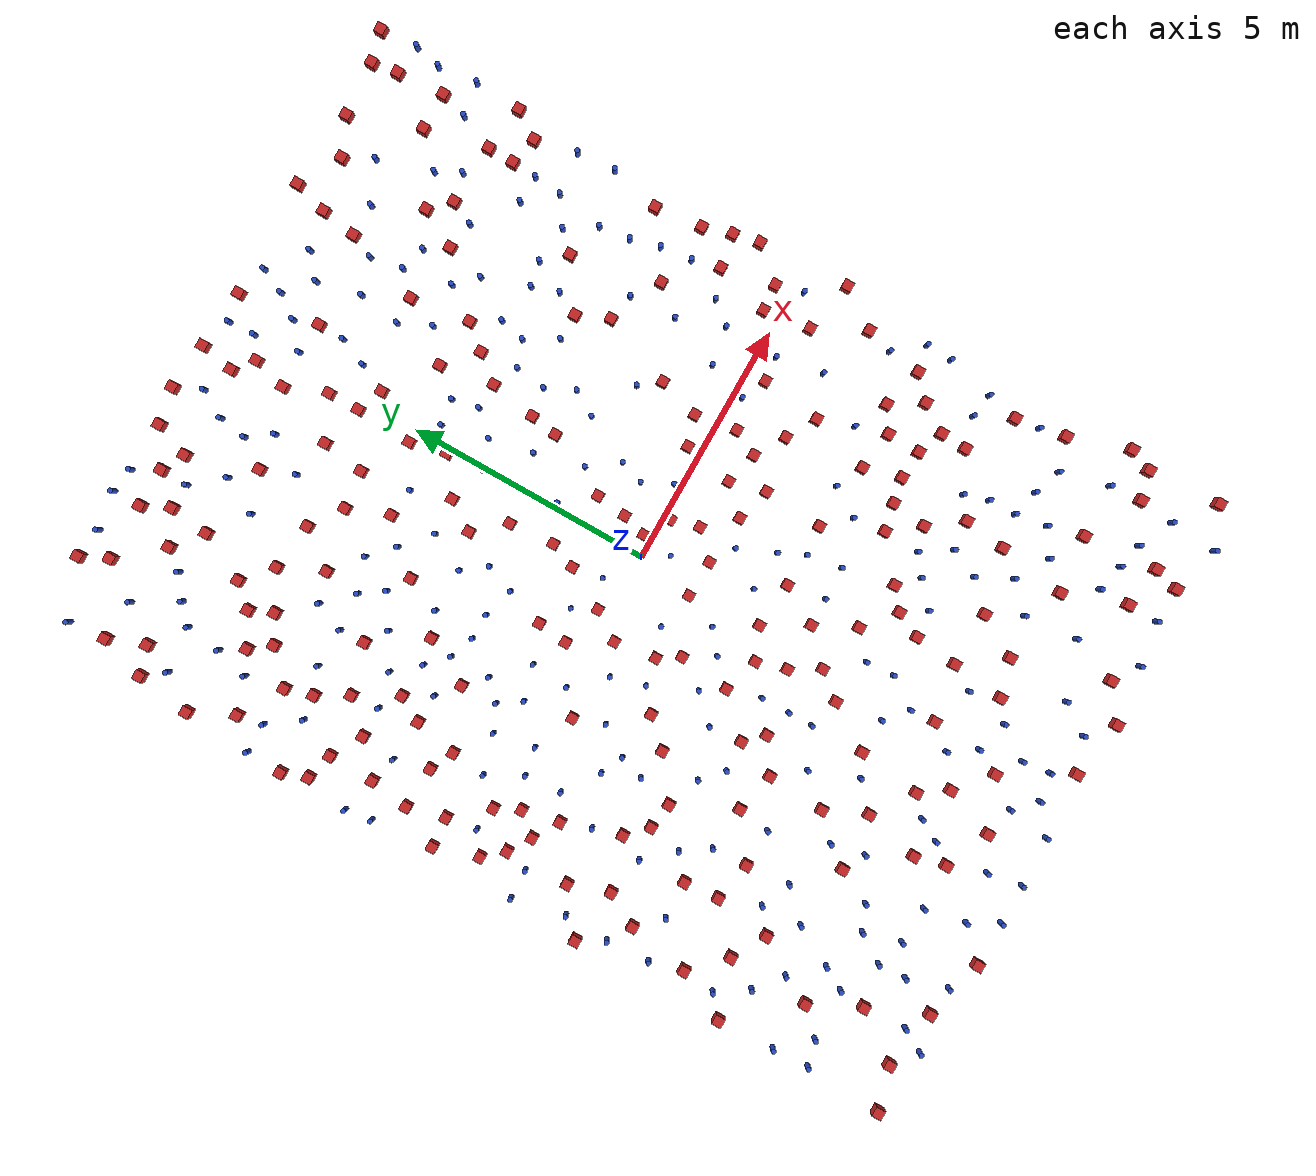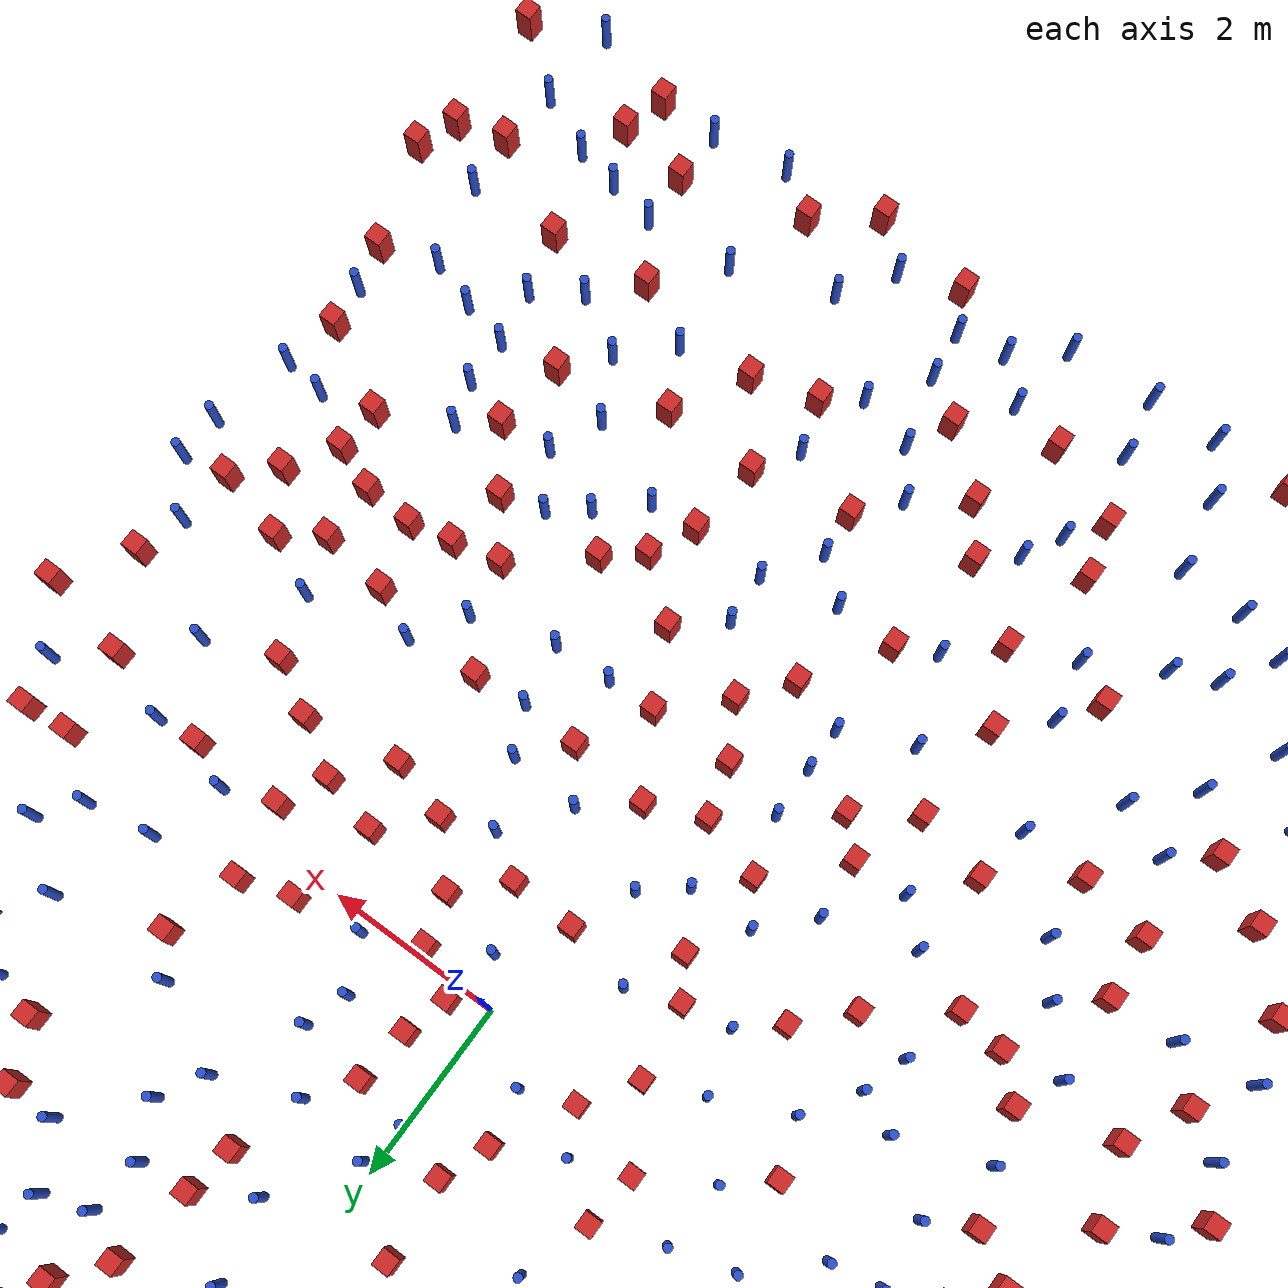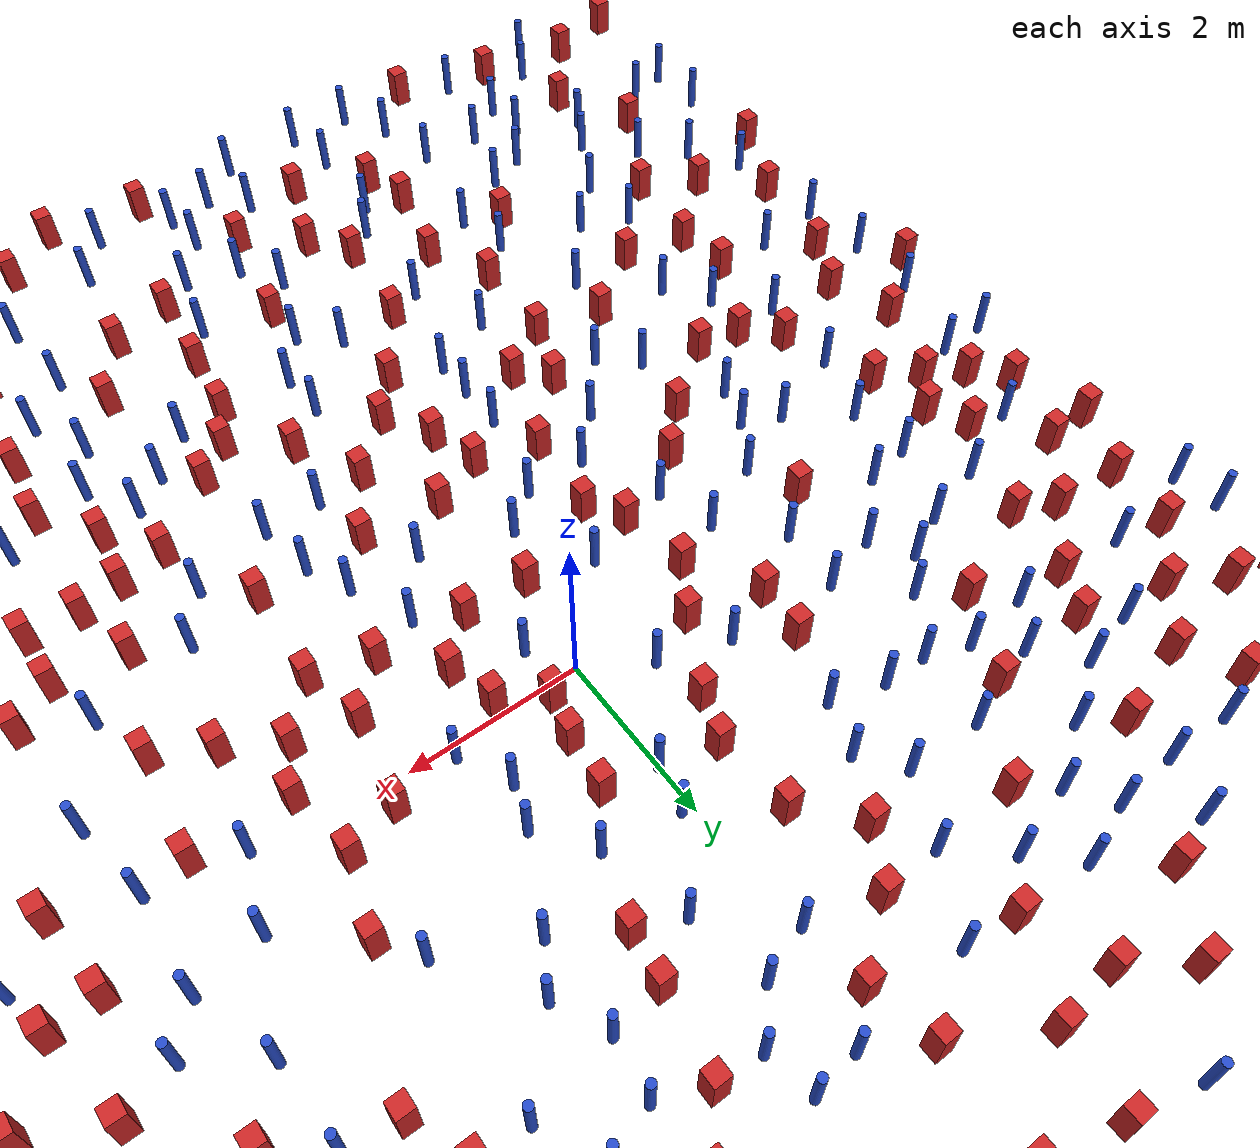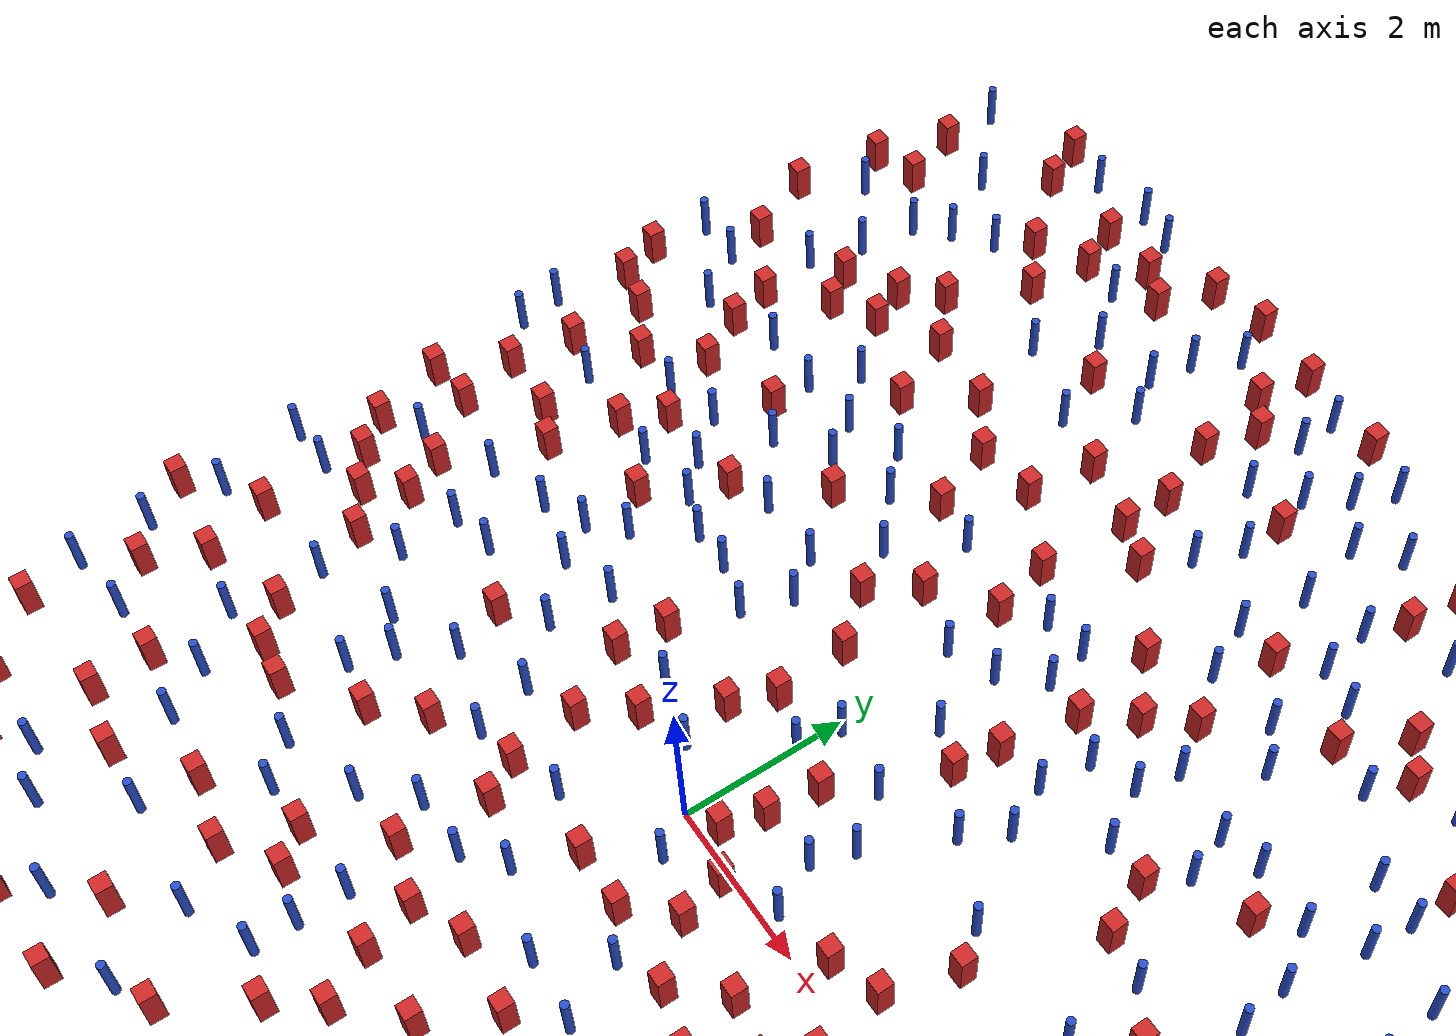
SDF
<sdf version="1.6">
  <model name="dense_39"><model name="square_post_obstacle0">
  <static>true</static>
  <pose frame="">-3.012826389 -2.17743969788 1.91545236811e-07 -7.35059704564e-06 1.12565212e-07 2.39332434364e-05</pose>
  <link name="link">
    <pose frame="">0 0 0.25 0 -0 0</pose>
    <inertial>
      <mass>100</mass>
      <inertia>
        <ixx>0.166667</ixx>
        <ixy>0</ixy>
        <ixz>0</ixz>
        <iyy>0.166667</iyy>
        <iyz>0</iyz>
        <izz>0.166667</izz>
      </inertia>
    </inertial>
    <collision name="collision">
      <geometry>
        <box>
          <size>.2 .2 .5</size>
        </box>
      </geometry>
      <max_contacts>10</max_contacts>
      <surface>
        <contact>
          <ode/>
        </contact>
        <bounce/>
        <friction>
          <torsional>
            <ode/>
          </torsional>
          <ode/>
        </friction>
      </surface>
    </collision>
    <visual name="visual">
      <geometry>
        <box>
          <size>.2 .2 .5</size>
        </box>
      </geometry>
      <material>
        <script>
          <name>Gazebo/Red</name>
          <uri>file://media/materials/scripts/gazebo.material</uri>
        </script>
      </material>
    </visual>
    <self_collide>0</self_collide>
    <kinematic>0</kinematic>
  </link>
</model>
<model name="square_post_obstacle1">
  <static>true</static>
  <pose frame="">3.69093480242 2.77040469333 1.91545236811e-07 -7.35059704564e-06 1.12565212e-07 2.39332434364e-05</pose>
  <link name="link">
    <pose frame="">0 0 0.25 0 -0 0</pose>
    <inertial>
      <mass>100</mass>
      <inertia>
        <ixx>0.166667</ixx>
        <ixy>0</ixy>
        <ixz>0</ixz>
        <iyy>0.166667</iyy>
        <iyz>0</iyz>
        <izz>0.166667</izz>
      </inertia>
    </inertial>
    <collision name="collision">
      <geometry>
        <box>
          <size>.2 .2 .5</size>
        </box>
      </geometry>
      <max_contacts>10</max_contacts>
      <surface>
        <contact>
          <ode/>
        </contact>
        <bounce/>
        <friction>
          <torsional>
            <ode/>
          </torsional>
          <ode/>
        </friction>
      </surface>
    </collision>
    <visual name="visual">
      <geometry>
        <box>
          <size>.2 .2 .5</size>
        </box>
      </geometry>
      <material>
        <script>
          <name>Gazebo/Red</name>
          <uri>file://media/materials/scripts/gazebo.material</uri>
        </script>
      </material>
    </visual>
    <self_collide>0</self_collide>
    <kinematic>0</kinematic>
  </link>
</model>
<model name="pole_obstacle0">
  <static>true</static>
  <pose frame="">-2.16096494241 -2.7342432716 7.38925637345e-09 -8.47170692798e-08 1.24976764939e-08 -1.74513093025e-07</pose>
  <link name="link">
  <pose frame="">0 0 0.3 0 -0 0</pose>
    <inertial>
      <mass>1</mass>
      <inertia>
        <ixx>0.145833</ixx>
        <ixy>0</ixy>
        <ixz>0</ixz>
        <iyy>0.145833</iyy>
        <iyz>0</iyz>
        <izz>0.125</izz>
      </inertia>
    </inertial>
    <collision name="collision">
      <geometry>
        <cylinder>
          <radius>0.05</radius>
          <length>.6</length>
        </cylinder>
      </geometry>
      <max_contacts>10</max_contacts>
      <surface>
        <contact>
          <ode/>
        </contact>
        <bounce/>
        <friction>
          <torsional>
            <ode/>
          </torsional>
          <ode/>
        </friction>
      </surface>
    </collision>
    <visual name="visual">
      <geometry>
        <cylinder>
          <radius>0.05</radius>
          <length>.6</length>
        </cylinder>
      </geometry>
      <material>
        <script>
          <name>Gazebo/Blue</name>
          <uri>file://media/materials/scripts/gazebo.material</uri>
        </script>
      </material>
    </visual>
    <self_collide>0</self_collide>
    <kinematic>0</kinematic>
  </link>
</model>
<model name="square_post_obstacle2">
  <static>true</static>
  <pose frame="">-3.61233754087 5.97910973367 1.91545236811e-07 -7.35059704564e-06 1.12565212e-07 2.39332434364e-05</pose>
  <link name="link">
    <pose frame="">0 0 0.25 0 -0 0</pose>
    <inertial>
      <mass>100</mass>
      <inertia>
        <ixx>0.166667</ixx>
        <ixy>0</ixy>
        <ixz>0</ixz>
        <iyy>0.166667</iyy>
        <iyz>0</iyz>
        <izz>0.166667</izz>
      </inertia>
    </inertial>
    <collision name="collision">
      <geometry>
        <box>
          <size>.2 .2 .5</size>
        </box>
      </geometry>
      <max_contacts>10</max_contacts>
      <surface>
        <contact>
          <ode/>
        </contact>
        <bounce/>
        <friction>
          <torsional>
            <ode/>
          </torsional>
          <ode/>
        </friction>
      </surface>
    </collision>
    <visual name="visual">
      <geometry>
        <box>
          <size>.2 .2 .5</size>
        </box>
      </geometry>
      <material>
        <script>
          <name>Gazebo/Red</name>
          <uri>file://media/materials/scripts/gazebo.material</uri>
        </script>
      </material>
    </visual>
    <self_collide>0</self_collide>
    <kinematic>0</kinematic>
  </link>
</model>
<model name="pole_obstacle1">
  <static>true</static>
  <pose frame="">-1.4139109991 7.27268750884 7.38925637345e-09 -8.47170692799e-08 1.24976765033e-08 -1.74513093018e-07</pose>
  <link name="link">
  <pose frame="">0 0 0.3 0 -0 0</pose>
    <inertial>
      <mass>1</mass>
      <inertia>
        <ixx>0.145833</ixx>
        <ixy>0</ixy>
        <ixz>0</ixz>
        <iyy>0.145833</iyy>
        <iyz>0</iyz>
        <izz>0.125</izz>
      </inertia>
    </inertial>
    <collision name="collision">
      <geometry>
        <cylinder>
          <radius>0.05</radius>
          <length>.6</length>
        </cylinder>
      </geometry>
      <max_contacts>10</max_contacts>
      <surface>
        <contact>
          <ode/>
        </contact>
        <bounce/>
        <friction>
          <torsional>
            <ode/>
          </torsional>
          <ode/>
        </friction>
      </surface>
    </collision>
    <visual name="visual">
      <geometry>
        <cylinder>
          <radius>0.05</radius>
          <length>.6</length>
        </cylinder>
      </geometry>
      <material>
        <script>
          <name>Gazebo/Blue</name>
          <uri>file://media/materials/scripts/gazebo.material</uri>
        </script>
      </material>
    </visual>
    <self_collide>0</self_collide>
    <kinematic>0</kinematic>
  </link>
</model>
<model name="square_post_obstacle3">
  <static>true</static>
  <pose frame="">2.75395827223 -3.80384737645 1.91545236811e-07 -7.35059704564e-06 1.12565212e-07 2.39332434364e-05</pose>
  <link name="link">
    <pose frame="">0 0 0.25 0 -0 0</pose>
    <inertial>
      <mass>100</mass>
      <inertia>
        <ixx>0.166667</ixx>
        <ixy>0</ixy>
        <ixz>0</ixz>
        <iyy>0.166667</iyy>
        <iyz>0</iyz>
        <izz>0.166667</izz>
      </inertia>
    </inertial>
    <collision name="collision">
      <geometry>
        <box>
          <size>.2 .2 .5</size>
        </box>
      </geometry>
      <max_contacts>10</max_contacts>
      <surface>
        <contact>
          <ode/>
        </contact>
        <bounce/>
        <friction>
          <torsional>
            <ode/>
          </torsional>
          <ode/>
        </friction>
      </surface>
    </collision>
    <visual name="visual">
      <geometry>
        <box>
          <size>.2 .2 .5</size>
        </box>
      </geometry>
      <material>
        <script>
          <name>Gazebo/Red</name>
          <uri>file://media/materials/scripts/gazebo.material</uri>
        </script>
      </material>
    </visual>
    <self_collide>0</self_collide>
    <kinematic>0</kinematic>
  </link>
</model>
<model name="pole_obstacle2">
  <static>true</static>
  <pose frame="">-5.59942114172 -9.33628321558 7.38925637345e-09 -8.471706928e-08 1.24976765081e-08 -1.74513093015e-07</pose>
  <link name="link">
  <pose frame="">0 0 0.3 0 -0 0</pose>
    <inertial>
      <mass>1</mass>
      <inertia>
        <ixx>0.145833</ixx>
        <ixy>0</ixy>
        <ixz>0</ixz>
        <iyy>0.145833</iyy>
        <iyz>0</iyz>
        <izz>0.125</izz>
      </inertia>
    </inertial>
    <collision name="collision">
      <geometry>
        <cylinder>
          <radius>0.05</radius>
          <length>.6</length>
        </cylinder>
      </geometry>
      <max_contacts>10</max_contacts>
      <surface>
        <contact>
          <ode/>
        </contact>
        <bounce/>
        <friction>
          <torsional>
            <ode/>
          </torsional>
          <ode/>
        </friction>
      </surface>
    </collision>
    <visual name="visual">
      <geometry>
        <cylinder>
          <radius>0.05</radius>
          <length>.6</length>
        </cylinder>
      </geometry>
      <material>
        <script>
          <name>Gazebo/Blue</name>
          <uri>file://media/materials/scripts/gazebo.material</uri>
        </script>
      </material>
    </visual>
    <self_collide>0</self_collide>
    <kinematic>0</kinematic>
  </link>
</model>
<model name="pole_obstacle3">
  <static>true</static>
  <pose frame="">1.05317652892 -1.47863244414 7.38925637345e-09 -8.471706928e-08 1.24976765079e-08 -1.74513093017e-07</pose>
  <link name="link">
  <pose frame="">0 0 0.3 0 -0 0</pose>
    <inertial>
      <mass>1</mass>
      <inertia>
        <ixx>0.145833</ixx>
        <ixy>0</ixy>
        <ixz>0</ixz>
        <iyy>0.145833</iyy>
        <iyz>0</iyz>
        <izz>0.125</izz>
      </inertia>
    </inertial>
    <collision name="collision">
      <geometry>
        <cylinder>
          <radius>0.05</radius>
          <length>.6</length>
        </cylinder>
      </geometry>
      <max_contacts>10</max_contacts>
      <surface>
        <contact>
          <ode/>
        </contact>
        <bounce/>
        <friction>
          <torsional>
            <ode/>
          </torsional>
          <ode/>
        </friction>
      </surface>
    </collision>
    <visual name="visual">
      <geometry>
        <cylinder>
          <radius>0.05</radius>
          <length>.6</length>
        </cylinder>
      </geometry>
      <material>
        <script>
          <name>Gazebo/Blue</name>
          <uri>file://media/materials/scripts/gazebo.material</uri>
        </script>
      </material>
    </visual>
    <self_collide>0</self_collide>
    <kinematic>0</kinematic>
  </link>
</model>
<model name="square_post_obstacle4">
  <static>true</static>
  <pose frame="">-2.10772842725 -3.40771525993 1.91545236811e-07 -7.35059704564e-06 1.12565212e-07 2.39332434364e-05</pose>
  <link name="link">
    <pose frame="">0 0 0.25 0 -0 0</pose>
    <inertial>
      <mass>100</mass>
      <inertia>
        <ixx>0.166667</ixx>
        <ixy>0</ixy>
        <ixz>0</ixz>
        <iyy>0.166667</iyy>
        <iyz>0</iyz>
        <izz>0.166667</izz>
      </inertia>
    </inertial>
    <collision name="collision">
      <geometry>
        <box>
          <size>.2 .2 .5</size>
        </box>
      </geometry>
      <max_contacts>10</max_contacts>
      <surface>
        <contact>
          <ode/>
        </contact>
        <bounce/>
        <friction>
          <torsional>
            <ode/>
          </torsional>
          <ode/>
        </friction>
      </surface>
    </collision>
    <visual name="visual">
      <geometry>
        <box>
          <size>.2 .2 .5</size>
        </box>
      </geometry>
      <material>
        <script>
          <name>Gazebo/Red</name>
          <uri>file://media/materials/scripts/gazebo.material</uri>
        </script>
      </material>
    </visual>
    <self_collide>0</self_collide>
    <kinematic>0</kinematic>
  </link>
</model>
<model name="square_post_obstacle5">
  <static>true</static>
  <pose frame="">-6.98999241708 3.96937142927 1.91545236811e-07 -7.35059704564e-06 1.12565212e-07 2.39332434364e-05</pose>
  <link name="link">
    <pose frame="">0 0 0.25 0 -0 0</pose>
    <inertial>
      <mass>100</mass>
      <inertia>
        <ixx>0.166667</ixx>
        <ixy>0</ixy>
        <ixz>0</ixz>
        <iyy>0.166667</iyy>
        <iyz>0</iyz>
        <izz>0.166667</izz>
      </inertia>
    </inertial>
    <collision name="collision">
      <geometry>
        <box>
          <size>.2 .2 .5</size>
        </box>
      </geometry>
      <max_contacts>10</max_contacts>
      <surface>
        <contact>
          <ode/>
        </contact>
        <bounce/>
        <friction>
          <torsional>
            <ode/>
          </torsional>
          <ode/>
        </friction>
      </surface>
    </collision>
    <visual name="visual">
      <geometry>
        <box>
          <size>.2 .2 .5</size>
        </box>
      </geometry>
      <material>
        <script>
          <name>Gazebo/Red</name>
          <uri>file://media/materials/scripts/gazebo.material</uri>
        </script>
      </material>
    </visual>
    <self_collide>0</self_collide>
    <kinematic>0</kinematic>
  </link>
</model>
<model name="square_post_obstacle6">
  <static>true</static>
  <pose frame="">4.7739497226 2.27891876205 1.91545236811e-07 -7.35059704564e-06 1.12565212e-07 2.39332434364e-05</pose>
  <link name="link">
    <pose frame="">0 0 0.25 0 -0 0</pose>
    <inertial>
      <mass>100</mass>
      <inertia>
        <ixx>0.166667</ixx>
        <ixy>0</ixy>
        <ixz>0</ixz>
        <iyy>0.166667</iyy>
        <iyz>0</iyz>
        <izz>0.166667</izz>
      </inertia>
    </inertial>
    <collision name="collision">
      <geometry>
        <box>
          <size>.2 .2 .5</size>
        </box>
      </geometry>
      <max_contacts>10</max_contacts>
      <surface>
        <contact>
          <ode/>
        </contact>
        <bounce/>
        <friction>
          <torsional>
            <ode/>
          </torsional>
          <ode/>
        </friction>
      </surface>
    </collision>
    <visual name="visual">
      <geometry>
        <box>
          <size>.2 .2 .5</size>
        </box>
      </geometry>
      <material>
        <script>
          <name>Gazebo/Red</name>
          <uri>file://media/materials/scripts/gazebo.material</uri>
        </script>
      </material>
    </visual>
    <self_collide>0</self_collide>
    <kinematic>0</kinematic>
  </link>
</model>
<model name="pole_obstacle4">
  <static>true</static>
  <pose frame="">-6.13567891964 -5.92751937192 7.38925637345e-09 -8.47170692796e-08 1.24976764786e-08 -1.74513093032e-07</pose>
  <link name="link">
  <pose frame="">0 0 0.3 0 -0 0</pose>
    <inertial>
      <mass>1</mass>
      <inertia>
        <ixx>0.145833</ixx>
        <ixy>0</ixy>
        <ixz>0</ixz>
        <iyy>0.145833</iyy>
        <iyz>0</iyz>
        <izz>0.125</izz>
      </inertia>
    </inertial>
    <collision name="collision">
      <geometry>
        <cylinder>
          <radius>0.05</radius>
          <length>.6</length>
        </cylinder>
      </geometry>
      <max_contacts>10</max_contacts>
      <surface>
        <contact>
          <ode/>
        </contact>
        <bounce/>
        <friction>
          <torsional>
            <ode/>
          </torsional>
          <ode/>
        </friction>
      </surface>
    </collision>
    <visual name="visual">
      <geometry>
        <cylinder>
          <radius>0.05</radius>
          <length>.6</length>
        </cylinder>
      </geometry>
      <material>
        <script>
          <name>Gazebo/Blue</name>
          <uri>file://media/materials/scripts/gazebo.material</uri>
        </script>
      </material>
    </visual>
    <self_collide>0</self_collide>
    <kinematic>0</kinematic>
  </link>
</model>
<model name="pole_obstacle5">
  <static>true</static>
  <pose frame="">-0.329985004801 -6.91863676255 7.38925637345e-09 -8.471706928e-08 1.24976765079e-08 -1.74513093015e-07</pose>
  <link name="link">
  <pose frame="">0 0 0.3 0 -0 0</pose>
    <inertial>
      <mass>1</mass>
      <inertia>
        <ixx>0.145833</ixx>
        <ixy>0</ixy>
        <ixz>0</ixz>
        <iyy>0.145833</iyy>
        <iyz>0</iyz>
        <izz>0.125</izz>
      </inertia>
    </inertial>
    <collision name="collision">
      <geometry>
        <cylinder>
          <radius>0.05</radius>
          <length>.6</length>
        </cylinder>
      </geometry>
      <max_contacts>10</max_contacts>
      <surface>
        <contact>
          <ode/>
        </contact>
        <bounce/>
        <friction>
          <torsional>
            <ode/>
          </torsional>
          <ode/>
        </friction>
      </surface>
    </collision>
    <visual name="visual">
      <geometry>
        <cylinder>
          <radius>0.05</radius>
          <length>.6</length>
        </cylinder>
      </geometry>
      <material>
        <script>
          <name>Gazebo/Blue</name>
          <uri>file://media/materials/scripts/gazebo.material</uri>
        </script>
      </material>
    </visual>
    <self_collide>0</self_collide>
    <kinematic>0</kinematic>
  </link>
</model>
<model name="square_post_obstacle7">
  <static>true</static>
  <pose frame="">1.20204457357 -6.22270453679 1.91545236811e-07 -7.35059704564e-06 1.12565212e-07 2.39332434364e-05</pose>
  <link name="link">
    <pose frame="">0 0 0.25 0 -0 0</pose>
    <inertial>
      <mass>100</mass>
      <inertia>
        <ixx>0.166667</ixx>
        <ixy>0</ixy>
        <ixz>0</ixz>
        <iyy>0.166667</iyy>
        <iyz>0</iyz>
        <izz>0.166667</izz>
      </inertia>
    </inertial>
    <collision name="collision">
      <geometry>
        <box>
          <size>.2 .2 .5</size>
        </box>
      </geometry>
      <max_contacts>10</max_contacts>
      <surface>
        <contact>
          <ode/>
        </contact>
        <bounce/>
        <friction>
          <torsional>
            <ode/>
          </torsional>
          <ode/>
        </friction>
      </surface>
    </collision>
    <visual name="visual">
      <geometry>
        <box>
          <size>.2 .2 .5</size>
        </box>
      </geometry>
      <material>
        <script>
          <name>Gazebo/Red</name>
          <uri>file://media/materials/scripts/gazebo.material</uri>
        </script>
      </material>
    </visual>
    <self_collide>0</self_collide>
    <kinematic>0</kinematic>
  </link>
</model>
<model name="square_post_obstacle8">
  <static>true</static>
  <pose frame="">-2.52519117045 3.64244328598 1.91545236811e-07 -7.35059704564e-06 1.12565212e-07 2.39332434364e-05</pose>
  <link name="link">
    <pose frame="">0 0 0.25 0 -0 0</pose>
    <inertial>
      <mass>100</mass>
      <inertia>
        <ixx>0.166667</ixx>
        <ixy>0</ixy>
        <ixz>0</ixz>
        <iyy>0.166667</iyy>
        <iyz>0</iyz>
        <izz>0.166667</izz>
      </inertia>
    </inertial>
    <collision name="collision">
      <geometry>
        <box>
          <size>.2 .2 .5</size>
        </box>
      </geometry>
      <max_contacts>10</max_contacts>
      <surface>
        <contact>
          <ode/>
        </contact>
        <bounce/>
        <friction>
          <torsional>
            <ode/>
          </torsional>
          <ode/>
        </friction>
      </surface>
    </collision>
    <visual name="visual">
      <geometry>
        <box>
          <size>.2 .2 .5</size>
        </box>
      </geometry>
      <material>
        <script>
          <name>Gazebo/Red</name>
          <uri>file://media/materials/scripts/gazebo.material</uri>
        </script>
      </material>
    </visual>
    <self_collide>0</self_collide>
    <kinematic>0</kinematic>
  </link>
</model>
<model name="pole_obstacle6">
  <static>true</static>
  <pose frame="">1.97811473688 8.43375830006 7.38925637345e-09 -8.47170692798e-08 1.24976764928e-08 -1.74513093023e-07</pose>
  <link name="link">
  <pose frame="">0 0 0.3 0 -0 0</pose>
    <inertial>
      <mass>1</mass>
      <inertia>
        <ixx>0.145833</ixx>
        <ixy>0</ixy>
        <ixz>0</ixz>
        <iyy>0.145833</iyy>
        <iyz>0</iyz>
        <izz>0.125</izz>
      </inertia>
    </inertial>
    <collision name="collision">
      <geometry>
        <cylinder>
          <radius>0.05</radius>
          <length>.6</length>
        </cylinder>
      </geometry>
      <max_contacts>10</max_contacts>
      <surface>
        <contact>
          <ode/>
        </contact>
        <bounce/>
        <friction>
          <torsional>
            <ode/>
          </torsional>
          <ode/>
        </friction>
      </surface>
    </collision>
    <visual name="visual">
      <geometry>
        <cylinder>
          <radius>0.05</radius>
          <length>.6</length>
        </cylinder>
      </geometry>
      <material>
        <script>
          <name>Gazebo/Blue</name>
          <uri>file://media/materials/scripts/gazebo.material</uri>
        </script>
      </material>
    </visual>
    <self_collide>0</self_collide>
    <kinematic>0</kinematic>
  </link>
</model>
<model name="pole_obstacle7">
  <static>true</static>
  <pose frame="">-5.32502928217 -8.85648023262 7.38925637345e-09 -8.471706928e-08 1.24976765081e-08 -1.74513093015e-07</pose>
  <link name="link">
  <pose frame="">0 0 0.3 0 -0 0</pose>
    <inertial>
      <mass>1</mass>
      <inertia>
        <ixx>0.145833</ixx>
        <ixy>0</ixy>
        <ixz>0</ixz>
        <iyy>0.145833</iyy>
        <iyz>0</iyz>
        <izz>0.125</izz>
      </inertia>
    </inertial>
    <collision name="collision">
      <geometry>
        <cylinder>
          <radius>0.05</radius>
          <length>.6</length>
        </cylinder>
      </geometry>
      <max_contacts>10</max_contacts>
      <surface>
        <contact>
          <ode/>
        </contact>
        <bounce/>
        <friction>
          <torsional>
            <ode/>
          </torsional>
          <ode/>
        </friction>
      </surface>
    </collision>
    <visual name="visual">
      <geometry>
        <cylinder>
          <radius>0.05</radius>
          <length>.6</length>
        </cylinder>
      </geometry>
      <material>
        <script>
          <name>Gazebo/Blue</name>
          <uri>file://media/materials/scripts/gazebo.material</uri>
        </script>
      </material>
    </visual>
    <self_collide>0</self_collide>
    <kinematic>0</kinematic>
  </link>
</model>
<model name="square_post_obstacle9">
  <static>true</static>
  <pose frame="">6.26904442361 -7.61594210601 1.91545236811e-07 -7.35059704564e-06 1.12565212e-07 2.39332434364e-05</pose>
  <link name="link">
    <pose frame="">0 0 0.25 0 -0 0</pose>
    <inertial>
      <mass>100</mass>
      <inertia>
        <ixx>0.166667</ixx>
        <ixy>0</ixy>
        <ixz>0</ixz>
        <iyy>0.166667</iyy>
        <iyz>0</iyz>
        <izz>0.166667</izz>
      </inertia>
    </inertial>
    <collision name="collision">
      <geometry>
        <box>
          <size>.2 .2 .5</size>
        </box>
      </geometry>
      <max_contacts>10</max_contacts>
      <surface>
        <contact>
          <ode/>
        </contact>
        <bounce/>
        <friction>
          <torsional>
            <ode/>
          </torsional>
          <ode/>
        </friction>
      </surface>
    </collision>
    <visual name="visual">
      <geometry>
        <box>
          <size>.2 .2 .5</size>
        </box>
      </geometry>
      <material>
        <script>
          <name>Gazebo/Red</name>
          <uri>file://media/materials/scripts/gazebo.material</uri>
        </script>
      </material>
    </visual>
    <self_collide>0</self_collide>
    <kinematic>0</kinematic>
  </link>
</model>
<model name="square_post_obstacle10">
  <static>true</static>
  <pose frame="">-4.59428738183 6.04871072272 1.91545236811e-07 -7.35059704564e-06 1.12565212e-07 2.39332434364e-05</pose>
  <link name="link">
    <pose frame="">0 0 0.25 0 -0 0</pose>
    <inertial>
      <mass>100</mass>
      <inertia>
        <ixx>0.166667</ixx>
        <ixy>0</ixy>
        <ixz>0</ixz>
        <iyy>0.166667</iyy>
        <iyz>0</iyz>
        <izz>0.166667</izz>
      </inertia>
    </inertial>
    <collision name="collision">
      <geometry>
        <box>
          <size>.2 .2 .5</size>
        </box>
      </geometry>
      <max_contacts>10</max_contacts>
      <surface>
        <contact>
          <ode/>
        </contact>
        <bounce/>
        <friction>
          <torsional>
            <ode/>
          </torsional>
          <ode/>
        </friction>
      </surface>
    </collision>
    <visual name="visual">
      <geometry>
        <box>
          <size>.2 .2 .5</size>
        </box>
      </geometry>
      <material>
        <script>
          <name>Gazebo/Red</name>
          <uri>file://media/materials/scripts/gazebo.material</uri>
        </script>
      </material>
    </visual>
    <self_collide>0</self_collide>
    <kinematic>0</kinematic>
  </link>
</model>
<model name="square_post_obstacle11">
  <static>true</static>
  <pose frame="">5.2790055508 0.315990524747 1.91545236811e-07 -7.35059704564e-06 1.12565212e-07 2.39332434364e-05</pose>
  <link name="link">
    <pose frame="">0 0 0.25 0 -0 0</pose>
    <inertial>
      <mass>100</mass>
      <inertia>
        <ixx>0.166667</ixx>
        <ixy>0</ixy>
        <ixz>0</ixz>
        <iyy>0.166667</iyy>
        <iyz>0</iyz>
        <izz>0.166667</izz>
      </inertia>
    </inertial>
    <collision name="collision">
      <geometry>
        <box>
          <size>.2 .2 .5</size>
        </box>
      </geometry>
      <max_contacts>10</max_contacts>
      <surface>
        <contact>
          <ode/>
        </contact>
        <bounce/>
        <friction>
          <torsional>
            <ode/>
          </torsional>
          <ode/>
        </friction>
      </surface>
    </collision>
    <visual name="visual">
      <geometry>
        <box>
          <size>.2 .2 .5</size>
        </box>
      </geometry>
      <material>
        <script>
          <name>Gazebo/Red</name>
          <uri>file://media/materials/scripts/gazebo.material</uri>
        </script>
      </material>
    </visual>
    <self_collide>0</self_collide>
    <kinematic>0</kinematic>
  </link>
</model>
<model name="square_post_obstacle12">
  <static>true</static>
  <pose frame="">-1.65785323321 4.5642074865 1.91545236811e-07 -7.35059704564e-06 1.12565212e-07 2.39332434364e-05</pose>
  <link name="link">
    <pose frame="">0 0 0.25 0 -0 0</pose>
    <inertial>
      <mass>100</mass>
      <inertia>
        <ixx>0.166667</ixx>
        <ixy>0</ixy>
        <ixz>0</ixz>
        <iyy>0.166667</iyy>
        <iyz>0</iyz>
        <izz>0.166667</izz>
      </inertia>
    </inertial>
    <collision name="collision">
      <geometry>
        <box>
          <size>.2 .2 .5</size>
        </box>
      </geometry>
      <max_contacts>10</max_contacts>
      <surface>
        <contact>
          <ode/>
        </contact>
        <bounce/>
        <friction>
          <torsional>
            <ode/>
          </torsional>
          <ode/>
        </friction>
      </surface>
    </collision>
    <visual name="visual">
      <geometry>
        <box>
          <size>.2 .2 .5</size>
        </box>
      </geometry>
      <material>
        <script>
          <name>Gazebo/Red</name>
          <uri>file://media/materials/scripts/gazebo.material</uri>
        </script>
      </material>
    </visual>
    <self_collide>0</self_collide>
    <kinematic>0</kinematic>
  </link>
</model>
<model name="square_post_obstacle13">
  <static>true</static>
  <pose frame="">-4.29329589986 7.95815774547 1.91545236811e-07 -7.35059704564e-06 1.12565212e-07 2.39332434364e-05</pose>
  <link name="link">
    <pose frame="">0 0 0.25 0 -0 0</pose>
    <inertial>
      <mass>100</mass>
      <inertia>
        <ixx>0.166667</ixx>
        <ixy>0</ixy>
        <ixz>0</ixz>
        <iyy>0.166667</iyy>
        <iyz>0</iyz>
        <izz>0.166667</izz>
      </inertia>
    </inertial>
    <collision name="collision">
      <geometry>
        <box>
          <size>.2 .2 .5</size>
        </box>
      </geometry>
      <max_contacts>10</max_contacts>
      <surface>
        <contact>
          <ode/>
        </contact>
        <bounce/>
        <friction>
          <torsional>
            <ode/>
          </torsional>
          <ode/>
        </friction>
      </surface>
    </collision>
    <visual name="visual">
      <geometry>
        <box>
          <size>.2 .2 .5</size>
        </box>
      </geometry>
      <material>
        <script>
          <name>Gazebo/Red</name>
          <uri>file://media/materials/scripts/gazebo.material</uri>
        </script>
      </material>
    </visual>
    <self_collide>0</self_collide>
    <kinematic>0</kinematic>
  </link>
</model>
<model name="pole_obstacle8">
  <static>true</static>
  <pose frame="">-6.91975358773 2.00622611297 7.38925637345e-09 -8.47170692799e-08 1.24976765078e-08 -1.74513093016e-07</pose>
  <link name="link">
  <pose frame="">0 0 0.3 0 -0 0</pose>
    <inertial>
      <mass>1</mass>
      <inertia>
        <ixx>0.145833</ixx>
        <ixy>0</ixy>
        <ixz>0</ixz>
        <iyy>0.145833</iyy>
        <iyz>0</iyz>
        <izz>0.125</izz>
      </inertia>
    </inertial>
    <collision name="collision">
      <geometry>
        <cylinder>
          <radius>0.05</radius>
          <length>.6</length>
        </cylinder>
      </geometry>
      <max_contacts>10</max_contacts>
      <surface>
        <contact>
          <ode/>
        </contact>
        <bounce/>
        <friction>
          <torsional>
            <ode/>
          </torsional>
          <ode/>
        </friction>
      </surface>
    </collision>
    <visual name="visual">
      <geometry>
        <cylinder>
          <radius>0.05</radius>
          <length>.6</length>
        </cylinder>
      </geometry>
      <material>
        <script>
          <name>Gazebo/Blue</name>
          <uri>file://media/materials/scripts/gazebo.material</uri>
        </script>
      </material>
    </visual>
    <self_collide>0</self_collide>
    <kinematic>0</kinematic>
  </link>
</model>
<model name="square_post_obstacle14">
  <static>true</static>
  <pose frame="">-0.126441259786 -4.07254027726 1.91545236811e-07 -7.35059704564e-06 1.12565212e-07 2.39332434364e-05</pose>
  <link name="link">
    <pose frame="">0 0 0.25 0 -0 0</pose>
    <inertial>
      <mass>100</mass>
      <inertia>
        <ixx>0.166667</ixx>
        <ixy>0</ixy>
        <ixz>0</ixz>
        <iyy>0.166667</iyy>
        <iyz>0</iyz>
        <izz>0.166667</izz>
      </inertia>
    </inertial>
    <collision name="collision">
      <geometry>
        <box>
          <size>.2 .2 .5</size>
        </box>
      </geometry>
      <max_contacts>10</max_contacts>
      <surface>
        <contact>
          <ode/>
        </contact>
        <bounce/>
        <friction>
          <torsional>
            <ode/>
          </torsional>
          <ode/>
        </friction>
      </surface>
    </collision>
    <visual name="visual">
      <geometry>
        <box>
          <size>.2 .2 .5</size>
        </box>
      </geometry>
      <material>
        <script>
          <name>Gazebo/Red</name>
          <uri>file://media/materials/scripts/gazebo.material</uri>
        </script>
      </material>
    </visual>
    <self_collide>0</self_collide>
    <kinematic>0</kinematic>
  </link>
</model>
<model name="square_post_obstacle15">
  <static>true</static>
  <pose frame="">-5.79865382688 -5.27832729134 1.91545236811e-07 -7.35059704564e-06 1.12565212e-07 2.39332434364e-05</pose>
  <link name="link">
    <pose frame="">0 0 0.25 0 -0 0</pose>
    <inertial>
      <mass>100</mass>
      <inertia>
        <ixx>0.166667</ixx>
        <ixy>0</ixy>
        <ixz>0</ixz>
        <iyy>0.166667</iyy>
        <iyz>0</iyz>
        <izz>0.166667</izz>
      </inertia>
    </inertial>
    <collision name="collision">
      <geometry>
        <box>
          <size>.2 .2 .5</size>
        </box>
      </geometry>
      <max_contacts>10</max_contacts>
      <surface>
        <contact>
          <ode/>
        </contact>
        <bounce/>
        <friction>
          <torsional>
            <ode/>
          </torsional>
          <ode/>
        </friction>
      </surface>
    </collision>
    <visual name="visual">
      <geometry>
        <box>
          <size>.2 .2 .5</size>
        </box>
      </geometry>
      <material>
        <script>
          <name>Gazebo/Red</name>
          <uri>file://media/materials/scripts/gazebo.material</uri>
        </script>
      </material>
    </visual>
    <self_collide>0</self_collide>
    <kinematic>0</kinematic>
  </link>
</model>
<model name="square_post_obstacle16">
  <static>true</static>
  <pose frame="">2.10160960088 -0.730467767537 1.91545236811e-07 -7.35059704564e-06 1.12565212e-07 2.39332434364e-05</pose>
  <link name="link">
    <pose frame="">0 0 0.25 0 -0 0</pose>
    <inertial>
      <mass>100</mass>
      <inertia>
        <ixx>0.166667</ixx>
        <ixy>0</ixy>
        <ixz>0</ixz>
        <iyy>0.166667</iyy>
        <iyz>0</iyz>
        <izz>0.166667</izz>
      </inertia>
    </inertial>
    <collision name="collision">
      <geometry>
        <box>
          <size>.2 .2 .5</size>
        </box>
      </geometry>
      <max_contacts>10</max_contacts>
      <surface>
        <contact>
          <ode/>
        </contact>
        <bounce/>
        <friction>
          <torsional>
            <ode/>
          </torsional>
          <ode/>
        </friction>
      </surface>
    </collision>
    <visual name="visual">
      <geometry>
        <box>
          <size>.2 .2 .5</size>
        </box>
      </geometry>
      <material>
        <script>
          <name>Gazebo/Red</name>
          <uri>file://media/materials/scripts/gazebo.material</uri>
        </script>
      </material>
    </visual>
    <self_collide>0</self_collide>
    <kinematic>0</kinematic>
  </link>
</model>
<model name="pole_obstacle9">
  <static>true</static>
  <pose frame="">4.22010196465 -2.30747923249 7.38925637345e-09 -8.47170692798e-08 1.24976764937e-08 -1.74513093023e-07</pose>
  <link name="link">
  <pose frame="">0 0 0.3 0 -0 0</pose>
    <inertial>
      <mass>1</mass>
      <inertia>
        <ixx>0.145833</ixx>
        <ixy>0</ixy>
        <ixz>0</ixz>
        <iyy>0.145833</iyy>
        <iyz>0</iyz>
        <izz>0.125</izz>
      </inertia>
    </inertial>
    <collision name="collision">
      <geometry>
        <cylinder>
          <radius>0.05</radius>
          <length>.6</length>
        </cylinder>
      </geometry>
      <max_contacts>10</max_contacts>
      <surface>
        <contact>
          <ode/>
        </contact>
        <bounce/>
        <friction>
          <torsional>
            <ode/>
          </torsional>
          <ode/>
        </friction>
      </surface>
    </collision>
    <visual name="visual">
      <geometry>
        <cylinder>
          <radius>0.05</radius>
          <length>.6</length>
        </cylinder>
      </geometry>
      <material>
        <script>
          <name>Gazebo/Blue</name>
          <uri>file://media/materials/scripts/gazebo.material</uri>
        </script>
      </material>
    </visual>
    <self_collide>0</self_collide>
    <kinematic>0</kinematic>
  </link>
</model>
<model name="square_post_obstacle17">
  <static>true</static>
  <pose frame="">2.96418394877 9.25661673583 1.91545236811e-07 -7.35059704564e-06 1.12565212e-07 2.39332434364e-05</pose>
  <link name="link">
    <pose frame="">0 0 0.25 0 -0 0</pose>
    <inertial>
      <mass>100</mass>
      <inertia>
        <ixx>0.166667</ixx>
        <ixy>0</ixy>
        <ixz>0</ixz>
        <iyy>0.166667</iyy>
        <iyz>0</iyz>
        <izz>0.166667</izz>
      </inertia>
    </inertial>
    <collision name="collision">
      <geometry>
        <box>
          <size>.2 .2 .5</size>
        </box>
      </geometry>
      <max_contacts>10</max_contacts>
      <surface>
        <contact>
          <ode/>
        </contact>
        <bounce/>
        <friction>
          <torsional>
            <ode/>
          </torsional>
          <ode/>
        </friction>
      </surface>
    </collision>
    <visual name="visual">
      <geometry>
        <box>
          <size>.2 .2 .5</size>
        </box>
      </geometry>
      <material>
        <script>
          <name>Gazebo/Red</name>
          <uri>file://media/materials/scripts/gazebo.material</uri>
        </script>
      </material>
    </visual>
    <self_collide>0</self_collide>
    <kinematic>0</kinematic>
  </link>
</model>
<model name="square_post_obstacle18">
  <static>true</static>
  <pose frame="">-5.32597365988 -0.40058097915 1.91545236811e-07 -7.35059704564e-06 1.12565212e-07 2.39332434364e-05</pose>
  <link name="link">
    <pose frame="">0 0 0.25 0 -0 0</pose>
    <inertial>
      <mass>100</mass>
      <inertia>
        <ixx>0.166667</ixx>
        <ixy>0</ixy>
        <ixz>0</ixz>
        <iyy>0.166667</iyy>
        <iyz>0</iyz>
        <izz>0.166667</izz>
      </inertia>
    </inertial>
    <collision name="collision">
      <geometry>
        <box>
          <size>.2 .2 .5</size>
        </box>
      </geometry>
      <max_contacts>10</max_contacts>
      <surface>
        <contact>
          <ode/>
        </contact>
        <bounce/>
        <friction>
          <torsional>
            <ode/>
          </torsional>
          <ode/>
        </friction>
      </surface>
    </collision>
    <visual name="visual">
      <geometry>
        <box>
          <size>.2 .2 .5</size>
        </box>
      </geometry>
      <material>
        <script>
          <name>Gazebo/Red</name>
          <uri>file://media/materials/scripts/gazebo.material</uri>
        </script>
      </material>
    </visual>
    <self_collide>0</self_collide>
    <kinematic>0</kinematic>
  </link>
</model>
<model name="pole_obstacle10">
  <static>true</static>
  <pose frame="">-2.79781469311 0.792266779906 7.38925637345e-09 -8.471706928e-08 1.24976765177e-08 -1.74513093012e-07</pose>
  <link name="link">
  <pose frame="">0 0 0.3 0 -0 0</pose>
    <inertial>
      <mass>1</mass>
      <inertia>
        <ixx>0.145833</ixx>
        <ixy>0</ixy>
        <ixz>0</ixz>
        <iyy>0.145833</iyy>
        <iyz>0</iyz>
        <izz>0.125</izz>
      </inertia>
    </inertial>
    <collision name="collision">
      <geometry>
        <cylinder>
          <radius>0.05</radius>
          <length>.6</length>
        </cylinder>
      </geometry>
      <max_contacts>10</max_contacts>
      <surface>
        <contact>
          <ode/>
        </contact>
        <bounce/>
        <friction>
          <torsional>
            <ode/>
          </torsional>
          <ode/>
        </friction>
      </surface>
    </collision>
    <visual name="visual">
      <geometry>
        <cylinder>
          <radius>0.05</radius>
          <length>.6</length>
        </cylinder>
      </geometry>
      <material>
        <script>
          <name>Gazebo/Blue</name>
          <uri>file://media/materials/scripts/gazebo.material</uri>
        </script>
      </material>
    </visual>
    <self_collide>0</self_collide>
    <kinematic>0</kinematic>
  </link>
</model>
<model name="square_post_obstacle19">
  <static>true</static>
  <pose frame="">-5.86505825323 -6.95468134986 1.91545236811e-07 -7.35059704564e-06 1.12565212e-07 2.39332434364e-05</pose>
  <link name="link">
    <pose frame="">0 0 0.25 0 -0 0</pose>
    <inertial>
      <mass>100</mass>
      <inertia>
        <ixx>0.166667</ixx>
        <ixy>0</ixy>
        <ixz>0</ixz>
        <iyy>0.166667</iyy>
        <iyz>0</iyz>
        <izz>0.166667</izz>
      </inertia>
    </inertial>
    <collision name="collision">
      <geometry>
        <box>
          <size>.2 .2 .5</size>
        </box>
      </geometry>
      <max_contacts>10</max_contacts>
      <surface>
        <contact>
          <ode/>
        </contact>
        <bounce/>
        <friction>
          <torsional>
            <ode/>
          </torsional>
          <ode/>
        </friction>
      </surface>
    </collision>
    <visual name="visual">
      <geometry>
        <box>
          <size>.2 .2 .5</size>
        </box>
      </geometry>
      <material>
        <script>
          <name>Gazebo/Red</name>
          <uri>file://media/materials/scripts/gazebo.material</uri>
        </script>
      </material>
    </visual>
    <self_collide>0</self_collide>
    <kinematic>0</kinematic>
  </link>
</model>
<model name="pole_obstacle11">
  <static>true</static>
  <pose frame="">-4.50997435611 -7.80186108126 7.38925637345e-09 -8.47170692796e-08 1.24976764786e-08 -1.74513093032e-07</pose>
  <link name="link">
  <pose frame="">0 0 0.3 0 -0 0</pose>
    <inertial>
      <mass>1</mass>
      <inertia>
        <ixx>0.145833</ixx>
        <ixy>0</ixy>
        <ixz>0</ixz>
        <iyy>0.145833</iyy>
        <iyz>0</iyz>
        <izz>0.125</izz>
      </inertia>
    </inertial>
    <collision name="collision">
      <geometry>
        <cylinder>
          <radius>0.05</radius>
          <length>.6</length>
        </cylinder>
      </geometry>
      <max_contacts>10</max_contacts>
      <surface>
        <contact>
          <ode/>
        </contact>
        <bounce/>
        <friction>
          <torsional>
            <ode/>
          </torsional>
          <ode/>
        </friction>
      </surface>
    </collision>
    <visual name="visual">
      <geometry>
        <cylinder>
          <radius>0.05</radius>
          <length>.6</length>
        </cylinder>
      </geometry>
      <material>
        <script>
          <name>Gazebo/Blue</name>
          <uri>file://media/materials/scripts/gazebo.material</uri>
        </script>
      </material>
    </visual>
    <self_collide>0</self_collide>
    <kinematic>0</kinematic>
  </link>
</model>
<model name="square_post_obstacle20">
  <static>true</static>
  <pose frame="">4.88842204589 -4.35391438542 1.91545236811e-07 -7.35059704564e-06 1.12565212e-07 2.39332434364e-05</pose>
  <link name="link">
    <pose frame="">0 0 0.25 0 -0 0</pose>
    <inertial>
      <mass>100</mass>
      <inertia>
        <ixx>0.166667</ixx>
        <ixy>0</ixy>
        <ixz>0</ixz>
        <iyy>0.166667</iyy>
        <iyz>0</iyz>
        <izz>0.166667</izz>
      </inertia>
    </inertial>
    <collision name="collision">
      <geometry>
        <box>
          <size>.2 .2 .5</size>
        </box>
      </geometry>
      <max_contacts>10</max_contacts>
      <surface>
        <contact>
          <ode/>
        </contact>
        <bounce/>
        <friction>
          <torsional>
            <ode/>
          </torsional>
          <ode/>
        </friction>
      </surface>
    </collision>
    <visual name="visual">
      <geometry>
        <box>
          <size>.2 .2 .5</size>
        </box>
      </geometry>
      <material>
        <script>
          <name>Gazebo/Red</name>
          <uri>file://media/materials/scripts/gazebo.material</uri>
        </script>
      </material>
    </visual>
    <self_collide>0</self_collide>
    <kinematic>0</kinematic>
  </link>
</model>
<model name="pole_obstacle12">
  <static>true</static>
  <pose frame="">-2.86380496484 0.0206646731336 7.38925637345e-09 -8.47170692793e-08 1.24976764457e-08 -1.74513093039e-07</pose>
  <link name="link">
  <pose frame="">0 0 0.3 0 -0 0</pose>
    <inertial>
      <mass>1</mass>
      <inertia>
        <ixx>0.145833</ixx>
        <ixy>0</ixy>
        <ixz>0</ixz>
        <iyy>0.145833</iyy>
        <iyz>0</iyz>
        <izz>0.125</izz>
      </inertia>
    </inertial>
    <collision name="collision">
      <geometry>
        <cylinder>
          <radius>0.05</radius>
          <length>.6</length>
        </cylinder>
      </geometry>
      <max_contacts>10</max_contacts>
      <surface>
        <contact>
          <ode/>
        </contact>
        <bounce/>
        <friction>
          <torsional>
            <ode/>
          </torsional>
          <ode/>
        </friction>
      </surface>
    </collision>
    <visual name="visual">
      <geometry>
        <cylinder>
          <radius>0.05</radius>
          <length>.6</length>
        </cylinder>
      </geometry>
      <material>
        <script>
          <name>Gazebo/Blue</name>
          <uri>file://media/materials/scripts/gazebo.material</uri>
        </script>
      </material>
    </visual>
    <self_collide>0</self_collide>
    <kinematic>0</kinematic>
  </link>
</model>
<model name="square_post_obstacle21">
  <static>true</static>
  <pose frame="">-4.98411081156 -3.79218492257 1.91545236811e-07 -7.35059704564e-06 1.12565212e-07 2.39332434364e-05</pose>
  <link name="link">
    <pose frame="">0 0 0.25 0 -0 0</pose>
    <inertial>
      <mass>100</mass>
      <inertia>
        <ixx>0.166667</ixx>
        <ixy>0</ixy>
        <ixz>0</ixz>
        <iyy>0.166667</iyy>
        <iyz>0</iyz>
        <izz>0.166667</izz>
      </inertia>
    </inertial>
    <collision name="collision">
      <geometry>
        <box>
          <size>.2 .2 .5</size>
        </box>
      </geometry>
      <max_contacts>10</max_contacts>
      <surface>
        <contact>
          <ode/>
        </contact>
        <bounce/>
        <friction>
          <torsional>
            <ode/>
          </torsional>
          <ode/>
        </friction>
      </surface>
    </collision>
    <visual name="visual">
      <geometry>
        <box>
          <size>.2 .2 .5</size>
        </box>
      </geometry>
      <material>
        <script>
          <name>Gazebo/Red</name>
          <uri>file://media/materials/scripts/gazebo.material</uri>
        </script>
      </material>
    </visual>
    <self_collide>0</self_collide>
    <kinematic>0</kinematic>
  </link>
</model>
<model name="pole_obstacle13">
  <static>true</static>
  <pose frame="">1.72117849599 7.15123532214 7.38925637345e-09 -8.47170692799e-08 1.24976765033e-08 -1.74513093018e-07</pose>
  <link name="link">
  <pose frame="">0 0 0.3 0 -0 0</pose>
    <inertial>
      <mass>1</mass>
      <inertia>
        <ixx>0.145833</ixx>
        <ixy>0</ixy>
        <ixz>0</ixz>
        <iyy>0.145833</iyy>
        <iyz>0</iyz>
        <izz>0.125</izz>
      </inertia>
    </inertial>
    <collision name="collision">
      <geometry>
        <cylinder>
          <radius>0.05</radius>
          <length>.6</length>
        </cylinder>
      </geometry>
      <max_contacts>10</max_contacts>
      <surface>
        <contact>
          <ode/>
        </contact>
        <bounce/>
        <friction>
          <torsional>
            <ode/>
          </torsional>
          <ode/>
        </friction>
      </surface>
    </collision>
    <visual name="visual">
      <geometry>
        <cylinder>
          <radius>0.05</radius>
          <length>.6</length>
        </cylinder>
      </geometry>
      <material>
        <script>
          <name>Gazebo/Blue</name>
          <uri>file://media/materials/scripts/gazebo.material</uri>
        </script>
      </material>
    </visual>
    <self_collide>0</self_collide>
    <kinematic>0</kinematic>
  </link>
</model>
<model name="square_post_obstacle22">
  <static>true</static>
  <pose frame="">-1.64915280023 -0.345057556898 1.91545236811e-07 -7.35059704564e-06 1.12565212e-07 2.39332434364e-05</pose>
  <link name="link">
    <pose frame="">0 0 0.25 0 -0 0</pose>
    <inertial>
      <mass>100</mass>
      <inertia>
        <ixx>0.166667</ixx>
        <ixy>0</ixy>
        <ixz>0</ixz>
        <iyy>0.166667</iyy>
        <iyz>0</iyz>
        <izz>0.166667</izz>
      </inertia>
    </inertial>
    <collision name="collision">
      <geometry>
        <box>
          <size>.2 .2 .5</size>
        </box>
      </geometry>
      <max_contacts>10</max_contacts>
      <surface>
        <contact>
          <ode/>
        </contact>
        <bounce/>
        <friction>
          <torsional>
            <ode/>
          </torsional>
          <ode/>
        </friction>
      </surface>
    </collision>
    <visual name="visual">
      <geometry>
        <box>
          <size>.2 .2 .5</size>
        </box>
      </geometry>
      <material>
        <script>
          <name>Gazebo/Red</name>
          <uri>file://media/materials/scripts/gazebo.material</uri>
        </script>
      </material>
    </visual>
    <self_collide>0</self_collide>
    <kinematic>0</kinematic>
  </link>
</model>
<model name="pole_obstacle14">
  <static>true</static>
  <pose frame="">1.62010785951 -2.73099493347 7.38925637345e-09 -8.47170692799e-08 1.24976765053e-08 -1.74513093017e-07</pose>
  <link name="link">
  <pose frame="">0 0 0.3 0 -0 0</pose>
    <inertial>
      <mass>1</mass>
      <inertia>
        <ixx>0.145833</ixx>
        <ixy>0</ixy>
        <ixz>0</ixz>
        <iyy>0.145833</iyy>
        <iyz>0</iyz>
        <izz>0.125</izz>
      </inertia>
    </inertial>
    <collision name="collision">
      <geometry>
        <cylinder>
          <radius>0.05</radius>
          <length>.6</length>
        </cylinder>
      </geometry>
      <max_contacts>10</max_contacts>
      <surface>
        <contact>
          <ode/>
        </contact>
        <bounce/>
        <friction>
          <torsional>
            <ode/>
          </torsional>
          <ode/>
        </friction>
      </surface>
    </collision>
    <visual name="visual">
      <geometry>
        <cylinder>
          <radius>0.05</radius>
          <length>.6</length>
        </cylinder>
      </geometry>
      <material>
        <script>
          <name>Gazebo/Blue</name>
          <uri>file://media/materials/scripts/gazebo.material</uri>
        </script>
      </material>
    </visual>
    <self_collide>0</self_collide>
    <kinematic>0</kinematic>
  </link>
</model>
<model name="pole_obstacle15">
  <static>true</static>
  <pose frame="">5.64696447669 -7.1184676006 7.38925637345e-09 -8.47170692796e-08 1.24976764786e-08 -1.74513093032e-07</pose>
  <link name="link">
  <pose frame="">0 0 0.3 0 -0 0</pose>
    <inertial>
      <mass>1</mass>
      <inertia>
        <ixx>0.145833</ixx>
        <ixy>0</ixy>
        <ixz>0</ixz>
        <iyy>0.145833</iyy>
        <iyz>0</iyz>
        <izz>0.125</izz>
      </inertia>
    </inertial>
    <collision name="collision">
      <geometry>
        <cylinder>
          <radius>0.05</radius>
          <length>.6</length>
        </cylinder>
      </geometry>
      <max_contacts>10</max_contacts>
      <surface>
        <contact>
          <ode/>
        </contact>
        <bounce/>
        <friction>
          <torsional>
            <ode/>
          </torsional>
          <ode/>
        </friction>
      </surface>
    </collision>
    <visual name="visual">
      <geometry>
        <cylinder>
          <radius>0.05</radius>
          <length>.6</length>
        </cylinder>
      </geometry>
      <material>
        <script>
          <name>Gazebo/Blue</name>
          <uri>file://media/materials/scripts/gazebo.material</uri>
        </script>
      </material>
    </visual>
    <self_collide>0</self_collide>
    <kinematic>0</kinematic>
  </link>
</model>
<model name="pole_obstacle16">
  <static>true</static>
  <pose frame="">-3.49376932607 0.596809447296 7.38925637345e-09 -8.47170692796e-08 1.24976764768e-08 -1.74513093035e-07</pose>
  <link name="link">
  <pose frame="">0 0 0.3 0 -0 0</pose>
    <inertial>
      <mass>1</mass>
      <inertia>
        <ixx>0.145833</ixx>
        <ixy>0</ixy>
        <ixz>0</ixz>
        <iyy>0.145833</iyy>
        <iyz>0</iyz>
        <izz>0.125</izz>
      </inertia>
    </inertial>
    <collision name="collision">
      <geometry>
        <cylinder>
          <radius>0.05</radius>
          <length>.6</length>
        </cylinder>
      </geometry>
      <max_contacts>10</max_contacts>
      <surface>
        <contact>
          <ode/>
        </contact>
        <bounce/>
        <friction>
          <torsional>
            <ode/>
          </torsional>
          <ode/>
        </friction>
      </surface>
    </collision>
    <visual name="visual">
      <geometry>
        <cylinder>
          <radius>0.05</radius>
          <length>.6</length>
        </cylinder>
      </geometry>
      <material>
        <script>
          <name>Gazebo/Blue</name>
          <uri>file://media/materials/scripts/gazebo.material</uri>
        </script>
      </material>
    </visual>
    <self_collide>0</self_collide>
    <kinematic>0</kinematic>
  </link>
</model>
<model name="square_post_obstacle23">
  <static>true</static>
  <pose frame="">-4.19277909428 6.49343664088 1.91545236811e-07 -7.35059704564e-06 1.12565212e-07 2.39332434364e-05</pose>
  <link name="link">
    <pose frame="">0 0 0.25 0 -0 0</pose>
    <inertial>
      <mass>100</mass>
      <inertia>
        <ixx>0.166667</ixx>
        <ixy>0</ixy>
        <ixz>0</ixz>
        <iyy>0.166667</iyy>
        <iyz>0</iyz>
        <izz>0.166667</izz>
      </inertia>
    </inertial>
    <collision name="collision">
      <geometry>
        <box>
          <size>.2 .2 .5</size>
        </box>
      </geometry>
      <max_contacts>10</max_contacts>
      <surface>
        <contact>
          <ode/>
        </contact>
        <bounce/>
        <friction>
          <torsional>
            <ode/>
          </torsional>
          <ode/>
        </friction>
      </surface>
    </collision>
    <visual name="visual">
      <geometry>
        <box>
          <size>.2 .2 .5</size>
        </box>
      </geometry>
      <material>
        <script>
          <name>Gazebo/Red</name>
          <uri>file://media/materials/scripts/gazebo.material</uri>
        </script>
      </material>
    </visual>
    <self_collide>0</self_collide>
    <kinematic>0</kinematic>
  </link>
</model>
<model name="pole_obstacle17">
  <static>true</static>
  <pose frame="">-1.50419928283 0.696034674528 7.38925637345e-09 -8.47170692799e-08 1.24976765075e-08 -1.74513093017e-07</pose>
  <link name="link">
  <pose frame="">0 0 0.3 0 -0 0</pose>
    <inertial>
      <mass>1</mass>
      <inertia>
        <ixx>0.145833</ixx>
        <ixy>0</ixy>
        <ixz>0</ixz>
        <iyy>0.145833</iyy>
        <iyz>0</iyz>
        <izz>0.125</izz>
      </inertia>
    </inertial>
    <collision name="collision">
      <geometry>
        <cylinder>
          <radius>0.05</radius>
          <length>.6</length>
        </cylinder>
      </geometry>
      <max_contacts>10</max_contacts>
      <surface>
        <contact>
          <ode/>
        </contact>
        <bounce/>
        <friction>
          <torsional>
            <ode/>
          </torsional>
          <ode/>
        </friction>
      </surface>
    </collision>
    <visual name="visual">
      <geometry>
        <cylinder>
          <radius>0.05</radius>
          <length>.6</length>
        </cylinder>
      </geometry>
      <material>
        <script>
          <name>Gazebo/Blue</name>
          <uri>file://media/materials/scripts/gazebo.material</uri>
        </script>
      </material>
    </visual>
    <self_collide>0</self_collide>
    <kinematic>0</kinematic>
  </link>
</model>
<model name="square_post_obstacle24">
  <static>true</static>
  <pose frame="">-6.97479643628 -9.19102325325 1.91545236811e-07 -7.35059704564e-06 1.12565212e-07 2.39332434364e-05</pose>
  <link name="link">
    <pose frame="">0 0 0.25 0 -0 0</pose>
    <inertial>
      <mass>100</mass>
      <inertia>
        <ixx>0.166667</ixx>
        <ixy>0</ixy>
        <ixz>0</ixz>
        <iyy>0.166667</iyy>
        <iyz>0</iyz>
        <izz>0.166667</izz>
      </inertia>
    </inertial>
    <collision name="collision">
      <geometry>
        <box>
          <size>.2 .2 .5</size>
        </box>
      </geometry>
      <max_contacts>10</max_contacts>
      <surface>
        <contact>
          <ode/>
        </contact>
        <bounce/>
        <friction>
          <torsional>
            <ode/>
          </torsional>
          <ode/>
        </friction>
      </surface>
    </collision>
    <visual name="visual">
      <geometry>
        <box>
          <size>.2 .2 .5</size>
        </box>
      </geometry>
      <material>
        <script>
          <name>Gazebo/Red</name>
          <uri>file://media/materials/scripts/gazebo.material</uri>
        </script>
      </material>
    </visual>
    <self_collide>0</self_collide>
    <kinematic>0</kinematic>
  </link>
</model>
<model name="square_post_obstacle25">
  <static>true</static>
  <pose frame="">0.0576677048483 -6.43979260257 1.91545236811e-07 -7.35059704564e-06 1.12565212e-07 2.39332434364e-05</pose>
  <link name="link">
    <pose frame="">0 0 0.25 0 -0 0</pose>
    <inertial>
      <mass>100</mass>
      <inertia>
        <ixx>0.166667</ixx>
        <ixy>0</ixy>
        <ixz>0</ixz>
        <iyy>0.166667</iyy>
        <iyz>0</iyz>
        <izz>0.166667</izz>
      </inertia>
    </inertial>
    <collision name="collision">
      <geometry>
        <box>
          <size>.2 .2 .5</size>
        </box>
      </geometry>
      <max_contacts>10</max_contacts>
      <surface>
        <contact>
          <ode/>
        </contact>
        <bounce/>
        <friction>
          <torsional>
            <ode/>
          </torsional>
          <ode/>
        </friction>
      </surface>
    </collision>
    <visual name="visual">
      <geometry>
        <box>
          <size>.2 .2 .5</size>
        </box>
      </geometry>
      <material>
        <script>
          <name>Gazebo/Red</name>
          <uri>file://media/materials/scripts/gazebo.material</uri>
        </script>
      </material>
    </visual>
    <self_collide>0</self_collide>
    <kinematic>0</kinematic>
  </link>
</model>
<model name="square_post_obstacle26">
  <static>true</static>
  <pose frame="">-4.38760822735 -2.71700138325 1.91545236811e-07 -7.35059704564e-06 1.12565212e-07 2.39332434364e-05</pose>
  <link name="link">
    <pose frame="">0 0 0.25 0 -0 0</pose>
    <inertial>
      <mass>100</mass>
      <inertia>
        <ixx>0.166667</ixx>
        <ixy>0</ixy>
        <ixz>0</ixz>
        <iyy>0.166667</iyy>
        <iyz>0</iyz>
        <izz>0.166667</izz>
      </inertia>
    </inertial>
    <collision name="collision">
      <geometry>
        <box>
          <size>.2 .2 .5</size>
        </box>
      </geometry>
      <max_contacts>10</max_contacts>
      <surface>
        <contact>
          <ode/>
        </contact>
        <bounce/>
        <friction>
          <torsional>
            <ode/>
          </torsional>
          <ode/>
        </friction>
      </surface>
    </collision>
    <visual name="visual">
      <geometry>
        <box>
          <size>.2 .2 .5</size>
        </box>
      </geometry>
      <material>
        <script>
          <name>Gazebo/Red</name>
          <uri>file://media/materials/scripts/gazebo.material</uri>
        </script>
      </material>
    </visual>
    <self_collide>0</self_collide>
    <kinematic>0</kinematic>
  </link>
</model>
<model name="square_post_obstacle27">
  <static>true</static>
  <pose frame="">-5.55627612815 4.70236604492 1.91545236811e-07 -7.35059704564e-06 1.12565212e-07 2.39332434364e-05</pose>
  <link name="link">
    <pose frame="">0 0 0.25 0 -0 0</pose>
    <inertial>
      <mass>100</mass>
      <inertia>
        <ixx>0.166667</ixx>
        <ixy>0</ixy>
        <ixz>0</ixz>
        <iyy>0.166667</iyy>
        <iyz>0</iyz>
        <izz>0.166667</izz>
      </inertia>
    </inertial>
    <collision name="collision">
      <geometry>
        <box>
          <size>.2 .2 .5</size>
        </box>
      </geometry>
      <max_contacts>10</max_contacts>
      <surface>
        <contact>
          <ode/>
        </contact>
        <bounce/>
        <friction>
          <torsional>
            <ode/>
          </torsional>
          <ode/>
        </friction>
      </surface>
    </collision>
    <visual name="visual">
      <geometry>
        <box>
          <size>.2 .2 .5</size>
        </box>
      </geometry>
      <material>
        <script>
          <name>Gazebo/Red</name>
          <uri>file://media/materials/scripts/gazebo.material</uri>
        </script>
      </material>
    </visual>
    <self_collide>0</self_collide>
    <kinematic>0</kinematic>
  </link>
</model>
<model name="pole_obstacle18">
  <static>true</static>
  <pose frame="">-4.15793994046 -0.0253211246921 7.38925637345e-09 -8.47170692799e-08 1.24976764994e-08 -1.74513093022e-07</pose>
  <link name="link">
  <pose frame="">0 0 0.3 0 -0 0</pose>
    <inertial>
      <mass>1</mass>
      <inertia>
        <ixx>0.145833</ixx>
        <ixy>0</ixy>
        <ixz>0</ixz>
        <iyy>0.145833</iyy>
        <iyz>0</iyz>
        <izz>0.125</izz>
      </inertia>
    </inertial>
    <collision name="collision">
      <geometry>
        <cylinder>
          <radius>0.05</radius>
          <length>.6</length>
        </cylinder>
      </geometry>
      <max_contacts>10</max_contacts>
      <surface>
        <contact>
          <ode/>
        </contact>
        <bounce/>
        <friction>
          <torsional>
            <ode/>
          </torsional>
          <ode/>
        </friction>
      </surface>
    </collision>
    <visual name="visual">
      <geometry>
        <cylinder>
          <radius>0.05</radius>
          <length>.6</length>
        </cylinder>
      </geometry>
      <material>
        <script>
          <name>Gazebo/Blue</name>
          <uri>file://media/materials/scripts/gazebo.material</uri>
        </script>
      </material>
    </visual>
    <self_collide>0</self_collide>
    <kinematic>0</kinematic>
  </link>
</model>
<model name="square_post_obstacle28">
  <static>true</static>
  <pose frame="">-6.80364117076 3.45359508598 1.91545236811e-07 -7.35059704564e-06 1.12565212e-07 2.39332434364e-05</pose>
  <link name="link">
    <pose frame="">0 0 0.25 0 -0 0</pose>
    <inertial>
      <mass>100</mass>
      <inertia>
        <ixx>0.166667</ixx>
        <ixy>0</ixy>
        <ixz>0</ixz>
        <iyy>0.166667</iyy>
        <iyz>0</iyz>
        <izz>0.166667</izz>
      </inertia>
    </inertial>
    <collision name="collision">
      <geometry>
        <box>
          <size>.2 .2 .5</size>
        </box>
      </geometry>
      <max_contacts>10</max_contacts>
      <surface>
        <contact>
          <ode/>
        </contact>
        <bounce/>
        <friction>
          <torsional>
            <ode/>
          </torsional>
          <ode/>
        </friction>
      </surface>
    </collision>
    <visual name="visual">
      <geometry>
        <box>
          <size>.2 .2 .5</size>
        </box>
      </geometry>
      <material>
        <script>
          <name>Gazebo/Red</name>
          <uri>file://media/materials/scripts/gazebo.material</uri>
        </script>
      </material>
    </visual>
    <self_collide>0</self_collide>
    <kinematic>0</kinematic>
  </link>
</model>
<model name="pole_obstacle19">
  <static>true</static>
  <pose frame="">-2.97029968557 6.91473031838 7.38925637345e-09 -8.47170692798e-08 1.24976765033e-08 -1.74513093019e-07</pose>
  <link name="link">
  <pose frame="">0 0 0.3 0 -0 0</pose>
    <inertial>
      <mass>1</mass>
      <inertia>
        <ixx>0.145833</ixx>
        <ixy>0</ixy>
        <ixz>0</ixz>
        <iyy>0.145833</iyy>
        <iyz>0</iyz>
        <izz>0.125</izz>
      </inertia>
    </inertial>
    <collision name="collision">
      <geometry>
        <cylinder>
          <radius>0.05</radius>
          <length>.6</length>
        </cylinder>
      </geometry>
      <max_contacts>10</max_contacts>
      <surface>
        <contact>
          <ode/>
        </contact>
        <bounce/>
        <friction>
          <torsional>
            <ode/>
          </torsional>
          <ode/>
        </friction>
      </surface>
    </collision>
    <visual name="visual">
      <geometry>
        <cylinder>
          <radius>0.05</radius>
          <length>.6</length>
        </cylinder>
      </geometry>
      <material>
        <script>
          <name>Gazebo/Blue</name>
          <uri>file://media/materials/scripts/gazebo.material</uri>
        </script>
      </material>
    </visual>
    <self_collide>0</self_collide>
    <kinematic>0</kinematic>
  </link>
</model>
<model name="square_post_obstacle29">
  <static>true</static>
  <pose frame="">2.28679880018 -1.4551265204 1.91545236811e-07 -7.35059704564e-06 1.12565212e-07 2.39332434364e-05</pose>
  <link name="link">
    <pose frame="">0 0 0.25 0 -0 0</pose>
    <inertial>
      <mass>100</mass>
      <inertia>
        <ixx>0.166667</ixx>
        <ixy>0</ixy>
        <ixz>0</ixz>
        <iyy>0.166667</iyy>
        <iyz>0</iyz>
        <izz>0.166667</izz>
      </inertia>
    </inertial>
    <collision name="collision">
      <geometry>
        <box>
          <size>.2 .2 .5</size>
        </box>
      </geometry>
      <max_contacts>10</max_contacts>
      <surface>
        <contact>
          <ode/>
        </contact>
        <bounce/>
        <friction>
          <torsional>
            <ode/>
          </torsional>
          <ode/>
        </friction>
      </surface>
    </collision>
    <visual name="visual">
      <geometry>
        <box>
          <size>.2 .2 .5</size>
        </box>
      </geometry>
      <material>
        <script>
          <name>Gazebo/Red</name>
          <uri>file://media/materials/scripts/gazebo.material</uri>
        </script>
      </material>
    </visual>
    <self_collide>0</self_collide>
    <kinematic>0</kinematic>
  </link>
</model>
<model name="square_post_obstacle30">
  <static>true</static>
  <pose frame="">3.59892521705 -2.82433107518 1.91545236811e-07 -7.35059704564e-06 1.12565212e-07 2.39332434364e-05</pose>
  <link name="link">
    <pose frame="">0 0 0.25 0 -0 0</pose>
    <inertial>
      <mass>100</mass>
      <inertia>
        <ixx>0.166667</ixx>
        <ixy>0</ixy>
        <ixz>0</ixz>
        <iyy>0.166667</iyy>
        <iyz>0</iyz>
        <izz>0.166667</izz>
      </inertia>
    </inertial>
    <collision name="collision">
      <geometry>
        <box>
          <size>.2 .2 .5</size>
        </box>
      </geometry>
      <max_contacts>10</max_contacts>
      <surface>
        <contact>
          <ode/>
        </contact>
        <bounce/>
        <friction>
          <torsional>
            <ode/>
          </torsional>
          <ode/>
        </friction>
      </surface>
    </collision>
    <visual name="visual">
      <geometry>
        <box>
          <size>.2 .2 .5</size>
        </box>
      </geometry>
      <material>
        <script>
          <name>Gazebo/Red</name>
          <uri>file://media/materials/scripts/gazebo.material</uri>
        </script>
      </material>
    </visual>
    <self_collide>0</self_collide>
    <kinematic>0</kinematic>
  </link>
</model>
<model name="pole_obstacle20">
  <static>true</static>
  <pose frame="">-3.16024954971 -3.05051583281 7.38925637345e-09 -8.471706928e-08 1.24976765098e-08 -1.74513093016e-07</pose>
  <link name="link">
  <pose frame="">0 0 0.3 0 -0 0</pose>
    <inertial>
      <mass>1</mass>
      <inertia>
        <ixx>0.145833</ixx>
        <ixy>0</ixy>
        <ixz>0</ixz>
        <iyy>0.145833</iyy>
        <iyz>0</iyz>
        <izz>0.125</izz>
      </inertia>
    </inertial>
    <collision name="collision">
      <geometry>
        <cylinder>
          <radius>0.05</radius>
          <length>.6</length>
        </cylinder>
      </geometry>
      <max_contacts>10</max_contacts>
      <surface>
        <contact>
          <ode/>
        </contact>
        <bounce/>
        <friction>
          <torsional>
            <ode/>
          </torsional>
          <ode/>
        </friction>
      </surface>
    </collision>
    <visual name="visual">
      <geometry>
        <cylinder>
          <radius>0.05</radius>
          <length>.6</length>
        </cylinder>
      </geometry>
      <material>
        <script>
          <name>Gazebo/Blue</name>
          <uri>file://media/materials/scripts/gazebo.material</uri>
        </script>
      </material>
    </visual>
    <self_collide>0</self_collide>
    <kinematic>0</kinematic>
  </link>
</model>
<model name="pole_obstacle21">
  <static>true</static>
  <pose frame="">-6.66049323436 -2.1342443122 7.38925637345e-09 -8.47170692798e-08 1.24976764937e-08 -1.74513093023e-07</pose>
  <link name="link">
  <pose frame="">0 0 0.3 0 -0 0</pose>
    <inertial>
      <mass>1</mass>
      <inertia>
        <ixx>0.145833</ixx>
        <ixy>0</ixy>
        <ixz>0</ixz>
        <iyy>0.145833</iyy>
        <iyz>0</iyz>
        <izz>0.125</izz>
      </inertia>
    </inertial>
    <collision name="collision">
      <geometry>
        <cylinder>
          <radius>0.05</radius>
          <length>.6</length>
        </cylinder>
      </geometry>
      <max_contacts>10</max_contacts>
      <surface>
        <contact>
          <ode/>
        </contact>
        <bounce/>
        <friction>
          <torsional>
            <ode/>
          </torsional>
          <ode/>
        </friction>
      </surface>
    </collision>
    <visual name="visual">
      <geometry>
        <cylinder>
          <radius>0.05</radius>
          <length>.6</length>
        </cylinder>
      </geometry>
      <material>
        <script>
          <name>Gazebo/Blue</name>
          <uri>file://media/materials/scripts/gazebo.material</uri>
        </script>
      </material>
    </visual>
    <self_collide>0</self_collide>
    <kinematic>0</kinematic>
  </link>
</model>
<model name="square_post_obstacle31">
  <static>true</static>
  <pose frame="">5.69512726509 -7.77334676525 1.91545236811e-07 -7.35059704564e-06 1.12565212e-07 2.39332434364e-05</pose>
  <link name="link">
    <pose frame="">0 0 0.25 0 -0 0</pose>
    <inertial>
      <mass>100</mass>
      <inertia>
        <ixx>0.166667</ixx>
        <ixy>0</ixy>
        <ixz>0</ixz>
        <iyy>0.166667</iyy>
        <iyz>0</iyz>
        <izz>0.166667</izz>
      </inertia>
    </inertial>
    <collision name="collision">
      <geometry>
        <box>
          <size>.2 .2 .5</size>
        </box>
      </geometry>
      <max_contacts>10</max_contacts>
      <surface>
        <contact>
          <ode/>
        </contact>
        <bounce/>
        <friction>
          <torsional>
            <ode/>
          </torsional>
          <ode/>
        </friction>
      </surface>
    </collision>
    <visual name="visual">
      <geometry>
        <box>
          <size>.2 .2 .5</size>
        </box>
      </geometry>
      <material>
        <script>
          <name>Gazebo/Red</name>
          <uri>file://media/materials/scripts/gazebo.material</uri>
        </script>
      </material>
    </visual>
    <self_collide>0</self_collide>
    <kinematic>0</kinematic>
  </link>
</model>
<model name="pole_obstacle22">
  <static>true</static>
  <pose frame="">-5.54417781117 6.16356947955 7.38925637345e-09 -8.47170692796e-08 1.24976764786e-08 -1.74513093032e-07</pose>
  <link name="link">
  <pose frame="">0 0 0.3 0 -0 0</pose>
    <inertial>
      <mass>1</mass>
      <inertia>
        <ixx>0.145833</ixx>
        <ixy>0</ixy>
        <ixz>0</ixz>
        <iyy>0.145833</iyy>
        <iyz>0</iyz>
        <izz>0.125</izz>
      </inertia>
    </inertial>
    <collision name="collision">
      <geometry>
        <cylinder>
          <radius>0.05</radius>
          <length>.6</length>
        </cylinder>
      </geometry>
      <max_contacts>10</max_contacts>
      <surface>
        <contact>
          <ode/>
        </contact>
        <bounce/>
        <friction>
          <torsional>
            <ode/>
          </torsional>
          <ode/>
        </friction>
      </surface>
    </collision>
    <visual name="visual">
      <geometry>
        <cylinder>
          <radius>0.05</radius>
          <length>.6</length>
        </cylinder>
      </geometry>
      <material>
        <script>
          <name>Gazebo/Blue</name>
          <uri>file://media/materials/scripts/gazebo.material</uri>
        </script>
      </material>
    </visual>
    <self_collide>0</self_collide>
    <kinematic>0</kinematic>
  </link>
</model>
<model name="pole_obstacle23">
  <static>true</static>
  <pose frame="">2.87624827587 3.41966444536 7.38925637345e-09 -8.47170692798e-08 1.24976764939e-08 -1.74513093025e-07</pose>
  <link name="link">
  <pose frame="">0 0 0.3 0 -0 0</pose>
    <inertial>
      <mass>1</mass>
      <inertia>
        <ixx>0.145833</ixx>
        <ixy>0</ixy>
        <ixz>0</ixz>
        <iyy>0.145833</iyy>
        <iyz>0</iyz>
        <izz>0.125</izz>
      </inertia>
    </inertial>
    <collision name="collision">
      <geometry>
        <cylinder>
          <radius>0.05</radius>
          <length>.6</length>
        </cylinder>
      </geometry>
      <max_contacts>10</max_contacts>
      <surface>
        <contact>
          <ode/>
        </contact>
        <bounce/>
        <friction>
          <torsional>
            <ode/>
          </torsional>
          <ode/>
        </friction>
      </surface>
    </collision>
    <visual name="visual">
      <geometry>
        <cylinder>
          <radius>0.05</radius>
          <length>.6</length>
        </cylinder>
      </geometry>
      <material>
        <script>
          <name>Gazebo/Blue</name>
          <uri>file://media/materials/scripts/gazebo.material</uri>
        </script>
      </material>
    </visual>
    <self_collide>0</self_collide>
    <kinematic>0</kinematic>
  </link>
</model>
<model name="pole_obstacle24">
  <static>true</static>
  <pose frame="">-0.273871435119 -8.94945067332 7.38925637345e-09 -8.47170692796e-08 1.24976764755e-08 -1.74513093035e-07</pose>
  <link name="link">
  <pose frame="">0 0 0.3 0 -0 0</pose>
    <inertial>
      <mass>1</mass>
      <inertia>
        <ixx>0.145833</ixx>
        <ixy>0</ixy>
        <ixz>0</ixz>
        <iyy>0.145833</iyy>
        <iyz>0</iyz>
        <izz>0.125</izz>
      </inertia>
    </inertial>
    <collision name="collision">
      <geometry>
        <cylinder>
          <radius>0.05</radius>
          <length>.6</length>
        </cylinder>
      </geometry>
      <max_contacts>10</max_contacts>
      <surface>
        <contact>
          <ode/>
        </contact>
        <bounce/>
        <friction>
          <torsional>
            <ode/>
          </torsional>
          <ode/>
        </friction>
      </surface>
    </collision>
    <visual name="visual">
      <geometry>
        <cylinder>
          <radius>0.05</radius>
          <length>.6</length>
        </cylinder>
      </geometry>
      <material>
        <script>
          <name>Gazebo/Blue</name>
          <uri>file://media/materials/scripts/gazebo.material</uri>
        </script>
      </material>
    </visual>
    <self_collide>0</self_collide>
    <kinematic>0</kinematic>
  </link>
</model>
<model name="pole_obstacle25">
  <static>true</static>
  <pose frame="">0.84421997213 4.65954832367 7.38925637345e-09 -8.471706928e-08 1.24976765086e-08 -1.74513093015e-07</pose>
  <link name="link">
  <pose frame="">0 0 0.3 0 -0 0</pose>
    <inertial>
      <mass>1</mass>
      <inertia>
        <ixx>0.145833</ixx>
        <ixy>0</ixy>
        <ixz>0</ixz>
        <iyy>0.145833</iyy>
        <iyz>0</iyz>
        <izz>0.125</izz>
      </inertia>
    </inertial>
    <collision name="collision">
      <geometry>
        <cylinder>
          <radius>0.05</radius>
          <length>.6</length>
        </cylinder>
      </geometry>
      <max_contacts>10</max_contacts>
      <surface>
        <contact>
          <ode/>
        </contact>
        <bounce/>
        <friction>
          <torsional>
            <ode/>
          </torsional>
          <ode/>
        </friction>
      </surface>
    </collision>
    <visual name="visual">
      <geometry>
        <cylinder>
          <radius>0.05</radius>
          <length>.6</length>
        </cylinder>
      </geometry>
      <material>
        <script>
          <name>Gazebo/Blue</name>
          <uri>file://media/materials/scripts/gazebo.material</uri>
        </script>
      </material>
    </visual>
    <self_collide>0</self_collide>
    <kinematic>0</kinematic>
  </link>
</model>
<model name="pole_obstacle26">
  <static>true</static>
  <pose frame="">-1.65864158425 8.32955473973 7.38925637345e-09 -8.47170692798e-08 1.24976764881e-08 -1.74513093027e-07</pose>
  <link name="link">
  <pose frame="">0 0 0.3 0 -0 0</pose>
    <inertial>
      <mass>1</mass>
      <inertia>
        <ixx>0.145833</ixx>
        <ixy>0</ixy>
        <ixz>0</ixz>
        <iyy>0.145833</iyy>
        <iyz>0</iyz>
        <izz>0.125</izz>
      </inertia>
    </inertial>
    <collision name="collision">
      <geometry>
        <cylinder>
          <radius>0.05</radius>
          <length>.6</length>
        </cylinder>
      </geometry>
      <max_contacts>10</max_contacts>
      <surface>
        <contact>
          <ode/>
        </contact>
        <bounce/>
        <friction>
          <torsional>
            <ode/>
          </torsional>
          <ode/>
        </friction>
      </surface>
    </collision>
    <visual name="visual">
      <geometry>
        <cylinder>
          <radius>0.05</radius>
          <length>.6</length>
        </cylinder>
      </geometry>
      <material>
        <script>
          <name>Gazebo/Blue</name>
          <uri>file://media/materials/scripts/gazebo.material</uri>
        </script>
      </material>
    </visual>
    <self_collide>0</self_collide>
    <kinematic>0</kinematic>
  </link>
</model>
<model name="pole_obstacle27">
  <static>true</static>
  <pose frame="">1.41497289269 1.21649229469 7.38925637345e-09 -8.471706928e-08 1.24976765079e-08 -1.74513093017e-07</pose>
  <link name="link">
  <pose frame="">0 0 0.3 0 -0 0</pose>
    <inertial>
      <mass>1</mass>
      <inertia>
        <ixx>0.145833</ixx>
        <ixy>0</ixy>
        <ixz>0</ixz>
        <iyy>0.145833</iyy>
        <iyz>0</iyz>
        <izz>0.125</izz>
      </inertia>
    </inertial>
    <collision name="collision">
      <geometry>
        <cylinder>
          <radius>0.05</radius>
          <length>.6</length>
        </cylinder>
      </geometry>
      <max_contacts>10</max_contacts>
      <surface>
        <contact>
          <ode/>
        </contact>
        <bounce/>
        <friction>
          <torsional>
            <ode/>
          </torsional>
          <ode/>
        </friction>
      </surface>
    </collision>
    <visual name="visual">
      <geometry>
        <cylinder>
          <radius>0.05</radius>
          <length>.6</length>
        </cylinder>
      </geometry>
      <material>
        <script>
          <name>Gazebo/Blue</name>
          <uri>file://media/materials/scripts/gazebo.material</uri>
        </script>
      </material>
    </visual>
    <self_collide>0</self_collide>
    <kinematic>0</kinematic>
  </link>
</model>
<model name="square_post_obstacle32">
  <static>true</static>
  <pose frame="">-0.273117182331 4.96032268304 1.91545236811e-07 -7.35059704564e-06 1.12565212e-07 2.39332434364e-05</pose>
  <link name="link">
    <pose frame="">0 0 0.25 0 -0 0</pose>
    <inertial>
      <mass>100</mass>
      <inertia>
        <ixx>0.166667</ixx>
        <ixy>0</ixy>
        <ixz>0</ixz>
        <iyy>0.166667</iyy>
        <iyz>0</iyz>
        <izz>0.166667</izz>
      </inertia>
    </inertial>
    <collision name="collision">
      <geometry>
        <box>
          <size>.2 .2 .5</size>
        </box>
      </geometry>
      <max_contacts>10</max_contacts>
      <surface>
        <contact>
          <ode/>
        </contact>
        <bounce/>
        <friction>
          <torsional>
            <ode/>
          </torsional>
          <ode/>
        </friction>
      </surface>
    </collision>
    <visual name="visual">
      <geometry>
        <box>
          <size>.2 .2 .5</size>
        </box>
      </geometry>
      <material>
        <script>
          <name>Gazebo/Red</name>
          <uri>file://media/materials/scripts/gazebo.material</uri>
        </script>
      </material>
    </visual>
    <self_collide>0</self_collide>
    <kinematic>0</kinematic>
  </link>
</model>
<model name="square_post_obstacle33">
  <static>true</static>
  <pose frame="">-5.36656055961 -7.96376915441 1.91545236811e-07 -7.35059704564e-06 1.12565212e-07 2.39332434364e-05</pose>
  <link name="link">
    <pose frame="">0 0 0.25 0 -0 0</pose>
    <inertial>
      <mass>100</mass>
      <inertia>
        <ixx>0.166667</ixx>
        <ixy>0</ixy>
        <ixz>0</ixz>
        <iyy>0.166667</iyy>
        <iyz>0</iyz>
        <izz>0.166667</izz>
      </inertia>
    </inertial>
    <collision name="collision">
      <geometry>
        <box>
          <size>.2 .2 .5</size>
        </box>
      </geometry>
      <max_contacts>10</max_contacts>
      <surface>
        <contact>
          <ode/>
        </contact>
        <bounce/>
        <friction>
          <torsional>
            <ode/>
          </torsional>
          <ode/>
        </friction>
      </surface>
    </collision>
    <visual name="visual">
      <geometry>
        <box>
          <size>.2 .2 .5</size>
        </box>
      </geometry>
      <material>
        <script>
          <name>Gazebo/Red</name>
          <uri>file://media/materials/scripts/gazebo.material</uri>
        </script>
      </material>
    </visual>
    <self_collide>0</self_collide>
    <kinematic>0</kinematic>
  </link>
</model>
<model name="pole_obstacle28">
  <static>true</static>
  <pose frame="">-4.52569087125 -3.40492318925 7.38925637345e-09 -8.47170692798e-08 1.24976764937e-08 -1.74513093023e-07</pose>
  <link name="link">
  <pose frame="">0 0 0.3 0 -0 0</pose>
    <inertial>
      <mass>1</mass>
      <inertia>
        <ixx>0.145833</ixx>
        <ixy>0</ixy>
        <ixz>0</ixz>
        <iyy>0.145833</iyy>
        <iyz>0</iyz>
        <izz>0.125</izz>
      </inertia>
    </inertial>
    <collision name="collision">
      <geometry>
        <cylinder>
          <radius>0.05</radius>
          <length>.6</length>
        </cylinder>
      </geometry>
      <max_contacts>10</max_contacts>
      <surface>
        <contact>
          <ode/>
        </contact>
        <bounce/>
        <friction>
          <torsional>
            <ode/>
          </torsional>
          <ode/>
        </friction>
      </surface>
    </collision>
    <visual name="visual">
      <geometry>
        <cylinder>
          <radius>0.05</radius>
          <length>.6</length>
        </cylinder>
      </geometry>
      <material>
        <script>
          <name>Gazebo/Blue</name>
          <uri>file://media/materials/scripts/gazebo.material</uri>
        </script>
      </material>
    </visual>
    <self_collide>0</self_collide>
    <kinematic>0</kinematic>
  </link>
</model>
<model name="pole_obstacle29">
  <static>true</static>
  <pose frame="">3.10378366037 -5.13386056649 7.38925637345e-09 -8.47170692798e-08 1.24976765033e-08 -1.74513093019e-07</pose>
  <link name="link">
  <pose frame="">0 0 0.3 0 -0 0</pose>
    <inertial>
      <mass>1</mass>
      <inertia>
        <ixx>0.145833</ixx>
        <ixy>0</ixy>
        <ixz>0</ixz>
        <iyy>0.145833</iyy>
        <iyz>0</iyz>
        <izz>0.125</izz>
      </inertia>
    </inertial>
    <collision name="collision">
      <geometry>
        <cylinder>
          <radius>0.05</radius>
          <length>.6</length>
        </cylinder>
      </geometry>
      <max_contacts>10</max_contacts>
      <surface>
        <contact>
          <ode/>
        </contact>
        <bounce/>
        <friction>
          <torsional>
            <ode/>
          </torsional>
          <ode/>
        </friction>
      </surface>
    </collision>
    <visual name="visual">
      <geometry>
        <cylinder>
          <radius>0.05</radius>
          <length>.6</length>
        </cylinder>
      </geometry>
      <material>
        <script>
          <name>Gazebo/Blue</name>
          <uri>file://media/materials/scripts/gazebo.material</uri>
        </script>
      </material>
    </visual>
    <self_collide>0</self_collide>
    <kinematic>0</kinematic>
  </link>
</model>
<model name="square_post_obstacle34">
  <static>true</static>
  <pose frame="">-3.32184518788 2.73086201394 1.91545236811e-07 -7.35059704564e-06 1.12565212e-07 2.39332434364e-05</pose>
  <link name="link">
    <pose frame="">0 0 0.25 0 -0 0</pose>
    <inertial>
      <mass>100</mass>
      <inertia>
        <ixx>0.166667</ixx>
        <ixy>0</ixy>
        <ixz>0</ixz>
        <iyy>0.166667</iyy>
        <iyz>0</iyz>
        <izz>0.166667</izz>
      </inertia>
    </inertial>
    <collision name="collision">
      <geometry>
        <box>
          <size>.2 .2 .5</size>
        </box>
      </geometry>
      <max_contacts>10</max_contacts>
      <surface>
        <contact>
          <ode/>
        </contact>
        <bounce/>
        <friction>
          <torsional>
            <ode/>
          </torsional>
          <ode/>
        </friction>
      </surface>
    </collision>
    <visual name="visual">
      <geometry>
        <box>
          <size>.2 .2 .5</size>
        </box>
      </geometry>
      <material>
        <script>
          <name>Gazebo/Red</name>
          <uri>file://media/materials/scripts/gazebo.material</uri>
        </script>
      </material>
    </visual>
    <self_collide>0</self_collide>
    <kinematic>0</kinematic>
  </link>
</model>
<model name="pole_obstacle30">
  <static>true</static>
  <pose frame="">-6.64254924201 -3.94072420752 7.38925637345e-09 -8.47170692798e-08 1.24976764937e-08 -1.74513093023e-07</pose>
  <link name="link">
  <pose frame="">0 0 0.3 0 -0 0</pose>
    <inertial>
      <mass>1</mass>
      <inertia>
        <ixx>0.145833</ixx>
        <ixy>0</ixy>
        <ixz>0</ixz>
        <iyy>0.145833</iyy>
        <iyz>0</iyz>
        <izz>0.125</izz>
      </inertia>
    </inertial>
    <collision name="collision">
      <geometry>
        <cylinder>
          <radius>0.05</radius>
          <length>.6</length>
        </cylinder>
      </geometry>
      <max_contacts>10</max_contacts>
      <surface>
        <contact>
          <ode/>
        </contact>
        <bounce/>
        <friction>
          <torsional>
            <ode/>
          </torsional>
          <ode/>
        </friction>
      </surface>
    </collision>
    <visual name="visual">
      <geometry>
        <cylinder>
          <radius>0.05</radius>
          <length>.6</length>
        </cylinder>
      </geometry>
      <material>
        <script>
          <name>Gazebo/Blue</name>
          <uri>file://media/materials/scripts/gazebo.material</uri>
        </script>
      </material>
    </visual>
    <self_collide>0</self_collide>
    <kinematic>0</kinematic>
  </link>
</model>
<model name="pole_obstacle31">
  <static>true</static>
  <pose frame="">3.83583463201 -9.18750019994 7.38925637345e-09 -8.47170692793e-08 1.24976764408e-08 -1.74513093041e-07</pose>
  <link name="link">
  <pose frame="">0 0 0.3 0 -0 0</pose>
    <inertial>
      <mass>1</mass>
      <inertia>
        <ixx>0.145833</ixx>
        <ixy>0</ixy>
        <ixz>0</ixz>
        <iyy>0.145833</iyy>
        <iyz>0</iyz>
        <izz>0.125</izz>
      </inertia>
    </inertial>
    <collision name="collision">
      <geometry>
        <cylinder>
          <radius>0.05</radius>
          <length>.6</length>
        </cylinder>
      </geometry>
      <max_contacts>10</max_contacts>
      <surface>
        <contact>
          <ode/>
        </contact>
        <bounce/>
        <friction>
          <torsional>
            <ode/>
          </torsional>
          <ode/>
        </friction>
      </surface>
    </collision>
    <visual name="visual">
      <geometry>
        <cylinder>
          <radius>0.05</radius>
          <length>.6</length>
        </cylinder>
      </geometry>
      <material>
        <script>
          <name>Gazebo/Blue</name>
          <uri>file://media/materials/scripts/gazebo.material</uri>
        </script>
      </material>
    </visual>
    <self_collide>0</self_collide>
    <kinematic>0</kinematic>
  </link>
</model>
<model name="pole_obstacle32">
  <static>true</static>
  <pose frame="">-4.2829016265 3.11226452791 7.38925637345e-09 -8.47170692798e-08 1.24976764937e-08 -1.74513093023e-07</pose>
  <link name="link">
  <pose frame="">0 0 0.3 0 -0 0</pose>
    <inertial>
      <mass>1</mass>
      <inertia>
        <ixx>0.145833</ixx>
        <ixy>0</ixy>
        <ixz>0</ixz>
        <iyy>0.145833</iyy>
        <iyz>0</iyz>
        <izz>0.125</izz>
      </inertia>
    </inertial>
    <collision name="collision">
      <geometry>
        <cylinder>
          <radius>0.05</radius>
          <length>.6</length>
        </cylinder>
      </geometry>
      <max_contacts>10</max_contacts>
      <surface>
        <contact>
          <ode/>
        </contact>
        <bounce/>
        <friction>
          <torsional>
            <ode/>
          </torsional>
          <ode/>
        </friction>
      </surface>
    </collision>
    <visual name="visual">
      <geometry>
        <cylinder>
          <radius>0.05</radius>
          <length>.6</length>
        </cylinder>
      </geometry>
      <material>
        <script>
          <name>Gazebo/Blue</name>
          <uri>file://media/materials/scripts/gazebo.material</uri>
        </script>
      </material>
    </visual>
    <self_collide>0</self_collide>
    <kinematic>0</kinematic>
  </link>
</model>
<model name="pole_obstacle33">
  <static>true</static>
  <pose frame="">0.0466083620109 8.56863921518 7.38925637345e-09 -8.47170692796e-08 1.24976764747e-08 -1.74513093035e-07</pose>
  <link name="link">
  <pose frame="">0 0 0.3 0 -0 0</pose>
    <inertial>
      <mass>1</mass>
      <inertia>
        <ixx>0.145833</ixx>
        <ixy>0</ixy>
        <ixz>0</ixz>
        <iyy>0.145833</iyy>
        <iyz>0</iyz>
        <izz>0.125</izz>
      </inertia>
    </inertial>
    <collision name="collision">
      <geometry>
        <cylinder>
          <radius>0.05</radius>
          <length>.6</length>
        </cylinder>
      </geometry>
      <max_contacts>10</max_contacts>
      <surface>
        <contact>
          <ode/>
        </contact>
        <bounce/>
        <friction>
          <torsional>
            <ode/>
          </torsional>
          <ode/>
        </friction>
      </surface>
    </collision>
    <visual name="visual">
      <geometry>
        <cylinder>
          <radius>0.05</radius>
          <length>.6</length>
        </cylinder>
      </geometry>
      <material>
        <script>
          <name>Gazebo/Blue</name>
          <uri>file://media/materials/scripts/gazebo.material</uri>
        </script>
      </material>
    </visual>
    <self_collide>0</self_collide>
    <kinematic>0</kinematic>
  </link>
</model>
<model name="square_post_obstacle35">
  <static>true</static>
  <pose frame="">-0.550889906968 7.58429630441 1.91545236811e-07 -7.35059704564e-06 1.12565212e-07 2.39332434364e-05</pose>
  <link name="link">
    <pose frame="">0 0 0.25 0 -0 0</pose>
    <inertial>
      <mass>100</mass>
      <inertia>
        <ixx>0.166667</ixx>
        <ixy>0</ixy>
        <ixz>0</ixz>
        <iyy>0.166667</iyy>
        <iyz>0</iyz>
        <izz>0.166667</izz>
      </inertia>
    </inertial>
    <collision name="collision">
      <geometry>
        <box>
          <size>.2 .2 .5</size>
        </box>
      </geometry>
      <max_contacts>10</max_contacts>
      <surface>
        <contact>
          <ode/>
        </contact>
        <bounce/>
        <friction>
          <torsional>
            <ode/>
          </torsional>
          <ode/>
        </friction>
      </surface>
    </collision>
    <visual name="visual">
      <geometry>
        <box>
          <size>.2 .2 .5</size>
        </box>
      </geometry>
      <material>
        <script>
          <name>Gazebo/Red</name>
          <uri>file://media/materials/scripts/gazebo.material</uri>
        </script>
      </material>
    </visual>
    <self_collide>0</self_collide>
    <kinematic>0</kinematic>
  </link>
</model>
<model name="pole_obstacle34">
  <static>true</static>
  <pose frame="">-3.37079551736 9.34134316864 7.38925637345e-09 -8.47170692793e-08 1.24976764408e-08 -1.74513093041e-07</pose>
  <link name="link">
  <pose frame="">0 0 0.3 0 -0 0</pose>
    <inertial>
      <mass>1</mass>
      <inertia>
        <ixx>0.145833</ixx>
        <ixy>0</ixy>
        <ixz>0</ixz>
        <iyy>0.145833</iyy>
        <iyz>0</iyz>
        <izz>0.125</izz>
      </inertia>
    </inertial>
    <collision name="collision">
      <geometry>
        <cylinder>
          <radius>0.05</radius>
          <length>.6</length>
        </cylinder>
      </geometry>
      <max_contacts>10</max_contacts>
      <surface>
        <contact>
          <ode/>
        </contact>
        <bounce/>
        <friction>
          <torsional>
            <ode/>
          </torsional>
          <ode/>
        </friction>
      </surface>
    </collision>
    <visual name="visual">
      <geometry>
        <cylinder>
          <radius>0.05</radius>
          <length>.6</length>
        </cylinder>
      </geometry>
      <material>
        <script>
          <name>Gazebo/Blue</name>
          <uri>file://media/materials/scripts/gazebo.material</uri>
        </script>
      </material>
    </visual>
    <self_collide>0</self_collide>
    <kinematic>0</kinematic>
  </link>
</model>
<model name="pole_obstacle35">
  <static>true</static>
  <pose frame="">-4.25554316395 2.13546606847 7.38925637345e-09 -8.47170692798e-08 1.24976764937e-08 -1.74513093023e-07</pose>
  <link name="link">
  <pose frame="">0 0 0.3 0 -0 0</pose>
    <inertial>
      <mass>1</mass>
      <inertia>
        <ixx>0.145833</ixx>
        <ixy>0</ixy>
        <ixz>0</ixz>
        <iyy>0.145833</iyy>
        <iyz>0</iyz>
        <izz>0.125</izz>
      </inertia>
    </inertial>
    <collision name="collision">
      <geometry>
        <cylinder>
          <radius>0.05</radius>
          <length>.6</length>
        </cylinder>
      </geometry>
      <max_contacts>10</max_contacts>
      <surface>
        <contact>
          <ode/>
        </contact>
        <bounce/>
        <friction>
          <torsional>
            <ode/>
          </torsional>
          <ode/>
        </friction>
      </surface>
    </collision>
    <visual name="visual">
      <geometry>
        <cylinder>
          <radius>0.05</radius>
          <length>.6</length>
        </cylinder>
      </geometry>
      <material>
        <script>
          <name>Gazebo/Blue</name>
          <uri>file://media/materials/scripts/gazebo.material</uri>
        </script>
      </material>
    </visual>
    <self_collide>0</self_collide>
    <kinematic>0</kinematic>
  </link>
</model>
<model name="pole_obstacle36">
  <static>true</static>
  <pose frame="">-5.10923216508 0.572883189968 7.38925637345e-09 -8.47170692799e-08 1.24976765038e-08 -1.74513093018e-07</pose>
  <link name="link">
  <pose frame="">0 0 0.3 0 -0 0</pose>
    <inertial>
      <mass>1</mass>
      <inertia>
        <ixx>0.145833</ixx>
        <ixy>0</ixy>
        <ixz>0</ixz>
        <iyy>0.145833</iyy>
        <iyz>0</iyz>
        <izz>0.125</izz>
      </inertia>
    </inertial>
    <collision name="collision">
      <geometry>
        <cylinder>
          <radius>0.05</radius>
          <length>.6</length>
        </cylinder>
      </geometry>
      <max_contacts>10</max_contacts>
      <surface>
        <contact>
          <ode/>
        </contact>
        <bounce/>
        <friction>
          <torsional>
            <ode/>
          </torsional>
          <ode/>
        </friction>
      </surface>
    </collision>
    <visual name="visual">
      <geometry>
        <cylinder>
          <radius>0.05</radius>
          <length>.6</length>
        </cylinder>
      </geometry>
      <material>
        <script>
          <name>Gazebo/Blue</name>
          <uri>file://media/materials/scripts/gazebo.material</uri>
        </script>
      </material>
    </visual>
    <self_collide>0</self_collide>
    <kinematic>0</kinematic>
  </link>
</model>
<model name="square_post_obstacle36">
  <static>true</static>
  <pose frame="">2.13644922375 6.29774191643 1.91545236811e-07 -7.35059704564e-06 1.12565212e-07 2.39332434364e-05</pose>
  <link name="link">
    <pose frame="">0 0 0.25 0 -0 0</pose>
    <inertial>
      <mass>100</mass>
      <inertia>
        <ixx>0.166667</ixx>
        <ixy>0</ixy>
        <ixz>0</ixz>
        <iyy>0.166667</iyy>
        <iyz>0</iyz>
        <izz>0.166667</izz>
      </inertia>
    </inertial>
    <collision name="collision">
      <geometry>
        <box>
          <size>.2 .2 .5</size>
        </box>
      </geometry>
      <max_contacts>10</max_contacts>
      <surface>
        <contact>
          <ode/>
        </contact>
        <bounce/>
        <friction>
          <torsional>
            <ode/>
          </torsional>
          <ode/>
        </friction>
      </surface>
    </collision>
    <visual name="visual">
      <geometry>
        <box>
          <size>.2 .2 .5</size>
        </box>
      </geometry>
      <material>
        <script>
          <name>Gazebo/Red</name>
          <uri>file://media/materials/scripts/gazebo.material</uri>
        </script>
      </material>
    </visual>
    <self_collide>0</self_collide>
    <kinematic>0</kinematic>
  </link>
</model>
<model name="square_post_obstacle37">
  <static>true</static>
  <pose frame="">-4.79022556475 -2.32345003283 1.91545236811e-07 -7.35059704564e-06 1.12565212e-07 2.39332434364e-05</pose>
  <link name="link">
    <pose frame="">0 0 0.25 0 -0 0</pose>
    <inertial>
      <mass>100</mass>
      <inertia>
        <ixx>0.166667</ixx>
        <ixy>0</ixy>
        <ixz>0</ixz>
        <iyy>0.166667</iyy>
        <iyz>0</iyz>
        <izz>0.166667</izz>
      </inertia>
    </inertial>
    <collision name="collision">
      <geometry>
        <box>
          <size>.2 .2 .5</size>
        </box>
      </geometry>
      <max_contacts>10</max_contacts>
      <surface>
        <contact>
          <ode/>
        </contact>
        <bounce/>
        <friction>
          <torsional>
            <ode/>
          </torsional>
          <ode/>
        </friction>
      </surface>
    </collision>
    <visual name="visual">
      <geometry>
        <box>
          <size>.2 .2 .5</size>
        </box>
      </geometry>
      <material>
        <script>
          <name>Gazebo/Red</name>
          <uri>file://media/materials/scripts/gazebo.material</uri>
        </script>
      </material>
    </visual>
    <self_collide>0</self_collide>
    <kinematic>0</kinematic>
  </link>
</model>
<model name="pole_obstacle37">
  <static>true</static>
  <pose frame="">-5.75870620214 -3.82260321715 7.38925637345e-09 -8.47170692798e-08 1.24976764937e-08 -1.74513093023e-07</pose>
  <link name="link">
  <pose frame="">0 0 0.3 0 -0 0</pose>
    <inertial>
      <mass>1</mass>
      <inertia>
        <ixx>0.145833</ixx>
        <ixy>0</ixy>
        <ixz>0</ixz>
        <iyy>0.145833</iyy>
        <iyz>0</iyz>
        <izz>0.125</izz>
      </inertia>
    </inertial>
    <collision name="collision">
      <geometry>
        <cylinder>
          <radius>0.05</radius>
          <length>.6</length>
        </cylinder>
      </geometry>
      <max_contacts>10</max_contacts>
      <surface>
        <contact>
          <ode/>
        </contact>
        <bounce/>
        <friction>
          <torsional>
            <ode/>
          </torsional>
          <ode/>
        </friction>
      </surface>
    </collision>
    <visual name="visual">
      <geometry>
        <cylinder>
          <radius>0.05</radius>
          <length>.6</length>
        </cylinder>
      </geometry>
      <material>
        <script>
          <name>Gazebo/Blue</name>
          <uri>file://media/materials/scripts/gazebo.material</uri>
        </script>
      </material>
    </visual>
    <self_collide>0</self_collide>
    <kinematic>0</kinematic>
  </link>
</model>
<model name="pole_obstacle38">
  <static>true</static>
  <pose frame="">3.14898956318 5.33751169385 7.38925637345e-09 -8.47170692798e-08 1.24976765033e-08 -1.74513093019e-07</pose>
  <link name="link">
  <pose frame="">0 0 0.3 0 -0 0</pose>
    <inertial>
      <mass>1</mass>
      <inertia>
        <ixx>0.145833</ixx>
        <ixy>0</ixy>
        <ixz>0</ixz>
        <iyy>0.145833</iyy>
        <iyz>0</iyz>
        <izz>0.125</izz>
      </inertia>
    </inertial>
    <collision name="collision">
      <geometry>
        <cylinder>
          <radius>0.05</radius>
          <length>.6</length>
        </cylinder>
      </geometry>
      <max_contacts>10</max_contacts>
      <surface>
        <contact>
          <ode/>
        </contact>
        <bounce/>
        <friction>
          <torsional>
            <ode/>
          </torsional>
          <ode/>
        </friction>
      </surface>
    </collision>
    <visual name="visual">
      <geometry>
        <cylinder>
          <radius>0.05</radius>
          <length>.6</length>
        </cylinder>
      </geometry>
      <material>
        <script>
          <name>Gazebo/Blue</name>
          <uri>file://media/materials/scripts/gazebo.material</uri>
        </script>
      </material>
    </visual>
    <self_collide>0</self_collide>
    <kinematic>0</kinematic>
  </link>
</model>
<model name="square_post_obstacle38">
  <static>true</static>
  <pose frame="">-0.467171544167 -3.48755937251 1.91545236811e-07 -7.35059704564e-06 1.12565212e-07 2.39332434364e-05</pose>
  <link name="link">
    <pose frame="">0 0 0.25 0 -0 0</pose>
    <inertial>
      <mass>100</mass>
      <inertia>
        <ixx>0.166667</ixx>
        <ixy>0</ixy>
        <ixz>0</ixz>
        <iyy>0.166667</iyy>
        <iyz>0</iyz>
        <izz>0.166667</izz>
      </inertia>
    </inertial>
    <collision name="collision">
      <geometry>
        <box>
          <size>.2 .2 .5</size>
        </box>
      </geometry>
      <max_contacts>10</max_contacts>
      <surface>
        <contact>
          <ode/>
        </contact>
        <bounce/>
        <friction>
          <torsional>
            <ode/>
          </torsional>
          <ode/>
        </friction>
      </surface>
    </collision>
    <visual name="visual">
      <geometry>
        <box>
          <size>.2 .2 .5</size>
        </box>
      </geometry>
      <material>
        <script>
          <name>Gazebo/Red</name>
          <uri>file://media/materials/scripts/gazebo.material</uri>
        </script>
      </material>
    </visual>
    <self_collide>0</self_collide>
    <kinematic>0</kinematic>
  </link>
</model>
<model name="square_post_obstacle39">
  <static>true</static>
  <pose frame="">-3.71095827912 7.4712342275 1.91545236811e-07 -7.35059704564e-06 1.12565212e-07 2.39332434364e-05</pose>
  <link name="link">
    <pose frame="">0 0 0.25 0 -0 0</pose>
    <inertial>
      <mass>100</mass>
      <inertia>
        <ixx>0.166667</ixx>
        <ixy>0</ixy>
        <ixz>0</ixz>
        <iyy>0.166667</iyy>
        <iyz>0</iyz>
        <izz>0.166667</izz>
      </inertia>
    </inertial>
    <collision name="collision">
      <geometry>
        <box>
          <size>.2 .2 .5</size>
        </box>
      </geometry>
      <max_contacts>10</max_contacts>
      <surface>
        <contact>
          <ode/>
        </contact>
        <bounce/>
        <friction>
          <torsional>
            <ode/>
          </torsional>
          <ode/>
        </friction>
      </surface>
    </collision>
    <visual name="visual">
      <geometry>
        <box>
          <size>.2 .2 .5</size>
        </box>
      </geometry>
      <material>
        <script>
          <name>Gazebo/Red</name>
          <uri>file://media/materials/scripts/gazebo.material</uri>
        </script>
      </material>
    </visual>
    <self_collide>0</self_collide>
    <kinematic>0</kinematic>
  </link>
</model>
<model name="pole_obstacle39">
  <static>true</static>
  <pose frame="">-2.58589966499 7.64583658328 7.38925637345e-09 -8.47170692798e-08 1.24976765033e-08 -1.74513093019e-07</pose>
  <link name="link">
  <pose frame="">0 0 0.3 0 -0 0</pose>
    <inertial>
      <mass>1</mass>
      <inertia>
        <ixx>0.145833</ixx>
        <ixy>0</ixy>
        <ixz>0</ixz>
        <iyy>0.145833</iyy>
        <iyz>0</iyz>
        <izz>0.125</izz>
      </inertia>
    </inertial>
    <collision name="collision">
      <geometry>
        <cylinder>
          <radius>0.05</radius>
          <length>.6</length>
        </cylinder>
      </geometry>
      <max_contacts>10</max_contacts>
      <surface>
        <contact>
          <ode/>
        </contact>
        <bounce/>
        <friction>
          <torsional>
            <ode/>
          </torsional>
          <ode/>
        </friction>
      </surface>
    </collision>
    <visual name="visual">
      <geometry>
        <cylinder>
          <radius>0.05</radius>
          <length>.6</length>
        </cylinder>
      </geometry>
      <material>
        <script>
          <name>Gazebo/Blue</name>
          <uri>file://media/materials/scripts/gazebo.material</uri>
        </script>
      </material>
    </visual>
    <self_collide>0</self_collide>
    <kinematic>0</kinematic>
  </link>
</model>
<model name="pole_obstacle40">
  <static>true</static>
  <pose frame="">-6.38858166414 6.80108780517 7.38925637345e-09 -8.47170692796e-08 1.24976764786e-08 -1.74513093032e-07</pose>
  <link name="link">
  <pose frame="">0 0 0.3 0 -0 0</pose>
    <inertial>
      <mass>1</mass>
      <inertia>
        <ixx>0.145833</ixx>
        <ixy>0</ixy>
        <ixz>0</ixz>
        <iyy>0.145833</iyy>
        <iyz>0</iyz>
        <izz>0.125</izz>
      </inertia>
    </inertial>
    <collision name="collision">
      <geometry>
        <cylinder>
          <radius>0.05</radius>
          <length>.6</length>
        </cylinder>
      </geometry>
      <max_contacts>10</max_contacts>
      <surface>
        <contact>
          <ode/>
        </contact>
        <bounce/>
        <friction>
          <torsional>
            <ode/>
          </torsional>
          <ode/>
        </friction>
      </surface>
    </collision>
    <visual name="visual">
      <geometry>
        <cylinder>
          <radius>0.05</radius>
          <length>.6</length>
        </cylinder>
      </geometry>
      <material>
        <script>
          <name>Gazebo/Blue</name>
          <uri>file://media/materials/scripts/gazebo.material</uri>
        </script>
      </material>
    </visual>
    <self_collide>0</self_collide>
    <kinematic>0</kinematic>
  </link>
</model>
<model name="pole_obstacle41">
  <static>true</static>
  <pose frame="">-6.89412848095 -7.60096703606 7.38925637345e-09 -8.47170692796e-08 1.24976764786e-08 -1.74513093032e-07</pose>
  <link name="link">
  <pose frame="">0 0 0.3 0 -0 0</pose>
    <inertial>
      <mass>1</mass>
      <inertia>
        <ixx>0.145833</ixx>
        <ixy>0</ixy>
        <ixz>0</ixz>
        <iyy>0.145833</iyy>
        <iyz>0</iyz>
        <izz>0.125</izz>
      </inertia>
    </inertial>
    <collision name="collision">
      <geometry>
        <cylinder>
          <radius>0.05</radius>
          <length>.6</length>
        </cylinder>
      </geometry>
      <max_contacts>10</max_contacts>
      <surface>
        <contact>
          <ode/>
        </contact>
        <bounce/>
        <friction>
          <torsional>
            <ode/>
          </torsional>
          <ode/>
        </friction>
      </surface>
    </collision>
    <visual name="visual">
      <geometry>
        <cylinder>
          <radius>0.05</radius>
          <length>.6</length>
        </cylinder>
      </geometry>
      <material>
        <script>
          <name>Gazebo/Blue</name>
          <uri>file://media/materials/scripts/gazebo.material</uri>
        </script>
      </material>
    </visual>
    <self_collide>0</self_collide>
    <kinematic>0</kinematic>
  </link>
</model>
<model name="pole_obstacle42">
  <static>true</static>
  <pose frame="">-1.17937432748 -3.92344625602 7.38925637345e-09 -8.47170692799e-08 1.24976765053e-08 -1.74513093017e-07</pose>
  <link name="link">
  <pose frame="">0 0 0.3 0 -0 0</pose>
    <inertial>
      <mass>1</mass>
      <inertia>
        <ixx>0.145833</ixx>
        <ixy>0</ixy>
        <ixz>0</ixz>
        <iyy>0.145833</iyy>
        <iyz>0</iyz>
        <izz>0.125</izz>
      </inertia>
    </inertial>
    <collision name="collision">
      <geometry>
        <cylinder>
          <radius>0.05</radius>
          <length>.6</length>
        </cylinder>
      </geometry>
      <max_contacts>10</max_contacts>
      <surface>
        <contact>
          <ode/>
        </contact>
        <bounce/>
        <friction>
          <torsional>
            <ode/>
          </torsional>
          <ode/>
        </friction>
      </surface>
    </collision>
    <visual name="visual">
      <geometry>
        <cylinder>
          <radius>0.05</radius>
          <length>.6</length>
        </cylinder>
      </geometry>
      <material>
        <script>
          <name>Gazebo/Blue</name>
          <uri>file://media/materials/scripts/gazebo.material</uri>
        </script>
      </material>
    </visual>
    <self_collide>0</self_collide>
    <kinematic>0</kinematic>
  </link>
</model>
<model name="pole_obstacle43">
  <static>true</static>
  <pose frame="">-3.89463095373 9.43065798473 7.38925637345e-09 -8.47170692799e-08 1.24976765012e-08 -1.74513093021e-07</pose>
  <link name="link">
  <pose frame="">0 0 0.3 0 -0 0</pose>
    <inertial>
      <mass>1</mass>
      <inertia>
        <ixx>0.145833</ixx>
        <ixy>0</ixy>
        <ixz>0</ixz>
        <iyy>0.145833</iyy>
        <iyz>0</iyz>
        <izz>0.125</izz>
      </inertia>
    </inertial>
    <collision name="collision">
      <geometry>
        <cylinder>
          <radius>0.05</radius>
          <length>.6</length>
        </cylinder>
      </geometry>
      <max_contacts>10</max_contacts>
      <surface>
        <contact>
          <ode/>
        </contact>
        <bounce/>
        <friction>
          <torsional>
            <ode/>
          </torsional>
          <ode/>
        </friction>
      </surface>
    </collision>
    <visual name="visual">
      <geometry>
        <cylinder>
          <radius>0.05</radius>
          <length>.6</length>
        </cylinder>
      </geometry>
      <material>
        <script>
          <name>Gazebo/Blue</name>
          <uri>file://media/materials/scripts/gazebo.material</uri>
        </script>
      </material>
    </visual>
    <self_collide>0</self_collide>
    <kinematic>0</kinematic>
  </link>
</model>
<model name="square_post_obstacle40">
  <static>true</static>
  <pose frame="">-6.24178530278 3.30212405767 1.91545236811e-07 -7.35059704564e-06 1.12565212e-07 2.39332434364e-05</pose>
  <link name="link">
    <pose frame="">0 0 0.25 0 -0 0</pose>
    <inertial>
      <mass>100</mass>
      <inertia>
        <ixx>0.166667</ixx>
        <ixy>0</ixy>
        <ixz>0</ixz>
        <iyy>0.166667</iyy>
        <iyz>0</iyz>
        <izz>0.166667</izz>
      </inertia>
    </inertial>
    <collision name="collision">
      <geometry>
        <box>
          <size>.2 .2 .5</size>
        </box>
      </geometry>
      <max_contacts>10</max_contacts>
      <surface>
        <contact>
          <ode/>
        </contact>
        <bounce/>
        <friction>
          <torsional>
            <ode/>
          </torsional>
          <ode/>
        </friction>
      </surface>
    </collision>
    <visual name="visual">
      <geometry>
        <box>
          <size>.2 .2 .5</size>
        </box>
      </geometry>
      <material>
        <script>
          <name>Gazebo/Red</name>
          <uri>file://media/materials/scripts/gazebo.material</uri>
        </script>
      </material>
    </visual>
    <self_collide>0</self_collide>
    <kinematic>0</kinematic>
  </link>
</model>
<model name="square_post_obstacle41">
  <static>true</static>
  <pose frame="">-0.546519905463 -4.6019082695 1.91545236811e-07 -7.35059704564e-06 1.12565212e-07 2.39332434364e-05</pose>
  <link name="link">
    <pose frame="">0 0 0.25 0 -0 0</pose>
    <inertial>
      <mass>100</mass>
      <inertia>
        <ixx>0.166667</ixx>
        <ixy>0</ixy>
        <ixz>0</ixz>
        <iyy>0.166667</iyy>
        <iyz>0</iyz>
        <izz>0.166667</izz>
      </inertia>
    </inertial>
    <collision name="collision">
      <geometry>
        <box>
          <size>.2 .2 .5</size>
        </box>
      </geometry>
      <max_contacts>10</max_contacts>
      <surface>
        <contact>
          <ode/>
        </contact>
        <bounce/>
        <friction>
          <torsional>
            <ode/>
          </torsional>
          <ode/>
        </friction>
      </surface>
    </collision>
    <visual name="visual">
      <geometry>
        <box>
          <size>.2 .2 .5</size>
        </box>
      </geometry>
      <material>
        <script>
          <name>Gazebo/Red</name>
          <uri>file://media/materials/scripts/gazebo.material</uri>
        </script>
      </material>
    </visual>
    <self_collide>0</self_collide>
    <kinematic>0</kinematic>
  </link>
</model>
<model name="pole_obstacle44">
  <static>true</static>
  <pose frame="">-6.06655194245 0.162308904674 7.38925637345e-09 -8.47170692801e-08 1.24976765186e-08 -1.74513093012e-07</pose>
  <link name="link">
  <pose frame="">0 0 0.3 0 -0 0</pose>
    <inertial>
      <mass>1</mass>
      <inertia>
        <ixx>0.145833</ixx>
        <ixy>0</ixy>
        <ixz>0</ixz>
        <iyy>0.145833</iyy>
        <iyz>0</iyz>
        <izz>0.125</izz>
      </inertia>
    </inertial>
    <collision name="collision">
      <geometry>
        <cylinder>
          <radius>0.05</radius>
          <length>.6</length>
        </cylinder>
      </geometry>
      <max_contacts>10</max_contacts>
      <surface>
        <contact>
          <ode/>
        </contact>
        <bounce/>
        <friction>
          <torsional>
            <ode/>
          </torsional>
          <ode/>
        </friction>
      </surface>
    </collision>
    <visual name="visual">
      <geometry>
        <cylinder>
          <radius>0.05</radius>
          <length>.6</length>
        </cylinder>
      </geometry>
      <material>
        <script>
          <name>Gazebo/Blue</name>
          <uri>file://media/materials/scripts/gazebo.material</uri>
        </script>
      </material>
    </visual>
    <self_collide>0</self_collide>
    <kinematic>0</kinematic>
  </link>
</model>
<model name="pole_obstacle45">
  <static>true</static>
  <pose frame="">-6.89498709493 -1.05610465739 7.38925637345e-09 -8.471706928e-08 1.24976765134e-08 -1.74513093015e-07</pose>
  <link name="link">
  <pose frame="">0 0 0.3 0 -0 0</pose>
    <inertial>
      <mass>1</mass>
      <inertia>
        <ixx>0.145833</ixx>
        <ixy>0</ixy>
        <ixz>0</ixz>
        <iyy>0.145833</iyy>
        <iyz>0</iyz>
        <izz>0.125</izz>
      </inertia>
    </inertial>
    <collision name="collision">
      <geometry>
        <cylinder>
          <radius>0.05</radius>
          <length>.6</length>
        </cylinder>
      </geometry>
      <max_contacts>10</max_contacts>
      <surface>
        <contact>
          <ode/>
        </contact>
        <bounce/>
        <friction>
          <torsional>
            <ode/>
          </torsional>
          <ode/>
        </friction>
      </surface>
    </collision>
    <visual name="visual">
      <geometry>
        <cylinder>
          <radius>0.05</radius>
          <length>.6</length>
        </cylinder>
      </geometry>
      <material>
        <script>
          <name>Gazebo/Blue</name>
          <uri>file://media/materials/scripts/gazebo.material</uri>
        </script>
      </material>
    </visual>
    <self_collide>0</self_collide>
    <kinematic>0</kinematic>
  </link>
</model>
<model name="square_post_obstacle42">
  <static>true</static>
  <pose frame="">-1.31060066251 -8.38864413379 1.91545236811e-07 -7.35059704564e-06 1.12565212e-07 2.39332434364e-05</pose>
  <link name="link">
    <pose frame="">0 0 0.25 0 -0 0</pose>
    <inertial>
      <mass>100</mass>
      <inertia>
        <ixx>0.166667</ixx>
        <ixy>0</ixy>
        <ixz>0</ixz>
        <iyy>0.166667</iyy>
        <iyz>0</iyz>
        <izz>0.166667</izz>
      </inertia>
    </inertial>
    <collision name="collision">
      <geometry>
        <box>
          <size>.2 .2 .5</size>
        </box>
      </geometry>
      <max_contacts>10</max_contacts>
      <surface>
        <contact>
          <ode/>
        </contact>
        <bounce/>
        <friction>
          <torsional>
            <ode/>
          </torsional>
          <ode/>
        </friction>
      </surface>
    </collision>
    <visual name="visual">
      <geometry>
        <box>
          <size>.2 .2 .5</size>
        </box>
      </geometry>
      <material>
        <script>
          <name>Gazebo/Red</name>
          <uri>file://media/materials/scripts/gazebo.material</uri>
        </script>
      </material>
    </visual>
    <self_collide>0</self_collide>
    <kinematic>0</kinematic>
  </link>
</model>
<model name="square_post_obstacle43">
  <static>true</static>
  <pose frame="">-2.61586721732 8.57212742855 1.91545236811e-07 -7.35059704564e-06 1.12565212e-07 2.39332434364e-05</pose>
  <link name="link">
    <pose frame="">0 0 0.25 0 -0 0</pose>
    <inertial>
      <mass>100</mass>
      <inertia>
        <ixx>0.166667</ixx>
        <ixy>0</ixy>
        <ixz>0</ixz>
        <iyy>0.166667</iyy>
        <iyz>0</iyz>
        <izz>0.166667</izz>
      </inertia>
    </inertial>
    <collision name="collision">
      <geometry>
        <box>
          <size>.2 .2 .5</size>
        </box>
      </geometry>
      <max_contacts>10</max_contacts>
      <surface>
        <contact>
          <ode/>
        </contact>
        <bounce/>
        <friction>
          <torsional>
            <ode/>
          </torsional>
          <ode/>
        </friction>
      </surface>
    </collision>
    <visual name="visual">
      <geometry>
        <box>
          <size>.2 .2 .5</size>
        </box>
      </geometry>
      <material>
        <script>
          <name>Gazebo/Red</name>
          <uri>file://media/materials/scripts/gazebo.material</uri>
        </script>
      </material>
    </visual>
    <self_collide>0</self_collide>
    <kinematic>0</kinematic>
  </link>
</model>
<model name="square_post_obstacle44">
  <static>true</static>
  <pose frame="">-6.16970190709 0.789479409449 1.91545236811e-07 -7.35059704564e-06 1.12565212e-07 2.39332434364e-05</pose>
  <link name="link">
    <pose frame="">0 0 0.25 0 -0 0</pose>
    <inertial>
      <mass>100</mass>
      <inertia>
        <ixx>0.166667</ixx>
        <ixy>0</ixy>
        <ixz>0</ixz>
        <iyy>0.166667</iyy>
        <iyz>0</iyz>
        <izz>0.166667</izz>
      </inertia>
    </inertial>
    <collision name="collision">
      <geometry>
        <box>
          <size>.2 .2 .5</size>
        </box>
      </geometry>
      <max_contacts>10</max_contacts>
      <surface>
        <contact>
          <ode/>
        </contact>
        <bounce/>
        <friction>
          <torsional>
            <ode/>
          </torsional>
          <ode/>
        </friction>
      </surface>
    </collision>
    <visual name="visual">
      <geometry>
        <box>
          <size>.2 .2 .5</size>
        </box>
      </geometry>
      <material>
        <script>
          <name>Gazebo/Red</name>
          <uri>file://media/materials/scripts/gazebo.material</uri>
        </script>
      </material>
    </visual>
    <self_collide>0</self_collide>
    <kinematic>0</kinematic>
  </link>
</model>
<model name="square_post_obstacle45">
  <static>true</static>
  <pose frame="">4.40279567524 -2.94008610002 1.91545236811e-07 -7.35059704564e-06 1.12565212e-07 2.39332434364e-05</pose>
  <link name="link">
    <pose frame="">0 0 0.25 0 -0 0</pose>
    <inertial>
      <mass>100</mass>
      <inertia>
        <ixx>0.166667</ixx>
        <ixy>0</ixy>
        <ixz>0</ixz>
        <iyy>0.166667</iyy>
        <iyz>0</iyz>
        <izz>0.166667</izz>
      </inertia>
    </inertial>
    <collision name="collision">
      <geometry>
        <box>
          <size>.2 .2 .5</size>
        </box>
      </geometry>
      <max_contacts>10</max_contacts>
      <surface>
        <contact>
          <ode/>
        </contact>
        <bounce/>
        <friction>
          <torsional>
            <ode/>
          </torsional>
          <ode/>
        </friction>
      </surface>
    </collision>
    <visual name="visual">
      <geometry>
        <box>
          <size>.2 .2 .5</size>
        </box>
      </geometry>
      <material>
        <script>
          <name>Gazebo/Red</name>
          <uri>file://media/materials/scripts/gazebo.material</uri>
        </script>
      </material>
    </visual>
    <self_collide>0</self_collide>
    <kinematic>0</kinematic>
  </link>
</model>
<model name="square_post_obstacle46">
  <static>true</static>
  <pose frame="">2.41325094605 -8.98758294557 1.91545236811e-07 -7.35059704564e-06 1.12565212e-07 2.39332434364e-05</pose>
  <link name="link">
    <pose frame="">0 0 0.25 0 -0 0</pose>
    <inertial>
      <mass>100</mass>
      <inertia>
        <ixx>0.166667</ixx>
        <ixy>0</ixy>
        <ixz>0</ixz>
        <iyy>0.166667</iyy>
        <iyz>0</iyz>
        <izz>0.166667</izz>
      </inertia>
    </inertial>
    <collision name="collision">
      <geometry>
        <box>
          <size>.2 .2 .5</size>
        </box>
      </geometry>
      <max_contacts>10</max_contacts>
      <surface>
        <contact>
          <ode/>
        </contact>
        <bounce/>
        <friction>
          <torsional>
            <ode/>
          </torsional>
          <ode/>
        </friction>
      </surface>
    </collision>
    <visual name="visual">
      <geometry>
        <box>
          <size>.2 .2 .5</size>
        </box>
      </geometry>
      <material>
        <script>
          <name>Gazebo/Red</name>
          <uri>file://media/materials/scripts/gazebo.material</uri>
        </script>
      </material>
    </visual>
    <self_collide>0</self_collide>
    <kinematic>0</kinematic>
  </link>
</model>
<model name="square_post_obstacle47">
  <static>true</static>
  <pose frame="">3.21047288335 -4.40014790419 1.91545236811e-07 -7.35059704564e-06 1.12565212e-07 2.39332434364e-05</pose>
  <link name="link">
    <pose frame="">0 0 0.25 0 -0 0</pose>
    <inertial>
      <mass>100</mass>
      <inertia>
        <ixx>0.166667</ixx>
        <ixy>0</ixy>
        <ixz>0</ixz>
        <iyy>0.166667</iyy>
        <iyz>0</iyz>
        <izz>0.166667</izz>
      </inertia>
    </inertial>
    <collision name="collision">
      <geometry>
        <box>
          <size>.2 .2 .5</size>
        </box>
      </geometry>
      <max_contacts>10</max_contacts>
      <surface>
        <contact>
          <ode/>
        </contact>
        <bounce/>
        <friction>
          <torsional>
            <ode/>
          </torsional>
          <ode/>
        </friction>
      </surface>
    </collision>
    <visual name="visual">
      <geometry>
        <box>
          <size>.2 .2 .5</size>
        </box>
      </geometry>
      <material>
        <script>
          <name>Gazebo/Red</name>
          <uri>file://media/materials/scripts/gazebo.material</uri>
        </script>
      </material>
    </visual>
    <self_collide>0</self_collide>
    <kinematic>0</kinematic>
  </link>
</model>
<model name="square_post_obstacle48">
  <static>true</static>
  <pose frame="">-5.39204827083 4.14547654439 1.91545236811e-07 -7.35059704564e-06 1.12565212e-07 2.39332434364e-05</pose>
  <link name="link">
    <pose frame="">0 0 0.25 0 -0 0</pose>
    <inertial>
      <mass>100</mass>
      <inertia>
        <ixx>0.166667</ixx>
        <ixy>0</ixy>
        <ixz>0</ixz>
        <iyy>0.166667</iyy>
        <iyz>0</iyz>
        <izz>0.166667</izz>
      </inertia>
    </inertial>
    <collision name="collision">
      <geometry>
        <box>
          <size>.2 .2 .5</size>
        </box>
      </geometry>
      <max_contacts>10</max_contacts>
      <surface>
        <contact>
          <ode/>
        </contact>
        <bounce/>
        <friction>
          <torsional>
            <ode/>
          </torsional>
          <ode/>
        </friction>
      </surface>
    </collision>
    <visual name="visual">
      <geometry>
        <box>
          <size>.2 .2 .5</size>
        </box>
      </geometry>
      <material>
        <script>
          <name>Gazebo/Red</name>
          <uri>file://media/materials/scripts/gazebo.material</uri>
        </script>
      </material>
    </visual>
    <self_collide>0</self_collide>
    <kinematic>0</kinematic>
  </link>
</model>
<model name="pole_obstacle46">
  <static>true</static>
  <pose frame="">-2.66505201719 -9.46393592361 7.38925637345e-09 -8.47170692793e-08 1.24976764408e-08 -1.74513093041e-07</pose>
  <link name="link">
  <pose frame="">0 0 0.3 0 -0 0</pose>
    <inertial>
      <mass>1</mass>
      <inertia>
        <ixx>0.145833</ixx>
        <ixy>0</ixy>
        <ixz>0</ixz>
        <iyy>0.145833</iyy>
        <iyz>0</iyz>
        <izz>0.125</izz>
      </inertia>
    </inertial>
    <collision name="collision">
      <geometry>
        <cylinder>
          <radius>0.05</radius>
          <length>.6</length>
        </cylinder>
      </geometry>
      <max_contacts>10</max_contacts>
      <surface>
        <contact>
          <ode/>
        </contact>
        <bounce/>
        <friction>
          <torsional>
            <ode/>
          </torsional>
          <ode/>
        </friction>
      </surface>
    </collision>
    <visual name="visual">
      <geometry>
        <cylinder>
          <radius>0.05</radius>
          <length>.6</length>
        </cylinder>
      </geometry>
      <material>
        <script>
          <name>Gazebo/Blue</name>
          <uri>file://media/materials/scripts/gazebo.material</uri>
        </script>
      </material>
    </visual>
    <self_collide>0</self_collide>
    <kinematic>0</kinematic>
  </link>
</model>
<model name="pole_obstacle47">
  <static>true</static>
  <pose frame="">0.00880648228601 1.41226304231 7.38925637345e-09 -8.47170692798e-08 1.24976765026e-08 -1.7451309302e-07</pose>
  <link name="link">
  <pose frame="">0 0 0.3 0 -0 0</pose>
    <inertial>
      <mass>1</mass>
      <inertia>
        <ixx>0.145833</ixx>
        <ixy>0</ixy>
        <ixz>0</ixz>
        <iyy>0.145833</iyy>
        <iyz>0</iyz>
        <izz>0.125</izz>
      </inertia>
    </inertial>
    <collision name="collision">
      <geometry>
        <cylinder>
          <radius>0.05</radius>
          <length>.6</length>
        </cylinder>
      </geometry>
      <max_contacts>10</max_contacts>
      <surface>
        <contact>
          <ode/>
        </contact>
        <bounce/>
        <friction>
          <torsional>
            <ode/>
          </torsional>
          <ode/>
        </friction>
      </surface>
    </collision>
    <visual name="visual">
      <geometry>
        <cylinder>
          <radius>0.05</radius>
          <length>.6</length>
        </cylinder>
      </geometry>
      <material>
        <script>
          <name>Gazebo/Blue</name>
          <uri>file://media/materials/scripts/gazebo.material</uri>
        </script>
      </material>
    </visual>
    <self_collide>0</self_collide>
    <kinematic>0</kinematic>
  </link>
</model>
<model name="pole_obstacle48">
  <static>true</static>
  <pose frame="">-1.9566882866 -4.78122615546 7.38925637345e-09 -8.47170692799e-08 1.2497676507e-08 -1.74513093016e-07</pose>
  <link name="link">
  <pose frame="">0 0 0.3 0 -0 0</pose>
    <inertial>
      <mass>1</mass>
      <inertia>
        <ixx>0.145833</ixx>
        <ixy>0</ixy>
        <ixz>0</ixz>
        <iyy>0.145833</iyy>
        <iyz>0</iyz>
        <izz>0.125</izz>
      </inertia>
    </inertial>
    <collision name="collision">
      <geometry>
        <cylinder>
          <radius>0.05</radius>
          <length>.6</length>
        </cylinder>
      </geometry>
      <max_contacts>10</max_contacts>
      <surface>
        <contact>
          <ode/>
        </contact>
        <bounce/>
        <friction>
          <torsional>
            <ode/>
          </torsional>
          <ode/>
        </friction>
      </surface>
    </collision>
    <visual name="visual">
      <geometry>
        <cylinder>
          <radius>0.05</radius>
          <length>.6</length>
        </cylinder>
      </geometry>
      <material>
        <script>
          <name>Gazebo/Blue</name>
          <uri>file://media/materials/scripts/gazebo.material</uri>
        </script>
      </material>
    </visual>
    <self_collide>0</self_collide>
    <kinematic>0</kinematic>
  </link>
</model>
<model name="pole_obstacle49">
  <static>true</static>
  <pose frame="">2.84003488901 -5.72315302195 7.38925637345e-09 -8.47170692798e-08 1.24976765033e-08 -1.74513093019e-07</pose>
  <link name="link">
  <pose frame="">0 0 0.3 0 -0 0</pose>
    <inertial>
      <mass>1</mass>
      <inertia>
        <ixx>0.145833</ixx>
        <ixy>0</ixy>
        <ixz>0</ixz>
        <iyy>0.145833</iyy>
        <iyz>0</iyz>
        <izz>0.125</izz>
      </inertia>
    </inertial>
    <collision name="collision">
      <geometry>
        <cylinder>
          <radius>0.05</radius>
          <length>.6</length>
        </cylinder>
      </geometry>
      <max_contacts>10</max_contacts>
      <surface>
        <contact>
          <ode/>
        </contact>
        <bounce/>
        <friction>
          <torsional>
            <ode/>
          </torsional>
          <ode/>
        </friction>
      </surface>
    </collision>
    <visual name="visual">
      <geometry>
        <cylinder>
          <radius>0.05</radius>
          <length>.6</length>
        </cylinder>
      </geometry>
      <material>
        <script>
          <name>Gazebo/Blue</name>
          <uri>file://media/materials/scripts/gazebo.material</uri>
        </script>
      </material>
    </visual>
    <self_collide>0</self_collide>
    <kinematic>0</kinematic>
  </link>
</model>
<model name="pole_obstacle50">
  <static>true</static>
  <pose frame="">5.11585093825 3.8405611347 7.38925637345e-09 -8.47170692798e-08 1.24976764937e-08 -1.74513093023e-07</pose>
  <link name="link">
  <pose frame="">0 0 0.3 0 -0 0</pose>
    <inertial>
      <mass>1</mass>
      <inertia>
        <ixx>0.145833</ixx>
        <ixy>0</ixy>
        <ixz>0</ixz>
        <iyy>0.145833</iyy>
        <iyz>0</iyz>
        <izz>0.125</izz>
      </inertia>
    </inertial>
    <collision name="collision">
      <geometry>
        <cylinder>
          <radius>0.05</radius>
          <length>.6</length>
        </cylinder>
      </geometry>
      <max_contacts>10</max_contacts>
      <surface>
        <contact>
          <ode/>
        </contact>
        <bounce/>
        <friction>
          <torsional>
            <ode/>
          </torsional>
          <ode/>
        </friction>
      </surface>
    </collision>
    <visual name="visual">
      <geometry>
        <cylinder>
          <radius>0.05</radius>
          <length>.6</length>
        </cylinder>
      </geometry>
      <material>
        <script>
          <name>Gazebo/Blue</name>
          <uri>file://media/materials/scripts/gazebo.material</uri>
        </script>
      </material>
    </visual>
    <self_collide>0</self_collide>
    <kinematic>0</kinematic>
  </link>
</model>
<model name="square_post_obstacle49">
  <static>true</static>
  <pose frame="">4.69538229254 -8.68048893193 1.91545236811e-07 -7.35059704564e-06 1.12565212e-07 2.39332434364e-05</pose>
  <link name="link">
    <pose frame="">0 0 0.25 0 -0 0</pose>
    <inertial>
      <mass>100</mass>
      <inertia>
        <ixx>0.166667</ixx>
        <ixy>0</ixy>
        <ixz>0</ixz>
        <iyy>0.166667</iyy>
        <iyz>0</iyz>
        <izz>0.166667</izz>
      </inertia>
    </inertial>
    <collision name="collision">
      <geometry>
        <box>
          <size>.2 .2 .5</size>
        </box>
      </geometry>
      <max_contacts>10</max_contacts>
      <surface>
        <contact>
          <ode/>
        </contact>
        <bounce/>
        <friction>
          <torsional>
            <ode/>
          </torsional>
          <ode/>
        </friction>
      </surface>
    </collision>
    <visual name="visual">
      <geometry>
        <box>
          <size>.2 .2 .5</size>
        </box>
      </geometry>
      <material>
        <script>
          <name>Gazebo/Red</name>
          <uri>file://media/materials/scripts/gazebo.material</uri>
        </script>
      </material>
    </visual>
    <self_collide>0</self_collide>
    <kinematic>0</kinematic>
  </link>
</model>
<model name="square_post_obstacle50">
  <static>true</static>
  <pose frame="">-0.245828015374 -7.94461244846 1.91545236811e-07 -7.35059704564e-06 1.12565212e-07 2.39332434364e-05</pose>
  <link name="link">
    <pose frame="">0 0 0.25 0 -0 0</pose>
    <inertial>
      <mass>100</mass>
      <inertia>
        <ixx>0.166667</ixx>
        <ixy>0</ixy>
        <ixz>0</ixz>
        <iyy>0.166667</iyy>
        <iyz>0</iyz>
        <izz>0.166667</izz>
      </inertia>
    </inertial>
    <collision name="collision">
      <geometry>
        <box>
          <size>.2 .2 .5</size>
        </box>
      </geometry>
      <max_contacts>10</max_contacts>
      <surface>
        <contact>
          <ode/>
        </contact>
        <bounce/>
        <friction>
          <torsional>
            <ode/>
          </torsional>
          <ode/>
        </friction>
      </surface>
    </collision>
    <visual name="visual">
      <geometry>
        <box>
          <size>.2 .2 .5</size>
        </box>
      </geometry>
      <material>
        <script>
          <name>Gazebo/Red</name>
          <uri>file://media/materials/scripts/gazebo.material</uri>
        </script>
      </material>
    </visual>
    <self_collide>0</self_collide>
    <kinematic>0</kinematic>
  </link>
</model>
<model name="square_post_obstacle51">
  <static>true</static>
  <pose frame="">-2.63946046674 5.85517701132 1.91545236811e-07 -7.35059704564e-06 1.12565212e-07 2.39332434364e-05</pose>
  <link name="link">
    <pose frame="">0 0 0.25 0 -0 0</pose>
    <inertial>
      <mass>100</mass>
      <inertia>
        <ixx>0.166667</ixx>
        <ixy>0</ixy>
        <ixz>0</ixz>
        <iyy>0.166667</iyy>
        <iyz>0</iyz>
        <izz>0.166667</izz>
      </inertia>
    </inertial>
    <collision name="collision">
      <geometry>
        <box>
          <size>.2 .2 .5</size>
        </box>
      </geometry>
      <max_contacts>10</max_contacts>
      <surface>
        <contact>
          <ode/>
        </contact>
        <bounce/>
        <friction>
          <torsional>
            <ode/>
          </torsional>
          <ode/>
        </friction>
      </surface>
    </collision>
    <visual name="visual">
      <geometry>
        <box>
          <size>.2 .2 .5</size>
        </box>
      </geometry>
      <material>
        <script>
          <name>Gazebo/Red</name>
          <uri>file://media/materials/scripts/gazebo.material</uri>
        </script>
      </material>
    </visual>
    <self_collide>0</self_collide>
    <kinematic>0</kinematic>
  </link>
</model>
<model name="square_post_obstacle52">
  <static>true</static>
  <pose frame="">1.29880366775 -5.33851155688 1.91545236811e-07 -7.35059704564e-06 1.12565212e-07 2.39332434364e-05</pose>
  <link name="link">
    <pose frame="">0 0 0.25 0 -0 0</pose>
    <inertial>
      <mass>100</mass>
      <inertia>
        <ixx>0.166667</ixx>
        <ixy>0</ixy>
        <ixz>0</ixz>
        <iyy>0.166667</iyy>
        <iyz>0</iyz>
        <izz>0.166667</izz>
      </inertia>
    </inertial>
    <collision name="collision">
      <geometry>
        <box>
          <size>.2 .2 .5</size>
        </box>
      </geometry>
      <max_contacts>10</max_contacts>
      <surface>
        <contact>
          <ode/>
        </contact>
        <bounce/>
        <friction>
          <torsional>
            <ode/>
          </torsional>
          <ode/>
        </friction>
      </surface>
    </collision>
    <visual name="visual">
      <geometry>
        <box>
          <size>.2 .2 .5</size>
        </box>
      </geometry>
      <material>
        <script>
          <name>Gazebo/Red</name>
          <uri>file://media/materials/scripts/gazebo.material</uri>
        </script>
      </material>
    </visual>
    <self_collide>0</self_collide>
    <kinematic>0</kinematic>
  </link>
</model>
<model name="square_post_obstacle53">
  <static>true</static>
  <pose frame="">2.30620487452 5.09637616622 1.91545236811e-07 -7.35059704564e-06 1.12565212e-07 2.39332434364e-05</pose>
  <link name="link">
    <pose frame="">0 0 0.25 0 -0 0</pose>
    <inertial>
      <mass>100</mass>
      <inertia>
        <ixx>0.166667</ixx>
        <ixy>0</ixy>
        <ixz>0</ixz>
        <iyy>0.166667</iyy>
        <iyz>0</iyz>
        <izz>0.166667</izz>
      </inertia>
    </inertial>
    <collision name="collision">
      <geometry>
        <box>
          <size>.2 .2 .5</size>
        </box>
      </geometry>
      <max_contacts>10</max_contacts>
      <surface>
        <contact>
          <ode/>
        </contact>
        <bounce/>
        <friction>
          <torsional>
            <ode/>
          </torsional>
          <ode/>
        </friction>
      </surface>
    </collision>
    <visual name="visual">
      <geometry>
        <box>
          <size>.2 .2 .5</size>
        </box>
      </geometry>
      <material>
        <script>
          <name>Gazebo/Red</name>
          <uri>file://media/materials/scripts/gazebo.material</uri>
        </script>
      </material>
    </visual>
    <self_collide>0</self_collide>
    <kinematic>0</kinematic>
  </link>
</model>
<model name="pole_obstacle51">
  <static>true</static>
  <pose frame="">-5.0790285044 7.23374785521 7.38925637345e-09 -8.47170692796e-08 1.24976764786e-08 -1.74513093032e-07</pose>
  <link name="link">
  <pose frame="">0 0 0.3 0 -0 0</pose>
    <inertial>
      <mass>1</mass>
      <inertia>
        <ixx>0.145833</ixx>
        <ixy>0</ixy>
        <ixz>0</ixz>
        <iyy>0.145833</iyy>
        <iyz>0</iyz>
        <izz>0.125</izz>
      </inertia>
    </inertial>
    <collision name="collision">
      <geometry>
        <cylinder>
          <radius>0.05</radius>
          <length>.6</length>
        </cylinder>
      </geometry>
      <max_contacts>10</max_contacts>
      <surface>
        <contact>
          <ode/>
        </contact>
        <bounce/>
        <friction>
          <torsional>
            <ode/>
          </torsional>
          <ode/>
        </friction>
      </surface>
    </collision>
    <visual name="visual">
      <geometry>
        <cylinder>
          <radius>0.05</radius>
          <length>.6</length>
        </cylinder>
      </geometry>
      <material>
        <script>
          <name>Gazebo/Blue</name>
          <uri>file://media/materials/scripts/gazebo.material</uri>
        </script>
      </material>
    </visual>
    <self_collide>0</self_collide>
    <kinematic>0</kinematic>
  </link>
</model>
<model name="square_post_obstacle54">
  <static>true</static>
  <pose frame="">-5.85119079972 -2.66866761416 1.91545236811e-07 -7.35059704564e-06 1.12565212e-07 2.39332434364e-05</pose>
  <link name="link">
    <pose frame="">0 0 0.25 0 -0 0</pose>
    <inertial>
      <mass>100</mass>
      <inertia>
        <ixx>0.166667</ixx>
        <ixy>0</ixy>
        <ixz>0</ixz>
        <iyy>0.166667</iyy>
        <iyz>0</iyz>
        <izz>0.166667</izz>
      </inertia>
    </inertial>
    <collision name="collision">
      <geometry>
        <box>
          <size>.2 .2 .5</size>
        </box>
      </geometry>
      <max_contacts>10</max_contacts>
      <surface>
        <contact>
          <ode/>
        </contact>
        <bounce/>
        <friction>
          <torsional>
            <ode/>
          </torsional>
          <ode/>
        </friction>
      </surface>
    </collision>
    <visual name="visual">
      <geometry>
        <box>
          <size>.2 .2 .5</size>
        </box>
      </geometry>
      <material>
        <script>
          <name>Gazebo/Red</name>
          <uri>file://media/materials/scripts/gazebo.material</uri>
        </script>
      </material>
    </visual>
    <self_collide>0</self_collide>
    <kinematic>0</kinematic>
  </link>
</model>
<model name="square_post_obstacle55">
  <static>true</static>
  <pose frame="">5.36216218477 5.88626023428 1.91545236811e-07 -7.35059704564e-06 1.12565212e-07 2.39332434364e-05</pose>
  <link name="link">
    <pose frame="">0 0 0.25 0 -0 0</pose>
    <inertial>
      <mass>100</mass>
      <inertia>
        <ixx>0.166667</ixx>
        <ixy>0</ixy>
        <ixz>0</ixz>
        <iyy>0.166667</iyy>
        <iyz>0</iyz>
        <izz>0.166667</izz>
      </inertia>
    </inertial>
    <collision name="collision">
      <geometry>
        <box>
          <size>.2 .2 .5</size>
        </box>
      </geometry>
      <max_contacts>10</max_contacts>
      <surface>
        <contact>
          <ode/>
        </contact>
        <bounce/>
        <friction>
          <torsional>
            <ode/>
          </torsional>
          <ode/>
        </friction>
      </surface>
    </collision>
    <visual name="visual">
      <geometry>
        <box>
          <size>.2 .2 .5</size>
        </box>
      </geometry>
      <material>
        <script>
          <name>Gazebo/Red</name>
          <uri>file://media/materials/scripts/gazebo.material</uri>
        </script>
      </material>
    </visual>
    <self_collide>0</self_collide>
    <kinematic>0</kinematic>
  </link>
</model>
<model name="pole_obstacle52">
  <static>true</static>
  <pose frame="">-0.69982684014 0.451758939972 7.38925637345e-09 -8.471706928e-08 1.24976765086e-08 -1.74513093015e-07</pose>
  <link name="link">
  <pose frame="">0 0 0.3 0 -0 0</pose>
    <inertial>
      <mass>1</mass>
      <inertia>
        <ixx>0.145833</ixx>
        <ixy>0</ixy>
        <ixz>0</ixz>
        <iyy>0.145833</iyy>
        <iyz>0</iyz>
        <izz>0.125</izz>
      </inertia>
    </inertial>
    <collision name="collision">
      <geometry>
        <cylinder>
          <radius>0.05</radius>
          <length>.6</length>
        </cylinder>
      </geometry>
      <max_contacts>10</max_contacts>
      <surface>
        <contact>
          <ode/>
        </contact>
        <bounce/>
        <friction>
          <torsional>
            <ode/>
          </torsional>
          <ode/>
        </friction>
      </surface>
    </collision>
    <visual name="visual">
      <geometry>
        <cylinder>
          <radius>0.05</radius>
          <length>.6</length>
        </cylinder>
      </geometry>
      <material>
        <script>
          <name>Gazebo/Blue</name>
          <uri>file://media/materials/scripts/gazebo.material</uri>
        </script>
      </material>
    </visual>
    <self_collide>0</self_collide>
    <kinematic>0</kinematic>
  </link>
</model>
<model name="square_post_obstacle56">
  <static>true</static>
  <pose frame="">1.72953078005 -9.49903256493 1.91545236811e-07 -7.35059704564e-06 1.12565212e-07 2.39332434364e-05</pose>
  <link name="link">
    <pose frame="">0 0 0.25 0 -0 0</pose>
    <inertial>
      <mass>100</mass>
      <inertia>
        <ixx>0.166667</ixx>
        <ixy>0</ixy>
        <ixz>0</ixz>
        <iyy>0.166667</iyy>
        <iyz>0</iyz>
        <izz>0.166667</izz>
      </inertia>
    </inertial>
    <collision name="collision">
      <geometry>
        <box>
          <size>.2 .2 .5</size>
        </box>
      </geometry>
      <max_contacts>10</max_contacts>
      <surface>
        <contact>
          <ode/>
        </contact>
        <bounce/>
        <friction>
          <torsional>
            <ode/>
          </torsional>
          <ode/>
        </friction>
      </surface>
    </collision>
    <visual name="visual">
      <geometry>
        <box>
          <size>.2 .2 .5</size>
        </box>
      </geometry>
      <material>
        <script>
          <name>Gazebo/Red</name>
          <uri>file://media/materials/scripts/gazebo.material</uri>
        </script>
      </material>
    </visual>
    <self_collide>0</self_collide>
    <kinematic>0</kinematic>
  </link>
</model>
<model name="pole_obstacle53">
  <static>true</static>
  <pose frame="">1.63896275881 -8.44346265958 7.38925637345e-09 -8.47170692798e-08 1.24976764881e-08 -1.74513093027e-07</pose>
  <link name="link">
  <pose frame="">0 0 0.3 0 -0 0</pose>
    <inertial>
      <mass>1</mass>
      <inertia>
        <ixx>0.145833</ixx>
        <ixy>0</ixy>
        <ixz>0</ixz>
        <iyy>0.145833</iyy>
        <iyz>0</iyz>
        <izz>0.125</izz>
      </inertia>
    </inertial>
    <collision name="collision">
      <geometry>
        <cylinder>
          <radius>0.05</radius>
          <length>.6</length>
        </cylinder>
      </geometry>
      <max_contacts>10</max_contacts>
      <surface>
        <contact>
          <ode/>
        </contact>
        <bounce/>
        <friction>
          <torsional>
            <ode/>
          </torsional>
          <ode/>
        </friction>
      </surface>
    </collision>
    <visual name="visual">
      <geometry>
        <cylinder>
          <radius>0.05</radius>
          <length>.6</length>
        </cylinder>
      </geometry>
      <material>
        <script>
          <name>Gazebo/Blue</name>
          <uri>file://media/materials/scripts/gazebo.material</uri>
        </script>
      </material>
    </visual>
    <self_collide>0</self_collide>
    <kinematic>0</kinematic>
  </link>
</model>
<model name="square_post_obstacle57">
  <static>true</static>
  <pose frame="">-4.92957913262 -4.50563737239 1.91545236811e-07 -7.35059704564e-06 1.12565212e-07 2.39332434364e-05</pose>
  <link name="link">
    <pose frame="">0 0 0.25 0 -0 0</pose>
    <inertial>
      <mass>100</mass>
      <inertia>
        <ixx>0.166667</ixx>
        <ixy>0</ixy>
        <ixz>0</ixz>
        <iyy>0.166667</iyy>
        <iyz>0</iyz>
        <izz>0.166667</izz>
      </inertia>
    </inertial>
    <collision name="collision">
      <geometry>
        <box>
          <size>.2 .2 .5</size>
        </box>
      </geometry>
      <max_contacts>10</max_contacts>
      <surface>
        <contact>
          <ode/>
        </contact>
        <bounce/>
        <friction>
          <torsional>
            <ode/>
          </torsional>
          <ode/>
        </friction>
      </surface>
    </collision>
    <visual name="visual">
      <geometry>
        <box>
          <size>.2 .2 .5</size>
        </box>
      </geometry>
      <material>
        <script>
          <name>Gazebo/Red</name>
          <uri>file://media/materials/scripts/gazebo.material</uri>
        </script>
      </material>
    </visual>
    <self_collide>0</self_collide>
    <kinematic>0</kinematic>
  </link>
</model>
<model name="pole_obstacle54">
  <static>true</static>
  <pose frame="">0.40254618389 -4.73265599026 7.38925637345e-09 -8.471706928e-08 1.24976765079e-08 -1.74513093015e-07</pose>
  <link name="link">
  <pose frame="">0 0 0.3 0 -0 0</pose>
    <inertial>
      <mass>1</mass>
      <inertia>
        <ixx>0.145833</ixx>
        <ixy>0</ixy>
        <ixz>0</ixz>
        <iyy>0.145833</iyy>
        <iyz>0</iyz>
        <izz>0.125</izz>
      </inertia>
    </inertial>
    <collision name="collision">
      <geometry>
        <cylinder>
          <radius>0.05</radius>
          <length>.6</length>
        </cylinder>
      </geometry>
      <max_contacts>10</max_contacts>
      <surface>
        <contact>
          <ode/>
        </contact>
        <bounce/>
        <friction>
          <torsional>
            <ode/>
          </torsional>
          <ode/>
        </friction>
      </surface>
    </collision>
    <visual name="visual">
      <geometry>
        <cylinder>
          <radius>0.05</radius>
          <length>.6</length>
        </cylinder>
      </geometry>
      <material>
        <script>
          <name>Gazebo/Blue</name>
          <uri>file://media/materials/scripts/gazebo.material</uri>
        </script>
      </material>
    </visual>
    <self_collide>0</self_collide>
    <kinematic>0</kinematic>
  </link>
</model>
<model name="pole_obstacle55">
  <static>true</static>
  <pose frame="">3.30352325452 7.84174564454 7.38925637345e-09 -8.47170692798e-08 1.24976765033e-08 -1.74513093019e-07</pose>
  <link name="link">
  <pose frame="">0 0 0.3 0 -0 0</pose>
    <inertial>
      <mass>1</mass>
      <inertia>
        <ixx>0.145833</ixx>
        <ixy>0</ixy>
        <ixz>0</ixz>
        <iyy>0.145833</iyy>
        <iyz>0</iyz>
        <izz>0.125</izz>
      </inertia>
    </inertial>
    <collision name="collision">
      <geometry>
        <cylinder>
          <radius>0.05</radius>
          <length>.6</length>
        </cylinder>
      </geometry>
      <max_contacts>10</max_contacts>
      <surface>
        <contact>
          <ode/>
        </contact>
        <bounce/>
        <friction>
          <torsional>
            <ode/>
          </torsional>
          <ode/>
        </friction>
      </surface>
    </collision>
    <visual name="visual">
      <geometry>
        <cylinder>
          <radius>0.05</radius>
          <length>.6</length>
        </cylinder>
      </geometry>
      <material>
        <script>
          <name>Gazebo/Blue</name>
          <uri>file://media/materials/scripts/gazebo.material</uri>
        </script>
      </material>
    </visual>
    <self_collide>0</self_collide>
    <kinematic>0</kinematic>
  </link>
</model>
<model name="square_post_obstacle58">
  <static>true</static>
  <pose frame="">-4.38561116204 5.57476429441 1.91545236811e-07 -7.35059704564e-06 1.12565212e-07 2.39332434364e-05</pose>
  <link name="link">
    <pose frame="">0 0 0.25 0 -0 0</pose>
    <inertial>
      <mass>100</mass>
      <inertia>
        <ixx>0.166667</ixx>
        <ixy>0</ixy>
        <ixz>0</ixz>
        <iyy>0.166667</iyy>
        <iyz>0</iyz>
        <izz>0.166667</izz>
      </inertia>
    </inertial>
    <collision name="collision">
      <geometry>
        <box>
          <size>.2 .2 .5</size>
        </box>
      </geometry>
      <max_contacts>10</max_contacts>
      <surface>
        <contact>
          <ode/>
        </contact>
        <bounce/>
        <friction>
          <torsional>
            <ode/>
          </torsional>
          <ode/>
        </friction>
      </surface>
    </collision>
    <visual name="visual">
      <geometry>
        <box>
          <size>.2 .2 .5</size>
        </box>
      </geometry>
      <material>
        <script>
          <name>Gazebo/Red</name>
          <uri>file://media/materials/scripts/gazebo.material</uri>
        </script>
      </material>
    </visual>
    <self_collide>0</self_collide>
    <kinematic>0</kinematic>
  </link>
</model>
<model name="square_post_obstacle59">
  <static>true</static>
  <pose frame="">6.36979461459 1.01293578345 1.91545236811e-07 -7.35059704564e-06 1.12565212e-07 2.39332434364e-05</pose>
  <link name="link">
    <pose frame="">0 0 0.25 0 -0 0</pose>
    <inertial>
      <mass>100</mass>
      <inertia>
        <ixx>0.166667</ixx>
        <ixy>0</ixy>
        <ixz>0</ixz>
        <iyy>0.166667</iyy>
        <iyz>0</iyz>
        <izz>0.166667</izz>
      </inertia>
    </inertial>
    <collision name="collision">
      <geometry>
        <box>
          <size>.2 .2 .5</size>
        </box>
      </geometry>
      <max_contacts>10</max_contacts>
      <surface>
        <contact>
          <ode/>
        </contact>
        <bounce/>
        <friction>
          <torsional>
            <ode/>
          </torsional>
          <ode/>
        </friction>
      </surface>
    </collision>
    <visual name="visual">
      <geometry>
        <box>
          <size>.2 .2 .5</size>
        </box>
      </geometry>
      <material>
        <script>
          <name>Gazebo/Red</name>
          <uri>file://media/materials/scripts/gazebo.material</uri>
        </script>
      </material>
    </visual>
    <self_collide>0</self_collide>
    <kinematic>0</kinematic>
  </link>
</model>
<model name="square_post_obstacle60">
  <static>true</static>
  <pose frame="">5.0766175703 7.69103012784 1.91545236811e-07 -7.35059704564e-06 1.12565212e-07 2.39332434364e-05</pose>
  <link name="link">
    <pose frame="">0 0 0.25 0 -0 0</pose>
    <inertial>
      <mass>100</mass>
      <inertia>
        <ixx>0.166667</ixx>
        <ixy>0</ixy>
        <ixz>0</ixz>
        <iyy>0.166667</iyy>
        <iyz>0</iyz>
        <izz>0.166667</izz>
      </inertia>
    </inertial>
    <collision name="collision">
      <geometry>
        <box>
          <size>.2 .2 .5</size>
        </box>
      </geometry>
      <max_contacts>10</max_contacts>
      <surface>
        <contact>
          <ode/>
        </contact>
        <bounce/>
        <friction>
          <torsional>
            <ode/>
          </torsional>
          <ode/>
        </friction>
      </surface>
    </collision>
    <visual name="visual">
      <geometry>
        <box>
          <size>.2 .2 .5</size>
        </box>
      </geometry>
      <material>
        <script>
          <name>Gazebo/Red</name>
          <uri>file://media/materials/scripts/gazebo.material</uri>
        </script>
      </material>
    </visual>
    <self_collide>0</self_collide>
    <kinematic>0</kinematic>
  </link>
</model>
<model name="pole_obstacle56">
  <static>true</static>
  <pose frame="">-6.29355810708 -1.02710514931 7.38925637345e-09 -8.471706928e-08 1.24976765101e-08 -1.74513093015e-07</pose>
  <link name="link">
  <pose frame="">0 0 0.3 0 -0 0</pose>
    <inertial>
      <mass>1</mass>
      <inertia>
        <ixx>0.145833</ixx>
        <ixy>0</ixy>
        <ixz>0</ixz>
        <iyy>0.145833</iyy>
        <iyz>0</iyz>
        <izz>0.125</izz>
      </inertia>
    </inertial>
    <collision name="collision">
      <geometry>
        <cylinder>
          <radius>0.05</radius>
          <length>.6</length>
        </cylinder>
      </geometry>
      <max_contacts>10</max_contacts>
      <surface>
        <contact>
          <ode/>
        </contact>
        <bounce/>
        <friction>
          <torsional>
            <ode/>
          </torsional>
          <ode/>
        </friction>
      </surface>
    </collision>
    <visual name="visual">
      <geometry>
        <cylinder>
          <radius>0.05</radius>
          <length>.6</length>
        </cylinder>
      </geometry>
      <material>
        <script>
          <name>Gazebo/Blue</name>
          <uri>file://media/materials/scripts/gazebo.material</uri>
        </script>
      </material>
    </visual>
    <self_collide>0</self_collide>
    <kinematic>0</kinematic>
  </link>
</model>
<model name="pole_obstacle57">
  <static>true</static>
  <pose frame="">-1.58524360668 -5.74395826012 7.38925637345e-09 -8.47170692799e-08 1.24976765033e-08 -1.74513093018e-07</pose>
  <link name="link">
  <pose frame="">0 0 0.3 0 -0 0</pose>
    <inertial>
      <mass>1</mass>
      <inertia>
        <ixx>0.145833</ixx>
        <ixy>0</ixy>
        <ixz>0</ixz>
        <iyy>0.145833</iyy>
        <iyz>0</iyz>
        <izz>0.125</izz>
      </inertia>
    </inertial>
    <collision name="collision">
      <geometry>
        <cylinder>
          <radius>0.05</radius>
          <length>.6</length>
        </cylinder>
      </geometry>
      <max_contacts>10</max_contacts>
      <surface>
        <contact>
          <ode/>
        </contact>
        <bounce/>
        <friction>
          <torsional>
            <ode/>
          </torsional>
          <ode/>
        </friction>
      </surface>
    </collision>
    <visual name="visual">
      <geometry>
        <cylinder>
          <radius>0.05</radius>
          <length>.6</length>
        </cylinder>
      </geometry>
      <material>
        <script>
          <name>Gazebo/Blue</name>
          <uri>file://media/materials/scripts/gazebo.material</uri>
        </script>
      </material>
    </visual>
    <self_collide>0</self_collide>
    <kinematic>0</kinematic>
  </link>
</model>
<model name="square_post_obstacle61">
  <static>true</static>
  <pose frame="">3.30429058306 -3.67918713361 1.91545236811e-07 -7.35059704564e-06 1.12565212e-07 2.39332434364e-05</pose>
  <link name="link">
    <pose frame="">0 0 0.25 0 -0 0</pose>
    <inertial>
      <mass>100</mass>
      <inertia>
        <ixx>0.166667</ixx>
        <ixy>0</ixy>
        <ixz>0</ixz>
        <iyy>0.166667</iyy>
        <iyz>0</iyz>
        <izz>0.166667</izz>
      </inertia>
    </inertial>
    <collision name="collision">
      <geometry>
        <box>
          <size>.2 .2 .5</size>
        </box>
      </geometry>
      <max_contacts>10</max_contacts>
      <surface>
        <contact>
          <ode/>
        </contact>
        <bounce/>
        <friction>
          <torsional>
            <ode/>
          </torsional>
          <ode/>
        </friction>
      </surface>
    </collision>
    <visual name="visual">
      <geometry>
        <box>
          <size>.2 .2 .5</size>
        </box>
      </geometry>
      <material>
        <script>
          <name>Gazebo/Red</name>
          <uri>file://media/materials/scripts/gazebo.material</uri>
        </script>
      </material>
    </visual>
    <self_collide>0</self_collide>
    <kinematic>0</kinematic>
  </link>
</model>
<model name="pole_obstacle58">
  <static>true</static>
  <pose frame="">-2.8232612555 -6.54760859134 7.38925637345e-09 -8.47170692798e-08 1.24976765033e-08 -1.74513093019e-07</pose>
  <link name="link">
  <pose frame="">0 0 0.3 0 -0 0</pose>
    <inertial>
      <mass>1</mass>
      <inertia>
        <ixx>0.145833</ixx>
        <ixy>0</ixy>
        <ixz>0</ixz>
        <iyy>0.145833</iyy>
        <iyz>0</iyz>
        <izz>0.125</izz>
      </inertia>
    </inertial>
    <collision name="collision">
      <geometry>
        <cylinder>
          <radius>0.05</radius>
          <length>.6</length>
        </cylinder>
      </geometry>
      <max_contacts>10</max_contacts>
      <surface>
        <contact>
          <ode/>
        </contact>
        <bounce/>
        <friction>
          <torsional>
            <ode/>
          </torsional>
          <ode/>
        </friction>
      </surface>
    </collision>
    <visual name="visual">
      <geometry>
        <cylinder>
          <radius>0.05</radius>
          <length>.6</length>
        </cylinder>
      </geometry>
      <material>
        <script>
          <name>Gazebo/Blue</name>
          <uri>file://media/materials/scripts/gazebo.material</uri>
        </script>
      </material>
    </visual>
    <self_collide>0</self_collide>
    <kinematic>0</kinematic>
  </link>
</model>
<model name="pole_obstacle59">
  <static>true</static>
  <pose frame="">-3.81247183063 4.93679487746 7.38925637345e-09 -8.47170692798e-08 1.24976765033e-08 -1.74513093019e-07</pose>
  <link name="link">
  <pose frame="">0 0 0.3 0 -0 0</pose>
    <inertial>
      <mass>1</mass>
      <inertia>
        <ixx>0.145833</ixx>
        <ixy>0</ixy>
        <ixz>0</ixz>
        <iyy>0.145833</iyy>
        <iyz>0</iyz>
        <izz>0.125</izz>
      </inertia>
    </inertial>
    <collision name="collision">
      <geometry>
        <cylinder>
          <radius>0.05</radius>
          <length>.6</length>
        </cylinder>
      </geometry>
      <max_contacts>10</max_contacts>
      <surface>
        <contact>
          <ode/>
        </contact>
        <bounce/>
        <friction>
          <torsional>
            <ode/>
          </torsional>
          <ode/>
        </friction>
      </surface>
    </collision>
    <visual name="visual">
      <geometry>
        <cylinder>
          <radius>0.05</radius>
          <length>.6</length>
        </cylinder>
      </geometry>
      <material>
        <script>
          <name>Gazebo/Blue</name>
          <uri>file://media/materials/scripts/gazebo.material</uri>
        </script>
      </material>
    </visual>
    <self_collide>0</self_collide>
    <kinematic>0</kinematic>
  </link>
</model>
<model name="pole_obstacle60">
  <static>true</static>
  <pose frame="">1.88599101799 2.17365387695 7.38925637345e-09 -8.47170692799e-08 1.24976765053e-08 -1.74513093017e-07</pose>
  <link name="link">
  <pose frame="">0 0 0.3 0 -0 0</pose>
    <inertial>
      <mass>1</mass>
      <inertia>
        <ixx>0.145833</ixx>
        <ixy>0</ixy>
        <ixz>0</ixz>
        <iyy>0.145833</iyy>
        <iyz>0</iyz>
        <izz>0.125</izz>
      </inertia>
    </inertial>
    <collision name="collision">
      <geometry>
        <cylinder>
          <radius>0.05</radius>
          <length>.6</length>
        </cylinder>
      </geometry>
      <max_contacts>10</max_contacts>
      <surface>
        <contact>
          <ode/>
        </contact>
        <bounce/>
        <friction>
          <torsional>
            <ode/>
          </torsional>
          <ode/>
        </friction>
      </surface>
    </collision>
    <visual name="visual">
      <geometry>
        <cylinder>
          <radius>0.05</radius>
          <length>.6</length>
        </cylinder>
      </geometry>
      <material>
        <script>
          <name>Gazebo/Blue</name>
          <uri>file://media/materials/scripts/gazebo.material</uri>
        </script>
      </material>
    </visual>
    <self_collide>0</self_collide>
    <kinematic>0</kinematic>
  </link>
</model>
<model name="square_post_obstacle62">
  <static>true</static>
  <pose frame="">5.37168386621 6.41705859318 1.91545236811e-07 -7.35059704564e-06 1.12565212e-07 2.39332434364e-05</pose>
  <link name="link">
    <pose frame="">0 0 0.25 0 -0 0</pose>
    <inertial>
      <mass>100</mass>
      <inertia>
        <ixx>0.166667</ixx>
        <ixy>0</ixy>
        <ixz>0</ixz>
        <iyy>0.166667</iyy>
        <iyz>0</iyz>
        <izz>0.166667</izz>
      </inertia>
    </inertial>
    <collision name="collision">
      <geometry>
        <box>
          <size>.2 .2 .5</size>
        </box>
      </geometry>
      <max_contacts>10</max_contacts>
      <surface>
        <contact>
          <ode/>
        </contact>
        <bounce/>
        <friction>
          <torsional>
            <ode/>
          </torsional>
          <ode/>
        </friction>
      </surface>
    </collision>
    <visual name="visual">
      <geometry>
        <box>
          <size>.2 .2 .5</size>
        </box>
      </geometry>
      <material>
        <script>
          <name>Gazebo/Red</name>
          <uri>file://media/materials/scripts/gazebo.material</uri>
        </script>
      </material>
    </visual>
    <self_collide>0</self_collide>
    <kinematic>0</kinematic>
  </link>
</model>
<model name="square_post_obstacle63">
  <static>true</static>
  <pose frame="">4.8823091956 -2.62463507751 1.91545236811e-07 -7.35059704564e-06 1.12565212e-07 2.39332434364e-05</pose>
  <link name="link">
    <pose frame="">0 0 0.25 0 -0 0</pose>
    <inertial>
      <mass>100</mass>
      <inertia>
        <ixx>0.166667</ixx>
        <ixy>0</ixy>
        <ixz>0</ixz>
        <iyy>0.166667</iyy>
        <iyz>0</iyz>
        <izz>0.166667</izz>
      </inertia>
    </inertial>
    <collision name="collision">
      <geometry>
        <box>
          <size>.2 .2 .5</size>
        </box>
      </geometry>
      <max_contacts>10</max_contacts>
      <surface>
        <contact>
          <ode/>
        </contact>
        <bounce/>
        <friction>
          <torsional>
            <ode/>
          </torsional>
          <ode/>
        </friction>
      </surface>
    </collision>
    <visual name="visual">
      <geometry>
        <box>
          <size>.2 .2 .5</size>
        </box>
      </geometry>
      <material>
        <script>
          <name>Gazebo/Red</name>
          <uri>file://media/materials/scripts/gazebo.material</uri>
        </script>
      </material>
    </visual>
    <self_collide>0</self_collide>
    <kinematic>0</kinematic>
  </link>
</model>
<model name="pole_obstacle61">
  <static>true</static>
  <pose frame="">1.06151670254 -3.45658894401 7.38925637345e-09 -8.47170692799e-08 1.24976765053e-08 -1.74513093017e-07</pose>
  <link name="link">
  <pose frame="">0 0 0.3 0 -0 0</pose>
    <inertial>
      <mass>1</mass>
      <inertia>
        <ixx>0.145833</ixx>
        <ixy>0</ixy>
        <ixz>0</ixz>
        <iyy>0.145833</iyy>
        <iyz>0</iyz>
        <izz>0.125</izz>
      </inertia>
    </inertial>
    <collision name="collision">
      <geometry>
        <cylinder>
          <radius>0.05</radius>
          <length>.6</length>
        </cylinder>
      </geometry>
      <max_contacts>10</max_contacts>
      <surface>
        <contact>
          <ode/>
        </contact>
        <bounce/>
        <friction>
          <torsional>
            <ode/>
          </torsional>
          <ode/>
        </friction>
      </surface>
    </collision>
    <visual name="visual">
      <geometry>
        <cylinder>
          <radius>0.05</radius>
          <length>.6</length>
        </cylinder>
      </geometry>
      <material>
        <script>
          <name>Gazebo/Blue</name>
          <uri>file://media/materials/scripts/gazebo.material</uri>
        </script>
      </material>
    </visual>
    <self_collide>0</self_collide>
    <kinematic>0</kinematic>
  </link>
</model>
<model name="pole_obstacle62">
  <static>true</static>
  <pose frame="">-3.63109422579 -7.01114262216 7.38925637345e-09 -8.47170692794e-08 1.24976764468e-08 -1.7451309304e-07</pose>
  <link name="link">
  <pose frame="">0 0 0.3 0 -0 0</pose>
    <inertial>
      <mass>1</mass>
      <inertia>
        <ixx>0.145833</ixx>
        <ixy>0</ixy>
        <ixz>0</ixz>
        <iyy>0.145833</iyy>
        <iyz>0</iyz>
        <izz>0.125</izz>
      </inertia>
    </inertial>
    <collision name="collision">
      <geometry>
        <cylinder>
          <radius>0.05</radius>
          <length>.6</length>
        </cylinder>
      </geometry>
      <max_contacts>10</max_contacts>
      <surface>
        <contact>
          <ode/>
        </contact>
        <bounce/>
        <friction>
          <torsional>
            <ode/>
          </torsional>
          <ode/>
        </friction>
      </surface>
    </collision>
    <visual name="visual">
      <geometry>
        <cylinder>
          <radius>0.05</radius>
          <length>.6</length>
        </cylinder>
      </geometry>
      <material>
        <script>
          <name>Gazebo/Blue</name>
          <uri>file://media/materials/scripts/gazebo.material</uri>
        </script>
      </material>
    </visual>
    <self_collide>0</self_collide>
    <kinematic>0</kinematic>
  </link>
</model>
<model name="square_post_obstacle64">
  <static>true</static>
  <pose frame="">-6.25594976934 2.36200466918 1.91545236811e-07 -7.35059704564e-06 1.12565212e-07 2.39332434364e-05</pose>
  <link name="link">
    <pose frame="">0 0 0.25 0 -0 0</pose>
    <inertial>
      <mass>100</mass>
      <inertia>
        <ixx>0.166667</ixx>
        <ixy>0</ixy>
        <ixz>0</ixz>
        <iyy>0.166667</iyy>
        <iyz>0</iyz>
        <izz>0.166667</izz>
      </inertia>
    </inertial>
    <collision name="collision">
      <geometry>
        <box>
          <size>.2 .2 .5</size>
        </box>
      </geometry>
      <max_contacts>10</max_contacts>
      <surface>
        <contact>
          <ode/>
        </contact>
        <bounce/>
        <friction>
          <torsional>
            <ode/>
          </torsional>
          <ode/>
        </friction>
      </surface>
    </collision>
    <visual name="visual">
      <geometry>
        <box>
          <size>.2 .2 .5</size>
        </box>
      </geometry>
      <material>
        <script>
          <name>Gazebo/Red</name>
          <uri>file://media/materials/scripts/gazebo.material</uri>
        </script>
      </material>
    </visual>
    <self_collide>0</self_collide>
    <kinematic>0</kinematic>
  </link>
</model>
<model name="square_post_obstacle65">
  <static>true</static>
  <pose frame="">-5.30541844813 9.38369008933 1.91545236811e-07 -7.35059704564e-06 1.12565212e-07 2.39332434364e-05</pose>
  <link name="link">
    <pose frame="">0 0 0.25 0 -0 0</pose>
    <inertial>
      <mass>100</mass>
      <inertia>
        <ixx>0.166667</ixx>
        <ixy>0</ixy>
        <ixz>0</ixz>
        <iyy>0.166667</iyy>
        <iyz>0</iyz>
        <izz>0.166667</izz>
      </inertia>
    </inertial>
    <collision name="collision">
      <geometry>
        <box>
          <size>.2 .2 .5</size>
        </box>
      </geometry>
      <max_contacts>10</max_contacts>
      <surface>
        <contact>
          <ode/>
        </contact>
        <bounce/>
        <friction>
          <torsional>
            <ode/>
          </torsional>
          <ode/>
        </friction>
      </surface>
    </collision>
    <visual name="visual">
      <geometry>
        <box>
          <size>.2 .2 .5</size>
        </box>
      </geometry>
      <material>
        <script>
          <name>Gazebo/Red</name>
          <uri>file://media/materials/scripts/gazebo.material</uri>
        </script>
      </material>
    </visual>
    <self_collide>0</self_collide>
    <kinematic>0</kinematic>
  </link>
</model>
<model name="pole_obstacle63">
  <static>true</static>
  <pose frame="">-0.42474610591 -5.5409962139 7.38925637345e-09 -8.471706928e-08 1.24976765079e-08 -1.74513093015e-07</pose>
  <link name="link">
  <pose frame="">0 0 0.3 0 -0 0</pose>
    <inertial>
      <mass>1</mass>
      <inertia>
        <ixx>0.145833</ixx>
        <ixy>0</ixy>
        <ixz>0</ixz>
        <iyy>0.145833</iyy>
        <iyz>0</iyz>
        <izz>0.125</izz>
      </inertia>
    </inertial>
    <collision name="collision">
      <geometry>
        <cylinder>
          <radius>0.05</radius>
          <length>.6</length>
        </cylinder>
      </geometry>
      <max_contacts>10</max_contacts>
      <surface>
        <contact>
          <ode/>
        </contact>
        <bounce/>
        <friction>
          <torsional>
            <ode/>
          </torsional>
          <ode/>
        </friction>
      </surface>
    </collision>
    <visual name="visual">
      <geometry>
        <cylinder>
          <radius>0.05</radius>
          <length>.6</length>
        </cylinder>
      </geometry>
      <material>
        <script>
          <name>Gazebo/Blue</name>
          <uri>file://media/materials/scripts/gazebo.material</uri>
        </script>
      </material>
    </visual>
    <self_collide>0</self_collide>
    <kinematic>0</kinematic>
  </link>
</model>
<model name="square_post_obstacle66">
  <static>true</static>
  <pose frame="">-1.29973315345 -6.80086795302 1.91545236811e-07 -7.35059704564e-06 1.12565212e-07 2.39332434364e-05</pose>
  <link name="link">
    <pose frame="">0 0 0.25 0 -0 0</pose>
    <inertial>
      <mass>100</mass>
      <inertia>
        <ixx>0.166667</ixx>
        <ixy>0</ixy>
        <ixz>0</ixz>
        <iyy>0.166667</iyy>
        <iyz>0</iyz>
        <izz>0.166667</izz>
      </inertia>
    </inertial>
    <collision name="collision">
      <geometry>
        <box>
          <size>.2 .2 .5</size>
        </box>
      </geometry>
      <max_contacts>10</max_contacts>
      <surface>
        <contact>
          <ode/>
        </contact>
        <bounce/>
        <friction>
          <torsional>
            <ode/>
          </torsional>
          <ode/>
        </friction>
      </surface>
    </collision>
    <visual name="visual">
      <geometry>
        <box>
          <size>.2 .2 .5</size>
        </box>
      </geometry>
      <material>
        <script>
          <name>Gazebo/Red</name>
          <uri>file://media/materials/scripts/gazebo.material</uri>
        </script>
      </material>
    </visual>
    <self_collide>0</self_collide>
    <kinematic>0</kinematic>
  </link>
</model>
<model name="pole_obstacle64">
  <static>true</static>
  <pose frame="">-3.49714249006 -1.57232614053 7.38925637345e-09 -8.47170692796e-08 1.24976764713e-08 -1.74513093037e-07</pose>
  <link name="link">
  <pose frame="">0 0 0.3 0 -0 0</pose>
    <inertial>
      <mass>1</mass>
      <inertia>
        <ixx>0.145833</ixx>
        <ixy>0</ixy>
        <ixz>0</ixz>
        <iyy>0.145833</iyy>
        <iyz>0</iyz>
        <izz>0.125</izz>
      </inertia>
    </inertial>
    <collision name="collision">
      <geometry>
        <cylinder>
          <radius>0.05</radius>
          <length>.6</length>
        </cylinder>
      </geometry>
      <max_contacts>10</max_contacts>
      <surface>
        <contact>
          <ode/>
        </contact>
        <bounce/>
        <friction>
          <torsional>
            <ode/>
          </torsional>
          <ode/>
        </friction>
      </surface>
    </collision>
    <visual name="visual">
      <geometry>
        <cylinder>
          <radius>0.05</radius>
          <length>.6</length>
        </cylinder>
      </geometry>
      <material>
        <script>
          <name>Gazebo/Blue</name>
          <uri>file://media/materials/scripts/gazebo.material</uri>
        </script>
      </material>
    </visual>
    <self_collide>0</self_collide>
    <kinematic>0</kinematic>
  </link>
</model>
<model name="square_post_obstacle67">
  <static>true</static>
  <pose frame="">2.64503546699 7.84731310662 1.91545236811e-07 -7.35059704564e-06 1.12565212e-07 2.39332434364e-05</pose>
  <link name="link">
    <pose frame="">0 0 0.25 0 -0 0</pose>
    <inertial>
      <mass>100</mass>
      <inertia>
        <ixx>0.166667</ixx>
        <ixy>0</ixy>
        <ixz>0</ixz>
        <iyy>0.166667</iyy>
        <iyz>0</iyz>
        <izz>0.166667</izz>
      </inertia>
    </inertial>
    <collision name="collision">
      <geometry>
        <box>
          <size>.2 .2 .5</size>
        </box>
      </geometry>
      <max_contacts>10</max_contacts>
      <surface>
        <contact>
          <ode/>
        </contact>
        <bounce/>
        <friction>
          <torsional>
            <ode/>
          </torsional>
          <ode/>
        </friction>
      </surface>
    </collision>
    <visual name="visual">
      <geometry>
        <box>
          <size>.2 .2 .5</size>
        </box>
      </geometry>
      <material>
        <script>
          <name>Gazebo/Red</name>
          <uri>file://media/materials/scripts/gazebo.material</uri>
        </script>
      </material>
    </visual>
    <self_collide>0</self_collide>
    <kinematic>0</kinematic>
  </link>
</model>
<model name="pole_obstacle65">
  <static>true</static>
  <pose frame="">4.27635296427 -5.80605625877 7.38925637345e-09 -8.47170692796e-08 1.24976764786e-08 -1.74513093032e-07</pose>
  <link name="link">
  <pose frame="">0 0 0.3 0 -0 0</pose>
    <inertial>
      <mass>1</mass>
      <inertia>
        <ixx>0.145833</ixx>
        <ixy>0</ixy>
        <ixz>0</ixz>
        <iyy>0.145833</iyy>
        <iyz>0</iyz>
        <izz>0.125</izz>
      </inertia>
    </inertial>
    <collision name="collision">
      <geometry>
        <cylinder>
          <radius>0.05</radius>
          <length>.6</length>
        </cylinder>
      </geometry>
      <max_contacts>10</max_contacts>
      <surface>
        <contact>
          <ode/>
        </contact>
        <bounce/>
        <friction>
          <torsional>
            <ode/>
          </torsional>
          <ode/>
        </friction>
      </surface>
    </collision>
    <visual name="visual">
      <geometry>
        <cylinder>
          <radius>0.05</radius>
          <length>.6</length>
        </cylinder>
      </geometry>
      <material>
        <script>
          <name>Gazebo/Blue</name>
          <uri>file://media/materials/scripts/gazebo.material</uri>
        </script>
      </material>
    </visual>
    <self_collide>0</self_collide>
    <kinematic>0</kinematic>
  </link>
</model>
<model name="square_post_obstacle68">
  <static>true</static>
  <pose frame="">1.29432825732 5.17916578212 1.91545236811e-07 -7.35059704564e-06 1.12565212e-07 2.39332434364e-05</pose>
  <link name="link">
    <pose frame="">0 0 0.25 0 -0 0</pose>
    <inertial>
      <mass>100</mass>
      <inertia>
        <ixx>0.166667</ixx>
        <ixy>0</ixy>
        <ixz>0</ixz>
        <iyy>0.166667</iyy>
        <iyz>0</iyz>
        <izz>0.166667</izz>
      </inertia>
    </inertial>
    <collision name="collision">
      <geometry>
        <box>
          <size>.2 .2 .5</size>
        </box>
      </geometry>
      <max_contacts>10</max_contacts>
      <surface>
        <contact>
          <ode/>
        </contact>
        <bounce/>
        <friction>
          <torsional>
            <ode/>
          </torsional>
          <ode/>
        </friction>
      </surface>
    </collision>
    <visual name="visual">
      <geometry>
        <box>
          <size>.2 .2 .5</size>
        </box>
      </geometry>
      <material>
        <script>
          <name>Gazebo/Red</name>
          <uri>file://media/materials/scripts/gazebo.material</uri>
        </script>
      </material>
    </visual>
    <self_collide>0</self_collide>
    <kinematic>0</kinematic>
  </link>
</model>
<model name="pole_obstacle66">
  <static>true</static>
  <pose frame="">1.23211396321 9.01468942937 7.38925637345e-09 -8.47170692798e-08 1.24976764881e-08 -1.74513093027e-07</pose>
  <link name="link">
  <pose frame="">0 0 0.3 0 -0 0</pose>
    <inertial>
      <mass>1</mass>
      <inertia>
        <ixx>0.145833</ixx>
        <ixy>0</ixy>
        <ixz>0</ixz>
        <iyy>0.145833</iyy>
        <iyz>0</iyz>
        <izz>0.125</izz>
      </inertia>
    </inertial>
    <collision name="collision">
      <geometry>
        <cylinder>
          <radius>0.05</radius>
          <length>.6</length>
        </cylinder>
      </geometry>
      <max_contacts>10</max_contacts>
      <surface>
        <contact>
          <ode/>
        </contact>
        <bounce/>
        <friction>
          <torsional>
            <ode/>
          </torsional>
          <ode/>
        </friction>
      </surface>
    </collision>
    <visual name="visual">
      <geometry>
        <cylinder>
          <radius>0.05</radius>
          <length>.6</length>
        </cylinder>
      </geometry>
      <material>
        <script>
          <name>Gazebo/Blue</name>
          <uri>file://media/materials/scripts/gazebo.material</uri>
        </script>
      </material>
    </visual>
    <self_collide>0</self_collide>
    <kinematic>0</kinematic>
  </link>
</model>
<model name="square_post_obstacle69">
  <static>true</static>
  <pose frame="">0.623205401381 1.31021452795 1.91545236811e-07 -7.35059704564e-06 1.12565212e-07 2.39332434364e-05</pose>
  <link name="link">
    <pose frame="">0 0 0.25 0 -0 0</pose>
    <inertial>
      <mass>100</mass>
      <inertia>
        <ixx>0.166667</ixx>
        <ixy>0</ixy>
        <ixz>0</ixz>
        <iyy>0.166667</iyy>
        <iyz>0</iyz>
        <izz>0.166667</izz>
      </inertia>
    </inertial>
    <collision name="collision">
      <geometry>
        <box>
          <size>.2 .2 .5</size>
        </box>
      </geometry>
      <max_contacts>10</max_contacts>
      <surface>
        <contact>
          <ode/>
        </contact>
        <bounce/>
        <friction>
          <torsional>
            <ode/>
          </torsional>
          <ode/>
        </friction>
      </surface>
    </collision>
    <visual name="visual">
      <geometry>
        <box>
          <size>.2 .2 .5</size>
        </box>
      </geometry>
      <material>
        <script>
          <name>Gazebo/Red</name>
          <uri>file://media/materials/scripts/gazebo.material</uri>
        </script>
      </material>
    </visual>
    <self_collide>0</self_collide>
    <kinematic>0</kinematic>
  </link>
</model>
<model name="square_post_obstacle70">
  <static>true</static>
  <pose frame="">5.86445608363 -4.89686274664 1.91545236811e-07 -7.35059704564e-06 1.12565212e-07 2.39332434364e-05</pose>
  <link name="link">
    <pose frame="">0 0 0.25 0 -0 0</pose>
    <inertial>
      <mass>100</mass>
      <inertia>
        <ixx>0.166667</ixx>
        <ixy>0</ixy>
        <ixz>0</ixz>
        <iyy>0.166667</iyy>
        <iyz>0</iyz>
        <izz>0.166667</izz>
      </inertia>
    </inertial>
    <collision name="collision">
      <geometry>
        <box>
          <size>.2 .2 .5</size>
        </box>
      </geometry>
      <max_contacts>10</max_contacts>
      <surface>
        <contact>
          <ode/>
        </contact>
        <bounce/>
        <friction>
          <torsional>
            <ode/>
          </torsional>
          <ode/>
        </friction>
      </surface>
    </collision>
    <visual name="visual">
      <geometry>
        <box>
          <size>.2 .2 .5</size>
        </box>
      </geometry>
      <material>
        <script>
          <name>Gazebo/Red</name>
          <uri>file://media/materials/scripts/gazebo.material</uri>
        </script>
      </material>
    </visual>
    <self_collide>0</self_collide>
    <kinematic>0</kinematic>
  </link>
</model>
<model name="pole_obstacle67">
  <static>true</static>
  <pose frame="">1.00043300662 8.52085059311 7.38925637345e-09 -8.47170692797e-08 1.24976764856e-08 -1.74513093028e-07</pose>
  <link name="link">
  <pose frame="">0 0 0.3 0 -0 0</pose>
    <inertial>
      <mass>1</mass>
      <inertia>
        <ixx>0.145833</ixx>
        <ixy>0</ixy>
        <ixz>0</ixz>
        <iyy>0.145833</iyy>
        <iyz>0</iyz>
        <izz>0.125</izz>
      </inertia>
    </inertial>
    <collision name="collision">
      <geometry>
        <cylinder>
          <radius>0.05</radius>
          <length>.6</length>
        </cylinder>
      </geometry>
      <max_contacts>10</max_contacts>
      <surface>
        <contact>
          <ode/>
        </contact>
        <bounce/>
        <friction>
          <torsional>
            <ode/>
          </torsional>
          <ode/>
        </friction>
      </surface>
    </collision>
    <visual name="visual">
      <geometry>
        <cylinder>
          <radius>0.05</radius>
          <length>.6</length>
        </cylinder>
      </geometry>
      <material>
        <script>
          <name>Gazebo/Blue</name>
          <uri>file://media/materials/scripts/gazebo.material</uri>
        </script>
      </material>
    </visual>
    <self_collide>0</self_collide>
    <kinematic>0</kinematic>
  </link>
</model>
<model name="square_post_obstacle71">
  <static>true</static>
  <pose frame="">0.530366621741 -9.30204461386 1.91545236811e-07 -7.35059704564e-06 1.12565212e-07 2.39332434364e-05</pose>
  <link name="link">
    <pose frame="">0 0 0.25 0 -0 0</pose>
    <inertial>
      <mass>100</mass>
      <inertia>
        <ixx>0.166667</ixx>
        <ixy>0</ixy>
        <ixz>0</ixz>
        <iyy>0.166667</iyy>
        <iyz>0</iyz>
        <izz>0.166667</izz>
      </inertia>
    </inertial>
    <collision name="collision">
      <geometry>
        <box>
          <size>.2 .2 .5</size>
        </box>
      </geometry>
      <max_contacts>10</max_contacts>
      <surface>
        <contact>
          <ode/>
        </contact>
        <bounce/>
        <friction>
          <torsional>
            <ode/>
          </torsional>
          <ode/>
        </friction>
      </surface>
    </collision>
    <visual name="visual">
      <geometry>
        <box>
          <size>.2 .2 .5</size>
        </box>
      </geometry>
      <material>
        <script>
          <name>Gazebo/Red</name>
          <uri>file://media/materials/scripts/gazebo.material</uri>
        </script>
      </material>
    </visual>
    <self_collide>0</self_collide>
    <kinematic>0</kinematic>
  </link>
</model>
<model name="pole_obstacle68">
  <static>true</static>
  <pose frame="">4.9284548698 -8.16663144554 7.38925637345e-09 -8.471706928e-08 1.24976765081e-08 -1.74513093015e-07</pose>
  <link name="link">
  <pose frame="">0 0 0.3 0 -0 0</pose>
    <inertial>
      <mass>1</mass>
      <inertia>
        <ixx>0.145833</ixx>
        <ixy>0</ixy>
        <ixz>0</ixz>
        <iyy>0.145833</iyy>
        <iyz>0</iyz>
        <izz>0.125</izz>
      </inertia>
    </inertial>
    <collision name="collision">
      <geometry>
        <cylinder>
          <radius>0.05</radius>
          <length>.6</length>
        </cylinder>
      </geometry>
      <max_contacts>10</max_contacts>
      <surface>
        <contact>
          <ode/>
        </contact>
        <bounce/>
        <friction>
          <torsional>
            <ode/>
          </torsional>
          <ode/>
        </friction>
      </surface>
    </collision>
    <visual name="visual">
      <geometry>
        <cylinder>
          <radius>0.05</radius>
          <length>.6</length>
        </cylinder>
      </geometry>
      <material>
        <script>
          <name>Gazebo/Blue</name>
          <uri>file://media/materials/scripts/gazebo.material</uri>
        </script>
      </material>
    </visual>
    <self_collide>0</self_collide>
    <kinematic>0</kinematic>
  </link>
</model>
<model name="square_post_obstacle72">
  <static>true</static>
  <pose frame="">3.84303024739 -8.55715499597 1.91545236811e-07 -7.35059704564e-06 1.12565212e-07 2.39332434364e-05</pose>
  <link name="link">
    <pose frame="">0 0 0.25 0 -0 0</pose>
    <inertial>
      <mass>100</mass>
      <inertia>
        <ixx>0.166667</ixx>
        <ixy>0</ixy>
        <ixz>0</ixz>
        <iyy>0.166667</iyy>
        <iyz>0</iyz>
        <izz>0.166667</izz>
      </inertia>
    </inertial>
    <collision name="collision">
      <geometry>
        <box>
          <size>.2 .2 .5</size>
        </box>
      </geometry>
      <max_contacts>10</max_contacts>
      <surface>
        <contact>
          <ode/>
        </contact>
        <bounce/>
        <friction>
          <torsional>
            <ode/>
          </torsional>
          <ode/>
        </friction>
      </surface>
    </collision>
    <visual name="visual">
      <geometry>
        <box>
          <size>.2 .2 .5</size>
        </box>
      </geometry>
      <material>
        <script>
          <name>Gazebo/Red</name>
          <uri>file://media/materials/scripts/gazebo.material</uri>
        </script>
      </material>
    </visual>
    <self_collide>0</self_collide>
    <kinematic>0</kinematic>
  </link>
</model>
<model name="square_post_obstacle73">
  <static>true</static>
  <pose frame="">-6.12534758709 -1.85529278886 1.91545236811e-07 -7.35059704564e-06 1.12565212e-07 2.39332434364e-05</pose>
  <link name="link">
    <pose frame="">0 0 0.25 0 -0 0</pose>
    <inertial>
      <mass>100</mass>
      <inertia>
        <ixx>0.166667</ixx>
        <ixy>0</ixy>
        <ixz>0</ixz>
        <iyy>0.166667</iyy>
        <iyz>0</iyz>
        <izz>0.166667</izz>
      </inertia>
    </inertial>
    <collision name="collision">
      <geometry>
        <box>
          <size>.2 .2 .5</size>
        </box>
      </geometry>
      <max_contacts>10</max_contacts>
      <surface>
        <contact>
          <ode/>
        </contact>
        <bounce/>
        <friction>
          <torsional>
            <ode/>
          </torsional>
          <ode/>
        </friction>
      </surface>
    </collision>
    <visual name="visual">
      <geometry>
        <box>
          <size>.2 .2 .5</size>
        </box>
      </geometry>
      <material>
        <script>
          <name>Gazebo/Red</name>
          <uri>file://media/materials/scripts/gazebo.material</uri>
        </script>
      </material>
    </visual>
    <self_collide>0</self_collide>
    <kinematic>0</kinematic>
  </link>
</model>
<model name="square_post_obstacle74">
  <static>true</static>
  <pose frame="">5.93639313642 5.74820276157 1.91545236811e-07 -7.35059704564e-06 1.12565212e-07 2.39332434364e-05</pose>
  <link name="link">
    <pose frame="">0 0 0.25 0 -0 0</pose>
    <inertial>
      <mass>100</mass>
      <inertia>
        <ixx>0.166667</ixx>
        <ixy>0</ixy>
        <ixz>0</ixz>
        <iyy>0.166667</iyy>
        <iyz>0</iyz>
        <izz>0.166667</izz>
      </inertia>
    </inertial>
    <collision name="collision">
      <geometry>
        <box>
          <size>.2 .2 .5</size>
        </box>
      </geometry>
      <max_contacts>10</max_contacts>
      <surface>
        <contact>
          <ode/>
        </contact>
        <bounce/>
        <friction>
          <torsional>
            <ode/>
          </torsional>
          <ode/>
        </friction>
      </surface>
    </collision>
    <visual name="visual">
      <geometry>
        <box>
          <size>.2 .2 .5</size>
        </box>
      </geometry>
      <material>
        <script>
          <name>Gazebo/Red</name>
          <uri>file://media/materials/scripts/gazebo.material</uri>
        </script>
      </material>
    </visual>
    <self_collide>0</self_collide>
    <kinematic>0</kinematic>
  </link>
</model>
<model name="square_post_obstacle75">
  <static>true</static>
  <pose frame="">-6.07728561277 -8.93765983794 1.91545236811e-07 -7.35059704564e-06 1.12565212e-07 2.39332434364e-05</pose>
  <link name="link">
    <pose frame="">0 0 0.25 0 -0 0</pose>
    <inertial>
      <mass>100</mass>
      <inertia>
        <ixx>0.166667</ixx>
        <ixy>0</ixy>
        <ixz>0</ixz>
        <iyy>0.166667</iyy>
        <iyz>0</iyz>
        <izz>0.166667</izz>
      </inertia>
    </inertial>
    <collision name="collision">
      <geometry>
        <box>
          <size>.2 .2 .5</size>
        </box>
      </geometry>
      <max_contacts>10</max_contacts>
      <surface>
        <contact>
          <ode/>
        </contact>
        <bounce/>
        <friction>
          <torsional>
            <ode/>
          </torsional>
          <ode/>
        </friction>
      </surface>
    </collision>
    <visual name="visual">
      <geometry>
        <box>
          <size>.2 .2 .5</size>
        </box>
      </geometry>
      <material>
        <script>
          <name>Gazebo/Red</name>
          <uri>file://media/materials/scripts/gazebo.material</uri>
        </script>
      </material>
    </visual>
    <self_collide>0</self_collide>
    <kinematic>0</kinematic>
  </link>
</model>
<model name="pole_obstacle69">
  <static>true</static>
  <pose frame="">-0.915841312205 -2.19848443857 7.38925637345e-09 -8.47170692799e-08 1.2497676509e-08 -1.74513093016e-07</pose>
  <link name="link">
  <pose frame="">0 0 0.3 0 -0 0</pose>
    <inertial>
      <mass>1</mass>
      <inertia>
        <ixx>0.145833</ixx>
        <ixy>0</ixy>
        <ixz>0</ixz>
        <iyy>0.145833</iyy>
        <iyz>0</iyz>
        <izz>0.125</izz>
      </inertia>
    </inertial>
    <collision name="collision">
      <geometry>
        <cylinder>
          <radius>0.05</radius>
          <length>.6</length>
        </cylinder>
      </geometry>
      <max_contacts>10</max_contacts>
      <surface>
        <contact>
          <ode/>
        </contact>
        <bounce/>
        <friction>
          <torsional>
            <ode/>
          </torsional>
          <ode/>
        </friction>
      </surface>
    </collision>
    <visual name="visual">
      <geometry>
        <cylinder>
          <radius>0.05</radius>
          <length>.6</length>
        </cylinder>
      </geometry>
      <material>
        <script>
          <name>Gazebo/Blue</name>
          <uri>file://media/materials/scripts/gazebo.material</uri>
        </script>
      </material>
    </visual>
    <self_collide>0</self_collide>
    <kinematic>0</kinematic>
  </link>
</model>
<model name="pole_obstacle70">
  <static>true</static>
  <pose frame="">3.06883253936 6.56024751738 7.38925637345e-09 -8.47170692798e-08 1.24976765033e-08 -1.74513093019e-07</pose>
  <link name="link">
  <pose frame="">0 0 0.3 0 -0 0</pose>
    <inertial>
      <mass>1</mass>
      <inertia>
        <ixx>0.145833</ixx>
        <ixy>0</ixy>
        <ixz>0</ixz>
        <iyy>0.145833</iyy>
        <iyz>0</iyz>
        <izz>0.125</izz>
      </inertia>
    </inertial>
    <collision name="collision">
      <geometry>
        <cylinder>
          <radius>0.05</radius>
          <length>.6</length>
        </cylinder>
      </geometry>
      <max_contacts>10</max_contacts>
      <surface>
        <contact>
          <ode/>
        </contact>
        <bounce/>
        <friction>
          <torsional>
            <ode/>
          </torsional>
          <ode/>
        </friction>
      </surface>
    </collision>
    <visual name="visual">
      <geometry>
        <cylinder>
          <radius>0.05</radius>
          <length>.6</length>
        </cylinder>
      </geometry>
      <material>
        <script>
          <name>Gazebo/Blue</name>
          <uri>file://media/materials/scripts/gazebo.material</uri>
        </script>
      </material>
    </visual>
    <self_collide>0</self_collide>
    <kinematic>0</kinematic>
  </link>
</model>
<model name="pole_obstacle71">
  <static>true</static>
  <pose frame="">-1.93177611833 2.91109107932 7.38925637345e-09 -8.47170692799e-08 1.24976765053e-08 -1.74513093017e-07</pose>
  <link name="link">
  <pose frame="">0 0 0.3 0 -0 0</pose>
    <inertial>
      <mass>1</mass>
      <inertia>
        <ixx>0.145833</ixx>
        <ixy>0</ixy>
        <ixz>0</ixz>
        <iyy>0.145833</iyy>
        <iyz>0</iyz>
        <izz>0.125</izz>
      </inertia>
    </inertial>
    <collision name="collision">
      <geometry>
        <cylinder>
          <radius>0.05</radius>
          <length>.6</length>
        </cylinder>
      </geometry>
      <max_contacts>10</max_contacts>
      <surface>
        <contact>
          <ode/>
        </contact>
        <bounce/>
        <friction>
          <torsional>
            <ode/>
          </torsional>
          <ode/>
        </friction>
      </surface>
    </collision>
    <visual name="visual">
      <geometry>
        <cylinder>
          <radius>0.05</radius>
          <length>.6</length>
        </cylinder>
      </geometry>
      <material>
        <script>
          <name>Gazebo/Blue</name>
          <uri>file://media/materials/scripts/gazebo.material</uri>
        </script>
      </material>
    </visual>
    <self_collide>0</self_collide>
    <kinematic>0</kinematic>
  </link>
</model>
<model name="square_post_obstacle76">
  <static>true</static>
  <pose frame="">4.56215583187 -7.16561337579 1.91545236811e-07 -7.35059704564e-06 1.12565212e-07 2.39332434364e-05</pose>
  <link name="link">
    <pose frame="">0 0 0.25 0 -0 0</pose>
    <inertial>
      <mass>100</mass>
      <inertia>
        <ixx>0.166667</ixx>
        <ixy>0</ixy>
        <ixz>0</ixz>
        <iyy>0.166667</iyy>
        <iyz>0</iyz>
        <izz>0.166667</izz>
      </inertia>
    </inertial>
    <collision name="collision">
      <geometry>
        <box>
          <size>.2 .2 .5</size>
        </box>
      </geometry>
      <max_contacts>10</max_contacts>
      <surface>
        <contact>
          <ode/>
        </contact>
        <bounce/>
        <friction>
          <torsional>
            <ode/>
          </torsional>
          <ode/>
        </friction>
      </surface>
    </collision>
    <visual name="visual">
      <geometry>
        <box>
          <size>.2 .2 .5</size>
        </box>
      </geometry>
      <material>
        <script>
          <name>Gazebo/Red</name>
          <uri>file://media/materials/scripts/gazebo.material</uri>
        </script>
      </material>
    </visual>
    <self_collide>0</self_collide>
    <kinematic>0</kinematic>
  </link>
</model>
<model name="pole_obstacle72">
  <static>true</static>
  <pose frame="">-6.96591692896 4.71998143609 7.38925637345e-09 -8.47170692796e-08 1.24976764786e-08 -1.74513093032e-07</pose>
  <link name="link">
  <pose frame="">0 0 0.3 0 -0 0</pose>
    <inertial>
      <mass>1</mass>
      <inertia>
        <ixx>0.145833</ixx>
        <ixy>0</ixy>
        <ixz>0</ixz>
        <iyy>0.145833</iyy>
        <iyz>0</iyz>
        <izz>0.125</izz>
      </inertia>
    </inertial>
    <collision name="collision">
      <geometry>
        <cylinder>
          <radius>0.05</radius>
          <length>.6</length>
        </cylinder>
      </geometry>
      <max_contacts>10</max_contacts>
      <surface>
        <contact>
          <ode/>
        </contact>
        <bounce/>
        <friction>
          <torsional>
            <ode/>
          </torsional>
          <ode/>
        </friction>
      </surface>
    </collision>
    <visual name="visual">
      <geometry>
        <cylinder>
          <radius>0.05</radius>
          <length>.6</length>
        </cylinder>
      </geometry>
      <material>
        <script>
          <name>Gazebo/Blue</name>
          <uri>file://media/materials/scripts/gazebo.material</uri>
        </script>
      </material>
    </visual>
    <self_collide>0</self_collide>
    <kinematic>0</kinematic>
  </link>
</model>
<model name="pole_obstacle73">
  <static>true</static>
  <pose frame="">-0.952721675624 -0.978285348717 7.38925637345e-09 -8.47170692799e-08 1.2497676503e-08 -1.74513093019e-07</pose>
  <link name="link">
  <pose frame="">0 0 0.3 0 -0 0</pose>
    <inertial>
      <mass>1</mass>
      <inertia>
        <ixx>0.145833</ixx>
        <ixy>0</ixy>
        <ixz>0</ixz>
        <iyy>0.145833</iyy>
        <iyz>0</iyz>
        <izz>0.125</izz>
      </inertia>
    </inertial>
    <collision name="collision">
      <geometry>
        <cylinder>
          <radius>0.05</radius>
          <length>.6</length>
        </cylinder>
      </geometry>
      <max_contacts>10</max_contacts>
      <surface>
        <contact>
          <ode/>
        </contact>
        <bounce/>
        <friction>
          <torsional>
            <ode/>
          </torsional>
          <ode/>
        </friction>
      </surface>
    </collision>
    <visual name="visual">
      <geometry>
        <cylinder>
          <radius>0.05</radius>
          <length>.6</length>
        </cylinder>
      </geometry>
      <material>
        <script>
          <name>Gazebo/Blue</name>
          <uri>file://media/materials/scripts/gazebo.material</uri>
        </script>
      </material>
    </visual>
    <self_collide>0</self_collide>
    <kinematic>0</kinematic>
  </link>
</model>
<model name="pole_obstacle74">
  <static>true</static>
  <pose frame="">-1.54972284094 3.6614878591 7.38925637345e-09 -8.47170692799e-08 1.24976765053e-08 -1.74513093017e-07</pose>
  <link name="link">
  <pose frame="">0 0 0.3 0 -0 0</pose>
    <inertial>
      <mass>1</mass>
      <inertia>
        <ixx>0.145833</ixx>
        <ixy>0</ixy>
        <ixz>0</ixz>
        <iyy>0.145833</iyy>
        <iyz>0</iyz>
        <izz>0.125</izz>
      </inertia>
    </inertial>
    <collision name="collision">
      <geometry>
        <cylinder>
          <radius>0.05</radius>
          <length>.6</length>
        </cylinder>
      </geometry>
      <max_contacts>10</max_contacts>
      <surface>
        <contact>
          <ode/>
        </contact>
        <bounce/>
        <friction>
          <torsional>
            <ode/>
          </torsional>
          <ode/>
        </friction>
      </surface>
    </collision>
    <visual name="visual">
      <geometry>
        <cylinder>
          <radius>0.05</radius>
          <length>.6</length>
        </cylinder>
      </geometry>
      <material>
        <script>
          <name>Gazebo/Blue</name>
          <uri>file://media/materials/scripts/gazebo.material</uri>
        </script>
      </material>
    </visual>
    <self_collide>0</self_collide>
    <kinematic>0</kinematic>
  </link>
</model>
<model name="pole_obstacle75">
  <static>true</static>
  <pose frame="">2.92998362112 -9.33271590838 7.38925637345e-09 -8.47170692793e-08 1.24976764408e-08 -1.74513093041e-07</pose>
  <link name="link">
  <pose frame="">0 0 0.3 0 -0 0</pose>
    <inertial>
      <mass>1</mass>
      <inertia>
        <ixx>0.145833</ixx>
        <ixy>0</ixy>
        <ixz>0</ixz>
        <iyy>0.145833</iyy>
        <iyz>0</iyz>
        <izz>0.125</izz>
      </inertia>
    </inertial>
    <collision name="collision">
      <geometry>
        <cylinder>
          <radius>0.05</radius>
          <length>.6</length>
        </cylinder>
      </geometry>
      <max_contacts>10</max_contacts>
      <surface>
        <contact>
          <ode/>
        </contact>
        <bounce/>
        <friction>
          <torsional>
            <ode/>
          </torsional>
          <ode/>
        </friction>
      </surface>
    </collision>
    <visual name="visual">
      <geometry>
        <cylinder>
          <radius>0.05</radius>
          <length>.6</length>
        </cylinder>
      </geometry>
      <material>
        <script>
          <name>Gazebo/Blue</name>
          <uri>file://media/materials/scripts/gazebo.material</uri>
        </script>
      </material>
    </visual>
    <self_collide>0</self_collide>
    <kinematic>0</kinematic>
  </link>
</model>
<model name="pole_obstacle76">
  <static>true</static>
  <pose frame="">2.32500341831 -4.85195918506 7.38925637345e-09 -8.47170692798e-08 1.24976765033e-08 -1.74513093019e-07</pose>
  <link name="link">
  <pose frame="">0 0 0.3 0 -0 0</pose>
    <inertial>
      <mass>1</mass>
      <inertia>
        <ixx>0.145833</ixx>
        <ixy>0</ixy>
        <ixz>0</ixz>
        <iyy>0.145833</iyy>
        <iyz>0</iyz>
        <izz>0.125</izz>
      </inertia>
    </inertial>
    <collision name="collision">
      <geometry>
        <cylinder>
          <radius>0.05</radius>
          <length>.6</length>
        </cylinder>
      </geometry>
      <max_contacts>10</max_contacts>
      <surface>
        <contact>
          <ode/>
        </contact>
        <bounce/>
        <friction>
          <torsional>
            <ode/>
          </torsional>
          <ode/>
        </friction>
      </surface>
    </collision>
    <visual name="visual">
      <geometry>
        <cylinder>
          <radius>0.05</radius>
          <length>.6</length>
        </cylinder>
      </geometry>
      <material>
        <script>
          <name>Gazebo/Blue</name>
          <uri>file://media/materials/scripts/gazebo.material</uri>
        </script>
      </material>
    </visual>
    <self_collide>0</self_collide>
    <kinematic>0</kinematic>
  </link>
</model>
<model name="pole_obstacle77">
  <static>true</static>
  <pose frame="">0.577146240272 6.47438790878 7.38925637345e-09 -8.471706928e-08 1.24976765086e-08 -1.74513093015e-07</pose>
  <link name="link">
  <pose frame="">0 0 0.3 0 -0 0</pose>
    <inertial>
      <mass>1</mass>
      <inertia>
        <ixx>0.145833</ixx>
        <ixy>0</ixy>
        <ixz>0</ixz>
        <iyy>0.145833</iyy>
        <iyz>0</iyz>
        <izz>0.125</izz>
      </inertia>
    </inertial>
    <collision name="collision">
      <geometry>
        <cylinder>
          <radius>0.05</radius>
          <length>.6</length>
        </cylinder>
      </geometry>
      <max_contacts>10</max_contacts>
      <surface>
        <contact>
          <ode/>
        </contact>
        <bounce/>
        <friction>
          <torsional>
            <ode/>
          </torsional>
          <ode/>
        </friction>
      </surface>
    </collision>
    <visual name="visual">
      <geometry>
        <cylinder>
          <radius>0.05</radius>
          <length>.6</length>
        </cylinder>
      </geometry>
      <material>
        <script>
          <name>Gazebo/Blue</name>
          <uri>file://media/materials/scripts/gazebo.material</uri>
        </script>
      </material>
    </visual>
    <self_collide>0</self_collide>
    <kinematic>0</kinematic>
  </link>
</model>
<model name="pole_obstacle78">
  <static>true</static>
  <pose frame="">6.00725913123 -4.2516068617 7.38925637345e-09 -8.47170692796e-08 1.24976764786e-08 -1.74513093032e-07</pose>
  <link name="link">
  <pose frame="">0 0 0.3 0 -0 0</pose>
    <inertial>
      <mass>1</mass>
      <inertia>
        <ixx>0.145833</ixx>
        <ixy>0</ixy>
        <ixz>0</ixz>
        <iyy>0.145833</iyy>
        <iyz>0</iyz>
        <izz>0.125</izz>
      </inertia>
    </inertial>
    <collision name="collision">
      <geometry>
        <cylinder>
          <radius>0.05</radius>
          <length>.6</length>
        </cylinder>
      </geometry>
      <max_contacts>10</max_contacts>
      <surface>
        <contact>
          <ode/>
        </contact>
        <bounce/>
        <friction>
          <torsional>
            <ode/>
          </torsional>
          <ode/>
        </friction>
      </surface>
    </collision>
    <visual name="visual">
      <geometry>
        <cylinder>
          <radius>0.05</radius>
          <length>.6</length>
        </cylinder>
      </geometry>
      <material>
        <script>
          <name>Gazebo/Blue</name>
          <uri>file://media/materials/scripts/gazebo.material</uri>
        </script>
      </material>
    </visual>
    <self_collide>0</self_collide>
    <kinematic>0</kinematic>
  </link>
</model>
<model name="square_post_obstacle77">
  <static>true</static>
  <pose frame="">1.23754936218 2.59867881142 1.91545236811e-07 -7.35059704564e-06 1.12565212e-07 2.39332434364e-05</pose>
  <link name="link">
    <pose frame="">0 0 0.25 0 -0 0</pose>
    <inertial>
      <mass>100</mass>
      <inertia>
        <ixx>0.166667</ixx>
        <ixy>0</ixy>
        <ixz>0</ixz>
        <iyy>0.166667</iyy>
        <iyz>0</iyz>
        <izz>0.166667</izz>
      </inertia>
    </inertial>
    <collision name="collision">
      <geometry>
        <box>
          <size>.2 .2 .5</size>
        </box>
      </geometry>
      <max_contacts>10</max_contacts>
      <surface>
        <contact>
          <ode/>
        </contact>
        <bounce/>
        <friction>
          <torsional>
            <ode/>
          </torsional>
          <ode/>
        </friction>
      </surface>
    </collision>
    <visual name="visual">
      <geometry>
        <box>
          <size>.2 .2 .5</size>
        </box>
      </geometry>
      <material>
        <script>
          <name>Gazebo/Red</name>
          <uri>file://media/materials/scripts/gazebo.material</uri>
        </script>
      </material>
    </visual>
    <self_collide>0</self_collide>
    <kinematic>0</kinematic>
  </link>
</model>
<model name="pole_obstacle79">
  <static>true</static>
  <pose frame="">-4.64412056646 -5.3079559077 7.38925637345e-09 -8.47170692796e-08 1.24976764786e-08 -1.74513093032e-07</pose>
  <link name="link">
  <pose frame="">0 0 0.3 0 -0 0</pose>
    <inertial>
      <mass>1</mass>
      <inertia>
        <ixx>0.145833</ixx>
        <ixy>0</ixy>
        <ixz>0</ixz>
        <iyy>0.145833</iyy>
        <iyz>0</iyz>
        <izz>0.125</izz>
      </inertia>
    </inertial>
    <collision name="collision">
      <geometry>
        <cylinder>
          <radius>0.05</radius>
          <length>.6</length>
        </cylinder>
      </geometry>
      <max_contacts>10</max_contacts>
      <surface>
        <contact>
          <ode/>
        </contact>
        <bounce/>
        <friction>
          <torsional>
            <ode/>
          </torsional>
          <ode/>
        </friction>
      </surface>
    </collision>
    <visual name="visual">
      <geometry>
        <cylinder>
          <radius>0.05</radius>
          <length>.6</length>
        </cylinder>
      </geometry>
      <material>
        <script>
          <name>Gazebo/Blue</name>
          <uri>file://media/materials/scripts/gazebo.material</uri>
        </script>
      </material>
    </visual>
    <self_collide>0</self_collide>
    <kinematic>0</kinematic>
  </link>
</model>
<model name="square_post_obstacle78">
  <static>true</static>
  <pose frame="">5.75801491974 8.6457235525 1.91545236811e-07 -7.35059704564e-06 1.12565212e-07 2.39332434364e-05</pose>
  <link name="link">
    <pose frame="">0 0 0.25 0 -0 0</pose>
    <inertial>
      <mass>100</mass>
      <inertia>
        <ixx>0.166667</ixx>
        <ixy>0</ixy>
        <ixz>0</ixz>
        <iyy>0.166667</iyy>
        <iyz>0</iyz>
        <izz>0.166667</izz>
      </inertia>
    </inertial>
    <collision name="collision">
      <geometry>
        <box>
          <size>.2 .2 .5</size>
        </box>
      </geometry>
      <max_contacts>10</max_contacts>
      <surface>
        <contact>
          <ode/>
        </contact>
        <bounce/>
        <friction>
          <torsional>
            <ode/>
          </torsional>
          <ode/>
        </friction>
      </surface>
    </collision>
    <visual name="visual">
      <geometry>
        <box>
          <size>.2 .2 .5</size>
        </box>
      </geometry>
      <material>
        <script>
          <name>Gazebo/Red</name>
          <uri>file://media/materials/scripts/gazebo.material</uri>
        </script>
      </material>
    </visual>
    <self_collide>0</self_collide>
    <kinematic>0</kinematic>
  </link>
</model>
<model name="square_post_obstacle79">
  <static>true</static>
  <pose frame="">1.83563852527 -7.08662530495 1.91545236811e-07 -7.35059704564e-06 1.12565212e-07 2.39332434364e-05</pose>
  <link name="link">
    <pose frame="">0 0 0.25 0 -0 0</pose>
    <inertial>
      <mass>100</mass>
      <inertia>
        <ixx>0.166667</ixx>
        <ixy>0</ixy>
        <ixz>0</ixz>
        <iyy>0.166667</iyy>
        <iyz>0</iyz>
        <izz>0.166667</izz>
      </inertia>
    </inertial>
    <collision name="collision">
      <geometry>
        <box>
          <size>.2 .2 .5</size>
        </box>
      </geometry>
      <max_contacts>10</max_contacts>
      <surface>
        <contact>
          <ode/>
        </contact>
        <bounce/>
        <friction>
          <torsional>
            <ode/>
          </torsional>
          <ode/>
        </friction>
      </surface>
    </collision>
    <visual name="visual">
      <geometry>
        <box>
          <size>.2 .2 .5</size>
        </box>
      </geometry>
      <material>
        <script>
          <name>Gazebo/Red</name>
          <uri>file://media/materials/scripts/gazebo.material</uri>
        </script>
      </material>
    </visual>
    <self_collide>0</self_collide>
    <kinematic>0</kinematic>
  </link>
</model>
<model name="pole_obstacle80">
  <static>true</static>
  <pose frame="">2.67661399163 -3.15027102554 7.38925637345e-09 -8.47170692798e-08 1.24976764939e-08 -1.74513093025e-07</pose>
  <link name="link">
  <pose frame="">0 0 0.3 0 -0 0</pose>
    <inertial>
      <mass>1</mass>
      <inertia>
        <ixx>0.145833</ixx>
        <ixy>0</ixy>
        <ixz>0</ixz>
        <iyy>0.145833</iyy>
        <iyz>0</iyz>
        <izz>0.125</izz>
      </inertia>
    </inertial>
    <collision name="collision">
      <geometry>
        <cylinder>
          <radius>0.05</radius>
          <length>.6</length>
        </cylinder>
      </geometry>
      <max_contacts>10</max_contacts>
      <surface>
        <contact>
          <ode/>
        </contact>
        <bounce/>
        <friction>
          <torsional>
            <ode/>
          </torsional>
          <ode/>
        </friction>
      </surface>
    </collision>
    <visual name="visual">
      <geometry>
        <cylinder>
          <radius>0.05</radius>
          <length>.6</length>
        </cylinder>
      </geometry>
      <material>
        <script>
          <name>Gazebo/Blue</name>
          <uri>file://media/materials/scripts/gazebo.material</uri>
        </script>
      </material>
    </visual>
    <self_collide>0</self_collide>
    <kinematic>0</kinematic>
  </link>
</model>
<model name="pole_obstacle81">
  <static>true</static>
  <pose frame="">1.51929210031 8.03765635364 7.38925637345e-09 -8.471706928e-08 1.24976765113e-08 -1.74513093014e-07</pose>
  <link name="link">
  <pose frame="">0 0 0.3 0 -0 0</pose>
    <inertial>
      <mass>1</mass>
      <inertia>
        <ixx>0.145833</ixx>
        <ixy>0</ixy>
        <ixz>0</ixz>
        <iyy>0.145833</iyy>
        <iyz>0</iyz>
        <izz>0.125</izz>
      </inertia>
    </inertial>
    <collision name="collision">
      <geometry>
        <cylinder>
          <radius>0.05</radius>
          <length>.6</length>
        </cylinder>
      </geometry>
      <max_contacts>10</max_contacts>
      <surface>
        <contact>
          <ode/>
        </contact>
        <bounce/>
        <friction>
          <torsional>
            <ode/>
          </torsional>
          <ode/>
        </friction>
      </surface>
    </collision>
    <visual name="visual">
      <geometry>
        <cylinder>
          <radius>0.05</radius>
          <length>.6</length>
        </cylinder>
      </geometry>
      <material>
        <script>
          <name>Gazebo/Blue</name>
          <uri>file://media/materials/scripts/gazebo.material</uri>
        </script>
      </material>
    </visual>
    <self_collide>0</self_collide>
    <kinematic>0</kinematic>
  </link>
</model>
<model name="pole_obstacle82">
  <static>true</static>
  <pose frame="">1.88665570525 5.66354823339 7.38925637345e-09 -8.47170692799e-08 1.24976765033e-08 -1.74513093018e-07</pose>
  <link name="link">
  <pose frame="">0 0 0.3 0 -0 0</pose>
    <inertial>
      <mass>1</mass>
      <inertia>
        <ixx>0.145833</ixx>
        <ixy>0</ixy>
        <ixz>0</ixz>
        <iyy>0.145833</iyy>
        <iyz>0</iyz>
        <izz>0.125</izz>
      </inertia>
    </inertial>
    <collision name="collision">
      <geometry>
        <cylinder>
          <radius>0.05</radius>
          <length>.6</length>
        </cylinder>
      </geometry>
      <max_contacts>10</max_contacts>
      <surface>
        <contact>
          <ode/>
        </contact>
        <bounce/>
        <friction>
          <torsional>
            <ode/>
          </torsional>
          <ode/>
        </friction>
      </surface>
    </collision>
    <visual name="visual">
      <geometry>
        <cylinder>
          <radius>0.05</radius>
          <length>.6</length>
        </cylinder>
      </geometry>
      <material>
        <script>
          <name>Gazebo/Blue</name>
          <uri>file://media/materials/scripts/gazebo.material</uri>
        </script>
      </material>
    </visual>
    <self_collide>0</self_collide>
    <kinematic>0</kinematic>
  </link>
</model>
<model name="pole_obstacle83">
  <static>true</static>
  <pose frame="">5.55596399803 -9.47737388124 7.38925637345e-09 -8.471706928e-08 1.24976765081e-08 -1.74513093015e-07</pose>
  <link name="link">
  <pose frame="">0 0 0.3 0 -0 0</pose>
    <inertial>
      <mass>1</mass>
      <inertia>
        <ixx>0.145833</ixx>
        <ixy>0</ixy>
        <ixz>0</ixz>
        <iyy>0.145833</iyy>
        <iyz>0</iyz>
        <izz>0.125</izz>
      </inertia>
    </inertial>
    <collision name="collision">
      <geometry>
        <cylinder>
          <radius>0.05</radius>
          <length>.6</length>
        </cylinder>
      </geometry>
      <max_contacts>10</max_contacts>
      <surface>
        <contact>
          <ode/>
        </contact>
        <bounce/>
        <friction>
          <torsional>
            <ode/>
          </torsional>
          <ode/>
        </friction>
      </surface>
    </collision>
    <visual name="visual">
      <geometry>
        <cylinder>
          <radius>0.05</radius>
          <length>.6</length>
        </cylinder>
      </geometry>
      <material>
        <script>
          <name>Gazebo/Blue</name>
          <uri>file://media/materials/scripts/gazebo.material</uri>
        </script>
      </material>
    </visual>
    <self_collide>0</self_collide>
    <kinematic>0</kinematic>
  </link>
</model>
<model name="pole_obstacle84">
  <static>true</static>
  <pose frame="">5.43733819902 1.99366622692 7.38925637345e-09 -8.471706928e-08 1.24976765177e-08 -1.74513093012e-07</pose>
  <link name="link">
  <pose frame="">0 0 0.3 0 -0 0</pose>
    <inertial>
      <mass>1</mass>
      <inertia>
        <ixx>0.145833</ixx>
        <ixy>0</ixy>
        <ixz>0</ixz>
        <iyy>0.145833</iyy>
        <iyz>0</iyz>
        <izz>0.125</izz>
      </inertia>
    </inertial>
    <collision name="collision">
      <geometry>
        <cylinder>
          <radius>0.05</radius>
          <length>.6</length>
        </cylinder>
      </geometry>
      <max_contacts>10</max_contacts>
      <surface>
        <contact>
          <ode/>
        </contact>
        <bounce/>
        <friction>
          <torsional>
            <ode/>
          </torsional>
          <ode/>
        </friction>
      </surface>
    </collision>
    <visual name="visual">
      <geometry>
        <cylinder>
          <radius>0.05</radius>
          <length>.6</length>
        </cylinder>
      </geometry>
      <material>
        <script>
          <name>Gazebo/Blue</name>
          <uri>file://media/materials/scripts/gazebo.material</uri>
        </script>
      </material>
    </visual>
    <self_collide>0</self_collide>
    <kinematic>0</kinematic>
  </link>
</model>
<model name="pole_obstacle85">
  <static>true</static>
  <pose frame="">4.65288766754 0.781070810231 7.38925637345e-09 -8.47170692799e-08 1.24976765038e-08 -1.74513093018e-07</pose>
  <link name="link">
  <pose frame="">0 0 0.3 0 -0 0</pose>
    <inertial>
      <mass>1</mass>
      <inertia>
        <ixx>0.145833</ixx>
        <ixy>0</ixy>
        <ixz>0</ixz>
        <iyy>0.145833</iyy>
        <iyz>0</iyz>
        <izz>0.125</izz>
      </inertia>
    </inertial>
    <collision name="collision">
      <geometry>
        <cylinder>
          <radius>0.05</radius>
          <length>.6</length>
        </cylinder>
      </geometry>
      <max_contacts>10</max_contacts>
      <surface>
        <contact>
          <ode/>
        </contact>
        <bounce/>
        <friction>
          <torsional>
            <ode/>
          </torsional>
          <ode/>
        </friction>
      </surface>
    </collision>
    <visual name="visual">
      <geometry>
        <cylinder>
          <radius>0.05</radius>
          <length>.6</length>
        </cylinder>
      </geometry>
      <material>
        <script>
          <name>Gazebo/Blue</name>
          <uri>file://media/materials/scripts/gazebo.material</uri>
        </script>
      </material>
    </visual>
    <self_collide>0</self_collide>
    <kinematic>0</kinematic>
  </link>
</model>
<model name="square_post_obstacle80">
  <static>true</static>
  <pose frame="">-4.84535821894 2.15911684776 1.91545236811e-07 -7.35059704564e-06 1.12565212e-07 2.39332434364e-05</pose>
  <link name="link">
    <pose frame="">0 0 0.25 0 -0 0</pose>
    <inertial>
      <mass>100</mass>
      <inertia>
        <ixx>0.166667</ixx>
        <ixy>0</ixy>
        <ixz>0</ixz>
        <iyy>0.166667</iyy>
        <iyz>0</iyz>
        <izz>0.166667</izz>
      </inertia>
    </inertial>
    <collision name="collision">
      <geometry>
        <box>
          <size>.2 .2 .5</size>
        </box>
      </geometry>
      <max_contacts>10</max_contacts>
      <surface>
        <contact>
          <ode/>
        </contact>
        <bounce/>
        <friction>
          <torsional>
            <ode/>
          </torsional>
          <ode/>
        </friction>
      </surface>
    </collision>
    <visual name="visual">
      <geometry>
        <box>
          <size>.2 .2 .5</size>
        </box>
      </geometry>
      <material>
        <script>
          <name>Gazebo/Red</name>
          <uri>file://media/materials/scripts/gazebo.material</uri>
        </script>
      </material>
    </visual>
    <self_collide>0</self_collide>
    <kinematic>0</kinematic>
  </link>
</model>
<model name="pole_obstacle86">
  <static>true</static>
  <pose frame="">5.33539405761 5.37617692699 7.38925637345e-09 -8.47170692796e-08 1.24976764786e-08 -1.74513093032e-07</pose>
  <link name="link">
  <pose frame="">0 0 0.3 0 -0 0</pose>
    <inertial>
      <mass>1</mass>
      <inertia>
        <ixx>0.145833</ixx>
        <ixy>0</ixy>
        <ixz>0</ixz>
        <iyy>0.145833</iyy>
        <iyz>0</iyz>
        <izz>0.125</izz>
      </inertia>
    </inertial>
    <collision name="collision">
      <geometry>
        <cylinder>
          <radius>0.05</radius>
          <length>.6</length>
        </cylinder>
      </geometry>
      <max_contacts>10</max_contacts>
      <surface>
        <contact>
          <ode/>
        </contact>
        <bounce/>
        <friction>
          <torsional>
            <ode/>
          </torsional>
          <ode/>
        </friction>
      </surface>
    </collision>
    <visual name="visual">
      <geometry>
        <cylinder>
          <radius>0.05</radius>
          <length>.6</length>
        </cylinder>
      </geometry>
      <material>
        <script>
          <name>Gazebo/Blue</name>
          <uri>file://media/materials/scripts/gazebo.material</uri>
        </script>
      </material>
    </visual>
    <self_collide>0</self_collide>
    <kinematic>0</kinematic>
  </link>
</model>
<model name="pole_obstacle87">
  <static>true</static>
  <pose frame="">-4.98737974748 2.94819570164 7.38925637345e-09 -8.47170692798e-08 1.24976764937e-08 -1.74513093023e-07</pose>
  <link name="link">
  <pose frame="">0 0 0.3 0 -0 0</pose>
    <inertial>
      <mass>1</mass>
      <inertia>
        <ixx>0.145833</ixx>
        <ixy>0</ixy>
        <ixz>0</ixz>
        <iyy>0.145833</iyy>
        <iyz>0</iyz>
        <izz>0.125</izz>
      </inertia>
    </inertial>
    <collision name="collision">
      <geometry>
        <cylinder>
          <radius>0.05</radius>
          <length>.6</length>
        </cylinder>
      </geometry>
      <max_contacts>10</max_contacts>
      <surface>
        <contact>
          <ode/>
        </contact>
        <bounce/>
        <friction>
          <torsional>
            <ode/>
          </torsional>
          <ode/>
        </friction>
      </surface>
    </collision>
    <visual name="visual">
      <geometry>
        <cylinder>
          <radius>0.05</radius>
          <length>.6</length>
        </cylinder>
      </geometry>
      <material>
        <script>
          <name>Gazebo/Blue</name>
          <uri>file://media/materials/scripts/gazebo.material</uri>
        </script>
      </material>
    </visual>
    <self_collide>0</self_collide>
    <kinematic>0</kinematic>
  </link>
</model>
<model name="square_post_obstacle81">
  <static>true</static>
  <pose frame="">3.80647697238 -3.57520616381 1.91545236811e-07 -7.35059704564e-06 1.12565212e-07 2.39332434364e-05</pose>
  <link name="link">
    <pose frame="">0 0 0.25 0 -0 0</pose>
    <inertial>
      <mass>100</mass>
      <inertia>
        <ixx>0.166667</ixx>
        <ixy>0</ixy>
        <ixz>0</ixz>
        <iyy>0.166667</iyy>
        <iyz>0</iyz>
        <izz>0.166667</izz>
      </inertia>
    </inertial>
    <collision name="collision">
      <geometry>
        <box>
          <size>.2 .2 .5</size>
        </box>
      </geometry>
      <max_contacts>10</max_contacts>
      <surface>
        <contact>
          <ode/>
        </contact>
        <bounce/>
        <friction>
          <torsional>
            <ode/>
          </torsional>
          <ode/>
        </friction>
      </surface>
    </collision>
    <visual name="visual">
      <geometry>
        <box>
          <size>.2 .2 .5</size>
        </box>
      </geometry>
      <material>
        <script>
          <name>Gazebo/Red</name>
          <uri>file://media/materials/scripts/gazebo.material</uri>
        </script>
      </material>
    </visual>
    <self_collide>0</self_collide>
    <kinematic>0</kinematic>
  </link>
</model>
<model name="pole_obstacle88">
  <static>true</static>
  <pose frame="">3.62582252791 -0.160647659627 7.38925637345e-09 -8.471706928e-08 1.24976765208e-08 -1.7451309301e-07</pose>
  <link name="link">
  <pose frame="">0 0 0.3 0 -0 0</pose>
    <inertial>
      <mass>1</mass>
      <inertia>
        <ixx>0.145833</ixx>
        <ixy>0</ixy>
        <ixz>0</ixz>
        <iyy>0.145833</iyy>
        <iyz>0</iyz>
        <izz>0.125</izz>
      </inertia>
    </inertial>
    <collision name="collision">
      <geometry>
        <cylinder>
          <radius>0.05</radius>
          <length>.6</length>
        </cylinder>
      </geometry>
      <max_contacts>10</max_contacts>
      <surface>
        <contact>
          <ode/>
        </contact>
        <bounce/>
        <friction>
          <torsional>
            <ode/>
          </torsional>
          <ode/>
        </friction>
      </surface>
    </collision>
    <visual name="visual">
      <geometry>
        <cylinder>
          <radius>0.05</radius>
          <length>.6</length>
        </cylinder>
      </geometry>
      <material>
        <script>
          <name>Gazebo/Blue</name>
          <uri>file://media/materials/scripts/gazebo.material</uri>
        </script>
      </material>
    </visual>
    <self_collide>0</self_collide>
    <kinematic>0</kinematic>
  </link>
</model>
<model name="pole_obstacle89">
  <static>true</static>
  <pose frame="">4.26461672808 -5.24369497312 7.38925637345e-09 -8.47170692796e-08 1.24976764786e-08 -1.74513093032e-07</pose>
  <link name="link">
  <pose frame="">0 0 0.3 0 -0 0</pose>
    <inertial>
      <mass>1</mass>
      <inertia>
        <ixx>0.145833</ixx>
        <ixy>0</ixy>
        <ixz>0</ixz>
        <iyy>0.145833</iyy>
        <iyz>0</iyz>
        <izz>0.125</izz>
      </inertia>
    </inertial>
    <collision name="collision">
      <geometry>
        <cylinder>
          <radius>0.05</radius>
          <length>.6</length>
        </cylinder>
      </geometry>
      <max_contacts>10</max_contacts>
      <surface>
        <contact>
          <ode/>
        </contact>
        <bounce/>
        <friction>
          <torsional>
            <ode/>
          </torsional>
          <ode/>
        </friction>
      </surface>
    </collision>
    <visual name="visual">
      <geometry>
        <cylinder>
          <radius>0.05</radius>
          <length>.6</length>
        </cylinder>
      </geometry>
      <material>
        <script>
          <name>Gazebo/Blue</name>
          <uri>file://media/materials/scripts/gazebo.material</uri>
        </script>
      </material>
    </visual>
    <self_collide>0</self_collide>
    <kinematic>0</kinematic>
  </link>
</model>
<model name="square_post_obstacle82">
  <static>true</static>
  <pose frame="">6.47311847507 -0.852878946086 1.91545236811e-07 -7.35059704564e-06 1.12565212e-07 2.39332434364e-05</pose>
  <link name="link">
    <pose frame="">0 0 0.25 0 -0 0</pose>
    <inertial>
      <mass>100</mass>
      <inertia>
        <ixx>0.166667</ixx>
        <ixy>0</ixy>
        <ixz>0</ixz>
        <iyy>0.166667</iyy>
        <iyz>0</iyz>
        <izz>0.166667</izz>
      </inertia>
    </inertial>
    <collision name="collision">
      <geometry>
        <box>
          <size>.2 .2 .5</size>
        </box>
      </geometry>
      <max_contacts>10</max_contacts>
      <surface>
        <contact>
          <ode/>
        </contact>
        <bounce/>
        <friction>
          <torsional>
            <ode/>
          </torsional>
          <ode/>
        </friction>
      </surface>
    </collision>
    <visual name="visual">
      <geometry>
        <box>
          <size>.2 .2 .5</size>
        </box>
      </geometry>
      <material>
        <script>
          <name>Gazebo/Red</name>
          <uri>file://media/materials/scripts/gazebo.material</uri>
        </script>
      </material>
    </visual>
    <self_collide>0</self_collide>
    <kinematic>0</kinematic>
  </link>
</model>
<model name="pole_obstacle90">
  <static>true</static>
  <pose frame="">2.78076976662 -8.01526828568 7.38925637345e-09 -8.47170692795e-08 1.24976764645e-08 -1.74513093041e-07</pose>
  <link name="link">
  <pose frame="">0 0 0.3 0 -0 0</pose>
    <inertial>
      <mass>1</mass>
      <inertia>
        <ixx>0.145833</ixx>
        <ixy>0</ixy>
        <ixz>0</ixz>
        <iyy>0.145833</iyy>
        <iyz>0</iyz>
        <izz>0.125</izz>
      </inertia>
    </inertial>
    <collision name="collision">
      <geometry>
        <cylinder>
          <radius>0.05</radius>
          <length>.6</length>
        </cylinder>
      </geometry>
      <max_contacts>10</max_contacts>
      <surface>
        <contact>
          <ode/>
        </contact>
        <bounce/>
        <friction>
          <torsional>
            <ode/>
          </torsional>
          <ode/>
        </friction>
      </surface>
    </collision>
    <visual name="visual">
      <geometry>
        <cylinder>
          <radius>0.05</radius>
          <length>.6</length>
        </cylinder>
      </geometry>
      <material>
        <script>
          <name>Gazebo/Blue</name>
          <uri>file://media/materials/scripts/gazebo.material</uri>
        </script>
      </material>
    </visual>
    <self_collide>0</self_collide>
    <kinematic>0</kinematic>
  </link>
</model>
<model name="pole_obstacle91">
  <static>true</static>
  <pose frame="">2.66965856004 -6.92775385965 7.38925637345e-09 -8.47170692798e-08 1.24976765033e-08 -1.74513093019e-07</pose>
  <link name="link">
  <pose frame="">0 0 0.3 0 -0 0</pose>
    <inertial>
      <mass>1</mass>
      <inertia>
        <ixx>0.145833</ixx>
        <ixy>0</ixy>
        <ixz>0</ixz>
        <iyy>0.145833</iyy>
        <iyz>0</iyz>
        <izz>0.125</izz>
      </inertia>
    </inertial>
    <collision name="collision">
      <geometry>
        <cylinder>
          <radius>0.05</radius>
          <length>.6</length>
        </cylinder>
      </geometry>
      <max_contacts>10</max_contacts>
      <surface>
        <contact>
          <ode/>
        </contact>
        <bounce/>
        <friction>
          <torsional>
            <ode/>
          </torsional>
          <ode/>
        </friction>
      </surface>
    </collision>
    <visual name="visual">
      <geometry>
        <cylinder>
          <radius>0.05</radius>
          <length>.6</length>
        </cylinder>
      </geometry>
      <material>
        <script>
          <name>Gazebo/Blue</name>
          <uri>file://media/materials/scripts/gazebo.material</uri>
        </script>
      </material>
    </visual>
    <self_collide>0</self_collide>
    <kinematic>0</kinematic>
  </link>
</model>
<model name="pole_obstacle92">
  <static>true</static>
  <pose frame="">-1.06562229612 4.49181770895 7.38925637345e-09 -8.47170692799e-08 1.24976765033e-08 -1.74513093018e-07</pose>
  <link name="link">
  <pose frame="">0 0 0.3 0 -0 0</pose>
    <inertial>
      <mass>1</mass>
      <inertia>
        <ixx>0.145833</ixx>
        <ixy>0</ixy>
        <ixz>0</ixz>
        <iyy>0.145833</iyy>
        <iyz>0</iyz>
        <izz>0.125</izz>
      </inertia>
    </inertial>
    <collision name="collision">
      <geometry>
        <cylinder>
          <radius>0.05</radius>
          <length>.6</length>
        </cylinder>
      </geometry>
      <max_contacts>10</max_contacts>
      <surface>
        <contact>
          <ode/>
        </contact>
        <bounce/>
        <friction>
          <torsional>
            <ode/>
          </torsional>
          <ode/>
        </friction>
      </surface>
    </collision>
    <visual name="visual">
      <geometry>
        <cylinder>
          <radius>0.05</radius>
          <length>.6</length>
        </cylinder>
      </geometry>
      <material>
        <script>
          <name>Gazebo/Blue</name>
          <uri>file://media/materials/scripts/gazebo.material</uri>
        </script>
      </material>
    </visual>
    <self_collide>0</self_collide>
    <kinematic>0</kinematic>
  </link>
</model>
<model name="pole_obstacle93">
  <static>true</static>
  <pose frame="">5.19981372832 3.21830600685 7.38925637345e-09 -8.47170692798e-08 1.24976764937e-08 -1.74513093023e-07</pose>
  <link name="link">
  <pose frame="">0 0 0.3 0 -0 0</pose>
    <inertial>
      <mass>1</mass>
      <inertia>
        <ixx>0.145833</ixx>
        <ixy>0</ixy>
        <ixz>0</ixz>
        <iyy>0.145833</iyy>
        <iyz>0</iyz>
        <izz>0.125</izz>
      </inertia>
    </inertial>
    <collision name="collision">
      <geometry>
        <cylinder>
          <radius>0.05</radius>
          <length>.6</length>
        </cylinder>
      </geometry>
      <max_contacts>10</max_contacts>
      <surface>
        <contact>
          <ode/>
        </contact>
        <bounce/>
        <friction>
          <torsional>
            <ode/>
          </torsional>
          <ode/>
        </friction>
      </surface>
    </collision>
    <visual name="visual">
      <geometry>
        <cylinder>
          <radius>0.05</radius>
          <length>.6</length>
        </cylinder>
      </geometry>
      <material>
        <script>
          <name>Gazebo/Blue</name>
          <uri>file://media/materials/scripts/gazebo.material</uri>
        </script>
      </material>
    </visual>
    <self_collide>0</self_collide>
    <kinematic>0</kinematic>
  </link>
</model>
<model name="pole_obstacle94">
  <static>true</static>
  <pose frame="">0.812473880551 7.04076689454 7.38925637345e-09 -8.471706928e-08 1.24976765086e-08 -1.74513093015e-07</pose>
  <link name="link">
  <pose frame="">0 0 0.3 0 -0 0</pose>
    <inertial>
      <mass>1</mass>
      <inertia>
        <ixx>0.145833</ixx>
        <ixy>0</ixy>
        <ixz>0</ixz>
        <iyy>0.145833</iyy>
        <iyz>0</iyz>
        <izz>0.125</izz>
      </inertia>
    </inertial>
    <collision name="collision">
      <geometry>
        <cylinder>
          <radius>0.05</radius>
          <length>.6</length>
        </cylinder>
      </geometry>
      <max_contacts>10</max_contacts>
      <surface>
        <contact>
          <ode/>
        </contact>
        <bounce/>
        <friction>
          <torsional>
            <ode/>
          </torsional>
          <ode/>
        </friction>
      </surface>
    </collision>
    <visual name="visual">
      <geometry>
        <cylinder>
          <radius>0.05</radius>
          <length>.6</length>
        </cylinder>
      </geometry>
      <material>
        <script>
          <name>Gazebo/Blue</name>
          <uri>file://media/materials/scripts/gazebo.material</uri>
        </script>
      </material>
    </visual>
    <self_collide>0</self_collide>
    <kinematic>0</kinematic>
  </link>
</model>
<model name="square_post_obstacle83">
  <static>true</static>
  <pose frame="">5.41593569924 -0.632262099924 1.91545236811e-07 -7.35059704564e-06 1.12565212e-07 2.39332434364e-05</pose>
  <link name="link">
    <pose frame="">0 0 0.25 0 -0 0</pose>
    <inertial>
      <mass>100</mass>
      <inertia>
        <ixx>0.166667</ixx>
        <ixy>0</ixy>
        <ixz>0</ixz>
        <iyy>0.166667</iyy>
        <iyz>0</iyz>
        <izz>0.166667</izz>
      </inertia>
    </inertial>
    <collision name="collision">
      <geometry>
        <box>
          <size>.2 .2 .5</size>
        </box>
      </geometry>
      <max_contacts>10</max_contacts>
      <surface>
        <contact>
          <ode/>
        </contact>
        <bounce/>
        <friction>
          <torsional>
            <ode/>
          </torsional>
          <ode/>
        </friction>
      </surface>
    </collision>
    <visual name="visual">
      <geometry>
        <box>
          <size>.2 .2 .5</size>
        </box>
      </geometry>
      <material>
        <script>
          <name>Gazebo/Red</name>
          <uri>file://media/materials/scripts/gazebo.material</uri>
        </script>
      </material>
    </visual>
    <self_collide>0</self_collide>
    <kinematic>0</kinematic>
  </link>
</model>
<model name="pole_obstacle95">
  <static>true</static>
  <pose frame="">-4.1543020539 -3.94412729907 7.38925637345e-09 -8.47170692798e-08 1.24976764937e-08 -1.74513093023e-07</pose>
  <link name="link">
  <pose frame="">0 0 0.3 0 -0 0</pose>
    <inertial>
      <mass>1</mass>
      <inertia>
        <ixx>0.145833</ixx>
        <ixy>0</ixy>
        <ixz>0</ixz>
        <iyy>0.145833</iyy>
        <iyz>0</iyz>
        <izz>0.125</izz>
      </inertia>
    </inertial>
    <collision name="collision">
      <geometry>
        <cylinder>
          <radius>0.05</radius>
          <length>.6</length>
        </cylinder>
      </geometry>
      <max_contacts>10</max_contacts>
      <surface>
        <contact>
          <ode/>
        </contact>
        <bounce/>
        <friction>
          <torsional>
            <ode/>
          </torsional>
          <ode/>
        </friction>
      </surface>
    </collision>
    <visual name="visual">
      <geometry>
        <cylinder>
          <radius>0.05</radius>
          <length>.6</length>
        </cylinder>
      </geometry>
      <material>
        <script>
          <name>Gazebo/Blue</name>
          <uri>file://media/materials/scripts/gazebo.material</uri>
        </script>
      </material>
    </visual>
    <self_collide>0</self_collide>
    <kinematic>0</kinematic>
  </link>
</model>
<model name="pole_obstacle96">
  <static>true</static>
  <pose frame="">-3.9251048176 -7.98612637888 7.38925637345e-09 -8.47170692799e-08 1.24976764946e-08 -1.74513093024e-07</pose>
  <link name="link">
  <pose frame="">0 0 0.3 0 -0 0</pose>
    <inertial>
      <mass>1</mass>
      <inertia>
        <ixx>0.145833</ixx>
        <ixy>0</ixy>
        <ixz>0</ixz>
        <iyy>0.145833</iyy>
        <iyz>0</iyz>
        <izz>0.125</izz>
      </inertia>
    </inertial>
    <collision name="collision">
      <geometry>
        <cylinder>
          <radius>0.05</radius>
          <length>.6</length>
        </cylinder>
      </geometry>
      <max_contacts>10</max_contacts>
      <surface>
        <contact>
          <ode/>
        </contact>
        <bounce/>
        <friction>
          <torsional>
            <ode/>
          </torsional>
          <ode/>
        </friction>
      </surface>
    </collision>
    <visual name="visual">
      <geometry>
        <cylinder>
          <radius>0.05</radius>
          <length>.6</length>
        </cylinder>
      </geometry>
      <material>
        <script>
          <name>Gazebo/Blue</name>
          <uri>file://media/materials/scripts/gazebo.material</uri>
        </script>
      </material>
    </visual>
    <self_collide>0</self_collide>
    <kinematic>0</kinematic>
  </link>
</model>
<model name="square_post_obstacle84">
  <static>true</static>
  <pose frame="">-3.82734107813 1.78002883543 1.91545236811e-07 -7.35059704564e-06 1.12565212e-07 2.39332434364e-05</pose>
  <link name="link">
    <pose frame="">0 0 0.25 0 -0 0</pose>
    <inertial>
      <mass>100</mass>
      <inertia>
        <ixx>0.166667</ixx>
        <ixy>0</ixy>
        <ixz>0</ixz>
        <iyy>0.166667</iyy>
        <iyz>0</iyz>
        <izz>0.166667</izz>
      </inertia>
    </inertial>
    <collision name="collision">
      <geometry>
        <box>
          <size>.2 .2 .5</size>
        </box>
      </geometry>
      <max_contacts>10</max_contacts>
      <surface>
        <contact>
          <ode/>
        </contact>
        <bounce/>
        <friction>
          <torsional>
            <ode/>
          </torsional>
          <ode/>
        </friction>
      </surface>
    </collision>
    <visual name="visual">
      <geometry>
        <box>
          <size>.2 .2 .5</size>
        </box>
      </geometry>
      <material>
        <script>
          <name>Gazebo/Red</name>
          <uri>file://media/materials/scripts/gazebo.material</uri>
        </script>
      </material>
    </visual>
    <self_collide>0</self_collide>
    <kinematic>0</kinematic>
  </link>
</model>
<model name="square_post_obstacle85">
  <static>true</static>
  <pose frame="">-1.21189018178 5.48822959276 1.91545236811e-07 -7.35059704564e-06 1.12565212e-07 2.39332434364e-05</pose>
  <link name="link">
    <pose frame="">0 0 0.25 0 -0 0</pose>
    <inertial>
      <mass>100</mass>
      <inertia>
        <ixx>0.166667</ixx>
        <ixy>0</ixy>
        <ixz>0</ixz>
        <iyy>0.166667</iyy>
        <iyz>0</iyz>
        <izz>0.166667</izz>
      </inertia>
    </inertial>
    <collision name="collision">
      <geometry>
        <box>
          <size>.2 .2 .5</size>
        </box>
      </geometry>
      <max_contacts>10</max_contacts>
      <surface>
        <contact>
          <ode/>
        </contact>
        <bounce/>
        <friction>
          <torsional>
            <ode/>
          </torsional>
          <ode/>
        </friction>
      </surface>
    </collision>
    <visual name="visual">
      <geometry>
        <box>
          <size>.2 .2 .5</size>
        </box>
      </geometry>
      <material>
        <script>
          <name>Gazebo/Red</name>
          <uri>file://media/materials/scripts/gazebo.material</uri>
        </script>
      </material>
    </visual>
    <self_collide>0</self_collide>
    <kinematic>0</kinematic>
  </link>
</model>
<model name="square_post_obstacle86">
  <static>true</static>
  <pose frame="">-2.37950763084 -7.36046344713 1.91545236811e-07 -7.35059704564e-06 1.12565212e-07 2.39332434364e-05</pose>
  <link name="link">
    <pose frame="">0 0 0.25 0 -0 0</pose>
    <inertial>
      <mass>100</mass>
      <inertia>
        <ixx>0.166667</ixx>
        <ixy>0</ixy>
        <ixz>0</ixz>
        <iyy>0.166667</iyy>
        <iyz>0</iyz>
        <izz>0.166667</izz>
      </inertia>
    </inertial>
    <collision name="collision">
      <geometry>
        <box>
          <size>.2 .2 .5</size>
        </box>
      </geometry>
      <max_contacts>10</max_contacts>
      <surface>
        <contact>
          <ode/>
        </contact>
        <bounce/>
        <friction>
          <torsional>
            <ode/>
          </torsional>
          <ode/>
        </friction>
      </surface>
    </collision>
    <visual name="visual">
      <geometry>
        <box>
          <size>.2 .2 .5</size>
        </box>
      </geometry>
      <material>
        <script>
          <name>Gazebo/Red</name>
          <uri>file://media/materials/scripts/gazebo.material</uri>
        </script>
      </material>
    </visual>
    <self_collide>0</self_collide>
    <kinematic>0</kinematic>
  </link>
</model>
<model name="square_post_obstacle87">
  <static>true</static>
  <pose frame="">-3.317445202 -0.37275922119 1.91545236811e-07 -7.35059704564e-06 1.12565212e-07 2.39332434364e-05</pose>
  <link name="link">
    <pose frame="">0 0 0.25 0 -0 0</pose>
    <inertial>
      <mass>100</mass>
      <inertia>
        <ixx>0.166667</ixx>
        <ixy>0</ixy>
        <ixz>0</ixz>
        <iyy>0.166667</iyy>
        <iyz>0</iyz>
        <izz>0.166667</izz>
      </inertia>
    </inertial>
    <collision name="collision">
      <geometry>
        <box>
          <size>.2 .2 .5</size>
        </box>
      </geometry>
      <max_contacts>10</max_contacts>
      <surface>
        <contact>
          <ode/>
        </contact>
        <bounce/>
        <friction>
          <torsional>
            <ode/>
          </torsional>
          <ode/>
        </friction>
      </surface>
    </collision>
    <visual name="visual">
      <geometry>
        <box>
          <size>.2 .2 .5</size>
        </box>
      </geometry>
      <material>
        <script>
          <name>Gazebo/Red</name>
          <uri>file://media/materials/scripts/gazebo.material</uri>
        </script>
      </material>
    </visual>
    <self_collide>0</self_collide>
    <kinematic>0</kinematic>
  </link>
</model>
<model name="pole_obstacle97">
  <static>true</static>
  <pose frame="">-1.96499077881 -8.74709724137 7.38925637345e-09 -8.47170692797e-08 1.24976764886e-08 -1.74513093027e-07</pose>
  <link name="link">
  <pose frame="">0 0 0.3 0 -0 0</pose>
    <inertial>
      <mass>1</mass>
      <inertia>
        <ixx>0.145833</ixx>
        <ixy>0</ixy>
        <ixz>0</ixz>
        <iyy>0.145833</iyy>
        <iyz>0</iyz>
        <izz>0.125</izz>
      </inertia>
    </inertial>
    <collision name="collision">
      <geometry>
        <cylinder>
          <radius>0.05</radius>
          <length>.6</length>
        </cylinder>
      </geometry>
      <max_contacts>10</max_contacts>
      <surface>
        <contact>
          <ode/>
        </contact>
        <bounce/>
        <friction>
          <torsional>
            <ode/>
          </torsional>
          <ode/>
        </friction>
      </surface>
    </collision>
    <visual name="visual">
      <geometry>
        <cylinder>
          <radius>0.05</radius>
          <length>.6</length>
        </cylinder>
      </geometry>
      <material>
        <script>
          <name>Gazebo/Blue</name>
          <uri>file://media/materials/scripts/gazebo.material</uri>
        </script>
      </material>
    </visual>
    <self_collide>0</self_collide>
    <kinematic>0</kinematic>
  </link>
</model>
<model name="pole_obstacle98">
  <static>true</static>
  <pose frame="">4.73401317206 4.43635557721 7.38925637345e-09 -8.47170692796e-08 1.24976764786e-08 -1.74513093032e-07</pose>
  <link name="link">
  <pose frame="">0 0 0.3 0 -0 0</pose>
    <inertial>
      <mass>1</mass>
      <inertia>
        <ixx>0.145833</ixx>
        <ixy>0</ixy>
        <ixz>0</ixz>
        <iyy>0.145833</iyy>
        <iyz>0</iyz>
        <izz>0.125</izz>
      </inertia>
    </inertial>
    <collision name="collision">
      <geometry>
        <cylinder>
          <radius>0.05</radius>
          <length>.6</length>
        </cylinder>
      </geometry>
      <max_contacts>10</max_contacts>
      <surface>
        <contact>
          <ode/>
        </contact>
        <bounce/>
        <friction>
          <torsional>
            <ode/>
          </torsional>
          <ode/>
        </friction>
      </surface>
    </collision>
    <visual name="visual">
      <geometry>
        <cylinder>
          <radius>0.05</radius>
          <length>.6</length>
        </cylinder>
      </geometry>
      <material>
        <script>
          <name>Gazebo/Blue</name>
          <uri>file://media/materials/scripts/gazebo.material</uri>
        </script>
      </material>
    </visual>
    <self_collide>0</self_collide>
    <kinematic>0</kinematic>
  </link>
</model>
<model name="pole_obstacle99">
  <static>true</static>
  <pose frame="">-3.34439437013 -4.69058349057 7.38925637345e-09 -8.47170692798e-08 1.24976765033e-08 -1.74513093019e-07</pose>
  <link name="link">
  <pose frame="">0 0 0.3 0 -0 0</pose>
    <inertial>
      <mass>1</mass>
      <inertia>
        <ixx>0.145833</ixx>
        <ixy>0</ixy>
        <ixz>0</ixz>
        <iyy>0.145833</iyy>
        <iyz>0</iyz>
        <izz>0.125</izz>
      </inertia>
    </inertial>
    <collision name="collision">
      <geometry>
        <cylinder>
          <radius>0.05</radius>
          <length>.6</length>
        </cylinder>
      </geometry>
      <max_contacts>10</max_contacts>
      <surface>
        <contact>
          <ode/>
        </contact>
        <bounce/>
        <friction>
          <torsional>
            <ode/>
          </torsional>
          <ode/>
        </friction>
      </surface>
    </collision>
    <visual name="visual">
      <geometry>
        <cylinder>
          <radius>0.05</radius>
          <length>.6</length>
        </cylinder>
      </geometry>
      <material>
        <script>
          <name>Gazebo/Blue</name>
          <uri>file://media/materials/scripts/gazebo.material</uri>
        </script>
      </material>
    </visual>
    <self_collide>0</self_collide>
    <kinematic>0</kinematic>
  </link>
</model>
<model name="pole_obstacle100">
  <static>true</static>
  <pose frame="">-1.58048511842 2.45014951508 7.38925637345e-09 -8.47170692799e-08 1.24976765053e-08 -1.74513093017e-07</pose>
  <link name="link">
  <pose frame="">0 0 0.3 0 -0 0</pose>
    <inertial>
      <mass>1</mass>
      <inertia>
        <ixx>0.145833</ixx>
        <ixy>0</ixy>
        <ixz>0</ixz>
        <iyy>0.145833</iyy>
        <iyz>0</iyz>
        <izz>0.125</izz>
      </inertia>
    </inertial>
    <collision name="collision">
      <geometry>
        <cylinder>
          <radius>0.05</radius>
          <length>.6</length>
        </cylinder>
      </geometry>
      <max_contacts>10</max_contacts>
      <surface>
        <contact>
          <ode/>
        </contact>
        <bounce/>
        <friction>
          <torsional>
            <ode/>
          </torsional>
          <ode/>
        </friction>
      </surface>
    </collision>
    <visual name="visual">
      <geometry>
        <cylinder>
          <radius>0.05</radius>
          <length>.6</length>
        </cylinder>
      </geometry>
      <material>
        <script>
          <name>Gazebo/Blue</name>
          <uri>file://media/materials/scripts/gazebo.material</uri>
        </script>
      </material>
    </visual>
    <self_collide>0</self_collide>
    <kinematic>0</kinematic>
  </link>
</model>
<model name="square_post_obstacle88">
  <static>true</static>
  <pose frame="">3.81712292997 8.77498464341 1.91545236811e-07 -7.35059704564e-06 1.12565212e-07 2.39332434364e-05</pose>
  <link name="link">
    <pose frame="">0 0 0.25 0 -0 0</pose>
    <inertial>
      <mass>100</mass>
      <inertia>
        <ixx>0.166667</ixx>
        <ixy>0</ixy>
        <ixz>0</ixz>
        <iyy>0.166667</iyy>
        <iyz>0</iyz>
        <izz>0.166667</izz>
      </inertia>
    </inertial>
    <collision name="collision">
      <geometry>
        <box>
          <size>.2 .2 .5</size>
        </box>
      </geometry>
      <max_contacts>10</max_contacts>
      <surface>
        <contact>
          <ode/>
        </contact>
        <bounce/>
        <friction>
          <torsional>
            <ode/>
          </torsional>
          <ode/>
        </friction>
      </surface>
    </collision>
    <visual name="visual">
      <geometry>
        <box>
          <size>.2 .2 .5</size>
        </box>
      </geometry>
      <material>
        <script>
          <name>Gazebo/Red</name>
          <uri>file://media/materials/scripts/gazebo.material</uri>
        </script>
      </material>
    </visual>
    <self_collide>0</self_collide>
    <kinematic>0</kinematic>
  </link>
</model>
<model name="pole_obstacle101">
  <static>true</static>
  <pose frame="">4.38454330032 -6.45063516151 7.38925637345e-09 -8.47170692796e-08 1.24976764786e-08 -1.74513093032e-07</pose>
  <link name="link">
  <pose frame="">0 0 0.3 0 -0 0</pose>
    <inertial>
      <mass>1</mass>
      <inertia>
        <ixx>0.145833</ixx>
        <ixy>0</ixy>
        <ixz>0</ixz>
        <iyy>0.145833</iyy>
        <iyz>0</iyz>
        <izz>0.125</izz>
      </inertia>
    </inertial>
    <collision name="collision">
      <geometry>
        <cylinder>
          <radius>0.05</radius>
          <length>.6</length>
        </cylinder>
      </geometry>
      <max_contacts>10</max_contacts>
      <surface>
        <contact>
          <ode/>
        </contact>
        <bounce/>
        <friction>
          <torsional>
            <ode/>
          </torsional>
          <ode/>
        </friction>
      </surface>
    </collision>
    <visual name="visual">
      <geometry>
        <cylinder>
          <radius>0.05</radius>
          <length>.6</length>
        </cylinder>
      </geometry>
      <material>
        <script>
          <name>Gazebo/Blue</name>
          <uri>file://media/materials/scripts/gazebo.material</uri>
        </script>
      </material>
    </visual>
    <self_collide>0</self_collide>
    <kinematic>0</kinematic>
  </link>
</model>
<model name="square_post_obstacle89">
  <static>true</static>
  <pose frame="">0.40846533321 0.182893354808 1.91545236811e-07 -7.35059704564e-06 1.12565212e-07 2.39332434364e-05</pose>
  <link name="link">
    <pose frame="">0 0 0.25 0 -0 0</pose>
    <inertial>
      <mass>100</mass>
      <inertia>
        <ixx>0.166667</ixx>
        <ixy>0</ixy>
        <ixz>0</ixz>
        <iyy>0.166667</iyy>
        <iyz>0</iyz>
        <izz>0.166667</izz>
      </inertia>
    </inertial>
    <collision name="collision">
      <geometry>
        <box>
          <size>.2 .2 .5</size>
        </box>
      </geometry>
      <max_contacts>10</max_contacts>
      <surface>
        <contact>
          <ode/>
        </contact>
        <bounce/>
        <friction>
          <torsional>
            <ode/>
          </torsional>
          <ode/>
        </friction>
      </surface>
    </collision>
    <visual name="visual">
      <geometry>
        <box>
          <size>.2 .2 .5</size>
        </box>
      </geometry>
      <material>
        <script>
          <name>Gazebo/Red</name>
          <uri>file://media/materials/scripts/gazebo.material</uri>
        </script>
      </material>
    </visual>
    <self_collide>0</self_collide>
    <kinematic>0</kinematic>
  </link>
</model>
<model name="square_post_obstacle90">
  <static>true</static>
  <pose frame="">-1.75879823673 -3.76944561072 1.91545236811e-07 -7.35059704564e-06 1.12565212e-07 2.39332434364e-05</pose>
  <link name="link">
    <pose frame="">0 0 0.25 0 -0 0</pose>
    <inertial>
      <mass>100</mass>
      <inertia>
        <ixx>0.166667</ixx>
        <ixy>0</ixy>
        <ixz>0</ixz>
        <iyy>0.166667</iyy>
        <iyz>0</iyz>
        <izz>0.166667</izz>
      </inertia>
    </inertial>
    <collision name="collision">
      <geometry>
        <box>
          <size>.2 .2 .5</size>
        </box>
      </geometry>
      <max_contacts>10</max_contacts>
      <surface>
        <contact>
          <ode/>
        </contact>
        <bounce/>
        <friction>
          <torsional>
            <ode/>
          </torsional>
          <ode/>
        </friction>
      </surface>
    </collision>
    <visual name="visual">
      <geometry>
        <box>
          <size>.2 .2 .5</size>
        </box>
      </geometry>
      <material>
        <script>
          <name>Gazebo/Red</name>
          <uri>file://media/materials/scripts/gazebo.material</uri>
        </script>
      </material>
    </visual>
    <self_collide>0</self_collide>
    <kinematic>0</kinematic>
  </link>
</model>
<model name="pole_obstacle102">
  <static>true</static>
  <pose frame="">3.6465529342 3.87782521545 7.38925637345e-09 -8.47170692798e-08 1.24976764939e-08 -1.74513093025e-07</pose>
  <link name="link">
  <pose frame="">0 0 0.3 0 -0 0</pose>
    <inertial>
      <mass>1</mass>
      <inertia>
        <ixx>0.145833</ixx>
        <ixy>0</ixy>
        <ixz>0</ixz>
        <iyy>0.145833</iyy>
        <iyz>0</iyz>
        <izz>0.125</izz>
      </inertia>
    </inertial>
    <collision name="collision">
      <geometry>
        <cylinder>
          <radius>0.05</radius>
          <length>.6</length>
        </cylinder>
      </geometry>
      <max_contacts>10</max_contacts>
      <surface>
        <contact>
          <ode/>
        </contact>
        <bounce/>
        <friction>
          <torsional>
            <ode/>
          </torsional>
          <ode/>
        </friction>
      </surface>
    </collision>
    <visual name="visual">
      <geometry>
        <cylinder>
          <radius>0.05</radius>
          <length>.6</length>
        </cylinder>
      </geometry>
      <material>
        <script>
          <name>Gazebo/Blue</name>
          <uri>file://media/materials/scripts/gazebo.material</uri>
        </script>
      </material>
    </visual>
    <self_collide>0</self_collide>
    <kinematic>0</kinematic>
  </link>
</model>
<model name="square_post_obstacle91">
  <static>true</static>
  <pose frame="">-1.3728592606 -2.65545725702 1.91545236811e-07 -7.35059704564e-06 1.12565212e-07 2.39332434364e-05</pose>
  <link name="link">
    <pose frame="">0 0 0.25 0 -0 0</pose>
    <inertial>
      <mass>100</mass>
      <inertia>
        <ixx>0.166667</ixx>
        <ixy>0</ixy>
        <ixz>0</ixz>
        <iyy>0.166667</iyy>
        <iyz>0</iyz>
        <izz>0.166667</izz>
      </inertia>
    </inertial>
    <collision name="collision">
      <geometry>
        <box>
          <size>.2 .2 .5</size>
        </box>
      </geometry>
      <max_contacts>10</max_contacts>
      <surface>
        <contact>
          <ode/>
        </contact>
        <bounce/>
        <friction>
          <torsional>
            <ode/>
          </torsional>
          <ode/>
        </friction>
      </surface>
    </collision>
    <visual name="visual">
      <geometry>
        <box>
          <size>.2 .2 .5</size>
        </box>
      </geometry>
      <material>
        <script>
          <name>Gazebo/Red</name>
          <uri>file://media/materials/scripts/gazebo.material</uri>
        </script>
      </material>
    </visual>
    <self_collide>0</self_collide>
    <kinematic>0</kinematic>
  </link>
</model>
<model name="pole_obstacle103">
  <static>true</static>
  <pose frame="">-5.58402189836 8.09331958219 7.38925637345e-09 -8.471706928e-08 1.24976765081e-08 -1.74513093015e-07</pose>
  <link name="link">
  <pose frame="">0 0 0.3 0 -0 0</pose>
    <inertial>
      <mass>1</mass>
      <inertia>
        <ixx>0.145833</ixx>
        <ixy>0</ixy>
        <ixz>0</ixz>
        <iyy>0.145833</iyy>
        <iyz>0</iyz>
        <izz>0.125</izz>
      </inertia>
    </inertial>
    <collision name="collision">
      <geometry>
        <cylinder>
          <radius>0.05</radius>
          <length>.6</length>
        </cylinder>
      </geometry>
      <max_contacts>10</max_contacts>
      <surface>
        <contact>
          <ode/>
        </contact>
        <bounce/>
        <friction>
          <torsional>
            <ode/>
          </torsional>
          <ode/>
        </friction>
      </surface>
    </collision>
    <visual name="visual">
      <geometry>
        <cylinder>
          <radius>0.05</radius>
          <length>.6</length>
        </cylinder>
      </geometry>
      <material>
        <script>
          <name>Gazebo/Blue</name>
          <uri>file://media/materials/scripts/gazebo.material</uri>
        </script>
      </material>
    </visual>
    <self_collide>0</self_collide>
    <kinematic>0</kinematic>
  </link>
</model>
<model name="pole_obstacle104">
  <static>true</static>
  <pose frame="">3.05050505265 -2.56427551376 7.38925637345e-09 -8.47170692798e-08 1.24976764939e-08 -1.74513093025e-07</pose>
  <link name="link">
  <pose frame="">0 0 0.3 0 -0 0</pose>
    <inertial>
      <mass>1</mass>
      <inertia>
        <ixx>0.145833</ixx>
        <ixy>0</ixy>
        <ixz>0</ixz>
        <iyy>0.145833</iyy>
        <iyz>0</iyz>
        <izz>0.125</izz>
      </inertia>
    </inertial>
    <collision name="collision">
      <geometry>
        <cylinder>
          <radius>0.05</radius>
          <length>.6</length>
        </cylinder>
      </geometry>
      <max_contacts>10</max_contacts>
      <surface>
        <contact>
          <ode/>
        </contact>
        <bounce/>
        <friction>
          <torsional>
            <ode/>
          </torsional>
          <ode/>
        </friction>
      </surface>
    </collision>
    <visual name="visual">
      <geometry>
        <cylinder>
          <radius>0.05</radius>
          <length>.6</length>
        </cylinder>
      </geometry>
      <material>
        <script>
          <name>Gazebo/Blue</name>
          <uri>file://media/materials/scripts/gazebo.material</uri>
        </script>
      </material>
    </visual>
    <self_collide>0</self_collide>
    <kinematic>0</kinematic>
  </link>
</model>
<model name="square_post_obstacle92">
  <static>true</static>
  <pose frame="">-5.69178511614 -0.836139567852 1.91545236811e-07 -7.35059704564e-06 1.12565212e-07 2.39332434364e-05</pose>
  <link name="link">
    <pose frame="">0 0 0.25 0 -0 0</pose>
    <inertial>
      <mass>100</mass>
      <inertia>
        <ixx>0.166667</ixx>
        <ixy>0</ixy>
        <ixz>0</ixz>
        <iyy>0.166667</iyy>
        <iyz>0</iyz>
        <izz>0.166667</izz>
      </inertia>
    </inertial>
    <collision name="collision">
      <geometry>
        <box>
          <size>.2 .2 .5</size>
        </box>
      </geometry>
      <max_contacts>10</max_contacts>
      <surface>
        <contact>
          <ode/>
        </contact>
        <bounce/>
        <friction>
          <torsional>
            <ode/>
          </torsional>
          <ode/>
        </friction>
      </surface>
    </collision>
    <visual name="visual">
      <geometry>
        <box>
          <size>.2 .2 .5</size>
        </box>
      </geometry>
      <material>
        <script>
          <name>Gazebo/Red</name>
          <uri>file://media/materials/scripts/gazebo.material</uri>
        </script>
      </material>
    </visual>
    <self_collide>0</self_collide>
    <kinematic>0</kinematic>
  </link>
</model>
<model name="square_post_obstacle93">
  <static>true</static>
  <pose frame="">-0.00147185129505 -2.60536252672 1.91545236811e-07 -7.35059704564e-06 1.12565212e-07 2.39332434364e-05</pose>
  <link name="link">
    <pose frame="">0 0 0.25 0 -0 0</pose>
    <inertial>
      <mass>100</mass>
      <inertia>
        <ixx>0.166667</ixx>
        <ixy>0</ixy>
        <ixz>0</ixz>
        <iyy>0.166667</iyy>
        <iyz>0</iyz>
        <izz>0.166667</izz>
      </inertia>
    </inertial>
    <collision name="collision">
      <geometry>
        <box>
          <size>.2 .2 .5</size>
        </box>
      </geometry>
      <max_contacts>10</max_contacts>
      <surface>
        <contact>
          <ode/>
        </contact>
        <bounce/>
        <friction>
          <torsional>
            <ode/>
          </torsional>
          <ode/>
        </friction>
      </surface>
    </collision>
    <visual name="visual">
      <geometry>
        <box>
          <size>.2 .2 .5</size>
        </box>
      </geometry>
      <material>
        <script>
          <name>Gazebo/Red</name>
          <uri>file://media/materials/scripts/gazebo.material</uri>
        </script>
      </material>
    </visual>
    <self_collide>0</self_collide>
    <kinematic>0</kinematic>
  </link>
</model>
<model name="pole_obstacle105">
  <static>true</static>
  <pose frame="">-5.31120933364 -7.41500986657 7.38925637345e-09 -8.47170692796e-08 1.24976764786e-08 -1.74513093032e-07</pose>
  <link name="link">
  <pose frame="">0 0 0.3 0 -0 0</pose>
    <inertial>
      <mass>1</mass>
      <inertia>
        <ixx>0.145833</ixx>
        <ixy>0</ixy>
        <ixz>0</ixz>
        <iyy>0.145833</iyy>
        <iyz>0</iyz>
        <izz>0.125</izz>
      </inertia>
    </inertial>
    <collision name="collision">
      <geometry>
        <cylinder>
          <radius>0.05</radius>
          <length>.6</length>
        </cylinder>
      </geometry>
      <max_contacts>10</max_contacts>
      <surface>
        <contact>
          <ode/>
        </contact>
        <bounce/>
        <friction>
          <torsional>
            <ode/>
          </torsional>
          <ode/>
        </friction>
      </surface>
    </collision>
    <visual name="visual">
      <geometry>
        <cylinder>
          <radius>0.05</radius>
          <length>.6</length>
        </cylinder>
      </geometry>
      <material>
        <script>
          <name>Gazebo/Blue</name>
          <uri>file://media/materials/scripts/gazebo.material</uri>
        </script>
      </material>
    </visual>
    <self_collide>0</self_collide>
    <kinematic>0</kinematic>
  </link>
</model>
<model name="pole_obstacle106">
  <static>true</static>
  <pose frame="">3.97434509535 4.51274915058 7.38925637345e-09 -8.47170692798e-08 1.24976764915e-08 -1.74513093026e-07</pose>
  <link name="link">
  <pose frame="">0 0 0.3 0 -0 0</pose>
    <inertial>
      <mass>1</mass>
      <inertia>
        <ixx>0.145833</ixx>
        <ixy>0</ixy>
        <ixz>0</ixz>
        <iyy>0.145833</iyy>
        <iyz>0</iyz>
        <izz>0.125</izz>
      </inertia>
    </inertial>
    <collision name="collision">
      <geometry>
        <cylinder>
          <radius>0.05</radius>
          <length>.6</length>
        </cylinder>
      </geometry>
      <max_contacts>10</max_contacts>
      <surface>
        <contact>
          <ode/>
        </contact>
        <bounce/>
        <friction>
          <torsional>
            <ode/>
          </torsional>
          <ode/>
        </friction>
      </surface>
    </collision>
    <visual name="visual">
      <geometry>
        <cylinder>
          <radius>0.05</radius>
          <length>.6</length>
        </cylinder>
      </geometry>
      <material>
        <script>
          <name>Gazebo/Blue</name>
          <uri>file://media/materials/scripts/gazebo.material</uri>
        </script>
      </material>
    </visual>
    <self_collide>0</self_collide>
    <kinematic>0</kinematic>
  </link>
</model>
<model name="square_post_obstacle94">
  <static>true</static>
  <pose frame="">5.80845947492 0.359265321102 1.91545236811e-07 -7.35059704564e-06 1.12565212e-07 2.39332434364e-05</pose>
  <link name="link">
    <pose frame="">0 0 0.25 0 -0 0</pose>
    <inertial>
      <mass>100</mass>
      <inertia>
        <ixx>0.166667</ixx>
        <ixy>0</ixy>
        <ixz>0</ixz>
        <iyy>0.166667</iyy>
        <iyz>0</iyz>
        <izz>0.166667</izz>
      </inertia>
    </inertial>
    <collision name="collision">
      <geometry>
        <box>
          <size>.2 .2 .5</size>
        </box>
      </geometry>
      <max_contacts>10</max_contacts>
      <surface>
        <contact>
          <ode/>
        </contact>
        <bounce/>
        <friction>
          <torsional>
            <ode/>
          </torsional>
          <ode/>
        </friction>
      </surface>
    </collision>
    <visual name="visual">
      <geometry>
        <box>
          <size>.2 .2 .5</size>
        </box>
      </geometry>
      <material>
        <script>
          <name>Gazebo/Red</name>
          <uri>file://media/materials/scripts/gazebo.material</uri>
        </script>
      </material>
    </visual>
    <self_collide>0</self_collide>
    <kinematic>0</kinematic>
  </link>
</model>
<model name="pole_obstacle107">
  <static>true</static>
  <pose frame="">4.31555954134 1.71514344017 7.38925637345e-09 -8.471706928e-08 1.24976765134e-08 -1.74513093015e-07</pose>
  <link name="link">
  <pose frame="">0 0 0.3 0 -0 0</pose>
    <inertial>
      <mass>1</mass>
      <inertia>
        <ixx>0.145833</ixx>
        <ixy>0</ixy>
        <ixz>0</ixz>
        <iyy>0.145833</iyy>
        <iyz>0</iyz>
        <izz>0.125</izz>
      </inertia>
    </inertial>
    <collision name="collision">
      <geometry>
        <cylinder>
          <radius>0.05</radius>
          <length>.6</length>
        </cylinder>
      </geometry>
      <max_contacts>10</max_contacts>
      <surface>
        <contact>
          <ode/>
        </contact>
        <bounce/>
        <friction>
          <torsional>
            <ode/>
          </torsional>
          <ode/>
        </friction>
      </surface>
    </collision>
    <visual name="visual">
      <geometry>
        <cylinder>
          <radius>0.05</radius>
          <length>.6</length>
        </cylinder>
      </geometry>
      <material>
        <script>
          <name>Gazebo/Blue</name>
          <uri>file://media/materials/scripts/gazebo.material</uri>
        </script>
      </material>
    </visual>
    <self_collide>0</self_collide>
    <kinematic>0</kinematic>
  </link>
</model>
<model name="square_post_obstacle95">
  <static>true</static>
  <pose frame="">-0.101948517091 4.22717936182 1.91545236811e-07 -7.35059704564e-06 1.12565212e-07 2.39332434364e-05</pose>
  <link name="link">
    <pose frame="">0 0 0.25 0 -0 0</pose>
    <inertial>
      <mass>100</mass>
      <inertia>
        <ixx>0.166667</ixx>
        <ixy>0</ixy>
        <ixz>0</ixz>
        <iyy>0.166667</iyy>
        <iyz>0</iyz>
        <izz>0.166667</izz>
      </inertia>
    </inertial>
    <collision name="collision">
      <geometry>
        <box>
          <size>.2 .2 .5</size>
        </box>
      </geometry>
      <max_contacts>10</max_contacts>
      <surface>
        <contact>
          <ode/>
        </contact>
        <bounce/>
        <friction>
          <torsional>
            <ode/>
          </torsional>
          <ode/>
        </friction>
      </surface>
    </collision>
    <visual name="visual">
      <geometry>
        <box>
          <size>.2 .2 .5</size>
        </box>
      </geometry>
      <material>
        <script>
          <name>Gazebo/Red</name>
          <uri>file://media/materials/scripts/gazebo.material</uri>
        </script>
      </material>
    </visual>
    <self_collide>0</self_collide>
    <kinematic>0</kinematic>
  </link>
</model>
<model name="pole_obstacle108">
  <static>true</static>
  <pose frame="">3.88953869715 0.647155087251 7.38925637345e-09 -8.471706928e-08 1.24976765177e-08 -1.74513093012e-07</pose>
  <link name="link">
  <pose frame="">0 0 0.3 0 -0 0</pose>
    <inertial>
      <mass>1</mass>
      <inertia>
        <ixx>0.145833</ixx>
        <ixy>0</ixy>
        <ixz>0</ixz>
        <iyy>0.145833</iyy>
        <iyz>0</iyz>
        <izz>0.125</izz>
      </inertia>
    </inertial>
    <collision name="collision">
      <geometry>
        <cylinder>
          <radius>0.05</radius>
          <length>.6</length>
        </cylinder>
      </geometry>
      <max_contacts>10</max_contacts>
      <surface>
        <contact>
          <ode/>
        </contact>
        <bounce/>
        <friction>
          <torsional>
            <ode/>
          </torsional>
          <ode/>
        </friction>
      </surface>
    </collision>
    <visual name="visual">
      <geometry>
        <cylinder>
          <radius>0.05</radius>
          <length>.6</length>
        </cylinder>
      </geometry>
      <material>
        <script>
          <name>Gazebo/Blue</name>
          <uri>file://media/materials/scripts/gazebo.material</uri>
        </script>
      </material>
    </visual>
    <self_collide>0</self_collide>
    <kinematic>0</kinematic>
  </link>
</model>
<model name="square_post_obstacle96">
  <static>true</static>
  <pose frame="">6.04495599668 -5.92030933254 1.91545236811e-07 -7.35059704564e-06 1.12565212e-07 2.39332434364e-05</pose>
  <link name="link">
    <pose frame="">0 0 0.25 0 -0 0</pose>
    <inertial>
      <mass>100</mass>
      <inertia>
        <ixx>0.166667</ixx>
        <ixy>0</ixy>
        <ixz>0</ixz>
        <iyy>0.166667</iyy>
        <iyz>0</iyz>
        <izz>0.166667</izz>
      </inertia>
    </inertial>
    <collision name="collision">
      <geometry>
        <box>
          <size>.2 .2 .5</size>
        </box>
      </geometry>
      <max_contacts>10</max_contacts>
      <surface>
        <contact>
          <ode/>
        </contact>
        <bounce/>
        <friction>
          <torsional>
            <ode/>
          </torsional>
          <ode/>
        </friction>
      </surface>
    </collision>
    <visual name="visual">
      <geometry>
        <box>
          <size>.2 .2 .5</size>
        </box>
      </geometry>
      <material>
        <script>
          <name>Gazebo/Red</name>
          <uri>file://media/materials/scripts/gazebo.material</uri>
        </script>
      </material>
    </visual>
    <self_collide>0</self_collide>
    <kinematic>0</kinematic>
  </link>
</model>
<model name="pole_obstacle109">
  <static>true</static>
  <pose frame="">-4.71972342089 -0.132184833235 7.38925637345e-09 -8.471706928e-08 1.24976765188e-08 -1.74513093011e-07</pose>
  <link name="link">
  <pose frame="">0 0 0.3 0 -0 0</pose>
    <inertial>
      <mass>1</mass>
      <inertia>
        <ixx>0.145833</ixx>
        <ixy>0</ixy>
        <ixz>0</ixz>
        <iyy>0.145833</iyy>
        <iyz>0</iyz>
        <izz>0.125</izz>
      </inertia>
    </inertial>
    <collision name="collision">
      <geometry>
        <cylinder>
          <radius>0.05</radius>
          <length>.6</length>
        </cylinder>
      </geometry>
      <max_contacts>10</max_contacts>
      <surface>
        <contact>
          <ode/>
        </contact>
        <bounce/>
        <friction>
          <torsional>
            <ode/>
          </torsional>
          <ode/>
        </friction>
      </surface>
    </collision>
    <visual name="visual">
      <geometry>
        <cylinder>
          <radius>0.05</radius>
          <length>.6</length>
        </cylinder>
      </geometry>
      <material>
        <script>
          <name>Gazebo/Blue</name>
          <uri>file://media/materials/scripts/gazebo.material</uri>
        </script>
      </material>
    </visual>
    <self_collide>0</self_collide>
    <kinematic>0</kinematic>
  </link>
</model>
<model name="square_post_obstacle97">
  <static>true</static>
  <pose frame="">0.310640364188 5.89950248195 1.91545236811e-07 -7.35059704564e-06 1.12565212e-07 2.39332434364e-05</pose>
  <link name="link">
    <pose frame="">0 0 0.25 0 -0 0</pose>
    <inertial>
      <mass>100</mass>
      <inertia>
        <ixx>0.166667</ixx>
        <ixy>0</ixy>
        <ixz>0</ixz>
        <iyy>0.166667</iyy>
        <iyz>0</iyz>
        <izz>0.166667</izz>
      </inertia>
    </inertial>
    <collision name="collision">
      <geometry>
        <box>
          <size>.2 .2 .5</size>
        </box>
      </geometry>
      <max_contacts>10</max_contacts>
      <surface>
        <contact>
          <ode/>
        </contact>
        <bounce/>
        <friction>
          <torsional>
            <ode/>
          </torsional>
          <ode/>
        </friction>
      </surface>
    </collision>
    <visual name="visual">
      <geometry>
        <box>
          <size>.2 .2 .5</size>
        </box>
      </geometry>
      <material>
        <script>
          <name>Gazebo/Red</name>
          <uri>file://media/materials/scripts/gazebo.material</uri>
        </script>
      </material>
    </visual>
    <self_collide>0</self_collide>
    <kinematic>0</kinematic>
  </link>
</model>
<model name="square_post_obstacle98">
  <static>true</static>
  <pose frame="">-1.98268623416 5.40091777639 1.91545236811e-07 -7.35059704564e-06 1.12565212e-07 2.39332434364e-05</pose>
  <link name="link">
    <pose frame="">0 0 0.25 0 -0 0</pose>
    <inertial>
      <mass>100</mass>
      <inertia>
        <ixx>0.166667</ixx>
        <ixy>0</ixy>
        <ixz>0</ixz>
        <iyy>0.166667</iyy>
        <iyz>0</iyz>
        <izz>0.166667</izz>
      </inertia>
    </inertial>
    <collision name="collision">
      <geometry>
        <box>
          <size>.2 .2 .5</size>
        </box>
      </geometry>
      <max_contacts>10</max_contacts>
      <surface>
        <contact>
          <ode/>
        </contact>
        <bounce/>
        <friction>
          <torsional>
            <ode/>
          </torsional>
          <ode/>
        </friction>
      </surface>
    </collision>
    <visual name="visual">
      <geometry>
        <box>
          <size>.2 .2 .5</size>
        </box>
      </geometry>
      <material>
        <script>
          <name>Gazebo/Red</name>
          <uri>file://media/materials/scripts/gazebo.material</uri>
        </script>
      </material>
    </visual>
    <self_collide>0</self_collide>
    <kinematic>0</kinematic>
  </link>
</model>
<model name="pole_obstacle110">
  <static>true</static>
  <pose frame="">-3.42974630219 1.40898149596 7.38925637345e-09 -8.471706928e-08 1.24976765152e-08 -1.74513093012e-07</pose>
  <link name="link">
  <pose frame="">0 0 0.3 0 -0 0</pose>
    <inertial>
      <mass>1</mass>
      <inertia>
        <ixx>0.145833</ixx>
        <ixy>0</ixy>
        <ixz>0</ixz>
        <iyy>0.145833</iyy>
        <iyz>0</iyz>
        <izz>0.125</izz>
      </inertia>
    </inertial>
    <collision name="collision">
      <geometry>
        <cylinder>
          <radius>0.05</radius>
          <length>.6</length>
        </cylinder>
      </geometry>
      <max_contacts>10</max_contacts>
      <surface>
        <contact>
          <ode/>
        </contact>
        <bounce/>
        <friction>
          <torsional>
            <ode/>
          </torsional>
          <ode/>
        </friction>
      </surface>
    </collision>
    <visual name="visual">
      <geometry>
        <cylinder>
          <radius>0.05</radius>
          <length>.6</length>
        </cylinder>
      </geometry>
      <material>
        <script>
          <name>Gazebo/Blue</name>
          <uri>file://media/materials/scripts/gazebo.material</uri>
        </script>
      </material>
    </visual>
    <self_collide>0</self_collide>
    <kinematic>0</kinematic>
  </link>
</model>
<model name="pole_obstacle111">
  <static>true</static>
  <pose frame="">-4.66102836811 -0.881114866257 7.38925637345e-09 -8.47170692799e-08 1.24976765038e-08 -1.74513093018e-07</pose>
  <link name="link">
  <pose frame="">0 0 0.3 0 -0 0</pose>
    <inertial>
      <mass>1</mass>
      <inertia>
        <ixx>0.145833</ixx>
        <ixy>0</ixy>
        <ixz>0</ixz>
        <iyy>0.145833</iyy>
        <iyz>0</iyz>
        <izz>0.125</izz>
      </inertia>
    </inertial>
    <collision name="collision">
      <geometry>
        <cylinder>
          <radius>0.05</radius>
          <length>.6</length>
        </cylinder>
      </geometry>
      <max_contacts>10</max_contacts>
      <surface>
        <contact>
          <ode/>
        </contact>
        <bounce/>
        <friction>
          <torsional>
            <ode/>
          </torsional>
          <ode/>
        </friction>
      </surface>
    </collision>
    <visual name="visual">
      <geometry>
        <cylinder>
          <radius>0.05</radius>
          <length>.6</length>
        </cylinder>
      </geometry>
      <material>
        <script>
          <name>Gazebo/Blue</name>
          <uri>file://media/materials/scripts/gazebo.material</uri>
        </script>
      </material>
    </visual>
    <self_collide>0</self_collide>
    <kinematic>0</kinematic>
  </link>
</model>
<model name="pole_obstacle112">
  <static>true</static>
  <pose frame="">4.79962670155 -1.27875734468 7.38925637345e-09 -8.471706928e-08 1.24976765134e-08 -1.74513093015e-07</pose>
  <link name="link">
  <pose frame="">0 0 0.3 0 -0 0</pose>
    <inertial>
      <mass>1</mass>
      <inertia>
        <ixx>0.145833</ixx>
        <ixy>0</ixy>
        <ixz>0</ixz>
        <iyy>0.145833</iyy>
        <iyz>0</iyz>
        <izz>0.125</izz>
      </inertia>
    </inertial>
    <collision name="collision">
      <geometry>
        <cylinder>
          <radius>0.05</radius>
          <length>.6</length>
        </cylinder>
      </geometry>
      <max_contacts>10</max_contacts>
      <surface>
        <contact>
          <ode/>
        </contact>
        <bounce/>
        <friction>
          <torsional>
            <ode/>
          </torsional>
          <ode/>
        </friction>
      </surface>
    </collision>
    <visual name="visual">
      <geometry>
        <cylinder>
          <radius>0.05</radius>
          <length>.6</length>
        </cylinder>
      </geometry>
      <material>
        <script>
          <name>Gazebo/Blue</name>
          <uri>file://media/materials/scripts/gazebo.material</uri>
        </script>
      </material>
    </visual>
    <self_collide>0</self_collide>
    <kinematic>0</kinematic>
  </link>
</model>
<model name="square_post_obstacle99">
  <static>true</static>
  <pose frame="">-2.41241000065 -4.20985774632 1.91545236811e-07 -7.35059704564e-06 1.12565212e-07 2.39332434364e-05</pose>
  <link name="link">
    <pose frame="">0 0 0.25 0 -0 0</pose>
    <inertial>
      <mass>100</mass>
      <inertia>
        <ixx>0.166667</ixx>
        <ixy>0</ixy>
        <ixz>0</ixz>
        <iyy>0.166667</iyy>
        <iyz>0</iyz>
        <izz>0.166667</izz>
      </inertia>
    </inertial>
    <collision name="collision">
      <geometry>
        <box>
          <size>.2 .2 .5</size>
        </box>
      </geometry>
      <max_contacts>10</max_contacts>
      <surface>
        <contact>
          <ode/>
        </contact>
        <bounce/>
        <friction>
          <torsional>
            <ode/>
          </torsional>
          <ode/>
        </friction>
      </surface>
    </collision>
    <visual name="visual">
      <geometry>
        <box>
          <size>.2 .2 .5</size>
        </box>
      </geometry>
      <material>
        <script>
          <name>Gazebo/Red</name>
          <uri>file://media/materials/scripts/gazebo.material</uri>
        </script>
      </material>
    </visual>
    <self_collide>0</self_collide>
    <kinematic>0</kinematic>
  </link>
</model>
<model name="pole_obstacle113">
  <static>true</static>
  <pose frame="">-5.72724617112 5.48468762054 7.38925637345e-09 -8.47170692796e-08 1.24976764786e-08 -1.74513093032e-07</pose>
  <link name="link">
  <pose frame="">0 0 0.3 0 -0 0</pose>
    <inertial>
      <mass>1</mass>
      <inertia>
        <ixx>0.145833</ixx>
        <ixy>0</ixy>
        <ixz>0</ixz>
        <iyy>0.145833</iyy>
        <iyz>0</iyz>
        <izz>0.125</izz>
      </inertia>
    </inertial>
    <collision name="collision">
      <geometry>
        <cylinder>
          <radius>0.05</radius>
          <length>.6</length>
        </cylinder>
      </geometry>
      <max_contacts>10</max_contacts>
      <surface>
        <contact>
          <ode/>
        </contact>
        <bounce/>
        <friction>
          <torsional>
            <ode/>
          </torsional>
          <ode/>
        </friction>
      </surface>
    </collision>
    <visual name="visual">
      <geometry>
        <cylinder>
          <radius>0.05</radius>
          <length>.6</length>
        </cylinder>
      </geometry>
      <material>
        <script>
          <name>Gazebo/Blue</name>
          <uri>file://media/materials/scripts/gazebo.material</uri>
        </script>
      </material>
    </visual>
    <self_collide>0</self_collide>
    <kinematic>0</kinematic>
  </link>
</model>
<model name="square_post_obstacle100">
  <static>true</static>
  <pose frame="">6.37436220059 -9.10217160906 1.91545236811e-07 -7.35059704564e-06 1.12565212e-07 2.39332434364e-05</pose>
  <link name="link">
    <pose frame="">0 0 0.25 0 -0 0</pose>
    <inertial>
      <mass>100</mass>
      <inertia>
        <ixx>0.166667</ixx>
        <ixy>0</ixy>
        <ixz>0</ixz>
        <iyy>0.166667</iyy>
        <iyz>0</iyz>
        <izz>0.166667</izz>
      </inertia>
    </inertial>
    <collision name="collision">
      <geometry>
        <box>
          <size>.2 .2 .5</size>
        </box>
      </geometry>
      <max_contacts>10</max_contacts>
      <surface>
        <contact>
          <ode/>
        </contact>
        <bounce/>
        <friction>
          <torsional>
            <ode/>
          </torsional>
          <ode/>
        </friction>
      </surface>
    </collision>
    <visual name="visual">
      <geometry>
        <box>
          <size>.2 .2 .5</size>
        </box>
      </geometry>
      <material>
        <script>
          <name>Gazebo/Red</name>
          <uri>file://media/materials/scripts/gazebo.material</uri>
        </script>
      </material>
    </visual>
    <self_collide>0</self_collide>
    <kinematic>0</kinematic>
  </link>
</model>
<model name="square_post_obstacle101">
  <static>true</static>
  <pose frame="">-6.50137189918 -0.149099586672 1.91545236811e-07 -7.35059704564e-06 1.12565212e-07 2.39332434364e-05</pose>
  <link name="link">
    <pose frame="">0 0 0.25 0 -0 0</pose>
    <inertial>
      <mass>100</mass>
      <inertia>
        <ixx>0.166667</ixx>
        <ixy>0</ixy>
        <ixz>0</ixz>
        <iyy>0.166667</iyy>
        <iyz>0</iyz>
        <izz>0.166667</izz>
      </inertia>
    </inertial>
    <collision name="collision">
      <geometry>
        <box>
          <size>.2 .2 .5</size>
        </box>
      </geometry>
      <max_contacts>10</max_contacts>
      <surface>
        <contact>
          <ode/>
        </contact>
        <bounce/>
        <friction>
          <torsional>
            <ode/>
          </torsional>
          <ode/>
        </friction>
      </surface>
    </collision>
    <visual name="visual">
      <geometry>
        <box>
          <size>.2 .2 .5</size>
        </box>
      </geometry>
      <material>
        <script>
          <name>Gazebo/Red</name>
          <uri>file://media/materials/scripts/gazebo.material</uri>
        </script>
      </material>
    </visual>
    <self_collide>0</self_collide>
    <kinematic>0</kinematic>
  </link>
</model>
<model name="pole_obstacle114">
  <static>true</static>
  <pose frame="">-1.3455644918 8.87620255559 7.38925637345e-09 -8.47170692798e-08 1.24976764881e-08 -1.74513093027e-07</pose>
  <link name="link">
  <pose frame="">0 0 0.3 0 -0 0</pose>
    <inertial>
      <mass>1</mass>
      <inertia>
        <ixx>0.145833</ixx>
        <ixy>0</ixy>
        <ixz>0</ixz>
        <iyy>0.145833</iyy>
        <iyz>0</iyz>
        <izz>0.125</izz>
      </inertia>
    </inertial>
    <collision name="collision">
      <geometry>
        <cylinder>
          <radius>0.05</radius>
          <length>.6</length>
        </cylinder>
      </geometry>
      <max_contacts>10</max_contacts>
      <surface>
        <contact>
          <ode/>
        </contact>
        <bounce/>
        <friction>
          <torsional>
            <ode/>
          </torsional>
          <ode/>
        </friction>
      </surface>
    </collision>
    <visual name="visual">
      <geometry>
        <cylinder>
          <radius>0.05</radius>
          <length>.6</length>
        </cylinder>
      </geometry>
      <material>
        <script>
          <name>Gazebo/Blue</name>
          <uri>file://media/materials/scripts/gazebo.material</uri>
        </script>
      </material>
    </visual>
    <self_collide>0</self_collide>
    <kinematic>0</kinematic>
  </link>
</model>
<model name="pole_obstacle115">
  <static>true</static>
  <pose frame="">6.25512532329 8.03813822539 7.38925637345e-09 -8.47170692797e-08 1.24976764908e-08 -1.74513093024e-07</pose>
  <link name="link">
  <pose frame="">0 0 0.3 0 -0 0</pose>
    <inertial>
      <mass>1</mass>
      <inertia>
        <ixx>0.145833</ixx>
        <ixy>0</ixy>
        <ixz>0</ixz>
        <iyy>0.145833</iyy>
        <iyz>0</iyz>
        <izz>0.125</izz>
      </inertia>
    </inertial>
    <collision name="collision">
      <geometry>
        <cylinder>
          <radius>0.05</radius>
          <length>.6</length>
        </cylinder>
      </geometry>
      <max_contacts>10</max_contacts>
      <surface>
        <contact>
          <ode/>
        </contact>
        <bounce/>
        <friction>
          <torsional>
            <ode/>
          </torsional>
          <ode/>
        </friction>
      </surface>
    </collision>
    <visual name="visual">
      <geometry>
        <cylinder>
          <radius>0.05</radius>
          <length>.6</length>
        </cylinder>
      </geometry>
      <material>
        <script>
          <name>Gazebo/Blue</name>
          <uri>file://media/materials/scripts/gazebo.material</uri>
        </script>
      </material>
    </visual>
    <self_collide>0</self_collide>
    <kinematic>0</kinematic>
  </link>
</model>
<model name="square_post_obstacle102">
  <static>true</static>
  <pose frame="">-1.08592434717 6.34666777054 1.91545236811e-07 -7.35059704564e-06 1.12565212e-07 2.39332434364e-05</pose>
  <link name="link">
    <pose frame="">0 0 0.25 0 -0 0</pose>
    <inertial>
      <mass>100</mass>
      <inertia>
        <ixx>0.166667</ixx>
        <ixy>0</ixy>
        <ixz>0</ixz>
        <iyy>0.166667</iyy>
        <iyz>0</iyz>
        <izz>0.166667</izz>
      </inertia>
    </inertial>
    <collision name="collision">
      <geometry>
        <box>
          <size>.2 .2 .5</size>
        </box>
      </geometry>
      <max_contacts>10</max_contacts>
      <surface>
        <contact>
          <ode/>
        </contact>
        <bounce/>
        <friction>
          <torsional>
            <ode/>
          </torsional>
          <ode/>
        </friction>
      </surface>
    </collision>
    <visual name="visual">
      <geometry>
        <box>
          <size>.2 .2 .5</size>
        </box>
      </geometry>
      <material>
        <script>
          <name>Gazebo/Red</name>
          <uri>file://media/materials/scripts/gazebo.material</uri>
        </script>
      </material>
    </visual>
    <self_collide>0</self_collide>
    <kinematic>0</kinematic>
  </link>
</model>
<model name="pole_obstacle116">
  <static>true</static>
  <pose frame="">0.013070404356 -7.44449895063 7.38925637345e-09 -8.471706928e-08 1.24976765072e-08 -1.74513093018e-07</pose>
  <link name="link">
  <pose frame="">0 0 0.3 0 -0 0</pose>
    <inertial>
      <mass>1</mass>
      <inertia>
        <ixx>0.145833</ixx>
        <ixy>0</ixy>
        <ixz>0</ixz>
        <iyy>0.145833</iyy>
        <iyz>0</iyz>
        <izz>0.125</izz>
      </inertia>
    </inertial>
    <collision name="collision">
      <geometry>
        <cylinder>
          <radius>0.05</radius>
          <length>.6</length>
        </cylinder>
      </geometry>
      <max_contacts>10</max_contacts>
      <surface>
        <contact>
          <ode/>
        </contact>
        <bounce/>
        <friction>
          <torsional>
            <ode/>
          </torsional>
          <ode/>
        </friction>
      </surface>
    </collision>
    <visual name="visual">
      <geometry>
        <cylinder>
          <radius>0.05</radius>
          <length>.6</length>
        </cylinder>
      </geometry>
      <material>
        <script>
          <name>Gazebo/Blue</name>
          <uri>file://media/materials/scripts/gazebo.material</uri>
        </script>
      </material>
    </visual>
    <self_collide>0</self_collide>
    <kinematic>0</kinematic>
  </link>
</model>
<model name="pole_obstacle117">
  <static>true</static>
  <pose frame="">2.63049294714 4.57048623213 7.38925637345e-09 -8.47170692798e-08 1.24976765033e-08 -1.74513093019e-07</pose>
  <link name="link">
  <pose frame="">0 0 0.3 0 -0 0</pose>
    <inertial>
      <mass>1</mass>
      <inertia>
        <ixx>0.145833</ixx>
        <ixy>0</ixy>
        <ixz>0</ixz>
        <iyy>0.145833</iyy>
        <iyz>0</iyz>
        <izz>0.125</izz>
      </inertia>
    </inertial>
    <collision name="collision">
      <geometry>
        <cylinder>
          <radius>0.05</radius>
          <length>.6</length>
        </cylinder>
      </geometry>
      <max_contacts>10</max_contacts>
      <surface>
        <contact>
          <ode/>
        </contact>
        <bounce/>
        <friction>
          <torsional>
            <ode/>
          </torsional>
          <ode/>
        </friction>
      </surface>
    </collision>
    <visual name="visual">
      <geometry>
        <cylinder>
          <radius>0.05</radius>
          <length>.6</length>
        </cylinder>
      </geometry>
      <material>
        <script>
          <name>Gazebo/Blue</name>
          <uri>file://media/materials/scripts/gazebo.material</uri>
        </script>
      </material>
    </visual>
    <self_collide>0</self_collide>
    <kinematic>0</kinematic>
  </link>
</model>
<model name="pole_obstacle118">
  <static>true</static>
  <pose frame="">-4.48984894607 -8.38030831967 7.38925637345e-09 -8.471706928e-08 1.24976765081e-08 -1.74513093015e-07</pose>
  <link name="link">
  <pose frame="">0 0 0.3 0 -0 0</pose>
    <inertial>
      <mass>1</mass>
      <inertia>
        <ixx>0.145833</ixx>
        <ixy>0</ixy>
        <ixz>0</ixz>
        <iyy>0.145833</iyy>
        <iyz>0</iyz>
        <izz>0.125</izz>
      </inertia>
    </inertial>
    <collision name="collision">
      <geometry>
        <cylinder>
          <radius>0.05</radius>
          <length>.6</length>
        </cylinder>
      </geometry>
      <max_contacts>10</max_contacts>
      <surface>
        <contact>
          <ode/>
        </contact>
        <bounce/>
        <friction>
          <torsional>
            <ode/>
          </torsional>
          <ode/>
        </friction>
      </surface>
    </collision>
    <visual name="visual">
      <geometry>
        <cylinder>
          <radius>0.05</radius>
          <length>.6</length>
        </cylinder>
      </geometry>
      <material>
        <script>
          <name>Gazebo/Blue</name>
          <uri>file://media/materials/scripts/gazebo.material</uri>
        </script>
      </material>
    </visual>
    <self_collide>0</self_collide>
    <kinematic>0</kinematic>
  </link>
</model>
<model name="square_post_obstacle103">
  <static>true</static>
  <pose frame="">-2.22656589568 -7.99354694749 1.91545236811e-07 -7.35059704564e-06 1.12565212e-07 2.39332434364e-05</pose>
  <link name="link">
    <pose frame="">0 0 0.25 0 -0 0</pose>
    <inertial>
      <mass>100</mass>
      <inertia>
        <ixx>0.166667</ixx>
        <ixy>0</ixy>
        <ixz>0</ixz>
        <iyy>0.166667</iyy>
        <iyz>0</iyz>
        <izz>0.166667</izz>
      </inertia>
    </inertial>
    <collision name="collision">
      <geometry>
        <box>
          <size>.2 .2 .5</size>
        </box>
      </geometry>
      <max_contacts>10</max_contacts>
      <surface>
        <contact>
          <ode/>
        </contact>
        <bounce/>
        <friction>
          <torsional>
            <ode/>
          </torsional>
          <ode/>
        </friction>
      </surface>
    </collision>
    <visual name="visual">
      <geometry>
        <box>
          <size>.2 .2 .5</size>
        </box>
      </geometry>
      <material>
        <script>
          <name>Gazebo/Red</name>
          <uri>file://media/materials/scripts/gazebo.material</uri>
        </script>
      </material>
    </visual>
    <self_collide>0</self_collide>
    <kinematic>0</kinematic>
  </link>
</model>
<model name="square_post_obstacle104">
  <static>true</static>
  <pose frame="">2.89043169182 0.468016954105 1.91545236811e-07 -7.35059704564e-06 1.12565212e-07 2.39332434364e-05</pose>
  <link name="link">
    <pose frame="">0 0 0.25 0 -0 0</pose>
    <inertial>
      <mass>100</mass>
      <inertia>
        <ixx>0.166667</ixx>
        <ixy>0</ixy>
        <ixz>0</ixz>
        <iyy>0.166667</iyy>
        <iyz>0</iyz>
        <izz>0.166667</izz>
      </inertia>
    </inertial>
    <collision name="collision">
      <geometry>
        <box>
          <size>.2 .2 .5</size>
        </box>
      </geometry>
      <max_contacts>10</max_contacts>
      <surface>
        <contact>
          <ode/>
        </contact>
        <bounce/>
        <friction>
          <torsional>
            <ode/>
          </torsional>
          <ode/>
        </friction>
      </surface>
    </collision>
    <visual name="visual">
      <geometry>
        <box>
          <size>.2 .2 .5</size>
        </box>
      </geometry>
      <material>
        <script>
          <name>Gazebo/Red</name>
          <uri>file://media/materials/scripts/gazebo.material</uri>
        </script>
      </material>
    </visual>
    <self_collide>0</self_collide>
    <kinematic>0</kinematic>
  </link>
</model>
<model name="square_post_obstacle105">
  <static>true</static>
  <pose frame="">0.934850646681 -2.68833035858 1.91545236811e-07 -7.35059704564e-06 1.12565212e-07 2.39332434364e-05</pose>
  <link name="link">
    <pose frame="">0 0 0.25 0 -0 0</pose>
    <inertial>
      <mass>100</mass>
      <inertia>
        <ixx>0.166667</ixx>
        <ixy>0</ixy>
        <ixz>0</ixz>
        <iyy>0.166667</iyy>
        <iyz>0</iyz>
        <izz>0.166667</izz>
      </inertia>
    </inertial>
    <collision name="collision">
      <geometry>
        <box>
          <size>.2 .2 .5</size>
        </box>
      </geometry>
      <max_contacts>10</max_contacts>
      <surface>
        <contact>
          <ode/>
        </contact>
        <bounce/>
        <friction>
          <torsional>
            <ode/>
          </torsional>
          <ode/>
        </friction>
      </surface>
    </collision>
    <visual name="visual">
      <geometry>
        <box>
          <size>.2 .2 .5</size>
        </box>
      </geometry>
      <material>
        <script>
          <name>Gazebo/Red</name>
          <uri>file://media/materials/scripts/gazebo.material</uri>
        </script>
      </material>
    </visual>
    <self_collide>0</self_collide>
    <kinematic>0</kinematic>
  </link>
</model>
<model name="square_post_obstacle106">
  <static>true</static>
  <pose frame="">3.37673102108 -1.26089611449 1.91545236811e-07 -7.35059704564e-06 1.12565212e-07 2.39332434364e-05</pose>
  <link name="link">
    <pose frame="">0 0 0.25 0 -0 0</pose>
    <inertial>
      <mass>100</mass>
      <inertia>
        <ixx>0.166667</ixx>
        <ixy>0</ixy>
        <ixz>0</ixz>
        <iyy>0.166667</iyy>
        <iyz>0</iyz>
        <izz>0.166667</izz>
      </inertia>
    </inertial>
    <collision name="collision">
      <geometry>
        <box>
          <size>.2 .2 .5</size>
        </box>
      </geometry>
      <max_contacts>10</max_contacts>
      <surface>
        <contact>
          <ode/>
        </contact>
        <bounce/>
        <friction>
          <torsional>
            <ode/>
          </torsional>
          <ode/>
        </friction>
      </surface>
    </collision>
    <visual name="visual">
      <geometry>
        <box>
          <size>.2 .2 .5</size>
        </box>
      </geometry>
      <material>
        <script>
          <name>Gazebo/Red</name>
          <uri>file://media/materials/scripts/gazebo.material</uri>
        </script>
      </material>
    </visual>
    <self_collide>0</self_collide>
    <kinematic>0</kinematic>
  </link>
</model>
<model name="square_post_obstacle107">
  <static>true</static>
  <pose frame="">-3.8429119144 -2.7988107638 1.91545236811e-07 -7.35059704564e-06 1.12565212e-07 2.39332434364e-05</pose>
  <link name="link">
    <pose frame="">0 0 0.25 0 -0 0</pose>
    <inertial>
      <mass>100</mass>
      <inertia>
        <ixx>0.166667</ixx>
        <ixy>0</ixy>
        <ixz>0</ixz>
        <iyy>0.166667</iyy>
        <iyz>0</iyz>
        <izz>0.166667</izz>
      </inertia>
    </inertial>
    <collision name="collision">
      <geometry>
        <box>
          <size>.2 .2 .5</size>
        </box>
      </geometry>
      <max_contacts>10</max_contacts>
      <surface>
        <contact>
          <ode/>
        </contact>
        <bounce/>
        <friction>
          <torsional>
            <ode/>
          </torsional>
          <ode/>
        </friction>
      </surface>
    </collision>
    <visual name="visual">
      <geometry>
        <box>
          <size>.2 .2 .5</size>
        </box>
      </geometry>
      <material>
        <script>
          <name>Gazebo/Red</name>
          <uri>file://media/materials/scripts/gazebo.material</uri>
        </script>
      </material>
    </visual>
    <self_collide>0</self_collide>
    <kinematic>0</kinematic>
  </link>
</model>
<model name="pole_obstacle119">
  <static>true</static>
  <pose frame="">-6.49651534312 8.92513045386 7.38925637345e-09 -8.471706928e-08 1.24976765081e-08 -1.74513093015e-07</pose>
  <link name="link">
  <pose frame="">0 0 0.3 0 -0 0</pose>
    <inertial>
      <mass>1</mass>
      <inertia>
        <ixx>0.145833</ixx>
        <ixy>0</ixy>
        <ixz>0</ixz>
        <iyy>0.145833</iyy>
        <iyz>0</iyz>
        <izz>0.125</izz>
      </inertia>
    </inertial>
    <collision name="collision">
      <geometry>
        <cylinder>
          <radius>0.05</radius>
          <length>.6</length>
        </cylinder>
      </geometry>
      <max_contacts>10</max_contacts>
      <surface>
        <contact>
          <ode/>
        </contact>
        <bounce/>
        <friction>
          <torsional>
            <ode/>
          </torsional>
          <ode/>
        </friction>
      </surface>
    </collision>
    <visual name="visual">
      <geometry>
        <cylinder>
          <radius>0.05</radius>
          <length>.6</length>
        </cylinder>
      </geometry>
      <material>
        <script>
          <name>Gazebo/Blue</name>
          <uri>file://media/materials/scripts/gazebo.material</uri>
        </script>
      </material>
    </visual>
    <self_collide>0</self_collide>
    <kinematic>0</kinematic>
  </link>
</model>
<model name="square_post_obstacle108">
  <static>true</static>
  <pose frame="">-5.10477011816 -5.66722144056 1.91545236811e-07 -7.35059704564e-06 1.12565212e-07 2.39332434364e-05</pose>
  <link name="link">
    <pose frame="">0 0 0.25 0 -0 0</pose>
    <inertial>
      <mass>100</mass>
      <inertia>
        <ixx>0.166667</ixx>
        <ixy>0</ixy>
        <ixz>0</ixz>
        <iyy>0.166667</iyy>
        <iyz>0</iyz>
        <izz>0.166667</izz>
      </inertia>
    </inertial>
    <collision name="collision">
      <geometry>
        <box>
          <size>.2 .2 .5</size>
        </box>
      </geometry>
      <max_contacts>10</max_contacts>
      <surface>
        <contact>
          <ode/>
        </contact>
        <bounce/>
        <friction>
          <torsional>
            <ode/>
          </torsional>
          <ode/>
        </friction>
      </surface>
    </collision>
    <visual name="visual">
      <geometry>
        <box>
          <size>.2 .2 .5</size>
        </box>
      </geometry>
      <material>
        <script>
          <name>Gazebo/Red</name>
          <uri>file://media/materials/scripts/gazebo.material</uri>
        </script>
      </material>
    </visual>
    <self_collide>0</self_collide>
    <kinematic>0</kinematic>
  </link>
</model>
<model name="square_post_obstacle109">
  <static>true</static>
  <pose frame="">-4.11438017461 -4.66160141473 1.91545236811e-07 -7.35059704564e-06 1.12565212e-07 2.39332434364e-05</pose>
  <link name="link">
    <pose frame="">0 0 0.25 0 -0 0</pose>
    <inertial>
      <mass>100</mass>
      <inertia>
        <ixx>0.166667</ixx>
        <ixy>0</ixy>
        <ixz>0</ixz>
        <iyy>0.166667</iyy>
        <iyz>0</iyz>
        <izz>0.166667</izz>
      </inertia>
    </inertial>
    <collision name="collision">
      <geometry>
        <box>
          <size>.2 .2 .5</size>
        </box>
      </geometry>
      <max_contacts>10</max_contacts>
      <surface>
        <contact>
          <ode/>
        </contact>
        <bounce/>
        <friction>
          <torsional>
            <ode/>
          </torsional>
          <ode/>
        </friction>
      </surface>
    </collision>
    <visual name="visual">
      <geometry>
        <box>
          <size>.2 .2 .5</size>
        </box>
      </geometry>
      <material>
        <script>
          <name>Gazebo/Red</name>
          <uri>file://media/materials/scripts/gazebo.material</uri>
        </script>
      </material>
    </visual>
    <self_collide>0</self_collide>
    <kinematic>0</kinematic>
  </link>
</model>
<model name="square_post_obstacle110">
  <static>true</static>
  <pose frame="">-0.807407201912 1.06191888686 1.91545236811e-07 -7.35059704564e-06 1.12565212e-07 2.39332434364e-05</pose>
  <link name="link">
    <pose frame="">0 0 0.25 0 -0 0</pose>
    <inertial>
      <mass>100</mass>
      <inertia>
        <ixx>0.166667</ixx>
        <ixy>0</ixy>
        <ixz>0</ixz>
        <iyy>0.166667</iyy>
        <iyz>0</iyz>
        <izz>0.166667</izz>
      </inertia>
    </inertial>
    <collision name="collision">
      <geometry>
        <box>
          <size>.2 .2 .5</size>
        </box>
      </geometry>
      <max_contacts>10</max_contacts>
      <surface>
        <contact>
          <ode/>
        </contact>
        <bounce/>
        <friction>
          <torsional>
            <ode/>
          </torsional>
          <ode/>
        </friction>
      </surface>
    </collision>
    <visual name="visual">
      <geometry>
        <box>
          <size>.2 .2 .5</size>
        </box>
      </geometry>
      <material>
        <script>
          <name>Gazebo/Red</name>
          <uri>file://media/materials/scripts/gazebo.material</uri>
        </script>
      </material>
    </visual>
    <self_collide>0</self_collide>
    <kinematic>0</kinematic>
  </link>
</model>
<model name="square_post_obstacle111">
  <static>true</static>
  <pose frame="">-0.67257829505 2.51464468496 1.91545236811e-07 -7.35059704564e-06 1.12565212e-07 2.39332434364e-05</pose>
  <link name="link">
    <pose frame="">0 0 0.25 0 -0 0</pose>
    <inertial>
      <mass>100</mass>
      <inertia>
        <ixx>0.166667</ixx>
        <ixy>0</ixy>
        <ixz>0</ixz>
        <iyy>0.166667</iyy>
        <iyz>0</iyz>
        <izz>0.166667</izz>
      </inertia>
    </inertial>
    <collision name="collision">
      <geometry>
        <box>
          <size>.2 .2 .5</size>
        </box>
      </geometry>
      <max_contacts>10</max_contacts>
      <surface>
        <contact>
          <ode/>
        </contact>
        <bounce/>
        <friction>
          <torsional>
            <ode/>
          </torsional>
          <ode/>
        </friction>
      </surface>
    </collision>
    <visual name="visual">
      <geometry>
        <box>
          <size>.2 .2 .5</size>
        </box>
      </geometry>
      <material>
        <script>
          <name>Gazebo/Red</name>
          <uri>file://media/materials/scripts/gazebo.material</uri>
        </script>
      </material>
    </visual>
    <self_collide>0</self_collide>
    <kinematic>0</kinematic>
  </link>
</model>
<model name="pole_obstacle120">
  <static>true</static>
  <pose frame="">-2.8275062139 2.93026826397 7.38925637345e-09 -8.47170692798e-08 1.24976764939e-08 -1.74513093025e-07</pose>
  <link name="link">
  <pose frame="">0 0 0.3 0 -0 0</pose>
    <inertial>
      <mass>1</mass>
      <inertia>
        <ixx>0.145833</ixx>
        <ixy>0</ixy>
        <ixz>0</ixz>
        <iyy>0.145833</iyy>
        <iyz>0</iyz>
        <izz>0.125</izz>
      </inertia>
    </inertial>
    <collision name="collision">
      <geometry>
        <cylinder>
          <radius>0.05</radius>
          <length>.6</length>
        </cylinder>
      </geometry>
      <max_contacts>10</max_contacts>
      <surface>
        <contact>
          <ode/>
        </contact>
        <bounce/>
        <friction>
          <torsional>
            <ode/>
          </torsional>
          <ode/>
        </friction>
      </surface>
    </collision>
    <visual name="visual">
      <geometry>
        <cylinder>
          <radius>0.05</radius>
          <length>.6</length>
        </cylinder>
      </geometry>
      <material>
        <script>
          <name>Gazebo/Blue</name>
          <uri>file://media/materials/scripts/gazebo.material</uri>
        </script>
      </material>
    </visual>
    <self_collide>0</self_collide>
    <kinematic>0</kinematic>
  </link>
</model>
<model name="square_post_obstacle112">
  <static>true</static>
  <pose frame="">-5.02511898304 1.28298043166 1.91545236811e-07 -7.35059704564e-06 1.12565212e-07 2.39332434364e-05</pose>
  <link name="link">
    <pose frame="">0 0 0.25 0 -0 0</pose>
    <inertial>
      <mass>100</mass>
      <inertia>
        <ixx>0.166667</ixx>
        <ixy>0</ixy>
        <ixz>0</ixz>
        <iyy>0.166667</iyy>
        <iyz>0</iyz>
        <izz>0.166667</izz>
      </inertia>
    </inertial>
    <collision name="collision">
      <geometry>
        <box>
          <size>.2 .2 .5</size>
        </box>
      </geometry>
      <max_contacts>10</max_contacts>
      <surface>
        <contact>
          <ode/>
        </contact>
        <bounce/>
        <friction>
          <torsional>
            <ode/>
          </torsional>
          <ode/>
        </friction>
      </surface>
    </collision>
    <visual name="visual">
      <geometry>
        <box>
          <size>.2 .2 .5</size>
        </box>
      </geometry>
      <material>
        <script>
          <name>Gazebo/Red</name>
          <uri>file://media/materials/scripts/gazebo.material</uri>
        </script>
      </material>
    </visual>
    <self_collide>0</self_collide>
    <kinematic>0</kinematic>
  </link>
</model>
<model name="pole_obstacle121">
  <static>true</static>
  <pose frame="">-5.58776803178 -6.36771232137 7.38925637345e-09 -8.47170692796e-08 1.24976764786e-08 -1.74513093032e-07</pose>
  <link name="link">
  <pose frame="">0 0 0.3 0 -0 0</pose>
    <inertial>
      <mass>1</mass>
      <inertia>
        <ixx>0.145833</ixx>
        <ixy>0</ixy>
        <ixz>0</ixz>
        <iyy>0.145833</iyy>
        <iyz>0</iyz>
        <izz>0.125</izz>
      </inertia>
    </inertial>
    <collision name="collision">
      <geometry>
        <cylinder>
          <radius>0.05</radius>
          <length>.6</length>
        </cylinder>
      </geometry>
      <max_contacts>10</max_contacts>
      <surface>
        <contact>
          <ode/>
        </contact>
        <bounce/>
        <friction>
          <torsional>
            <ode/>
          </torsional>
          <ode/>
        </friction>
      </surface>
    </collision>
    <visual name="visual">
      <geometry>
        <cylinder>
          <radius>0.05</radius>
          <length>.6</length>
        </cylinder>
      </geometry>
      <material>
        <script>
          <name>Gazebo/Blue</name>
          <uri>file://media/materials/scripts/gazebo.material</uri>
        </script>
      </material>
    </visual>
    <self_collide>0</self_collide>
    <kinematic>0</kinematic>
  </link>
</model>
<model name="pole_obstacle122">
  <static>true</static>
  <pose frame="">0.890338504709 -6.72194199462 7.38925637345e-09 -8.471706928e-08 1.24976765086e-08 -1.74513093015e-07</pose>
  <link name="link">
  <pose frame="">0 0 0.3 0 -0 0</pose>
    <inertial>
      <mass>1</mass>
      <inertia>
        <ixx>0.145833</ixx>
        <ixy>0</ixy>
        <ixz>0</ixz>
        <iyy>0.145833</iyy>
        <iyz>0</iyz>
        <izz>0.125</izz>
      </inertia>
    </inertial>
    <collision name="collision">
      <geometry>
        <cylinder>
          <radius>0.05</radius>
          <length>.6</length>
        </cylinder>
      </geometry>
      <max_contacts>10</max_contacts>
      <surface>
        <contact>
          <ode/>
        </contact>
        <bounce/>
        <friction>
          <torsional>
            <ode/>
          </torsional>
          <ode/>
        </friction>
      </surface>
    </collision>
    <visual name="visual">
      <geometry>
        <cylinder>
          <radius>0.05</radius>
          <length>.6</length>
        </cylinder>
      </geometry>
      <material>
        <script>
          <name>Gazebo/Blue</name>
          <uri>file://media/materials/scripts/gazebo.material</uri>
        </script>
      </material>
    </visual>
    <self_collide>0</self_collide>
    <kinematic>0</kinematic>
  </link>
</model>
<model name="pole_obstacle123">
  <static>true</static>
  <pose frame="">6.20462049952 4.11837966132 7.38925637345e-09 -8.47170692796e-08 1.24976764786e-08 -1.74513093032e-07</pose>
  <link name="link">
  <pose frame="">0 0 0.3 0 -0 0</pose>
    <inertial>
      <mass>1</mass>
      <inertia>
        <ixx>0.145833</ixx>
        <ixy>0</ixy>
        <ixz>0</ixz>
        <iyy>0.145833</iyy>
        <iyz>0</iyz>
        <izz>0.125</izz>
      </inertia>
    </inertial>
    <collision name="collision">
      <geometry>
        <cylinder>
          <radius>0.05</radius>
          <length>.6</length>
        </cylinder>
      </geometry>
      <max_contacts>10</max_contacts>
      <surface>
        <contact>
          <ode/>
        </contact>
        <bounce/>
        <friction>
          <torsional>
            <ode/>
          </torsional>
          <ode/>
        </friction>
      </surface>
    </collision>
    <visual name="visual">
      <geometry>
        <cylinder>
          <radius>0.05</radius>
          <length>.6</length>
        </cylinder>
      </geometry>
      <material>
        <script>
          <name>Gazebo/Blue</name>
          <uri>file://media/materials/scripts/gazebo.material</uri>
        </script>
      </material>
    </visual>
    <self_collide>0</self_collide>
    <kinematic>0</kinematic>
  </link>
</model>
<model name="pole_obstacle124">
  <static>true</static>
  <pose frame="">-4.86258409524 4.3605082129 7.38925637345e-09 -8.47170692796e-08 1.24976764786e-08 -1.74513093032e-07</pose>
  <link name="link">
  <pose frame="">0 0 0.3 0 -0 0</pose>
    <inertial>
      <mass>1</mass>
      <inertia>
        <ixx>0.145833</ixx>
        <ixy>0</ixy>
        <ixz>0</ixz>
        <iyy>0.145833</iyy>
        <iyz>0</iyz>
        <izz>0.125</izz>
      </inertia>
    </inertial>
    <collision name="collision">
      <geometry>
        <cylinder>
          <radius>0.05</radius>
          <length>.6</length>
        </cylinder>
      </geometry>
      <max_contacts>10</max_contacts>
      <surface>
        <contact>
          <ode/>
        </contact>
        <bounce/>
        <friction>
          <torsional>
            <ode/>
          </torsional>
          <ode/>
        </friction>
      </surface>
    </collision>
    <visual name="visual">
      <geometry>
        <cylinder>
          <radius>0.05</radius>
          <length>.6</length>
        </cylinder>
      </geometry>
      <material>
        <script>
          <name>Gazebo/Blue</name>
          <uri>file://media/materials/scripts/gazebo.material</uri>
        </script>
      </material>
    </visual>
    <self_collide>0</self_collide>
    <kinematic>0</kinematic>
  </link>
</model>
<model name="pole_obstacle125">
  <static>true</static>
  <pose frame="">-2.59388988847 4.61076307312 7.38925637345e-09 -8.47170692798e-08 1.24976765033e-08 -1.74513093019e-07</pose>
  <link name="link">
  <pose frame="">0 0 0.3 0 -0 0</pose>
    <inertial>
      <mass>1</mass>
      <inertia>
        <ixx>0.145833</ixx>
        <ixy>0</ixy>
        <ixz>0</ixz>
        <iyy>0.145833</iyy>
        <iyz>0</iyz>
        <izz>0.125</izz>
      </inertia>
    </inertial>
    <collision name="collision">
      <geometry>
        <cylinder>
          <radius>0.05</radius>
          <length>.6</length>
        </cylinder>
      </geometry>
      <max_contacts>10</max_contacts>
      <surface>
        <contact>
          <ode/>
        </contact>
        <bounce/>
        <friction>
          <torsional>
            <ode/>
          </torsional>
          <ode/>
        </friction>
      </surface>
    </collision>
    <visual name="visual">
      <geometry>
        <cylinder>
          <radius>0.05</radius>
          <length>.6</length>
        </cylinder>
      </geometry>
      <material>
        <script>
          <name>Gazebo/Blue</name>
          <uri>file://media/materials/scripts/gazebo.material</uri>
        </script>
      </material>
    </visual>
    <self_collide>0</self_collide>
    <kinematic>0</kinematic>
  </link>
</model>
<model name="pole_obstacle126">
  <static>true</static>
  <pose frame="">-3.66397949876 -2.08025835583 7.38925637345e-09 -8.47170692798e-08 1.24976764939e-08 -1.74513093025e-07</pose>
  <link name="link">
  <pose frame="">0 0 0.3 0 -0 0</pose>
    <inertial>
      <mass>1</mass>
      <inertia>
        <ixx>0.145833</ixx>
        <ixy>0</ixy>
        <ixz>0</ixz>
        <iyy>0.145833</iyy>
        <iyz>0</iyz>
        <izz>0.125</izz>
      </inertia>
    </inertial>
    <collision name="collision">
      <geometry>
        <cylinder>
          <radius>0.05</radius>
          <length>.6</length>
        </cylinder>
      </geometry>
      <max_contacts>10</max_contacts>
      <surface>
        <contact>
          <ode/>
        </contact>
        <bounce/>
        <friction>
          <torsional>
            <ode/>
          </torsional>
          <ode/>
        </friction>
      </surface>
    </collision>
    <visual name="visual">
      <geometry>
        <cylinder>
          <radius>0.05</radius>
          <length>.6</length>
        </cylinder>
      </geometry>
      <material>
        <script>
          <name>Gazebo/Blue</name>
          <uri>file://media/materials/scripts/gazebo.material</uri>
        </script>
      </material>
    </visual>
    <self_collide>0</self_collide>
    <kinematic>0</kinematic>
  </link>
</model>
<model name="pole_obstacle127">
  <static>true</static>
  <pose frame="">-2.41984373222 2.04627271072 7.38925637345e-09 -8.47170692799e-08 1.24976765087e-08 -1.74513093015e-07</pose>
  <link name="link">
  <pose frame="">0 0 0.3 0 -0 0</pose>
    <inertial>
      <mass>1</mass>
      <inertia>
        <ixx>0.145833</ixx>
        <ixy>0</ixy>
        <ixz>0</ixz>
        <iyy>0.145833</iyy>
        <iyz>0</iyz>
        <izz>0.125</izz>
      </inertia>
    </inertial>
    <collision name="collision">
      <geometry>
        <cylinder>
          <radius>0.05</radius>
          <length>.6</length>
        </cylinder>
      </geometry>
      <max_contacts>10</max_contacts>
      <surface>
        <contact>
          <ode/>
        </contact>
        <bounce/>
        <friction>
          <torsional>
            <ode/>
          </torsional>
          <ode/>
        </friction>
      </surface>
    </collision>
    <visual name="visual">
      <geometry>
        <cylinder>
          <radius>0.05</radius>
          <length>.6</length>
        </cylinder>
      </geometry>
      <material>
        <script>
          <name>Gazebo/Blue</name>
          <uri>file://media/materials/scripts/gazebo.material</uri>
        </script>
      </material>
    </visual>
    <self_collide>0</self_collide>
    <kinematic>0</kinematic>
  </link>
</model>
<model name="square_post_obstacle113">
  <static>true</static>
  <pose frame="">1.90695930333 4.61768448525 1.91545236811e-07 -7.35059704564e-06 1.12565212e-07 2.39332434364e-05</pose>
  <link name="link">
    <pose frame="">0 0 0.25 0 -0 0</pose>
    <inertial>
      <mass>100</mass>
      <inertia>
        <ixx>0.166667</ixx>
        <ixy>0</ixy>
        <ixz>0</ixz>
        <iyy>0.166667</iyy>
        <iyz>0</iyz>
        <izz>0.166667</izz>
      </inertia>
    </inertial>
    <collision name="collision">
      <geometry>
        <box>
          <size>.2 .2 .5</size>
        </box>
      </geometry>
      <max_contacts>10</max_contacts>
      <surface>
        <contact>
          <ode/>
        </contact>
        <bounce/>
        <friction>
          <torsional>
            <ode/>
          </torsional>
          <ode/>
        </friction>
      </surface>
    </collision>
    <visual name="visual">
      <geometry>
        <box>
          <size>.2 .2 .5</size>
        </box>
      </geometry>
      <material>
        <script>
          <name>Gazebo/Red</name>
          <uri>file://media/materials/scripts/gazebo.material</uri>
        </script>
      </material>
    </visual>
    <self_collide>0</self_collide>
    <kinematic>0</kinematic>
  </link>
</model>
<model name="pole_obstacle128">
  <static>true</static>
  <pose frame="">3.92577561285 6.01952358238 7.38925637345e-09 -8.47170692798e-08 1.24976765033e-08 -1.74513093019e-07</pose>
  <link name="link">
  <pose frame="">0 0 0.3 0 -0 0</pose>
    <inertial>
      <mass>1</mass>
      <inertia>
        <ixx>0.145833</ixx>
        <ixy>0</ixy>
        <ixz>0</ixz>
        <iyy>0.145833</iyy>
        <iyz>0</iyz>
        <izz>0.125</izz>
      </inertia>
    </inertial>
    <collision name="collision">
      <geometry>
        <cylinder>
          <radius>0.05</radius>
          <length>.6</length>
        </cylinder>
      </geometry>
      <max_contacts>10</max_contacts>
      <surface>
        <contact>
          <ode/>
        </contact>
        <bounce/>
        <friction>
          <torsional>
            <ode/>
          </torsional>
          <ode/>
        </friction>
      </surface>
    </collision>
    <visual name="visual">
      <geometry>
        <cylinder>
          <radius>0.05</radius>
          <length>.6</length>
        </cylinder>
      </geometry>
      <material>
        <script>
          <name>Gazebo/Blue</name>
          <uri>file://media/materials/scripts/gazebo.material</uri>
        </script>
      </material>
    </visual>
    <self_collide>0</self_collide>
    <kinematic>0</kinematic>
  </link>
</model>
<model name="pole_obstacle129">
  <static>true</static>
  <pose frame="">-5.89682059391 4.08822724177 7.38925637345e-09 -8.47170692796e-08 1.24976764786e-08 -1.74513093032e-07</pose>
  <link name="link">
  <pose frame="">0 0 0.3 0 -0 0</pose>
    <inertial>
      <mass>1</mass>
      <inertia>
        <ixx>0.145833</ixx>
        <ixy>0</ixy>
        <ixz>0</ixz>
        <iyy>0.145833</iyy>
        <iyz>0</iyz>
        <izz>0.125</izz>
      </inertia>
    </inertial>
    <collision name="collision">
      <geometry>
        <cylinder>
          <radius>0.05</radius>
          <length>.6</length>
        </cylinder>
      </geometry>
      <max_contacts>10</max_contacts>
      <surface>
        <contact>
          <ode/>
        </contact>
        <bounce/>
        <friction>
          <torsional>
            <ode/>
          </torsional>
          <ode/>
        </friction>
      </surface>
    </collision>
    <visual name="visual">
      <geometry>
        <cylinder>
          <radius>0.05</radius>
          <length>.6</length>
        </cylinder>
      </geometry>
      <material>
        <script>
          <name>Gazebo/Blue</name>
          <uri>file://media/materials/scripts/gazebo.material</uri>
        </script>
      </material>
    </visual>
    <self_collide>0</self_collide>
    <kinematic>0</kinematic>
  </link>
</model>
<model name="square_post_obstacle114">
  <static>true</static>
  <pose frame="">-0.810778995877 3.70336763409 1.91545236811e-07 -7.35059704564e-06 1.12565212e-07 2.39332434364e-05</pose>
  <link name="link">
    <pose frame="">0 0 0.25 0 -0 0</pose>
    <inertial>
      <mass>100</mass>
      <inertia>
        <ixx>0.166667</ixx>
        <ixy>0</ixy>
        <ixz>0</ixz>
        <iyy>0.166667</iyy>
        <iyz>0</iyz>
        <izz>0.166667</izz>
      </inertia>
    </inertial>
    <collision name="collision">
      <geometry>
        <box>
          <size>.2 .2 .5</size>
        </box>
      </geometry>
      <max_contacts>10</max_contacts>
      <surface>
        <contact>
          <ode/>
        </contact>
        <bounce/>
        <friction>
          <torsional>
            <ode/>
          </torsional>
          <ode/>
        </friction>
      </surface>
    </collision>
    <visual name="visual">
      <geometry>
        <box>
          <size>.2 .2 .5</size>
        </box>
      </geometry>
      <material>
        <script>
          <name>Gazebo/Red</name>
          <uri>file://media/materials/scripts/gazebo.material</uri>
        </script>
      </material>
    </visual>
    <self_collide>0</self_collide>
    <kinematic>0</kinematic>
  </link>
</model>
<model name="pole_obstacle130">
  <static>true</static>
  <pose frame="">0.0213017383562 -5.92792434606 7.38925637345e-09 -8.471706928e-08 1.24976765089e-08 -1.74513093016e-07</pose>
  <link name="link">
  <pose frame="">0 0 0.3 0 -0 0</pose>
    <inertial>
      <mass>1</mass>
      <inertia>
        <ixx>0.145833</ixx>
        <ixy>0</ixy>
        <ixz>0</ixz>
        <iyy>0.145833</iyy>
        <iyz>0</iyz>
        <izz>0.125</izz>
      </inertia>
    </inertial>
    <collision name="collision">
      <geometry>
        <cylinder>
          <radius>0.05</radius>
          <length>.6</length>
        </cylinder>
      </geometry>
      <max_contacts>10</max_contacts>
      <surface>
        <contact>
          <ode/>
        </contact>
        <bounce/>
        <friction>
          <torsional>
            <ode/>
          </torsional>
          <ode/>
        </friction>
      </surface>
    </collision>
    <visual name="visual">
      <geometry>
        <cylinder>
          <radius>0.05</radius>
          <length>.6</length>
        </cylinder>
      </geometry>
      <material>
        <script>
          <name>Gazebo/Blue</name>
          <uri>file://media/materials/scripts/gazebo.material</uri>
        </script>
      </material>
    </visual>
    <self_collide>0</self_collide>
    <kinematic>0</kinematic>
  </link>
</model>
<model name="pole_obstacle131">
  <static>true</static>
  <pose frame="">0.0209783094043 9.10523732424 7.38925637345e-09 -8.47170692796e-08 1.24976764795e-08 -1.74513093032e-07</pose>
  <link name="link">
  <pose frame="">0 0 0.3 0 -0 0</pose>
    <inertial>
      <mass>1</mass>
      <inertia>
        <ixx>0.145833</ixx>
        <ixy>0</ixy>
        <ixz>0</ixz>
        <iyy>0.145833</iyy>
        <iyz>0</iyz>
        <izz>0.125</izz>
      </inertia>
    </inertial>
    <collision name="collision">
      <geometry>
        <cylinder>
          <radius>0.05</radius>
          <length>.6</length>
        </cylinder>
      </geometry>
      <max_contacts>10</max_contacts>
      <surface>
        <contact>
          <ode/>
        </contact>
        <bounce/>
        <friction>
          <torsional>
            <ode/>
          </torsional>
          <ode/>
        </friction>
      </surface>
    </collision>
    <visual name="visual">
      <geometry>
        <cylinder>
          <radius>0.05</radius>
          <length>.6</length>
        </cylinder>
      </geometry>
      <material>
        <script>
          <name>Gazebo/Blue</name>
          <uri>file://media/materials/scripts/gazebo.material</uri>
        </script>
      </material>
    </visual>
    <self_collide>0</self_collide>
    <kinematic>0</kinematic>
  </link>
</model>
<model name="pole_obstacle132">
  <static>true</static>
  <pose frame="">1.54226629726 0.156424571578 7.38925637345e-09 -8.471706928e-08 1.24976765118e-08 -1.74513093013e-07</pose>
  <link name="link">
  <pose frame="">0 0 0.3 0 -0 0</pose>
    <inertial>
      <mass>1</mass>
      <inertia>
        <ixx>0.145833</ixx>
        <ixy>0</ixy>
        <ixz>0</ixz>
        <iyy>0.145833</iyy>
        <iyz>0</iyz>
        <izz>0.125</izz>
      </inertia>
    </inertial>
    <collision name="collision">
      <geometry>
        <cylinder>
          <radius>0.05</radius>
          <length>.6</length>
        </cylinder>
      </geometry>
      <max_contacts>10</max_contacts>
      <surface>
        <contact>
          <ode/>
        </contact>
        <bounce/>
        <friction>
          <torsional>
            <ode/>
          </torsional>
          <ode/>
        </friction>
      </surface>
    </collision>
    <visual name="visual">
      <geometry>
        <cylinder>
          <radius>0.05</radius>
          <length>.6</length>
        </cylinder>
      </geometry>
      <material>
        <script>
          <name>Gazebo/Blue</name>
          <uri>file://media/materials/scripts/gazebo.material</uri>
        </script>
      </material>
    </visual>
    <self_collide>0</self_collide>
    <kinematic>0</kinematic>
  </link>
</model>
<model name="pole_obstacle133">
  <static>true</static>
  <pose frame="">0.179986098436 7.64838408767 7.38925637345e-09 -8.47170692799e-08 1.24976765068e-08 -1.74513093018e-07</pose>
  <link name="link">
  <pose frame="">0 0 0.3 0 -0 0</pose>
    <inertial>
      <mass>1</mass>
      <inertia>
        <ixx>0.145833</ixx>
        <ixy>0</ixy>
        <ixz>0</ixz>
        <iyy>0.145833</iyy>
        <iyz>0</iyz>
        <izz>0.125</izz>
      </inertia>
    </inertial>
    <collision name="collision">
      <geometry>
        <cylinder>
          <radius>0.05</radius>
          <length>.6</length>
        </cylinder>
      </geometry>
      <max_contacts>10</max_contacts>
      <surface>
        <contact>
          <ode/>
        </contact>
        <bounce/>
        <friction>
          <torsional>
            <ode/>
          </torsional>
          <ode/>
        </friction>
      </surface>
    </collision>
    <visual name="visual">
      <geometry>
        <cylinder>
          <radius>0.05</radius>
          <length>.6</length>
        </cylinder>
      </geometry>
      <material>
        <script>
          <name>Gazebo/Blue</name>
          <uri>file://media/materials/scripts/gazebo.material</uri>
        </script>
      </material>
    </visual>
    <self_collide>0</self_collide>
    <kinematic>0</kinematic>
  </link>
</model>
<model name="square_post_obstacle115">
  <static>true</static>
  <pose frame="">3.39233557937 -7.30319128317 1.91545236811e-07 -7.35059704564e-06 1.12565212e-07 2.39332434364e-05</pose>
  <link name="link">
    <pose frame="">0 0 0.25 0 -0 0</pose>
    <inertial>
      <mass>100</mass>
      <inertia>
        <ixx>0.166667</ixx>
        <ixy>0</ixy>
        <ixz>0</ixz>
        <iyy>0.166667</iyy>
        <iyz>0</iyz>
        <izz>0.166667</izz>
      </inertia>
    </inertial>
    <collision name="collision">
      <geometry>
        <box>
          <size>.2 .2 .5</size>
        </box>
      </geometry>
      <max_contacts>10</max_contacts>
      <surface>
        <contact>
          <ode/>
        </contact>
        <bounce/>
        <friction>
          <torsional>
            <ode/>
          </torsional>
          <ode/>
        </friction>
      </surface>
    </collision>
    <visual name="visual">
      <geometry>
        <box>
          <size>.2 .2 .5</size>
        </box>
      </geometry>
      <material>
        <script>
          <name>Gazebo/Red</name>
          <uri>file://media/materials/scripts/gazebo.material</uri>
        </script>
      </material>
    </visual>
    <self_collide>0</self_collide>
    <kinematic>0</kinematic>
  </link>
</model>
<model name="pole_obstacle134">
  <static>true</static>
  <pose frame="">5.62242702875 -8.49353111301 7.38925637345e-09 -8.471706928e-08 1.24976765081e-08 -1.74513093015e-07</pose>
  <link name="link">
  <pose frame="">0 0 0.3 0 -0 0</pose>
    <inertial>
      <mass>1</mass>
      <inertia>
        <ixx>0.145833</ixx>
        <ixy>0</ixy>
        <ixz>0</ixz>
        <iyy>0.145833</iyy>
        <iyz>0</iyz>
        <izz>0.125</izz>
      </inertia>
    </inertial>
    <collision name="collision">
      <geometry>
        <cylinder>
          <radius>0.05</radius>
          <length>.6</length>
        </cylinder>
      </geometry>
      <max_contacts>10</max_contacts>
      <surface>
        <contact>
          <ode/>
        </contact>
        <bounce/>
        <friction>
          <torsional>
            <ode/>
          </torsional>
          <ode/>
        </friction>
      </surface>
    </collision>
    <visual name="visual">
      <geometry>
        <cylinder>
          <radius>0.05</radius>
          <length>.6</length>
        </cylinder>
      </geometry>
      <material>
        <script>
          <name>Gazebo/Blue</name>
          <uri>file://media/materials/scripts/gazebo.material</uri>
        </script>
      </material>
    </visual>
    <self_collide>0</self_collide>
    <kinematic>0</kinematic>
  </link>
</model>
<model name="pole_obstacle135">
  <static>true</static>
  <pose frame="">4.83497234011 -5.94047757401 7.38925637345e-09 -8.47170692796e-08 1.24976764786e-08 -1.74513093032e-07</pose>
  <link name="link">
  <pose frame="">0 0 0.3 0 -0 0</pose>
    <inertial>
      <mass>1</mass>
      <inertia>
        <ixx>0.145833</ixx>
        <ixy>0</ixy>
        <ixz>0</ixz>
        <iyy>0.145833</iyy>
        <iyz>0</iyz>
        <izz>0.125</izz>
      </inertia>
    </inertial>
    <collision name="collision">
      <geometry>
        <cylinder>
          <radius>0.05</radius>
          <length>.6</length>
        </cylinder>
      </geometry>
      <max_contacts>10</max_contacts>
      <surface>
        <contact>
          <ode/>
        </contact>
        <bounce/>
        <friction>
          <torsional>
            <ode/>
          </torsional>
          <ode/>
        </friction>
      </surface>
    </collision>
    <visual name="visual">
      <geometry>
        <cylinder>
          <radius>0.05</radius>
          <length>.6</length>
        </cylinder>
      </geometry>
      <material>
        <script>
          <name>Gazebo/Blue</name>
          <uri>file://media/materials/scripts/gazebo.material</uri>
        </script>
      </material>
    </visual>
    <self_collide>0</self_collide>
    <kinematic>0</kinematic>
  </link>
</model>
<model name="square_post_obstacle116">
  <static>true</static>
  <pose frame="">-3.24419351278 -4.02363949103 1.91545236811e-07 -7.35059704564e-06 1.12565212e-07 2.39332434364e-05</pose>
  <link name="link">
    <pose frame="">0 0 0.25 0 -0 0</pose>
    <inertial>
      <mass>100</mass>
      <inertia>
        <ixx>0.166667</ixx>
        <ixy>0</ixy>
        <ixz>0</ixz>
        <iyy>0.166667</iyy>
        <iyz>0</iyz>
        <izz>0.166667</izz>
      </inertia>
    </inertial>
    <collision name="collision">
      <geometry>
        <box>
          <size>.2 .2 .5</size>
        </box>
      </geometry>
      <max_contacts>10</max_contacts>
      <surface>
        <contact>
          <ode/>
        </contact>
        <bounce/>
        <friction>
          <torsional>
            <ode/>
          </torsional>
          <ode/>
        </friction>
      </surface>
    </collision>
    <visual name="visual">
      <geometry>
        <box>
          <size>.2 .2 .5</size>
        </box>
      </geometry>
      <material>
        <script>
          <name>Gazebo/Red</name>
          <uri>file://media/materials/scripts/gazebo.material</uri>
        </script>
      </material>
    </visual>
    <self_collide>0</self_collide>
    <kinematic>0</kinematic>
  </link>
</model>
<model name="square_post_obstacle117">
  <static>true</static>
  <pose frame="">6.45378339743 -7.14381427608 1.91545236811e-07 -7.35059704564e-06 1.12565212e-07 2.39332434364e-05</pose>
  <link name="link">
    <pose frame="">0 0 0.25 0 -0 0</pose>
    <inertial>
      <mass>100</mass>
      <inertia>
        <ixx>0.166667</ixx>
        <ixy>0</ixy>
        <ixz>0</ixz>
        <iyy>0.166667</iyy>
        <iyz>0</iyz>
        <izz>0.166667</izz>
      </inertia>
    </inertial>
    <collision name="collision">
      <geometry>
        <box>
          <size>.2 .2 .5</size>
        </box>
      </geometry>
      <max_contacts>10</max_contacts>
      <surface>
        <contact>
          <ode/>
        </contact>
        <bounce/>
        <friction>
          <torsional>
            <ode/>
          </torsional>
          <ode/>
        </friction>
      </surface>
    </collision>
    <visual name="visual">
      <geometry>
        <box>
          <size>.2 .2 .5</size>
        </box>
      </geometry>
      <material>
        <script>
          <name>Gazebo/Red</name>
          <uri>file://media/materials/scripts/gazebo.material</uri>
        </script>
      </material>
    </visual>
    <self_collide>0</self_collide>
    <kinematic>0</kinematic>
  </link>
</model>
<model name="pole_obstacle136">
  <static>true</static>
  <pose frame="">6.25748823067 -2.74227425131 7.38925637345e-09 -8.47170692798e-08 1.24976764937e-08 -1.74513093023e-07</pose>
  <link name="link">
  <pose frame="">0 0 0.3 0 -0 0</pose>
    <inertial>
      <mass>1</mass>
      <inertia>
        <ixx>0.145833</ixx>
        <ixy>0</ixy>
        <ixz>0</ixz>
        <iyy>0.145833</iyy>
        <iyz>0</iyz>
        <izz>0.125</izz>
      </inertia>
    </inertial>
    <collision name="collision">
      <geometry>
        <cylinder>
          <radius>0.05</radius>
          <length>.6</length>
        </cylinder>
      </geometry>
      <max_contacts>10</max_contacts>
      <surface>
        <contact>
          <ode/>
        </contact>
        <bounce/>
        <friction>
          <torsional>
            <ode/>
          </torsional>
          <ode/>
        </friction>
      </surface>
    </collision>
    <visual name="visual">
      <geometry>
        <cylinder>
          <radius>0.05</radius>
          <length>.6</length>
        </cylinder>
      </geometry>
      <material>
        <script>
          <name>Gazebo/Blue</name>
          <uri>file://media/materials/scripts/gazebo.material</uri>
        </script>
      </material>
    </visual>
    <self_collide>0</self_collide>
    <kinematic>0</kinematic>
  </link>
</model>
<model name="square_post_obstacle118">
  <static>true</static>
  <pose frame="">5.83151491091 7.68344500488 1.91545236811e-07 -7.35059704564e-06 1.12565212e-07 2.39332434364e-05</pose>
  <link name="link">
    <pose frame="">0 0 0.25 0 -0 0</pose>
    <inertial>
      <mass>100</mass>
      <inertia>
        <ixx>0.166667</ixx>
        <ixy>0</ixy>
        <ixz>0</ixz>
        <iyy>0.166667</iyy>
        <iyz>0</iyz>
        <izz>0.166667</izz>
      </inertia>
    </inertial>
    <collision name="collision">
      <geometry>
        <box>
          <size>.2 .2 .5</size>
        </box>
      </geometry>
      <max_contacts>10</max_contacts>
      <surface>
        <contact>
          <ode/>
        </contact>
        <bounce/>
        <friction>
          <torsional>
            <ode/>
          </torsional>
          <ode/>
        </friction>
      </surface>
    </collision>
    <visual name="visual">
      <geometry>
        <box>
          <size>.2 .2 .5</size>
        </box>
      </geometry>
      <material>
        <script>
          <name>Gazebo/Red</name>
          <uri>file://media/materials/scripts/gazebo.material</uri>
        </script>
      </material>
    </visual>
    <self_collide>0</self_collide>
    <kinematic>0</kinematic>
  </link>
</model>
<model name="pole_obstacle137">
  <static>true</static>
  <pose frame="">-1.17287505893 -4.42519154806 7.38925637345e-09 -8.47170692799e-08 1.24976765033e-08 -1.74513093018e-07</pose>
  <link name="link">
  <pose frame="">0 0 0.3 0 -0 0</pose>
    <inertial>
      <mass>1</mass>
      <inertia>
        <ixx>0.145833</ixx>
        <ixy>0</ixy>
        <ixz>0</ixz>
        <iyy>0.145833</iyy>
        <iyz>0</iyz>
        <izz>0.125</izz>
      </inertia>
    </inertial>
    <collision name="collision">
      <geometry>
        <cylinder>
          <radius>0.05</radius>
          <length>.6</length>
        </cylinder>
      </geometry>
      <max_contacts>10</max_contacts>
      <surface>
        <contact>
          <ode/>
        </contact>
        <bounce/>
        <friction>
          <torsional>
            <ode/>
          </torsional>
          <ode/>
        </friction>
      </surface>
    </collision>
    <visual name="visual">
      <geometry>
        <cylinder>
          <radius>0.05</radius>
          <length>.6</length>
        </cylinder>
      </geometry>
      <material>
        <script>
          <name>Gazebo/Blue</name>
          <uri>file://media/materials/scripts/gazebo.material</uri>
        </script>
      </material>
    </visual>
    <self_collide>0</self_collide>
    <kinematic>0</kinematic>
  </link>
</model>
<model name="pole_obstacle138">
  <static>true</static>
  <pose frame="">3.47187030067 4.41268664835 7.38925637345e-09 -8.47170692798e-08 1.24976765033e-08 -1.74513093019e-07</pose>
  <link name="link">
  <pose frame="">0 0 0.3 0 -0 0</pose>
    <inertial>
      <mass>1</mass>
      <inertia>
        <ixx>0.145833</ixx>
        <ixy>0</ixy>
        <ixz>0</ixz>
        <iyy>0.145833</iyy>
        <iyz>0</iyz>
        <izz>0.125</izz>
      </inertia>
    </inertial>
    <collision name="collision">
      <geometry>
        <cylinder>
          <radius>0.05</radius>
          <length>.6</length>
        </cylinder>
      </geometry>
      <max_contacts>10</max_contacts>
      <surface>
        <contact>
          <ode/>
        </contact>
        <bounce/>
        <friction>
          <torsional>
            <ode/>
          </torsional>
          <ode/>
        </friction>
      </surface>
    </collision>
    <visual name="visual">
      <geometry>
        <cylinder>
          <radius>0.05</radius>
          <length>.6</length>
        </cylinder>
      </geometry>
      <material>
        <script>
          <name>Gazebo/Blue</name>
          <uri>file://media/materials/scripts/gazebo.material</uri>
        </script>
      </material>
    </visual>
    <self_collide>0</self_collide>
    <kinematic>0</kinematic>
  </link>
</model>
<model name="square_post_obstacle119">
  <static>true</static>
  <pose frame="">1.59783580984 -1.26061010599 1.91545236811e-07 -7.35059704564e-06 1.12565212e-07 2.39332434364e-05</pose>
  <link name="link">
    <pose frame="">0 0 0.25 0 -0 0</pose>
    <inertial>
      <mass>100</mass>
      <inertia>
        <ixx>0.166667</ixx>
        <ixy>0</ixy>
        <ixz>0</ixz>
        <iyy>0.166667</iyy>
        <iyz>0</iyz>
        <izz>0.166667</izz>
      </inertia>
    </inertial>
    <collision name="collision">
      <geometry>
        <box>
          <size>.2 .2 .5</size>
        </box>
      </geometry>
      <max_contacts>10</max_contacts>
      <surface>
        <contact>
          <ode/>
        </contact>
        <bounce/>
        <friction>
          <torsional>
            <ode/>
          </torsional>
          <ode/>
        </friction>
      </surface>
    </collision>
    <visual name="visual">
      <geometry>
        <box>
          <size>.2 .2 .5</size>
        </box>
      </geometry>
      <material>
        <script>
          <name>Gazebo/Red</name>
          <uri>file://media/materials/scripts/gazebo.material</uri>
        </script>
      </material>
    </visual>
    <self_collide>0</self_collide>
    <kinematic>0</kinematic>
  </link>
</model>
<model name="square_post_obstacle120">
  <static>true</static>
  <pose frame="">3.97312632959 -1.60023943931 1.91545236811e-07 -7.35059704564e-06 1.12565212e-07 2.39332434364e-05</pose>
  <link name="link">
    <pose frame="">0 0 0.25 0 -0 0</pose>
    <inertial>
      <mass>100</mass>
      <inertia>
        <ixx>0.166667</ixx>
        <ixy>0</ixy>
        <ixz>0</ixz>
        <iyy>0.166667</iyy>
        <iyz>0</iyz>
        <izz>0.166667</izz>
      </inertia>
    </inertial>
    <collision name="collision">
      <geometry>
        <box>
          <size>.2 .2 .5</size>
        </box>
      </geometry>
      <max_contacts>10</max_contacts>
      <surface>
        <contact>
          <ode/>
        </contact>
        <bounce/>
        <friction>
          <torsional>
            <ode/>
          </torsional>
          <ode/>
        </friction>
      </surface>
    </collision>
    <visual name="visual">
      <geometry>
        <box>
          <size>.2 .2 .5</size>
        </box>
      </geometry>
      <material>
        <script>
          <name>Gazebo/Red</name>
          <uri>file://media/materials/scripts/gazebo.material</uri>
        </script>
      </material>
    </visual>
    <self_collide>0</self_collide>
    <kinematic>0</kinematic>
  </link>
</model>
<model name="square_post_obstacle121">
  <static>true</static>
  <pose frame="">6.07418528238 2.13106138288 1.91545236811e-07 -7.35059704564e-06 1.12565212e-07 2.39332434364e-05</pose>
  <link name="link">
    <pose frame="">0 0 0.25 0 -0 0</pose>
    <inertial>
      <mass>100</mass>
      <inertia>
        <ixx>0.166667</ixx>
        <ixy>0</ixy>
        <ixz>0</ixz>
        <iyy>0.166667</iyy>
        <iyz>0</iyz>
        <izz>0.166667</izz>
      </inertia>
    </inertial>
    <collision name="collision">
      <geometry>
        <box>
          <size>.2 .2 .5</size>
        </box>
      </geometry>
      <max_contacts>10</max_contacts>
      <surface>
        <contact>
          <ode/>
        </contact>
        <bounce/>
        <friction>
          <torsional>
            <ode/>
          </torsional>
          <ode/>
        </friction>
      </surface>
    </collision>
    <visual name="visual">
      <geometry>
        <box>
          <size>.2 .2 .5</size>
        </box>
      </geometry>
      <material>
        <script>
          <name>Gazebo/Red</name>
          <uri>file://media/materials/scripts/gazebo.material</uri>
        </script>
      </material>
    </visual>
    <self_collide>0</self_collide>
    <kinematic>0</kinematic>
  </link>
</model>
<model name="square_post_obstacle122">
  <static>true</static>
  <pose frame="">-6.78220424214 0.738059182499 1.91545236811e-07 -7.35059704564e-06 1.12565212e-07 2.39332434364e-05</pose>
  <link name="link">
    <pose frame="">0 0 0.25 0 -0 0</pose>
    <inertial>
      <mass>100</mass>
      <inertia>
        <ixx>0.166667</ixx>
        <ixy>0</ixy>
        <ixz>0</ixz>
        <iyy>0.166667</iyy>
        <iyz>0</iyz>
        <izz>0.166667</izz>
      </inertia>
    </inertial>
    <collision name="collision">
      <geometry>
        <box>
          <size>.2 .2 .5</size>
        </box>
      </geometry>
      <max_contacts>10</max_contacts>
      <surface>
        <contact>
          <ode/>
        </contact>
        <bounce/>
        <friction>
          <torsional>
            <ode/>
          </torsional>
          <ode/>
        </friction>
      </surface>
    </collision>
    <visual name="visual">
      <geometry>
        <box>
          <size>.2 .2 .5</size>
        </box>
      </geometry>
      <material>
        <script>
          <name>Gazebo/Red</name>
          <uri>file://media/materials/scripts/gazebo.material</uri>
        </script>
      </material>
    </visual>
    <self_collide>0</self_collide>
    <kinematic>0</kinematic>
  </link>
</model>
<model name="pole_obstacle139">
  <static>true</static>
  <pose frame="">2.82898563283 1.71364597867 7.38925637345e-09 -8.471706928e-08 1.24976765152e-08 -1.74513093012e-07</pose>
  <link name="link">
  <pose frame="">0 0 0.3 0 -0 0</pose>
    <inertial>
      <mass>1</mass>
      <inertia>
        <ixx>0.145833</ixx>
        <ixy>0</ixy>
        <ixz>0</ixz>
        <iyy>0.145833</iyy>
        <iyz>0</iyz>
        <izz>0.125</izz>
      </inertia>
    </inertial>
    <collision name="collision">
      <geometry>
        <cylinder>
          <radius>0.05</radius>
          <length>.6</length>
        </cylinder>
      </geometry>
      <max_contacts>10</max_contacts>
      <surface>
        <contact>
          <ode/>
        </contact>
        <bounce/>
        <friction>
          <torsional>
            <ode/>
          </torsional>
          <ode/>
        </friction>
      </surface>
    </collision>
    <visual name="visual">
      <geometry>
        <cylinder>
          <radius>0.05</radius>
          <length>.6</length>
        </cylinder>
      </geometry>
      <material>
        <script>
          <name>Gazebo/Blue</name>
          <uri>file://media/materials/scripts/gazebo.material</uri>
        </script>
      </material>
    </visual>
    <self_collide>0</self_collide>
    <kinematic>0</kinematic>
  </link>
</model>
<model name="square_post_obstacle123">
  <static>true</static>
  <pose frame="">4.57156933756 9.09993179304 1.91545236811e-07 -7.35059704564e-06 1.12565212e-07 2.39332434364e-05</pose>
  <link name="link">
    <pose frame="">0 0 0.25 0 -0 0</pose>
    <inertial>
      <mass>100</mass>
      <inertia>
        <ixx>0.166667</ixx>
        <ixy>0</ixy>
        <ixz>0</ixz>
        <iyy>0.166667</iyy>
        <iyz>0</iyz>
        <izz>0.166667</izz>
      </inertia>
    </inertial>
    <collision name="collision">
      <geometry>
        <box>
          <size>.2 .2 .5</size>
        </box>
      </geometry>
      <max_contacts>10</max_contacts>
      <surface>
        <contact>
          <ode/>
        </contact>
        <bounce/>
        <friction>
          <torsional>
            <ode/>
          </torsional>
          <ode/>
        </friction>
      </surface>
    </collision>
    <visual name="visual">
      <geometry>
        <box>
          <size>.2 .2 .5</size>
        </box>
      </geometry>
      <material>
        <script>
          <name>Gazebo/Red</name>
          <uri>file://media/materials/scripts/gazebo.material</uri>
        </script>
      </material>
    </visual>
    <self_collide>0</self_collide>
    <kinematic>0</kinematic>
  </link>
</model>
<model name="square_post_obstacle124">
  <static>true</static>
  <pose frame="">-2.34807499385 9.28182046634 1.91545236811e-07 -7.35059704564e-06 1.12565212e-07 2.39332434364e-05</pose>
  <link name="link">
    <pose frame="">0 0 0.25 0 -0 0</pose>
    <inertial>
      <mass>100</mass>
      <inertia>
        <ixx>0.166667</ixx>
        <ixy>0</ixy>
        <ixz>0</ixz>
        <iyy>0.166667</iyy>
        <iyz>0</iyz>
        <izz>0.166667</izz>
      </inertia>
    </inertial>
    <collision name="collision">
      <geometry>
        <box>
          <size>.2 .2 .5</size>
        </box>
      </geometry>
      <max_contacts>10</max_contacts>
      <surface>
        <contact>
          <ode/>
        </contact>
        <bounce/>
        <friction>
          <torsional>
            <ode/>
          </torsional>
          <ode/>
        </friction>
      </surface>
    </collision>
    <visual name="visual">
      <geometry>
        <box>
          <size>.2 .2 .5</size>
        </box>
      </geometry>
      <material>
        <script>
          <name>Gazebo/Red</name>
          <uri>file://media/materials/scripts/gazebo.material</uri>
        </script>
      </material>
    </visual>
    <self_collide>0</self_collide>
    <kinematic>0</kinematic>
  </link>
</model>
<model name="square_post_obstacle125">
  <static>true</static>
  <pose frame="">4.91516569489 -3.82140965831 1.91545236811e-07 -7.35059704564e-06 1.12565212e-07 2.39332434364e-05</pose>
  <link name="link">
    <pose frame="">0 0 0.25 0 -0 0</pose>
    <inertial>
      <mass>100</mass>
      <inertia>
        <ixx>0.166667</ixx>
        <ixy>0</ixy>
        <ixz>0</ixz>
        <iyy>0.166667</iyy>
        <iyz>0</iyz>
        <izz>0.166667</izz>
      </inertia>
    </inertial>
    <collision name="collision">
      <geometry>
        <box>
          <size>.2 .2 .5</size>
        </box>
      </geometry>
      <max_contacts>10</max_contacts>
      <surface>
        <contact>
          <ode/>
        </contact>
        <bounce/>
        <friction>
          <torsional>
            <ode/>
          </torsional>
          <ode/>
        </friction>
      </surface>
    </collision>
    <visual name="visual">
      <geometry>
        <box>
          <size>.2 .2 .5</size>
        </box>
      </geometry>
      <material>
        <script>
          <name>Gazebo/Red</name>
          <uri>file://media/materials/scripts/gazebo.material</uri>
        </script>
      </material>
    </visual>
    <self_collide>0</self_collide>
    <kinematic>0</kinematic>
  </link>
</model>
<model name="pole_obstacle140">
  <static>true</static>
  <pose frame="">-0.823652840734 -9.4027105808 7.38925637345e-09 -8.47170692797e-08 1.249767648e-08 -1.74513093032e-07</pose>
  <link name="link">
  <pose frame="">0 0 0.3 0 -0 0</pose>
    <inertial>
      <mass>1</mass>
      <inertia>
        <ixx>0.145833</ixx>
        <ixy>0</ixy>
        <ixz>0</ixz>
        <iyy>0.145833</iyy>
        <iyz>0</iyz>
        <izz>0.125</izz>
      </inertia>
    </inertial>
    <collision name="collision">
      <geometry>
        <cylinder>
          <radius>0.05</radius>
          <length>.6</length>
        </cylinder>
      </geometry>
      <max_contacts>10</max_contacts>
      <surface>
        <contact>
          <ode/>
        </contact>
        <bounce/>
        <friction>
          <torsional>
            <ode/>
          </torsional>
          <ode/>
        </friction>
      </surface>
    </collision>
    <visual name="visual">
      <geometry>
        <cylinder>
          <radius>0.05</radius>
          <length>.6</length>
        </cylinder>
      </geometry>
      <material>
        <script>
          <name>Gazebo/Blue</name>
          <uri>file://media/materials/scripts/gazebo.material</uri>
        </script>
      </material>
    </visual>
    <self_collide>0</self_collide>
    <kinematic>0</kinematic>
  </link>
</model>
<model name="pole_obstacle141">
  <static>true</static>
  <pose frame="">2.50846986795 4.05662313125 7.38925637345e-09 -8.47170692798e-08 1.24976765033e-08 -1.74513093019e-07</pose>
  <link name="link">
  <pose frame="">0 0 0.3 0 -0 0</pose>
    <inertial>
      <mass>1</mass>
      <inertia>
        <ixx>0.145833</ixx>
        <ixy>0</ixy>
        <ixz>0</ixz>
        <iyy>0.145833</iyy>
        <iyz>0</iyz>
        <izz>0.125</izz>
      </inertia>
    </inertial>
    <collision name="collision">
      <geometry>
        <cylinder>
          <radius>0.05</radius>
          <length>.6</length>
        </cylinder>
      </geometry>
      <max_contacts>10</max_contacts>
      <surface>
        <contact>
          <ode/>
        </contact>
        <bounce/>
        <friction>
          <torsional>
            <ode/>
          </torsional>
          <ode/>
        </friction>
      </surface>
    </collision>
    <visual name="visual">
      <geometry>
        <cylinder>
          <radius>0.05</radius>
          <length>.6</length>
        </cylinder>
      </geometry>
      <material>
        <script>
          <name>Gazebo/Blue</name>
          <uri>file://media/materials/scripts/gazebo.material</uri>
        </script>
      </material>
    </visual>
    <self_collide>0</self_collide>
    <kinematic>0</kinematic>
  </link>
</model>
<model name="square_post_obstacle126">
  <static>true</static>
  <pose frame="">4.15135688864 6.4876872852 1.91545236811e-07 -7.35059704564e-06 1.12565212e-07 2.39332434364e-05</pose>
  <link name="link">
    <pose frame="">0 0 0.25 0 -0 0</pose>
    <inertial>
      <mass>100</mass>
      <inertia>
        <ixx>0.166667</ixx>
        <ixy>0</ixy>
        <ixz>0</ixz>
        <iyy>0.166667</iyy>
        <iyz>0</iyz>
        <izz>0.166667</izz>
      </inertia>
    </inertial>
    <collision name="collision">
      <geometry>
        <box>
          <size>.2 .2 .5</size>
        </box>
      </geometry>
      <max_contacts>10</max_contacts>
      <surface>
        <contact>
          <ode/>
        </contact>
        <bounce/>
        <friction>
          <torsional>
            <ode/>
          </torsional>
          <ode/>
        </friction>
      </surface>
    </collision>
    <visual name="visual">
      <geometry>
        <box>
          <size>.2 .2 .5</size>
        </box>
      </geometry>
      <material>
        <script>
          <name>Gazebo/Red</name>
          <uri>file://media/materials/scripts/gazebo.material</uri>
        </script>
      </material>
    </visual>
    <self_collide>0</self_collide>
    <kinematic>0</kinematic>
  </link>
</model>
<model name="square_post_obstacle127">
  <static>true</static>
  <pose frame="">-6.87235109368 6.10413647904 1.91545236811e-07 -7.35059704564e-06 1.12565212e-07 2.39332434364e-05</pose>
  <link name="link">
    <pose frame="">0 0 0.25 0 -0 0</pose>
    <inertial>
      <mass>100</mass>
      <inertia>
        <ixx>0.166667</ixx>
        <ixy>0</ixy>
        <ixz>0</ixz>
        <iyy>0.166667</iyy>
        <iyz>0</iyz>
        <izz>0.166667</izz>
      </inertia>
    </inertial>
    <collision name="collision">
      <geometry>
        <box>
          <size>.2 .2 .5</size>
        </box>
      </geometry>
      <max_contacts>10</max_contacts>
      <surface>
        <contact>
          <ode/>
        </contact>
        <bounce/>
        <friction>
          <torsional>
            <ode/>
          </torsional>
          <ode/>
        </friction>
      </surface>
    </collision>
    <visual name="visual">
      <geometry>
        <box>
          <size>.2 .2 .5</size>
        </box>
      </geometry>
      <material>
        <script>
          <name>Gazebo/Red</name>
          <uri>file://media/materials/scripts/gazebo.material</uri>
        </script>
      </material>
    </visual>
    <self_collide>0</self_collide>
    <kinematic>0</kinematic>
  </link>
</model>
<model name="square_post_obstacle128">
  <static>true</static>
  <pose frame="">2.29668763704 0.281775508919 1.91545236811e-07 -7.35059704564e-06 1.12565212e-07 2.39332434364e-05</pose>
  <link name="link">
    <pose frame="">0 0 0.25 0 -0 0</pose>
    <inertial>
      <mass>100</mass>
      <inertia>
        <ixx>0.166667</ixx>
        <ixy>0</ixy>
        <ixz>0</ixz>
        <iyy>0.166667</iyy>
        <iyz>0</iyz>
        <izz>0.166667</izz>
      </inertia>
    </inertial>
    <collision name="collision">
      <geometry>
        <box>
          <size>.2 .2 .5</size>
        </box>
      </geometry>
      <max_contacts>10</max_contacts>
      <surface>
        <contact>
          <ode/>
        </contact>
        <bounce/>
        <friction>
          <torsional>
            <ode/>
          </torsional>
          <ode/>
        </friction>
      </surface>
    </collision>
    <visual name="visual">
      <geometry>
        <box>
          <size>.2 .2 .5</size>
        </box>
      </geometry>
      <material>
        <script>
          <name>Gazebo/Red</name>
          <uri>file://media/materials/scripts/gazebo.material</uri>
        </script>
      </material>
    </visual>
    <self_collide>0</self_collide>
    <kinematic>0</kinematic>
  </link>
</model>
<model name="square_post_obstacle129">
  <static>true</static>
  <pose frame="">4.11748170014 -0.388991673728 1.91545236811e-07 -7.35059704564e-06 1.12565212e-07 2.39332434364e-05</pose>
  <link name="link">
    <pose frame="">0 0 0.25 0 -0 0</pose>
    <inertial>
      <mass>100</mass>
      <inertia>
        <ixx>0.166667</ixx>
        <ixy>0</ixy>
        <ixz>0</ixz>
        <iyy>0.166667</iyy>
        <iyz>0</iyz>
        <izz>0.166667</izz>
      </inertia>
    </inertial>
    <collision name="collision">
      <geometry>
        <box>
          <size>.2 .2 .5</size>
        </box>
      </geometry>
      <max_contacts>10</max_contacts>
      <surface>
        <contact>
          <ode/>
        </contact>
        <bounce/>
        <friction>
          <torsional>
            <ode/>
          </torsional>
          <ode/>
        </friction>
      </surface>
    </collision>
    <visual name="visual">
      <geometry>
        <box>
          <size>.2 .2 .5</size>
        </box>
      </geometry>
      <material>
        <script>
          <name>Gazebo/Red</name>
          <uri>file://media/materials/scripts/gazebo.material</uri>
        </script>
      </material>
    </visual>
    <self_collide>0</self_collide>
    <kinematic>0</kinematic>
  </link>
</model>
<model name="pole_obstacle142">
  <static>true</static>
  <pose frame="">4.11247169071 -4.75531017231 7.38925637345e-09 -8.47170692796e-08 1.24976764786e-08 -1.74513093032e-07</pose>
  <link name="link">
  <pose frame="">0 0 0.3 0 -0 0</pose>
    <inertial>
      <mass>1</mass>
      <inertia>
        <ixx>0.145833</ixx>
        <ixy>0</ixy>
        <ixz>0</ixz>
        <iyy>0.145833</iyy>
        <iyz>0</iyz>
        <izz>0.125</izz>
      </inertia>
    </inertial>
    <collision name="collision">
      <geometry>
        <cylinder>
          <radius>0.05</radius>
          <length>.6</length>
        </cylinder>
      </geometry>
      <max_contacts>10</max_contacts>
      <surface>
        <contact>
          <ode/>
        </contact>
        <bounce/>
        <friction>
          <torsional>
            <ode/>
          </torsional>
          <ode/>
        </friction>
      </surface>
    </collision>
    <visual name="visual">
      <geometry>
        <cylinder>
          <radius>0.05</radius>
          <length>.6</length>
        </cylinder>
      </geometry>
      <material>
        <script>
          <name>Gazebo/Blue</name>
          <uri>file://media/materials/scripts/gazebo.material</uri>
        </script>
      </material>
    </visual>
    <self_collide>0</self_collide>
    <kinematic>0</kinematic>
  </link>
</model>
<model name="square_post_obstacle130">
  <static>true</static>
  <pose frame="">-6.71471581659 7.22256529491 1.91545236811e-07 -7.35059704564e-06 1.12565212e-07 2.39332434364e-05</pose>
  <link name="link">
    <pose frame="">0 0 0.25 0 -0 0</pose>
    <inertial>
      <mass>100</mass>
      <inertia>
        <ixx>0.166667</ixx>
        <ixy>0</ixy>
        <ixz>0</ixz>
        <iyy>0.166667</iyy>
        <iyz>0</iyz>
        <izz>0.166667</izz>
      </inertia>
    </inertial>
    <collision name="collision">
      <geometry>
        <box>
          <size>.2 .2 .5</size>
        </box>
      </geometry>
      <max_contacts>10</max_contacts>
      <surface>
        <contact>
          <ode/>
        </contact>
        <bounce/>
        <friction>
          <torsional>
            <ode/>
          </torsional>
          <ode/>
        </friction>
      </surface>
    </collision>
    <visual name="visual">
      <geometry>
        <box>
          <size>.2 .2 .5</size>
        </box>
      </geometry>
      <material>
        <script>
          <name>Gazebo/Red</name>
          <uri>file://media/materials/scripts/gazebo.material</uri>
        </script>
      </material>
    </visual>
    <self_collide>0</self_collide>
    <kinematic>0</kinematic>
  </link>
</model>
<model name="square_post_obstacle131">
  <static>true</static>
  <pose frame="">0.917299690091 -0.123818863768 1.91545236811e-07 -7.35059704564e-06 1.12565212e-07 2.39332434364e-05</pose>
  <link name="link">
    <pose frame="">0 0 0.25 0 -0 0</pose>
    <inertial>
      <mass>100</mass>
      <inertia>
        <ixx>0.166667</ixx>
        <ixy>0</ixy>
        <ixz>0</ixz>
        <iyy>0.166667</iyy>
        <iyz>0</iyz>
        <izz>0.166667</izz>
      </inertia>
    </inertial>
    <collision name="collision">
      <geometry>
        <box>
          <size>.2 .2 .5</size>
        </box>
      </geometry>
      <max_contacts>10</max_contacts>
      <surface>
        <contact>
          <ode/>
        </contact>
        <bounce/>
        <friction>
          <torsional>
            <ode/>
          </torsional>
          <ode/>
        </friction>
      </surface>
    </collision>
    <visual name="visual">
      <geometry>
        <box>
          <size>.2 .2 .5</size>
        </box>
      </geometry>
      <material>
        <script>
          <name>Gazebo/Red</name>
          <uri>file://media/materials/scripts/gazebo.material</uri>
        </script>
      </material>
    </visual>
    <self_collide>0</self_collide>
    <kinematic>0</kinematic>
  </link>
</model>
<model name="square_post_obstacle132">
  <static>true</static>
  <pose frame="">-0.75359628225 8.60926794908 1.91545236811e-07 -7.35059704564e-06 1.12565212e-07 2.39332434364e-05</pose>
  <link name="link">
    <pose frame="">0 0 0.25 0 -0 0</pose>
    <inertial>
      <mass>100</mass>
      <inertia>
        <ixx>0.166667</ixx>
        <ixy>0</ixy>
        <ixz>0</ixz>
        <iyy>0.166667</iyy>
        <iyz>0</iyz>
        <izz>0.166667</izz>
      </inertia>
    </inertial>
    <collision name="collision">
      <geometry>
        <box>
          <size>.2 .2 .5</size>
        </box>
      </geometry>
      <max_contacts>10</max_contacts>
      <surface>
        <contact>
          <ode/>
        </contact>
        <bounce/>
        <friction>
          <torsional>
            <ode/>
          </torsional>
          <ode/>
        </friction>
      </surface>
    </collision>
    <visual name="visual">
      <geometry>
        <box>
          <size>.2 .2 .5</size>
        </box>
      </geometry>
      <material>
        <script>
          <name>Gazebo/Red</name>
          <uri>file://media/materials/scripts/gazebo.material</uri>
        </script>
      </material>
    </visual>
    <self_collide>0</self_collide>
    <kinematic>0</kinematic>
  </link>
</model>
<model name="pole_obstacle143">
  <static>true</static>
  <pose frame="">3.19757273252 -6.40617951348 7.38925637345e-09 -8.47170692798e-08 1.24976765033e-08 -1.74513093019e-07</pose>
  <link name="link">
  <pose frame="">0 0 0.3 0 -0 0</pose>
    <inertial>
      <mass>1</mass>
      <inertia>
        <ixx>0.145833</ixx>
        <ixy>0</ixy>
        <ixz>0</ixz>
        <iyy>0.145833</iyy>
        <iyz>0</iyz>
        <izz>0.125</izz>
      </inertia>
    </inertial>
    <collision name="collision">
      <geometry>
        <cylinder>
          <radius>0.05</radius>
          <length>.6</length>
        </cylinder>
      </geometry>
      <max_contacts>10</max_contacts>
      <surface>
        <contact>
          <ode/>
        </contact>
        <bounce/>
        <friction>
          <torsional>
            <ode/>
          </torsional>
          <ode/>
        </friction>
      </surface>
    </collision>
    <visual name="visual">
      <geometry>
        <cylinder>
          <radius>0.05</radius>
          <length>.6</length>
        </cylinder>
      </geometry>
      <material>
        <script>
          <name>Gazebo/Blue</name>
          <uri>file://media/materials/scripts/gazebo.material</uri>
        </script>
      </material>
    </visual>
    <self_collide>0</self_collide>
    <kinematic>0</kinematic>
  </link>
</model>
<model name="square_post_obstacle133">
  <static>true</static>
  <pose frame="">1.95138076602 -4.47429494351 1.91545236811e-07 -7.35059704564e-06 1.12565212e-07 2.39332434364e-05</pose>
  <link name="link">
    <pose frame="">0 0 0.25 0 -0 0</pose>
    <inertial>
      <mass>100</mass>
      <inertia>
        <ixx>0.166667</ixx>
        <ixy>0</ixy>
        <ixz>0</ixz>
        <iyy>0.166667</iyy>
        <iyz>0</iyz>
        <izz>0.166667</izz>
      </inertia>
    </inertial>
    <collision name="collision">
      <geometry>
        <box>
          <size>.2 .2 .5</size>
        </box>
      </geometry>
      <max_contacts>10</max_contacts>
      <surface>
        <contact>
          <ode/>
        </contact>
        <bounce/>
        <friction>
          <torsional>
            <ode/>
          </torsional>
          <ode/>
        </friction>
      </surface>
    </collision>
    <visual name="visual">
      <geometry>
        <box>
          <size>.2 .2 .5</size>
        </box>
      </geometry>
      <material>
        <script>
          <name>Gazebo/Red</name>
          <uri>file://media/materials/scripts/gazebo.material</uri>
        </script>
      </material>
    </visual>
    <self_collide>0</self_collide>
    <kinematic>0</kinematic>
  </link>
</model>
<model name="pole_obstacle144">
  <static>true</static>
  <pose frame="">2.17845305973 2.66415931733 7.38925637345e-09 -8.47170692798e-08 1.24976764939e-08 -1.74513093025e-07</pose>
  <link name="link">
  <pose frame="">0 0 0.3 0 -0 0</pose>
    <inertial>
      <mass>1</mass>
      <inertia>
        <ixx>0.145833</ixx>
        <ixy>0</ixy>
        <ixz>0</ixz>
        <iyy>0.145833</iyy>
        <iyz>0</iyz>
        <izz>0.125</izz>
      </inertia>
    </inertial>
    <collision name="collision">
      <geometry>
        <cylinder>
          <radius>0.05</radius>
          <length>.6</length>
        </cylinder>
      </geometry>
      <max_contacts>10</max_contacts>
      <surface>
        <contact>
          <ode/>
        </contact>
        <bounce/>
        <friction>
          <torsional>
            <ode/>
          </torsional>
          <ode/>
        </friction>
      </surface>
    </collision>
    <visual name="visual">
      <geometry>
        <cylinder>
          <radius>0.05</radius>
          <length>.6</length>
        </cylinder>
      </geometry>
      <material>
        <script>
          <name>Gazebo/Blue</name>
          <uri>file://media/materials/scripts/gazebo.material</uri>
        </script>
      </material>
    </visual>
    <self_collide>0</self_collide>
    <kinematic>0</kinematic>
  </link>
</model>
<model name="square_post_obstacle134">
  <static>true</static>
  <pose frame="">-5.50816311301 1.50885475396 1.91545236811e-07 -7.35059704564e-06 1.12565212e-07 2.39332434364e-05</pose>
  <link name="link">
    <pose frame="">0 0 0.25 0 -0 0</pose>
    <inertial>
      <mass>100</mass>
      <inertia>
        <ixx>0.166667</ixx>
        <ixy>0</ixy>
        <ixz>0</ixz>
        <iyy>0.166667</iyy>
        <iyz>0</iyz>
        <izz>0.166667</izz>
      </inertia>
    </inertial>
    <collision name="collision">
      <geometry>
        <box>
          <size>.2 .2 .5</size>
        </box>
      </geometry>
      <max_contacts>10</max_contacts>
      <surface>
        <contact>
          <ode/>
        </contact>
        <bounce/>
        <friction>
          <torsional>
            <ode/>
          </torsional>
          <ode/>
        </friction>
      </surface>
    </collision>
    <visual name="visual">
      <geometry>
        <box>
          <size>.2 .2 .5</size>
        </box>
      </geometry>
      <material>
        <script>
          <name>Gazebo/Red</name>
          <uri>file://media/materials/scripts/gazebo.material</uri>
        </script>
      </material>
    </visual>
    <self_collide>0</self_collide>
    <kinematic>0</kinematic>
  </link>
</model>
<model name="square_post_obstacle135">
  <static>true</static>
  <pose frame="">2.21608066735 -2.66289339956 1.91545236811e-07 -7.35059704564e-06 1.12565212e-07 2.39332434364e-05</pose>
  <link name="link">
    <pose frame="">0 0 0.25 0 -0 0</pose>
    <inertial>
      <mass>100</mass>
      <inertia>
        <ixx>0.166667</ixx>
        <ixy>0</ixy>
        <ixz>0</ixz>
        <iyy>0.166667</iyy>
        <iyz>0</iyz>
        <izz>0.166667</izz>
      </inertia>
    </inertial>
    <collision name="collision">
      <geometry>
        <box>
          <size>.2 .2 .5</size>
        </box>
      </geometry>
      <max_contacts>10</max_contacts>
      <surface>
        <contact>
          <ode/>
        </contact>
        <bounce/>
        <friction>
          <torsional>
            <ode/>
          </torsional>
          <ode/>
        </friction>
      </surface>
    </collision>
    <visual name="visual">
      <geometry>
        <box>
          <size>.2 .2 .5</size>
        </box>
      </geometry>
      <material>
        <script>
          <name>Gazebo/Red</name>
          <uri>file://media/materials/scripts/gazebo.material</uri>
        </script>
      </material>
    </visual>
    <self_collide>0</self_collide>
    <kinematic>0</kinematic>
  </link>
</model>
<model name="pole_obstacle145">
  <static>true</static>
  <pose frame="">5.28204686824 4.80525340802 7.38925637345e-09 -8.47170692796e-08 1.24976764786e-08 -1.74513093032e-07</pose>
  <link name="link">
  <pose frame="">0 0 0.3 0 -0 0</pose>
    <inertial>
      <mass>1</mass>
      <inertia>
        <ixx>0.145833</ixx>
        <ixy>0</ixy>
        <ixz>0</ixz>
        <iyy>0.145833</iyy>
        <iyz>0</iyz>
        <izz>0.125</izz>
      </inertia>
    </inertial>
    <collision name="collision">
      <geometry>
        <cylinder>
          <radius>0.05</radius>
          <length>.6</length>
        </cylinder>
      </geometry>
      <max_contacts>10</max_contacts>
      <surface>
        <contact>
          <ode/>
        </contact>
        <bounce/>
        <friction>
          <torsional>
            <ode/>
          </torsional>
          <ode/>
        </friction>
      </surface>
    </collision>
    <visual name="visual">
      <geometry>
        <cylinder>
          <radius>0.05</radius>
          <length>.6</length>
        </cylinder>
      </geometry>
      <material>
        <script>
          <name>Gazebo/Blue</name>
          <uri>file://media/materials/scripts/gazebo.material</uri>
        </script>
      </material>
    </visual>
    <self_collide>0</self_collide>
    <kinematic>0</kinematic>
  </link>
</model>
<model name="square_post_obstacle136">
  <static>true</static>
  <pose frame="">-2.1071908624 -6.22860484358 1.91545236811e-07 -7.35059704564e-06 1.12565212e-07 2.39332434364e-05</pose>
  <link name="link">
    <pose frame="">0 0 0.25 0 -0 0</pose>
    <inertial>
      <mass>100</mass>
      <inertia>
        <ixx>0.166667</ixx>
        <ixy>0</ixy>
        <ixz>0</ixz>
        <iyy>0.166667</iyy>
        <iyz>0</iyz>
        <izz>0.166667</izz>
      </inertia>
    </inertial>
    <collision name="collision">
      <geometry>
        <box>
          <size>.2 .2 .5</size>
        </box>
      </geometry>
      <max_contacts>10</max_contacts>
      <surface>
        <contact>
          <ode/>
        </contact>
        <bounce/>
        <friction>
          <torsional>
            <ode/>
          </torsional>
          <ode/>
        </friction>
      </surface>
    </collision>
    <visual name="visual">
      <geometry>
        <box>
          <size>.2 .2 .5</size>
        </box>
      </geometry>
      <material>
        <script>
          <name>Gazebo/Red</name>
          <uri>file://media/materials/scripts/gazebo.material</uri>
        </script>
      </material>
    </visual>
    <self_collide>0</self_collide>
    <kinematic>0</kinematic>
  </link>
</model>
<model name="pole_obstacle146">
  <static>true</static>
  <pose frame="">4.77759938572 5.39686395434 7.38925637345e-09 -8.47170692796e-08 1.24976764786e-08 -1.74513093032e-07</pose>
  <link name="link">
  <pose frame="">0 0 0.3 0 -0 0</pose>
    <inertial>
      <mass>1</mass>
      <inertia>
        <ixx>0.145833</ixx>
        <ixy>0</ixy>
        <ixz>0</ixz>
        <iyy>0.145833</iyy>
        <iyz>0</iyz>
        <izz>0.125</izz>
      </inertia>
    </inertial>
    <collision name="collision">
      <geometry>
        <cylinder>
          <radius>0.05</radius>
          <length>.6</length>
        </cylinder>
      </geometry>
      <max_contacts>10</max_contacts>
      <surface>
        <contact>
          <ode/>
        </contact>
        <bounce/>
        <friction>
          <torsional>
            <ode/>
          </torsional>
          <ode/>
        </friction>
      </surface>
    </collision>
    <visual name="visual">
      <geometry>
        <cylinder>
          <radius>0.05</radius>
          <length>.6</length>
        </cylinder>
      </geometry>
      <material>
        <script>
          <name>Gazebo/Blue</name>
          <uri>file://media/materials/scripts/gazebo.material</uri>
        </script>
      </material>
    </visual>
    <self_collide>0</self_collide>
    <kinematic>0</kinematic>
  </link>
</model>
<model name="pole_obstacle147">
  <static>true</static>
  <pose frame="">4.46471975863 7.10875669776 7.38925637345e-09 -8.47170692796e-08 1.24976764786e-08 -1.74513093032e-07</pose>
  <link name="link">
  <pose frame="">0 0 0.3 0 -0 0</pose>
    <inertial>
      <mass>1</mass>
      <inertia>
        <ixx>0.145833</ixx>
        <ixy>0</ixy>
        <ixz>0</ixz>
        <iyy>0.145833</iyy>
        <iyz>0</iyz>
        <izz>0.125</izz>
      </inertia>
    </inertial>
    <collision name="collision">
      <geometry>
        <cylinder>
          <radius>0.05</radius>
          <length>.6</length>
        </cylinder>
      </geometry>
      <max_contacts>10</max_contacts>
      <surface>
        <contact>
          <ode/>
        </contact>
        <bounce/>
        <friction>
          <torsional>
            <ode/>
          </torsional>
          <ode/>
        </friction>
      </surface>
    </collision>
    <visual name="visual">
      <geometry>
        <cylinder>
          <radius>0.05</radius>
          <length>.6</length>
        </cylinder>
      </geometry>
      <material>
        <script>
          <name>Gazebo/Blue</name>
          <uri>file://media/materials/scripts/gazebo.material</uri>
        </script>
      </material>
    </visual>
    <self_collide>0</self_collide>
    <kinematic>0</kinematic>
  </link>
</model>
<model name="pole_obstacle148">
  <static>true</static>
  <pose frame="">1.73933575272 -3.43365108058 7.38925637345e-09 -8.47170692799e-08 1.24976765053e-08 -1.74513093017e-07</pose>
  <link name="link">
  <pose frame="">0 0 0.3 0 -0 0</pose>
    <inertial>
      <mass>1</mass>
      <inertia>
        <ixx>0.145833</ixx>
        <ixy>0</ixy>
        <ixz>0</ixz>
        <iyy>0.145833</iyy>
        <iyz>0</iyz>
        <izz>0.125</izz>
      </inertia>
    </inertial>
    <collision name="collision">
      <geometry>
        <cylinder>
          <radius>0.05</radius>
          <length>.6</length>
        </cylinder>
      </geometry>
      <max_contacts>10</max_contacts>
      <surface>
        <contact>
          <ode/>
        </contact>
        <bounce/>
        <friction>
          <torsional>
            <ode/>
          </torsional>
          <ode/>
        </friction>
      </surface>
    </collision>
    <visual name="visual">
      <geometry>
        <cylinder>
          <radius>0.05</radius>
          <length>.6</length>
        </cylinder>
      </geometry>
      <material>
        <script>
          <name>Gazebo/Blue</name>
          <uri>file://media/materials/scripts/gazebo.material</uri>
        </script>
      </material>
    </visual>
    <self_collide>0</self_collide>
    <kinematic>0</kinematic>
  </link>
</model>
<model name="square_post_obstacle137">
  <static>true</static>
  <pose frame="">3.70144847904 -5.06778387256 1.91545236811e-07 -7.35059704564e-06 1.12565212e-07 2.39332434364e-05</pose>
  <link name="link">
    <pose frame="">0 0 0.25 0 -0 0</pose>
    <inertial>
      <mass>100</mass>
      <inertia>
        <ixx>0.166667</ixx>
        <ixy>0</ixy>
        <ixz>0</ixz>
        <iyy>0.166667</iyy>
        <iyz>0</iyz>
        <izz>0.166667</izz>
      </inertia>
    </inertial>
    <collision name="collision">
      <geometry>
        <box>
          <size>.2 .2 .5</size>
        </box>
      </geometry>
      <max_contacts>10</max_contacts>
      <surface>
        <contact>
          <ode/>
        </contact>
        <bounce/>
        <friction>
          <torsional>
            <ode/>
          </torsional>
          <ode/>
        </friction>
      </surface>
    </collision>
    <visual name="visual">
      <geometry>
        <box>
          <size>.2 .2 .5</size>
        </box>
      </geometry>
      <material>
        <script>
          <name>Gazebo/Red</name>
          <uri>file://media/materials/scripts/gazebo.material</uri>
        </script>
      </material>
    </visual>
    <self_collide>0</self_collide>
    <kinematic>0</kinematic>
  </link>
</model>
<model name="square_post_obstacle138">
  <static>true</static>
  <pose frame="">3.13493858302 1.31204606265 1.91545236811e-07 -7.35059704564e-06 1.12565212e-07 2.39332434364e-05</pose>
  <link name="link">
    <pose frame="">0 0 0.25 0 -0 0</pose>
    <inertial>
      <mass>100</mass>
      <inertia>
        <ixx>0.166667</ixx>
        <ixy>0</ixy>
        <ixz>0</ixz>
        <iyy>0.166667</iyy>
        <iyz>0</iyz>
        <izz>0.166667</izz>
      </inertia>
    </inertial>
    <collision name="collision">
      <geometry>
        <box>
          <size>.2 .2 .5</size>
        </box>
      </geometry>
      <max_contacts>10</max_contacts>
      <surface>
        <contact>
          <ode/>
        </contact>
        <bounce/>
        <friction>
          <torsional>
            <ode/>
          </torsional>
          <ode/>
        </friction>
      </surface>
    </collision>
    <visual name="visual">
      <geometry>
        <box>
          <size>.2 .2 .5</size>
        </box>
      </geometry>
      <material>
        <script>
          <name>Gazebo/Red</name>
          <uri>file://media/materials/scripts/gazebo.material</uri>
        </script>
      </material>
    </visual>
    <self_collide>0</self_collide>
    <kinematic>0</kinematic>
  </link>
</model>
<model name="square_post_obstacle139">
  <static>true</static>
  <pose frame="">-1.52892218634 -1.1894286323 1.91545236811e-07 -7.35059704564e-06 1.12565212e-07 2.39332434364e-05</pose>
  <link name="link">
    <pose frame="">0 0 0.25 0 -0 0</pose>
    <inertial>
      <mass>100</mass>
      <inertia>
        <ixx>0.166667</ixx>
        <ixy>0</ixy>
        <ixz>0</ixz>
        <iyy>0.166667</iyy>
        <iyz>0</iyz>
        <izz>0.166667</izz>
      </inertia>
    </inertial>
    <collision name="collision">
      <geometry>
        <box>
          <size>.2 .2 .5</size>
        </box>
      </geometry>
      <max_contacts>10</max_contacts>
      <surface>
        <contact>
          <ode/>
        </contact>
        <bounce/>
        <friction>
          <torsional>
            <ode/>
          </torsional>
          <ode/>
        </friction>
      </surface>
    </collision>
    <visual name="visual">
      <geometry>
        <box>
          <size>.2 .2 .5</size>
        </box>
      </geometry>
      <material>
        <script>
          <name>Gazebo/Red</name>
          <uri>file://media/materials/scripts/gazebo.material</uri>
        </script>
      </material>
    </visual>
    <self_collide>0</self_collide>
    <kinematic>0</kinematic>
  </link>
</model>
<model name="square_post_obstacle140">
  <static>true</static>
  <pose frame="">-1.13908644644 -5.51628952623 1.91545236811e-07 -7.35059704564e-06 1.12565212e-07 2.39332434364e-05</pose>
  <link name="link">
    <pose frame="">0 0 0.25 0 -0 0</pose>
    <inertial>
      <mass>100</mass>
      <inertia>
        <ixx>0.166667</ixx>
        <ixy>0</ixy>
        <ixz>0</ixz>
        <iyy>0.166667</iyy>
        <iyz>0</iyz>
        <izz>0.166667</izz>
      </inertia>
    </inertial>
    <collision name="collision">
      <geometry>
        <box>
          <size>.2 .2 .5</size>
        </box>
      </geometry>
      <max_contacts>10</max_contacts>
      <surface>
        <contact>
          <ode/>
        </contact>
        <bounce/>
        <friction>
          <torsional>
            <ode/>
          </torsional>
          <ode/>
        </friction>
      </surface>
    </collision>
    <visual name="visual">
      <geometry>
        <box>
          <size>.2 .2 .5</size>
        </box>
      </geometry>
      <material>
        <script>
          <name>Gazebo/Red</name>
          <uri>file://media/materials/scripts/gazebo.material</uri>
        </script>
      </material>
    </visual>
    <self_collide>0</self_collide>
    <kinematic>0</kinematic>
  </link>
</model>
<model name="pole_obstacle149">
  <static>true</static>
  <pose frame="">0.310776948277 -0.469590292686 7.38925637345e-09 -8.47170692799e-08 1.24976765028e-08 -1.7451309302e-07</pose>
  <link name="link">
  <pose frame="">0 0 0.3 0 -0 0</pose>
    <inertial>
      <mass>1</mass>
      <inertia>
        <ixx>0.145833</ixx>
        <ixy>0</ixy>
        <ixz>0</ixz>
        <iyy>0.145833</iyy>
        <iyz>0</iyz>
        <izz>0.125</izz>
      </inertia>
    </inertial>
    <collision name="collision">
      <geometry>
        <cylinder>
          <radius>0.05</radius>
          <length>.6</length>
        </cylinder>
      </geometry>
      <max_contacts>10</max_contacts>
      <surface>
        <contact>
          <ode/>
        </contact>
        <bounce/>
        <friction>
          <torsional>
            <ode/>
          </torsional>
          <ode/>
        </friction>
      </surface>
    </collision>
    <visual name="visual">
      <geometry>
        <cylinder>
          <radius>0.05</radius>
          <length>.6</length>
        </cylinder>
      </geometry>
      <material>
        <script>
          <name>Gazebo/Blue</name>
          <uri>file://media/materials/scripts/gazebo.material</uri>
        </script>
      </material>
    </visual>
    <self_collide>0</self_collide>
    <kinematic>0</kinematic>
  </link>
</model>
<model name="pole_obstacle150">
  <static>true</static>
  <pose frame="">0.675672171986 -7.62258322877 7.38925637345e-09 -8.471706928e-08 1.24976765086e-08 -1.74513093015e-07</pose>
  <link name="link">
  <pose frame="">0 0 0.3 0 -0 0</pose>
    <inertial>
      <mass>1</mass>
      <inertia>
        <ixx>0.145833</ixx>
        <ixy>0</ixy>
        <ixz>0</ixz>
        <iyy>0.145833</iyy>
        <iyz>0</iyz>
        <izz>0.125</izz>
      </inertia>
    </inertial>
    <collision name="collision">
      <geometry>
        <cylinder>
          <radius>0.05</radius>
          <length>.6</length>
        </cylinder>
      </geometry>
      <max_contacts>10</max_contacts>
      <surface>
        <contact>
          <ode/>
        </contact>
        <bounce/>
        <friction>
          <torsional>
            <ode/>
          </torsional>
          <ode/>
        </friction>
      </surface>
    </collision>
    <visual name="visual">
      <geometry>
        <cylinder>
          <radius>0.05</radius>
          <length>.6</length>
        </cylinder>
      </geometry>
      <material>
        <script>
          <name>Gazebo/Blue</name>
          <uri>file://media/materials/scripts/gazebo.material</uri>
        </script>
      </material>
    </visual>
    <self_collide>0</self_collide>
    <kinematic>0</kinematic>
  </link>
</model>
<model name="pole_obstacle151">
  <static>true</static>
  <pose frame="">-3.79963959673 1.0435700654 7.38925637345e-09 -8.47170692796e-08 1.2497676474e-08 -1.74513093036e-07</pose>
  <link name="link">
  <pose frame="">0 0 0.3 0 -0 0</pose>
    <inertial>
      <mass>1</mass>
      <inertia>
        <ixx>0.145833</ixx>
        <ixy>0</ixy>
        <ixz>0</ixz>
        <iyy>0.145833</iyy>
        <iyz>0</iyz>
        <izz>0.125</izz>
      </inertia>
    </inertial>
    <collision name="collision">
      <geometry>
        <cylinder>
          <radius>0.05</radius>
          <length>.6</length>
        </cylinder>
      </geometry>
      <max_contacts>10</max_contacts>
      <surface>
        <contact>
          <ode/>
        </contact>
        <bounce/>
        <friction>
          <torsional>
            <ode/>
          </torsional>
          <ode/>
        </friction>
      </surface>
    </collision>
    <visual name="visual">
      <geometry>
        <cylinder>
          <radius>0.05</radius>
          <length>.6</length>
        </cylinder>
      </geometry>
      <material>
        <script>
          <name>Gazebo/Blue</name>
          <uri>file://media/materials/scripts/gazebo.material</uri>
        </script>
      </material>
    </visual>
    <self_collide>0</self_collide>
    <kinematic>0</kinematic>
  </link>
</model>
<model name="square_post_obstacle141">
  <static>true</static>
  <pose frame="">5.27652478983 -3.26358522522 1.91545236811e-07 -7.35059704564e-06 1.12565212e-07 2.39332434364e-05</pose>
  <link name="link">
    <pose frame="">0 0 0.25 0 -0 0</pose>
    <inertial>
      <mass>100</mass>
      <inertia>
        <ixx>0.166667</ixx>
        <ixy>0</ixy>
        <ixz>0</ixz>
        <iyy>0.166667</iyy>
        <iyz>0</iyz>
        <izz>0.166667</izz>
      </inertia>
    </inertial>
    <collision name="collision">
      <geometry>
        <box>
          <size>.2 .2 .5</size>
        </box>
      </geometry>
      <max_contacts>10</max_contacts>
      <surface>
        <contact>
          <ode/>
        </contact>
        <bounce/>
        <friction>
          <torsional>
            <ode/>
          </torsional>
          <ode/>
        </friction>
      </surface>
    </collision>
    <visual name="visual">
      <geometry>
        <box>
          <size>.2 .2 .5</size>
        </box>
      </geometry>
      <material>
        <script>
          <name>Gazebo/Red</name>
          <uri>file://media/materials/scripts/gazebo.material</uri>
        </script>
      </material>
    </visual>
    <self_collide>0</self_collide>
    <kinematic>0</kinematic>
  </link>
</model>
<model name="pole_obstacle152">
  <static>true</static>
  <pose frame="">-6.92353299286 -6.84464064423 7.38925637345e-09 -8.47170692796e-08 1.24976764786e-08 -1.74513093032e-07</pose>
  <link name="link">
  <pose frame="">0 0 0.3 0 -0 0</pose>
    <inertial>
      <mass>1</mass>
      <inertia>
        <ixx>0.145833</ixx>
        <ixy>0</ixy>
        <ixz>0</ixz>
        <iyy>0.145833</iyy>
        <iyz>0</iyz>
        <izz>0.125</izz>
      </inertia>
    </inertial>
    <collision name="collision">
      <geometry>
        <cylinder>
          <radius>0.05</radius>
          <length>.6</length>
        </cylinder>
      </geometry>
      <max_contacts>10</max_contacts>
      <surface>
        <contact>
          <ode/>
        </contact>
        <bounce/>
        <friction>
          <torsional>
            <ode/>
          </torsional>
          <ode/>
        </friction>
      </surface>
    </collision>
    <visual name="visual">
      <geometry>
        <cylinder>
          <radius>0.05</radius>
          <length>.6</length>
        </cylinder>
      </geometry>
      <material>
        <script>
          <name>Gazebo/Blue</name>
          <uri>file://media/materials/scripts/gazebo.material</uri>
        </script>
      </material>
    </visual>
    <self_collide>0</self_collide>
    <kinematic>0</kinematic>
  </link>
</model>
<model name="pole_obstacle153">
  <static>true</static>
  <pose frame="">-3.15878211498 -8.02919498338 7.38925637345e-09 -8.47170692795e-08 1.24976764645e-08 -1.74513093041e-07</pose>
  <link name="link">
  <pose frame="">0 0 0.3 0 -0 0</pose>
    <inertial>
      <mass>1</mass>
      <inertia>
        <ixx>0.145833</ixx>
        <ixy>0</ixy>
        <ixz>0</ixz>
        <iyy>0.145833</iyy>
        <iyz>0</iyz>
        <izz>0.125</izz>
      </inertia>
    </inertial>
    <collision name="collision">
      <geometry>
        <cylinder>
          <radius>0.05</radius>
          <length>.6</length>
        </cylinder>
      </geometry>
      <max_contacts>10</max_contacts>
      <surface>
        <contact>
          <ode/>
        </contact>
        <bounce/>
        <friction>
          <torsional>
            <ode/>
          </torsional>
          <ode/>
        </friction>
      </surface>
    </collision>
    <visual name="visual">
      <geometry>
        <cylinder>
          <radius>0.05</radius>
          <length>.6</length>
        </cylinder>
      </geometry>
      <material>
        <script>
          <name>Gazebo/Blue</name>
          <uri>file://media/materials/scripts/gazebo.material</uri>
        </script>
      </material>
    </visual>
    <self_collide>0</self_collide>
    <kinematic>0</kinematic>
  </link>
</model>
<model name="square_post_obstacle142">
  <static>true</static>
  <pose frame="">0.545471909713 0.678347566706 1.91545236811e-07 -7.35059704564e-06 1.12565212e-07 2.39332434364e-05</pose>
  <link name="link">
    <pose frame="">0 0 0.25 0 -0 0</pose>
    <inertial>
      <mass>100</mass>
      <inertia>
        <ixx>0.166667</ixx>
        <ixy>0</ixy>
        <ixz>0</ixz>
        <iyy>0.166667</iyy>
        <iyz>0</iyz>
        <izz>0.166667</izz>
      </inertia>
    </inertial>
    <collision name="collision">
      <geometry>
        <box>
          <size>.2 .2 .5</size>
        </box>
      </geometry>
      <max_contacts>10</max_contacts>
      <surface>
        <contact>
          <ode/>
        </contact>
        <bounce/>
        <friction>
          <torsional>
            <ode/>
          </torsional>
          <ode/>
        </friction>
      </surface>
    </collision>
    <visual name="visual">
      <geometry>
        <box>
          <size>.2 .2 .5</size>
        </box>
      </geometry>
      <material>
        <script>
          <name>Gazebo/Red</name>
          <uri>file://media/materials/scripts/gazebo.material</uri>
        </script>
      </material>
    </visual>
    <self_collide>0</self_collide>
    <kinematic>0</kinematic>
  </link>
</model>
<model name="square_post_obstacle143">
  <static>true</static>
  <pose frame="">-0.597730812959 1.59750562058 1.91545236811e-07 -7.35059704564e-06 1.12565212e-07 2.39332434364e-05</pose>
  <link name="link">
    <pose frame="">0 0 0.25 0 -0 0</pose>
    <inertial>
      <mass>100</mass>
      <inertia>
        <ixx>0.166667</ixx>
        <ixy>0</ixy>
        <ixz>0</ixz>
        <iyy>0.166667</iyy>
        <iyz>0</iyz>
        <izz>0.166667</izz>
      </inertia>
    </inertial>
    <collision name="collision">
      <geometry>
        <box>
          <size>.2 .2 .5</size>
        </box>
      </geometry>
      <max_contacts>10</max_contacts>
      <surface>
        <contact>
          <ode/>
        </contact>
        <bounce/>
        <friction>
          <torsional>
            <ode/>
          </torsional>
          <ode/>
        </friction>
      </surface>
    </collision>
    <visual name="visual">
      <geometry>
        <box>
          <size>.2 .2 .5</size>
        </box>
      </geometry>
      <material>
        <script>
          <name>Gazebo/Red</name>
          <uri>file://media/materials/scripts/gazebo.material</uri>
        </script>
      </material>
    </visual>
    <self_collide>0</self_collide>
    <kinematic>0</kinematic>
  </link>
</model>
<model name="pole_obstacle154">
  <static>true</static>
  <pose frame="">-2.99256580673 -8.87206945604 7.38925637345e-09 -8.47170692793e-08 1.24976764408e-08 -1.74513093041e-07</pose>
  <link name="link">
  <pose frame="">0 0 0.3 0 -0 0</pose>
    <inertial>
      <mass>1</mass>
      <inertia>
        <ixx>0.145833</ixx>
        <ixy>0</ixy>
        <ixz>0</ixz>
        <iyy>0.145833</iyy>
        <iyz>0</iyz>
        <izz>0.125</izz>
      </inertia>
    </inertial>
    <collision name="collision">
      <geometry>
        <cylinder>
          <radius>0.05</radius>
          <length>.6</length>
        </cylinder>
      </geometry>
      <max_contacts>10</max_contacts>
      <surface>
        <contact>
          <ode/>
        </contact>
        <bounce/>
        <friction>
          <torsional>
            <ode/>
          </torsional>
          <ode/>
        </friction>
      </surface>
    </collision>
    <visual name="visual">
      <geometry>
        <cylinder>
          <radius>0.05</radius>
          <length>.6</length>
        </cylinder>
      </geometry>
      <material>
        <script>
          <name>Gazebo/Blue</name>
          <uri>file://media/materials/scripts/gazebo.material</uri>
        </script>
      </material>
    </visual>
    <self_collide>0</self_collide>
    <kinematic>0</kinematic>
  </link>
</model>
<model name="square_post_obstacle144">
  <static>true</static>
  <pose frame="">5.94254764857 -1.63935198025 1.91545236811e-07 -7.35059704564e-06 1.12565212e-07 2.39332434364e-05</pose>
  <link name="link">
    <pose frame="">0 0 0.25 0 -0 0</pose>
    <inertial>
      <mass>100</mass>
      <inertia>
        <ixx>0.166667</ixx>
        <ixy>0</ixy>
        <ixz>0</ixz>
        <iyy>0.166667</iyy>
        <iyz>0</iyz>
        <izz>0.166667</izz>
      </inertia>
    </inertial>
    <collision name="collision">
      <geometry>
        <box>
          <size>.2 .2 .5</size>
        </box>
      </geometry>
      <max_contacts>10</max_contacts>
      <surface>
        <contact>
          <ode/>
        </contact>
        <bounce/>
        <friction>
          <torsional>
            <ode/>
          </torsional>
          <ode/>
        </friction>
      </surface>
    </collision>
    <visual name="visual">
      <geometry>
        <box>
          <size>.2 .2 .5</size>
        </box>
      </geometry>
      <material>
        <script>
          <name>Gazebo/Red</name>
          <uri>file://media/materials/scripts/gazebo.material</uri>
        </script>
      </material>
    </visual>
    <self_collide>0</self_collide>
    <kinematic>0</kinematic>
  </link>
</model>
<model name="pole_obstacle155">
  <static>true</static>
  <pose frame="">-2.07888299865 -1.29046747015 7.38925637345e-09 -8.471706928e-08 1.24976765152e-08 -1.74513093012e-07</pose>
  <link name="link">
  <pose frame="">0 0 0.3 0 -0 0</pose>
    <inertial>
      <mass>1</mass>
      <inertia>
        <ixx>0.145833</ixx>
        <ixy>0</ixy>
        <ixz>0</ixz>
        <iyy>0.145833</iyy>
        <iyz>0</iyz>
        <izz>0.125</izz>
      </inertia>
    </inertial>
    <collision name="collision">
      <geometry>
        <cylinder>
          <radius>0.05</radius>
          <length>.6</length>
        </cylinder>
      </geometry>
      <max_contacts>10</max_contacts>
      <surface>
        <contact>
          <ode/>
        </contact>
        <bounce/>
        <friction>
          <torsional>
            <ode/>
          </torsional>
          <ode/>
        </friction>
      </surface>
    </collision>
    <visual name="visual">
      <geometry>
        <cylinder>
          <radius>0.05</radius>
          <length>.6</length>
        </cylinder>
      </geometry>
      <material>
        <script>
          <name>Gazebo/Blue</name>
          <uri>file://media/materials/scripts/gazebo.material</uri>
        </script>
      </material>
    </visual>
    <self_collide>0</self_collide>
    <kinematic>0</kinematic>
  </link>
</model>
<model name="square_post_obstacle145">
  <static>true</static>
  <pose frame="">-6.21783190463 -3.35034156186 1.91545236811e-07 -7.35059704564e-06 1.12565212e-07 2.39332434364e-05</pose>
  <link name="link">
    <pose frame="">0 0 0.25 0 -0 0</pose>
    <inertial>
      <mass>100</mass>
      <inertia>
        <ixx>0.166667</ixx>
        <ixy>0</ixy>
        <ixz>0</ixz>
        <iyy>0.166667</iyy>
        <iyz>0</iyz>
        <izz>0.166667</izz>
      </inertia>
    </inertial>
    <collision name="collision">
      <geometry>
        <box>
          <size>.2 .2 .5</size>
        </box>
      </geometry>
      <max_contacts>10</max_contacts>
      <surface>
        <contact>
          <ode/>
        </contact>
        <bounce/>
        <friction>
          <torsional>
            <ode/>
          </torsional>
          <ode/>
        </friction>
      </surface>
    </collision>
    <visual name="visual">
      <geometry>
        <box>
          <size>.2 .2 .5</size>
        </box>
      </geometry>
      <material>
        <script>
          <name>Gazebo/Red</name>
          <uri>file://media/materials/scripts/gazebo.material</uri>
        </script>
      </material>
    </visual>
    <self_collide>0</self_collide>
    <kinematic>0</kinematic>
  </link>
</model>
<model name="square_post_obstacle146">
  <static>true</static>
  <pose frame="">1.07501462161 -7.30822915322 1.91545236811e-07 -7.35059704564e-06 1.12565212e-07 2.39332434364e-05</pose>
  <link name="link">
    <pose frame="">0 0 0.25 0 -0 0</pose>
    <inertial>
      <mass>100</mass>
      <inertia>
        <ixx>0.166667</ixx>
        <ixy>0</ixy>
        <ixz>0</ixz>
        <iyy>0.166667</iyy>
        <iyz>0</iyz>
        <izz>0.166667</izz>
      </inertia>
    </inertial>
    <collision name="collision">
      <geometry>
        <box>
          <size>.2 .2 .5</size>
        </box>
      </geometry>
      <max_contacts>10</max_contacts>
      <surface>
        <contact>
          <ode/>
        </contact>
        <bounce/>
        <friction>
          <torsional>
            <ode/>
          </torsional>
          <ode/>
        </friction>
      </surface>
    </collision>
    <visual name="visual">
      <geometry>
        <box>
          <size>.2 .2 .5</size>
        </box>
      </geometry>
      <material>
        <script>
          <name>Gazebo/Red</name>
          <uri>file://media/materials/scripts/gazebo.material</uri>
        </script>
      </material>
    </visual>
    <self_collide>0</self_collide>
    <kinematic>0</kinematic>
  </link>
</model>
<model name="pole_obstacle156">
  <static>true</static>
  <pose frame="">0.225737036694 -8.27419777151 7.38925637345e-09 -8.47170692797e-08 1.24976764785e-08 -1.74513093032e-07</pose>
  <link name="link">
  <pose frame="">0 0 0.3 0 -0 0</pose>
    <inertial>
      <mass>1</mass>
      <inertia>
        <ixx>0.145833</ixx>
        <ixy>0</ixy>
        <ixz>0</ixz>
        <iyy>0.145833</iyy>
        <iyz>0</iyz>
        <izz>0.125</izz>
      </inertia>
    </inertial>
    <collision name="collision">
      <geometry>
        <cylinder>
          <radius>0.05</radius>
          <length>.6</length>
        </cylinder>
      </geometry>
      <max_contacts>10</max_contacts>
      <surface>
        <contact>
          <ode/>
        </contact>
        <bounce/>
        <friction>
          <torsional>
            <ode/>
          </torsional>
          <ode/>
        </friction>
      </surface>
    </collision>
    <visual name="visual">
      <geometry>
        <cylinder>
          <radius>0.05</radius>
          <length>.6</length>
        </cylinder>
      </geometry>
      <material>
        <script>
          <name>Gazebo/Blue</name>
          <uri>file://media/materials/scripts/gazebo.material</uri>
        </script>
      </material>
    </visual>
    <self_collide>0</self_collide>
    <kinematic>0</kinematic>
  </link>
</model>
<model name="square_post_obstacle147">
  <static>true</static>
  <pose frame="">-0.362402553739 8.27107950808 1.91545236811e-07 -7.35059704564e-06 1.12565212e-07 2.39332434364e-05</pose>
  <link name="link">
    <pose frame="">0 0 0.25 0 -0 0</pose>
    <inertial>
      <mass>100</mass>
      <inertia>
        <ixx>0.166667</ixx>
        <ixy>0</ixy>
        <ixz>0</ixz>
        <iyy>0.166667</iyy>
        <iyz>0</iyz>
        <izz>0.166667</izz>
      </inertia>
    </inertial>
    <collision name="collision">
      <geometry>
        <box>
          <size>.2 .2 .5</size>
        </box>
      </geometry>
      <max_contacts>10</max_contacts>
      <surface>
        <contact>
          <ode/>
        </contact>
        <bounce/>
        <friction>
          <torsional>
            <ode/>
          </torsional>
          <ode/>
        </friction>
      </surface>
    </collision>
    <visual name="visual">
      <geometry>
        <box>
          <size>.2 .2 .5</size>
        </box>
      </geometry>
      <material>
        <script>
          <name>Gazebo/Red</name>
          <uri>file://media/materials/scripts/gazebo.material</uri>
        </script>
      </material>
    </visual>
    <self_collide>0</self_collide>
    <kinematic>0</kinematic>
  </link>
</model>
<model name="square_post_obstacle148">
  <static>true</static>
  <pose frame="">-3.88095420332 8.83477543816 1.91545236811e-07 -7.35059704564e-06 1.12565212e-07 2.39332434364e-05</pose>
  <link name="link">
    <pose frame="">0 0 0.25 0 -0 0</pose>
    <inertial>
      <mass>100</mass>
      <inertia>
        <ixx>0.166667</ixx>
        <ixy>0</ixy>
        <ixz>0</ixz>
        <iyy>0.166667</iyy>
        <iyz>0</iyz>
        <izz>0.166667</izz>
      </inertia>
    </inertial>
    <collision name="collision">
      <geometry>
        <box>
          <size>.2 .2 .5</size>
        </box>
      </geometry>
      <max_contacts>10</max_contacts>
      <surface>
        <contact>
          <ode/>
        </contact>
        <bounce/>
        <friction>
          <torsional>
            <ode/>
          </torsional>
          <ode/>
        </friction>
      </surface>
    </collision>
    <visual name="visual">
      <geometry>
        <box>
          <size>.2 .2 .5</size>
        </box>
      </geometry>
      <material>
        <script>
          <name>Gazebo/Red</name>
          <uri>file://media/materials/scripts/gazebo.material</uri>
        </script>
      </material>
    </visual>
    <self_collide>0</self_collide>
    <kinematic>0</kinematic>
  </link>
</model>
<model name="square_post_obstacle149">
  <static>true</static>
  <pose frame="">3.59128795519 -5.92062263295 1.91545236811e-07 -7.35059704564e-06 1.12565212e-07 2.39332434364e-05</pose>
  <link name="link">
    <pose frame="">0 0 0.25 0 -0 0</pose>
    <inertial>
      <mass>100</mass>
      <inertia>
        <ixx>0.166667</ixx>
        <ixy>0</ixy>
        <ixz>0</ixz>
        <iyy>0.166667</iyy>
        <iyz>0</iyz>
        <izz>0.166667</izz>
      </inertia>
    </inertial>
    <collision name="collision">
      <geometry>
        <box>
          <size>.2 .2 .5</size>
        </box>
      </geometry>
      <max_contacts>10</max_contacts>
      <surface>
        <contact>
          <ode/>
        </contact>
        <bounce/>
        <friction>
          <torsional>
            <ode/>
          </torsional>
          <ode/>
        </friction>
      </surface>
    </collision>
    <visual name="visual">
      <geometry>
        <box>
          <size>.2 .2 .5</size>
        </box>
      </geometry>
      <material>
        <script>
          <name>Gazebo/Red</name>
          <uri>file://media/materials/scripts/gazebo.material</uri>
        </script>
      </material>
    </visual>
    <self_collide>0</self_collide>
    <kinematic>0</kinematic>
  </link>
</model>
<model name="square_post_obstacle150">
  <static>true</static>
  <pose frame="">4.36897075444 4.05901729462 1.91545236811e-07 -7.35059704564e-06 1.12565212e-07 2.39332434364e-05</pose>
  <link name="link">
    <pose frame="">0 0 0.25 0 -0 0</pose>
    <inertial>
      <mass>100</mass>
      <inertia>
        <ixx>0.166667</ixx>
        <ixy>0</ixy>
        <ixz>0</ixz>
        <iyy>0.166667</iyy>
        <iyz>0</iyz>
        <izz>0.166667</izz>
      </inertia>
    </inertial>
    <collision name="collision">
      <geometry>
        <box>
          <size>.2 .2 .5</size>
        </box>
      </geometry>
      <max_contacts>10</max_contacts>
      <surface>
        <contact>
          <ode/>
        </contact>
        <bounce/>
        <friction>
          <torsional>
            <ode/>
          </torsional>
          <ode/>
        </friction>
      </surface>
    </collision>
    <visual name="visual">
      <geometry>
        <box>
          <size>.2 .2 .5</size>
        </box>
      </geometry>
      <material>
        <script>
          <name>Gazebo/Red</name>
          <uri>file://media/materials/scripts/gazebo.material</uri>
        </script>
      </material>
    </visual>
    <self_collide>0</self_collide>
    <kinematic>0</kinematic>
  </link>
</model>
<model name="square_post_obstacle151">
  <static>true</static>
  <pose frame="">3.03144145629 -0.376539509753 1.91545236811e-07 -7.35059704564e-06 1.12565212e-07 2.39332434364e-05</pose>
  <link name="link">
    <pose frame="">0 0 0.25 0 -0 0</pose>
    <inertial>
      <mass>100</mass>
      <inertia>
        <ixx>0.166667</ixx>
        <ixy>0</ixy>
        <ixz>0</ixz>
        <iyy>0.166667</iyy>
        <iyz>0</iyz>
        <izz>0.166667</izz>
      </inertia>
    </inertial>
    <collision name="collision">
      <geometry>
        <box>
          <size>.2 .2 .5</size>
        </box>
      </geometry>
      <max_contacts>10</max_contacts>
      <surface>
        <contact>
          <ode/>
        </contact>
        <bounce/>
        <friction>
          <torsional>
            <ode/>
          </torsional>
          <ode/>
        </friction>
      </surface>
    </collision>
    <visual name="visual">
      <geometry>
        <box>
          <size>.2 .2 .5</size>
        </box>
      </geometry>
      <material>
        <script>
          <name>Gazebo/Red</name>
          <uri>file://media/materials/scripts/gazebo.material</uri>
        </script>
      </material>
    </visual>
    <self_collide>0</self_collide>
    <kinematic>0</kinematic>
  </link>
</model>
<model name="pole_obstacle157">
  <static>true</static>
  <pose frame="">-1.68389993407 -7.14673767154 7.38925637345e-09 -8.47170692799e-08 1.24976765033e-08 -1.74513093018e-07</pose>
  <link name="link">
  <pose frame="">0 0 0.3 0 -0 0</pose>
    <inertial>
      <mass>1</mass>
      <inertia>
        <ixx>0.145833</ixx>
        <ixy>0</ixy>
        <ixz>0</ixz>
        <iyy>0.145833</iyy>
        <iyz>0</iyz>
        <izz>0.125</izz>
      </inertia>
    </inertial>
    <collision name="collision">
      <geometry>
        <cylinder>
          <radius>0.05</radius>
          <length>.6</length>
        </cylinder>
      </geometry>
      <max_contacts>10</max_contacts>
      <surface>
        <contact>
          <ode/>
        </contact>
        <bounce/>
        <friction>
          <torsional>
            <ode/>
          </torsional>
          <ode/>
        </friction>
      </surface>
    </collision>
    <visual name="visual">
      <geometry>
        <cylinder>
          <radius>0.05</radius>
          <length>.6</length>
        </cylinder>
      </geometry>
      <material>
        <script>
          <name>Gazebo/Blue</name>
          <uri>file://media/materials/scripts/gazebo.material</uri>
        </script>
      </material>
    </visual>
    <self_collide>0</self_collide>
    <kinematic>0</kinematic>
  </link>
</model>
<model name="pole_obstacle158">
  <static>true</static>
  <pose frame="">5.79849722565 -2.1765889874 7.38925637345e-09 -8.47170692798e-08 1.24976764937e-08 -1.74513093023e-07</pose>
  <link name="link">
  <pose frame="">0 0 0.3 0 -0 0</pose>
    <inertial>
      <mass>1</mass>
      <inertia>
        <ixx>0.145833</ixx>
        <ixy>0</ixy>
        <ixz>0</ixz>
        <iyy>0.145833</iyy>
        <iyz>0</iyz>
        <izz>0.125</izz>
      </inertia>
    </inertial>
    <collision name="collision">
      <geometry>
        <cylinder>
          <radius>0.05</radius>
          <length>.6</length>
        </cylinder>
      </geometry>
      <max_contacts>10</max_contacts>
      <surface>
        <contact>
          <ode/>
        </contact>
        <bounce/>
        <friction>
          <torsional>
            <ode/>
          </torsional>
          <ode/>
        </friction>
      </surface>
    </collision>
    <visual name="visual">
      <geometry>
        <cylinder>
          <radius>0.05</radius>
          <length>.6</length>
        </cylinder>
      </geometry>
      <material>
        <script>
          <name>Gazebo/Blue</name>
          <uri>file://media/materials/scripts/gazebo.material</uri>
        </script>
      </material>
    </visual>
    <self_collide>0</self_collide>
    <kinematic>0</kinematic>
  </link>
</model>
<model name="pole_obstacle159">
  <static>true</static>
  <pose frame="">-3.60681114287 3.51740484351 7.38925637345e-09 -8.471706928e-08 1.24976765098e-08 -1.74513093016e-07</pose>
  <link name="link">
  <pose frame="">0 0 0.3 0 -0 0</pose>
    <inertial>
      <mass>1</mass>
      <inertia>
        <ixx>0.145833</ixx>
        <ixy>0</ixy>
        <ixz>0</ixz>
        <iyy>0.145833</iyy>
        <iyz>0</iyz>
        <izz>0.125</izz>
      </inertia>
    </inertial>
    <collision name="collision">
      <geometry>
        <cylinder>
          <radius>0.05</radius>
          <length>.6</length>
        </cylinder>
      </geometry>
      <max_contacts>10</max_contacts>
      <surface>
        <contact>
          <ode/>
        </contact>
        <bounce/>
        <friction>
          <torsional>
            <ode/>
          </torsional>
          <ode/>
        </friction>
      </surface>
    </collision>
    <visual name="visual">
      <geometry>
        <cylinder>
          <radius>0.05</radius>
          <length>.6</length>
        </cylinder>
      </geometry>
      <material>
        <script>
          <name>Gazebo/Blue</name>
          <uri>file://media/materials/scripts/gazebo.material</uri>
        </script>
      </material>
    </visual>
    <self_collide>0</self_collide>
    <kinematic>0</kinematic>
  </link>
</model>
<model name="square_post_obstacle152">
  <static>true</static>
  <pose frame="">-2.50814824153 -1.64826906417 1.91545236811e-07 -7.35059704564e-06 1.12565212e-07 2.39332434364e-05</pose>
  <link name="link">
    <pose frame="">0 0 0.25 0 -0 0</pose>
    <inertial>
      <mass>100</mass>
      <inertia>
        <ixx>0.166667</ixx>
        <ixy>0</ixy>
        <ixz>0</ixz>
        <iyy>0.166667</iyy>
        <iyz>0</iyz>
        <izz>0.166667</izz>
      </inertia>
    </inertial>
    <collision name="collision">
      <geometry>
        <box>
          <size>.2 .2 .5</size>
        </box>
      </geometry>
      <max_contacts>10</max_contacts>
      <surface>
        <contact>
          <ode/>
        </contact>
        <bounce/>
        <friction>
          <torsional>
            <ode/>
          </torsional>
          <ode/>
        </friction>
      </surface>
    </collision>
    <visual name="visual">
      <geometry>
        <box>
          <size>.2 .2 .5</size>
        </box>
      </geometry>
      <material>
        <script>
          <name>Gazebo/Red</name>
          <uri>file://media/materials/scripts/gazebo.material</uri>
        </script>
      </material>
    </visual>
    <self_collide>0</self_collide>
    <kinematic>0</kinematic>
  </link>
</model>
<model name="square_post_obstacle153">
  <static>true</static>
  <pose frame="">-0.218376861749 6.75658897029 1.91545236811e-07 -7.35059704564e-06 1.12565212e-07 2.39332434364e-05</pose>
  <link name="link">
    <pose frame="">0 0 0.25 0 -0 0</pose>
    <inertial>
      <mass>100</mass>
      <inertia>
        <ixx>0.166667</ixx>
        <ixy>0</ixy>
        <ixz>0</ixz>
        <iyy>0.166667</iyy>
        <iyz>0</iyz>
        <izz>0.166667</izz>
      </inertia>
    </inertial>
    <collision name="collision">
      <geometry>
        <box>
          <size>.2 .2 .5</size>
        </box>
      </geometry>
      <max_contacts>10</max_contacts>
      <surface>
        <contact>
          <ode/>
        </contact>
        <bounce/>
        <friction>
          <torsional>
            <ode/>
          </torsional>
          <ode/>
        </friction>
      </surface>
    </collision>
    <visual name="visual">
      <geometry>
        <box>
          <size>.2 .2 .5</size>
        </box>
      </geometry>
      <material>
        <script>
          <name>Gazebo/Red</name>
          <uri>file://media/materials/scripts/gazebo.material</uri>
        </script>
      </material>
    </visual>
    <self_collide>0</self_collide>
    <kinematic>0</kinematic>
  </link>
</model>
<model name="pole_obstacle160">
  <static>true</static>
  <pose frame="">2.74952292476 5.74192639418 7.38925637345e-09 -8.47170692798e-08 1.24976765033e-08 -1.74513093019e-07</pose>
  <link name="link">
  <pose frame="">0 0 0.3 0 -0 0</pose>
    <inertial>
      <mass>1</mass>
      <inertia>
        <ixx>0.145833</ixx>
        <ixy>0</ixy>
        <ixz>0</ixz>
        <iyy>0.145833</iyy>
        <iyz>0</iyz>
        <izz>0.125</izz>
      </inertia>
    </inertial>
    <collision name="collision">
      <geometry>
        <cylinder>
          <radius>0.05</radius>
          <length>.6</length>
        </cylinder>
      </geometry>
      <max_contacts>10</max_contacts>
      <surface>
        <contact>
          <ode/>
        </contact>
        <bounce/>
        <friction>
          <torsional>
            <ode/>
          </torsional>
          <ode/>
        </friction>
      </surface>
    </collision>
    <visual name="visual">
      <geometry>
        <cylinder>
          <radius>0.05</radius>
          <length>.6</length>
        </cylinder>
      </geometry>
      <material>
        <script>
          <name>Gazebo/Blue</name>
          <uri>file://media/materials/scripts/gazebo.material</uri>
        </script>
      </material>
    </visual>
    <self_collide>0</self_collide>
    <kinematic>0</kinematic>
  </link>
</model>
<model name="pole_obstacle161">
  <static>true</static>
  <pose frame="">4.71283864033 6.62010448852 7.38925637345e-09 -8.47170692796e-08 1.24976764786e-08 -1.74513093032e-07</pose>
  <link name="link">
  <pose frame="">0 0 0.3 0 -0 0</pose>
    <inertial>
      <mass>1</mass>
      <inertia>
        <ixx>0.145833</ixx>
        <ixy>0</ixy>
        <ixz>0</ixz>
        <iyy>0.145833</iyy>
        <iyz>0</iyz>
        <izz>0.125</izz>
      </inertia>
    </inertial>
    <collision name="collision">
      <geometry>
        <cylinder>
          <radius>0.05</radius>
          <length>.6</length>
        </cylinder>
      </geometry>
      <max_contacts>10</max_contacts>
      <surface>
        <contact>
          <ode/>
        </contact>
        <bounce/>
        <friction>
          <torsional>
            <ode/>
          </torsional>
          <ode/>
        </friction>
      </surface>
    </collision>
    <visual name="visual">
      <geometry>
        <cylinder>
          <radius>0.05</radius>
          <length>.6</length>
        </cylinder>
      </geometry>
      <material>
        <script>
          <name>Gazebo/Blue</name>
          <uri>file://media/materials/scripts/gazebo.material</uri>
        </script>
      </material>
    </visual>
    <self_collide>0</self_collide>
    <kinematic>0</kinematic>
  </link>
</model>
<model name="pole_obstacle162">
  <static>true</static>
  <pose frame="">5.93467581601 -5.39273997921 7.38925637345e-09 -8.47170692796e-08 1.24976764786e-08 -1.74513093032e-07</pose>
  <link name="link">
  <pose frame="">0 0 0.3 0 -0 0</pose>
    <inertial>
      <mass>1</mass>
      <inertia>
        <ixx>0.145833</ixx>
        <ixy>0</ixy>
        <ixz>0</ixz>
        <iyy>0.145833</iyy>
        <iyz>0</iyz>
        <izz>0.125</izz>
      </inertia>
    </inertial>
    <collision name="collision">
      <geometry>
        <cylinder>
          <radius>0.05</radius>
          <length>.6</length>
        </cylinder>
      </geometry>
      <max_contacts>10</max_contacts>
      <surface>
        <contact>
          <ode/>
        </contact>
        <bounce/>
        <friction>
          <torsional>
            <ode/>
          </torsional>
          <ode/>
        </friction>
      </surface>
    </collision>
    <visual name="visual">
      <geometry>
        <cylinder>
          <radius>0.05</radius>
          <length>.6</length>
        </cylinder>
      </geometry>
      <material>
        <script>
          <name>Gazebo/Blue</name>
          <uri>file://media/materials/scripts/gazebo.material</uri>
        </script>
      </material>
    </visual>
    <self_collide>0</self_collide>
    <kinematic>0</kinematic>
  </link>
</model>
<model name="square_post_obstacle154">
  <static>true</static>
  <pose frame="">0.589165098933 9.20454694826 1.91545236811e-07 -7.35059704564e-06 1.12565212e-07 2.39332434364e-05</pose>
  <link name="link">
    <pose frame="">0 0 0.25 0 -0 0</pose>
    <inertial>
      <mass>100</mass>
      <inertia>
        <ixx>0.166667</ixx>
        <ixy>0</ixy>
        <ixz>0</ixz>
        <iyy>0.166667</iyy>
        <iyz>0</iyz>
        <izz>0.166667</izz>
      </inertia>
    </inertial>
    <collision name="collision">
      <geometry>
        <box>
          <size>.2 .2 .5</size>
        </box>
      </geometry>
      <max_contacts>10</max_contacts>
      <surface>
        <contact>
          <ode/>
        </contact>
        <bounce/>
        <friction>
          <torsional>
            <ode/>
          </torsional>
          <ode/>
        </friction>
      </surface>
    </collision>
    <visual name="visual">
      <geometry>
        <box>
          <size>.2 .2 .5</size>
        </box>
      </geometry>
      <material>
        <script>
          <name>Gazebo/Red</name>
          <uri>file://media/materials/scripts/gazebo.material</uri>
        </script>
      </material>
    </visual>
    <self_collide>0</self_collide>
    <kinematic>0</kinematic>
  </link>
</model>
<model name="pole_obstacle163">
  <static>true</static>
  <pose frame="">-4.60467915494 -6.14153878866 7.38925637345e-09 -8.47170692796e-08 1.24976764786e-08 -1.74513093032e-07</pose>
  <link name="link">
  <pose frame="">0 0 0.3 0 -0 0</pose>
    <inertial>
      <mass>1</mass>
      <inertia>
        <ixx>0.145833</ixx>
        <ixy>0</ixy>
        <ixz>0</ixz>
        <iyy>0.145833</iyy>
        <iyz>0</iyz>
        <izz>0.125</izz>
      </inertia>
    </inertial>
    <collision name="collision">
      <geometry>
        <cylinder>
          <radius>0.05</radius>
          <length>.6</length>
        </cylinder>
      </geometry>
      <max_contacts>10</max_contacts>
      <surface>
        <contact>
          <ode/>
        </contact>
        <bounce/>
        <friction>
          <torsional>
            <ode/>
          </torsional>
          <ode/>
        </friction>
      </surface>
    </collision>
    <visual name="visual">
      <geometry>
        <cylinder>
          <radius>0.05</radius>
          <length>.6</length>
        </cylinder>
      </geometry>
      <material>
        <script>
          <name>Gazebo/Blue</name>
          <uri>file://media/materials/scripts/gazebo.material</uri>
        </script>
      </material>
    </visual>
    <self_collide>0</self_collide>
    <kinematic>0</kinematic>
  </link>
</model>
<model name="square_post_obstacle155">
  <static>true</static>
  <pose frame="">4.55045975666 -9.19895876246 1.91545236811e-07 -7.35059704564e-06 1.12565212e-07 2.39332434364e-05</pose>
  <link name="link">
    <pose frame="">0 0 0.25 0 -0 0</pose>
    <inertial>
      <mass>100</mass>
      <inertia>
        <ixx>0.166667</ixx>
        <ixy>0</ixy>
        <ixz>0</ixz>
        <iyy>0.166667</iyy>
        <iyz>0</iyz>
        <izz>0.166667</izz>
      </inertia>
    </inertial>
    <collision name="collision">
      <geometry>
        <box>
          <size>.2 .2 .5</size>
        </box>
      </geometry>
      <max_contacts>10</max_contacts>
      <surface>
        <contact>
          <ode/>
        </contact>
        <bounce/>
        <friction>
          <torsional>
            <ode/>
          </torsional>
          <ode/>
        </friction>
      </surface>
    </collision>
    <visual name="visual">
      <geometry>
        <box>
          <size>.2 .2 .5</size>
        </box>
      </geometry>
      <material>
        <script>
          <name>Gazebo/Red</name>
          <uri>file://media/materials/scripts/gazebo.material</uri>
        </script>
      </material>
    </visual>
    <self_collide>0</self_collide>
    <kinematic>0</kinematic>
  </link>
</model>
<model name="square_post_obstacle156">
  <static>true</static>
  <pose frame="">1.54196386779 -4.81337152478 1.91545236811e-07 -7.35059704564e-06 1.12565212e-07 2.39332434364e-05</pose>
  <link name="link">
    <pose frame="">0 0 0.25 0 -0 0</pose>
    <inertial>
      <mass>100</mass>
      <inertia>
        <ixx>0.166667</ixx>
        <ixy>0</ixy>
        <ixz>0</ixz>
        <iyy>0.166667</iyy>
        <iyz>0</iyz>
        <izz>0.166667</izz>
      </inertia>
    </inertial>
    <collision name="collision">
      <geometry>
        <box>
          <size>.2 .2 .5</size>
        </box>
      </geometry>
      <max_contacts>10</max_contacts>
      <surface>
        <contact>
          <ode/>
        </contact>
        <bounce/>
        <friction>
          <torsional>
            <ode/>
          </torsional>
          <ode/>
        </friction>
      </surface>
    </collision>
    <visual name="visual">
      <geometry>
        <box>
          <size>.2 .2 .5</size>
        </box>
      </geometry>
      <material>
        <script>
          <name>Gazebo/Red</name>
          <uri>file://media/materials/scripts/gazebo.material</uri>
        </script>
      </material>
    </visual>
    <self_collide>0</self_collide>
    <kinematic>0</kinematic>
  </link>
</model>
<model name="square_post_obstacle157">
  <static>true</static>
  <pose frame="">-0.641194777698 -2.87877739174 1.91545236811e-07 -7.35059704564e-06 1.12565212e-07 2.39332434364e-05</pose>
  <link name="link">
    <pose frame="">0 0 0.25 0 -0 0</pose>
    <inertial>
      <mass>100</mass>
      <inertia>
        <ixx>0.166667</ixx>
        <ixy>0</ixy>
        <ixz>0</ixz>
        <iyy>0.166667</iyy>
        <iyz>0</iyz>
        <izz>0.166667</izz>
      </inertia>
    </inertial>
    <collision name="collision">
      <geometry>
        <box>
          <size>.2 .2 .5</size>
        </box>
      </geometry>
      <max_contacts>10</max_contacts>
      <surface>
        <contact>
          <ode/>
        </contact>
        <bounce/>
        <friction>
          <torsional>
            <ode/>
          </torsional>
          <ode/>
        </friction>
      </surface>
    </collision>
    <visual name="visual">
      <geometry>
        <box>
          <size>.2 .2 .5</size>
        </box>
      </geometry>
      <material>
        <script>
          <name>Gazebo/Red</name>
          <uri>file://media/materials/scripts/gazebo.material</uri>
        </script>
      </material>
    </visual>
    <self_collide>0</self_collide>
    <kinematic>0</kinematic>
  </link>
</model>
<model name="pole_obstacle164">
  <static>true</static>
  <pose frame="">-5.70228219868 2.21925079728 7.38925637345e-09 -8.47170692798e-08 1.24976764937e-08 -1.74513093023e-07</pose>
  <link name="link">
  <pose frame="">0 0 0.3 0 -0 0</pose>
    <inertial>
      <mass>1</mass>
      <inertia>
        <ixx>0.145833</ixx>
        <ixy>0</ixy>
        <ixz>0</ixz>
        <iyy>0.145833</iyy>
        <iyz>0</iyz>
        <izz>0.125</izz>
      </inertia>
    </inertial>
    <collision name="collision">
      <geometry>
        <cylinder>
          <radius>0.05</radius>
          <length>.6</length>
        </cylinder>
      </geometry>
      <max_contacts>10</max_contacts>
      <surface>
        <contact>
          <ode/>
        </contact>
        <bounce/>
        <friction>
          <torsional>
            <ode/>
          </torsional>
          <ode/>
        </friction>
      </surface>
    </collision>
    <visual name="visual">
      <geometry>
        <cylinder>
          <radius>0.05</radius>
          <length>.6</length>
        </cylinder>
      </geometry>
      <material>
        <script>
          <name>Gazebo/Blue</name>
          <uri>file://media/materials/scripts/gazebo.material</uri>
        </script>
      </material>
    </visual>
    <self_collide>0</self_collide>
    <kinematic>0</kinematic>
  </link>
</model>
<model name="pole_obstacle165">
  <static>true</static>
  <pose frame="">5.67104614598 7.14033706254 7.38925637345e-09 -8.47170692796e-08 1.24976764786e-08 -1.74513093032e-07</pose>
  <link name="link">
  <pose frame="">0 0 0.3 0 -0 0</pose>
    <inertial>
      <mass>1</mass>
      <inertia>
        <ixx>0.145833</ixx>
        <ixy>0</ixy>
        <ixz>0</ixz>
        <iyy>0.145833</iyy>
        <iyz>0</iyz>
        <izz>0.125</izz>
      </inertia>
    </inertial>
    <collision name="collision">
      <geometry>
        <cylinder>
          <radius>0.05</radius>
          <length>.6</length>
        </cylinder>
      </geometry>
      <max_contacts>10</max_contacts>
      <surface>
        <contact>
          <ode/>
        </contact>
        <bounce/>
        <friction>
          <torsional>
            <ode/>
          </torsional>
          <ode/>
        </friction>
      </surface>
    </collision>
    <visual name="visual">
      <geometry>
        <cylinder>
          <radius>0.05</radius>
          <length>.6</length>
        </cylinder>
      </geometry>
      <material>
        <script>
          <name>Gazebo/Blue</name>
          <uri>file://media/materials/scripts/gazebo.material</uri>
        </script>
      </material>
    </visual>
    <self_collide>0</self_collide>
    <kinematic>0</kinematic>
  </link>
</model>
<model name="pole_obstacle166">
  <static>true</static>
  <pose frame="">-1.7518789918 7.75678709162 7.38925637345e-09 -8.47170692799e-08 1.24976765033e-08 -1.74513093018e-07</pose>
  <link name="link">
  <pose frame="">0 0 0.3 0 -0 0</pose>
    <inertial>
      <mass>1</mass>
      <inertia>
        <ixx>0.145833</ixx>
        <ixy>0</ixy>
        <ixz>0</ixz>
        <iyy>0.145833</iyy>
        <iyz>0</iyz>
        <izz>0.125</izz>
      </inertia>
    </inertial>
    <collision name="collision">
      <geometry>
        <cylinder>
          <radius>0.05</radius>
          <length>.6</length>
        </cylinder>
      </geometry>
      <max_contacts>10</max_contacts>
      <surface>
        <contact>
          <ode/>
        </contact>
        <bounce/>
        <friction>
          <torsional>
            <ode/>
          </torsional>
          <ode/>
        </friction>
      </surface>
    </collision>
    <visual name="visual">
      <geometry>
        <cylinder>
          <radius>0.05</radius>
          <length>.6</length>
        </cylinder>
      </geometry>
      <material>
        <script>
          <name>Gazebo/Blue</name>
          <uri>file://media/materials/scripts/gazebo.material</uri>
        </script>
      </material>
    </visual>
    <self_collide>0</self_collide>
    <kinematic>0</kinematic>
  </link>
</model>
<model name="square_post_obstacle158">
  <static>true</static>
  <pose frame="">-6.15089969593 -0.546183151569 1.91545236811e-07 -7.35059704564e-06 1.12565212e-07 2.39332434364e-05</pose>
  <link name="link">
    <pose frame="">0 0 0.25 0 -0 0</pose>
    <inertial>
      <mass>100</mass>
      <inertia>
        <ixx>0.166667</ixx>
        <ixy>0</ixy>
        <ixz>0</ixz>
        <iyy>0.166667</iyy>
        <iyz>0</iyz>
        <izz>0.166667</izz>
      </inertia>
    </inertial>
    <collision name="collision">
      <geometry>
        <box>
          <size>.2 .2 .5</size>
        </box>
      </geometry>
      <max_contacts>10</max_contacts>
      <surface>
        <contact>
          <ode/>
        </contact>
        <bounce/>
        <friction>
          <torsional>
            <ode/>
          </torsional>
          <ode/>
        </friction>
      </surface>
    </collision>
    <visual name="visual">
      <geometry>
        <box>
          <size>.2 .2 .5</size>
        </box>
      </geometry>
      <material>
        <script>
          <name>Gazebo/Red</name>
          <uri>file://media/materials/scripts/gazebo.material</uri>
        </script>
      </material>
    </visual>
    <self_collide>0</self_collide>
    <kinematic>0</kinematic>
  </link>
</model>
<model name="square_post_obstacle159">
  <static>true</static>
  <pose frame="">-6.96018535302 -5.66194619667 1.91545236811e-07 -7.35059704564e-06 1.12565212e-07 2.39332434364e-05</pose>
  <link name="link">
    <pose frame="">0 0 0.25 0 -0 0</pose>
    <inertial>
      <mass>100</mass>
      <inertia>
        <ixx>0.166667</ixx>
        <ixy>0</ixy>
        <ixz>0</ixz>
        <iyy>0.166667</iyy>
        <iyz>0</iyz>
        <izz>0.166667</izz>
      </inertia>
    </inertial>
    <collision name="collision">
      <geometry>
        <box>
          <size>.2 .2 .5</size>
        </box>
      </geometry>
      <max_contacts>10</max_contacts>
      <surface>
        <contact>
          <ode/>
        </contact>
        <bounce/>
        <friction>
          <torsional>
            <ode/>
          </torsional>
          <ode/>
        </friction>
      </surface>
    </collision>
    <visual name="visual">
      <geometry>
        <box>
          <size>.2 .2 .5</size>
        </box>
      </geometry>
      <material>
        <script>
          <name>Gazebo/Red</name>
          <uri>file://media/materials/scripts/gazebo.material</uri>
        </script>
      </material>
    </visual>
    <self_collide>0</self_collide>
    <kinematic>0</kinematic>
  </link>
</model>
<model name="pole_obstacle167">
  <static>true</static>
  <pose frame="">-3.28092966278 4.38605696803 7.38925637345e-09 -8.47170692794e-08 1.24976764468e-08 -1.7451309304e-07</pose>
  <link name="link">
  <pose frame="">0 0 0.3 0 -0 0</pose>
    <inertial>
      <mass>1</mass>
      <inertia>
        <ixx>0.145833</ixx>
        <ixy>0</ixy>
        <ixz>0</ixz>
        <iyy>0.145833</iyy>
        <iyz>0</iyz>
        <izz>0.125</izz>
      </inertia>
    </inertial>
    <collision name="collision">
      <geometry>
        <cylinder>
          <radius>0.05</radius>
          <length>.6</length>
        </cylinder>
      </geometry>
      <max_contacts>10</max_contacts>
      <surface>
        <contact>
          <ode/>
        </contact>
        <bounce/>
        <friction>
          <torsional>
            <ode/>
          </torsional>
          <ode/>
        </friction>
      </surface>
    </collision>
    <visual name="visual">
      <geometry>
        <cylinder>
          <radius>0.05</radius>
          <length>.6</length>
        </cylinder>
      </geometry>
      <material>
        <script>
          <name>Gazebo/Blue</name>
          <uri>file://media/materials/scripts/gazebo.material</uri>
        </script>
      </material>
    </visual>
    <self_collide>0</self_collide>
    <kinematic>0</kinematic>
  </link>
</model>
<model name="square_post_obstacle160">
  <static>true</static>
  <pose frame="">2.31703319854 -6.25029717936 1.91545236811e-07 -7.35059704564e-06 1.12565212e-07 2.39332434364e-05</pose>
  <link name="link">
    <pose frame="">0 0 0.25 0 -0 0</pose>
    <inertial>
      <mass>100</mass>
      <inertia>
        <ixx>0.166667</ixx>
        <ixy>0</ixy>
        <ixz>0</ixz>
        <iyy>0.166667</iyy>
        <iyz>0</iyz>
        <izz>0.166667</izz>
      </inertia>
    </inertial>
    <collision name="collision">
      <geometry>
        <box>
          <size>.2 .2 .5</size>
        </box>
      </geometry>
      <max_contacts>10</max_contacts>
      <surface>
        <contact>
          <ode/>
        </contact>
        <bounce/>
        <friction>
          <torsional>
            <ode/>
          </torsional>
          <ode/>
        </friction>
      </surface>
    </collision>
    <visual name="visual">
      <geometry>
        <box>
          <size>.2 .2 .5</size>
        </box>
      </geometry>
      <material>
        <script>
          <name>Gazebo/Red</name>
          <uri>file://media/materials/scripts/gazebo.material</uri>
        </script>
      </material>
    </visual>
    <self_collide>0</self_collide>
    <kinematic>0</kinematic>
  </link>
</model>
<model name="pole_obstacle168">
  <static>true</static>
  <pose frame="">4.12264926454 8.20353617027 7.38925637345e-09 -8.471706928e-08 1.24976765081e-08 -1.74513093015e-07</pose>
  <link name="link">
  <pose frame="">0 0 0.3 0 -0 0</pose>
    <inertial>
      <mass>1</mass>
      <inertia>
        <ixx>0.145833</ixx>
        <ixy>0</ixy>
        <ixz>0</ixz>
        <iyy>0.145833</iyy>
        <iyz>0</iyz>
        <izz>0.125</izz>
      </inertia>
    </inertial>
    <collision name="collision">
      <geometry>
        <cylinder>
          <radius>0.05</radius>
          <length>.6</length>
        </cylinder>
      </geometry>
      <max_contacts>10</max_contacts>
      <surface>
        <contact>
          <ode/>
        </contact>
        <bounce/>
        <friction>
          <torsional>
            <ode/>
          </torsional>
          <ode/>
        </friction>
      </surface>
    </collision>
    <visual name="visual">
      <geometry>
        <cylinder>
          <radius>0.05</radius>
          <length>.6</length>
        </cylinder>
      </geometry>
      <material>
        <script>
          <name>Gazebo/Blue</name>
          <uri>file://media/materials/scripts/gazebo.material</uri>
        </script>
      </material>
    </visual>
    <self_collide>0</self_collide>
    <kinematic>0</kinematic>
  </link>
</model>
<model name="pole_obstacle169">
  <static>true</static>
  <pose frame="">2.43602113883 7.37016388901 7.38925637345e-09 -8.47170692798e-08 1.24976765033e-08 -1.74513093019e-07</pose>
  <link name="link">
  <pose frame="">0 0 0.3 0 -0 0</pose>
    <inertial>
      <mass>1</mass>
      <inertia>
        <ixx>0.145833</ixx>
        <ixy>0</ixy>
        <ixz>0</ixz>
        <iyy>0.145833</iyy>
        <iyz>0</iyz>
        <izz>0.125</izz>
      </inertia>
    </inertial>
    <collision name="collision">
      <geometry>
        <cylinder>
          <radius>0.05</radius>
          <length>.6</length>
        </cylinder>
      </geometry>
      <max_contacts>10</max_contacts>
      <surface>
        <contact>
          <ode/>
        </contact>
        <bounce/>
        <friction>
          <torsional>
            <ode/>
          </torsional>
          <ode/>
        </friction>
      </surface>
    </collision>
    <visual name="visual">
      <geometry>
        <cylinder>
          <radius>0.05</radius>
          <length>.6</length>
        </cylinder>
      </geometry>
      <material>
        <script>
          <name>Gazebo/Blue</name>
          <uri>file://media/materials/scripts/gazebo.material</uri>
        </script>
      </material>
    </visual>
    <self_collide>0</self_collide>
    <kinematic>0</kinematic>
  </link>
</model>
<model name="pole_obstacle170">
  <static>true</static>
  <pose frame="">-3.09740554841 8.26414598943 7.38925637345e-09 -8.47170692799e-08 1.24976765012e-08 -1.74513093021e-07</pose>
  <link name="link">
  <pose frame="">0 0 0.3 0 -0 0</pose>
    <inertial>
      <mass>1</mass>
      <inertia>
        <ixx>0.145833</ixx>
        <ixy>0</ixy>
        <ixz>0</ixz>
        <iyy>0.145833</iyy>
        <iyz>0</iyz>
        <izz>0.125</izz>
      </inertia>
    </inertial>
    <collision name="collision">
      <geometry>
        <cylinder>
          <radius>0.05</radius>
          <length>.6</length>
        </cylinder>
      </geometry>
      <max_contacts>10</max_contacts>
      <surface>
        <contact>
          <ode/>
        </contact>
        <bounce/>
        <friction>
          <torsional>
            <ode/>
          </torsional>
          <ode/>
        </friction>
      </surface>
    </collision>
    <visual name="visual">
      <geometry>
        <cylinder>
          <radius>0.05</radius>
          <length>.6</length>
        </cylinder>
      </geometry>
      <material>
        <script>
          <name>Gazebo/Blue</name>
          <uri>file://media/materials/scripts/gazebo.material</uri>
        </script>
      </material>
    </visual>
    <self_collide>0</self_collide>
    <kinematic>0</kinematic>
  </link>
</model>
<model name="square_post_obstacle161">
  <static>true</static>
  <pose frame="">-3.27156646967 -6.30033639184 1.91545236811e-07 -7.35059704564e-06 1.12565212e-07 2.39332434364e-05</pose>
  <link name="link">
    <pose frame="">0 0 0.25 0 -0 0</pose>
    <inertial>
      <mass>100</mass>
      <inertia>
        <ixx>0.166667</ixx>
        <ixy>0</ixy>
        <ixz>0</ixz>
        <iyy>0.166667</iyy>
        <iyz>0</iyz>
        <izz>0.166667</izz>
      </inertia>
    </inertial>
    <collision name="collision">
      <geometry>
        <box>
          <size>.2 .2 .5</size>
        </box>
      </geometry>
      <max_contacts>10</max_contacts>
      <surface>
        <contact>
          <ode/>
        </contact>
        <bounce/>
        <friction>
          <torsional>
            <ode/>
          </torsional>
          <ode/>
        </friction>
      </surface>
    </collision>
    <visual name="visual">
      <geometry>
        <box>
          <size>.2 .2 .5</size>
        </box>
      </geometry>
      <material>
        <script>
          <name>Gazebo/Red</name>
          <uri>file://media/materials/scripts/gazebo.material</uri>
        </script>
      </material>
    </visual>
    <self_collide>0</self_collide>
    <kinematic>0</kinematic>
  </link>
</model>
<model name="pole_obstacle171">
  <static>true</static>
  <pose frame="">0.122333705458 1.92549914425 7.38925637345e-09 -8.47170692799e-08 1.24976765019e-08 -1.74513093021e-07</pose>
  <link name="link">
  <pose frame="">0 0 0.3 0 -0 0</pose>
    <inertial>
      <mass>1</mass>
      <inertia>
        <ixx>0.145833</ixx>
        <ixy>0</ixy>
        <ixz>0</ixz>
        <iyy>0.145833</iyy>
        <iyz>0</iyz>
        <izz>0.125</izz>
      </inertia>
    </inertial>
    <collision name="collision">
      <geometry>
        <cylinder>
          <radius>0.05</radius>
          <length>.6</length>
        </cylinder>
      </geometry>
      <max_contacts>10</max_contacts>
      <surface>
        <contact>
          <ode/>
        </contact>
        <bounce/>
        <friction>
          <torsional>
            <ode/>
          </torsional>
          <ode/>
        </friction>
      </surface>
    </collision>
    <visual name="visual">
      <geometry>
        <cylinder>
          <radius>0.05</radius>
          <length>.6</length>
        </cylinder>
      </geometry>
      <material>
        <script>
          <name>Gazebo/Blue</name>
          <uri>file://media/materials/scripts/gazebo.material</uri>
        </script>
      </material>
    </visual>
    <self_collide>0</self_collide>
    <kinematic>0</kinematic>
  </link>
</model>
<model name="square_post_obstacle162">
  <static>true</static>
  <pose frame="">-5.16585393333 -1.15118554285 1.91545236811e-07 -7.35059704564e-06 1.12565212e-07 2.39332434364e-05</pose>
  <link name="link">
    <pose frame="">0 0 0.25 0 -0 0</pose>
    <inertial>
      <mass>100</mass>
      <inertia>
        <ixx>0.166667</ixx>
        <ixy>0</ixy>
        <ixz>0</ixz>
        <iyy>0.166667</iyy>
        <iyz>0</iyz>
        <izz>0.166667</izz>
      </inertia>
    </inertial>
    <collision name="collision">
      <geometry>
        <box>
          <size>.2 .2 .5</size>
        </box>
      </geometry>
      <max_contacts>10</max_contacts>
      <surface>
        <contact>
          <ode/>
        </contact>
        <bounce/>
        <friction>
          <torsional>
            <ode/>
          </torsional>
          <ode/>
        </friction>
      </surface>
    </collision>
    <visual name="visual">
      <geometry>
        <box>
          <size>.2 .2 .5</size>
        </box>
      </geometry>
      <material>
        <script>
          <name>Gazebo/Red</name>
          <uri>file://media/materials/scripts/gazebo.material</uri>
        </script>
      </material>
    </visual>
    <self_collide>0</self_collide>
    <kinematic>0</kinematic>
  </link>
</model>
<model name="pole_obstacle172">
  <static>true</static>
  <pose frame="">-6.54576577443 -5.30209244988 7.38925637345e-09 -8.47170692796e-08 1.24976764786e-08 -1.74513093032e-07</pose>
  <link name="link">
  <pose frame="">0 0 0.3 0 -0 0</pose>
    <inertial>
      <mass>1</mass>
      <inertia>
        <ixx>0.145833</ixx>
        <ixy>0</ixy>
        <ixz>0</ixz>
        <iyy>0.145833</iyy>
        <iyz>0</iyz>
        <izz>0.125</izz>
      </inertia>
    </inertial>
    <collision name="collision">
      <geometry>
        <cylinder>
          <radius>0.05</radius>
          <length>.6</length>
        </cylinder>
      </geometry>
      <max_contacts>10</max_contacts>
      <surface>
        <contact>
          <ode/>
        </contact>
        <bounce/>
        <friction>
          <torsional>
            <ode/>
          </torsional>
          <ode/>
        </friction>
      </surface>
    </collision>
    <visual name="visual">
      <geometry>
        <cylinder>
          <radius>0.05</radius>
          <length>.6</length>
        </cylinder>
      </geometry>
      <material>
        <script>
          <name>Gazebo/Blue</name>
          <uri>file://media/materials/scripts/gazebo.material</uri>
        </script>
      </material>
    </visual>
    <self_collide>0</self_collide>
    <kinematic>0</kinematic>
  </link>
</model>
<model name="square_post_obstacle163">
  <static>true</static>
  <pose frame="">-4.56051797862 2.67159772055 1.91545236811e-07 -7.35059704564e-06 1.12565212e-07 2.39332434364e-05</pose>
  <link name="link">
    <pose frame="">0 0 0.25 0 -0 0</pose>
    <inertial>
      <mass>100</mass>
      <inertia>
        <ixx>0.166667</ixx>
        <ixy>0</ixy>
        <ixz>0</ixz>
        <iyy>0.166667</iyy>
        <iyz>0</iyz>
        <izz>0.166667</izz>
      </inertia>
    </inertial>
    <collision name="collision">
      <geometry>
        <box>
          <size>.2 .2 .5</size>
        </box>
      </geometry>
      <max_contacts>10</max_contacts>
      <surface>
        <contact>
          <ode/>
        </contact>
        <bounce/>
        <friction>
          <torsional>
            <ode/>
          </torsional>
          <ode/>
        </friction>
      </surface>
    </collision>
    <visual name="visual">
      <geometry>
        <box>
          <size>.2 .2 .5</size>
        </box>
      </geometry>
      <material>
        <script>
          <name>Gazebo/Red</name>
          <uri>file://media/materials/scripts/gazebo.material</uri>
        </script>
      </material>
    </visual>
    <self_collide>0</self_collide>
    <kinematic>0</kinematic>
  </link>
</model>
<model name="pole_obstacle173">
  <static>true</static>
  <pose frame="">-1.88347979252 6.53169620384 7.38925637345e-09 -8.47170692799e-08 1.24976765033e-08 -1.74513093018e-07</pose>
  <link name="link">
  <pose frame="">0 0 0.3 0 -0 0</pose>
    <inertial>
      <mass>1</mass>
      <inertia>
        <ixx>0.145833</ixx>
        <ixy>0</ixy>
        <ixz>0</ixz>
        <iyy>0.145833</iyy>
        <iyz>0</iyz>
        <izz>0.125</izz>
      </inertia>
    </inertial>
    <collision name="collision">
      <geometry>
        <cylinder>
          <radius>0.05</radius>
          <length>.6</length>
        </cylinder>
      </geometry>
      <max_contacts>10</max_contacts>
      <surface>
        <contact>
          <ode/>
        </contact>
        <bounce/>
        <friction>
          <torsional>
            <ode/>
          </torsional>
          <ode/>
        </friction>
      </surface>
    </collision>
    <visual name="visual">
      <geometry>
        <cylinder>
          <radius>0.05</radius>
          <length>.6</length>
        </cylinder>
      </geometry>
      <material>
        <script>
          <name>Gazebo/Blue</name>
          <uri>file://media/materials/scripts/gazebo.material</uri>
        </script>
      </material>
    </visual>
    <self_collide>0</self_collide>
    <kinematic>0</kinematic>
  </link>
</model>
<model name="pole_obstacle174">
  <static>true</static>
  <pose frame="">6.23507854644 -3.27416656835 7.38925637345e-09 -8.47170692798e-08 1.24976764937e-08 -1.74513093023e-07</pose>
  <link name="link">
  <pose frame="">0 0 0.3 0 -0 0</pose>
    <inertial>
      <mass>1</mass>
      <inertia>
        <ixx>0.145833</ixx>
        <ixy>0</ixy>
        <ixz>0</ixz>
        <iyy>0.145833</iyy>
        <iyz>0</iyz>
        <izz>0.125</izz>
      </inertia>
    </inertial>
    <collision name="collision">
      <geometry>
        <cylinder>
          <radius>0.05</radius>
          <length>.6</length>
        </cylinder>
      </geometry>
      <max_contacts>10</max_contacts>
      <surface>
        <contact>
          <ode/>
        </contact>
        <bounce/>
        <friction>
          <torsional>
            <ode/>
          </torsional>
          <ode/>
        </friction>
      </surface>
    </collision>
    <visual name="visual">
      <geometry>
        <cylinder>
          <radius>0.05</radius>
          <length>.6</length>
        </cylinder>
      </geometry>
      <material>
        <script>
          <name>Gazebo/Blue</name>
          <uri>file://media/materials/scripts/gazebo.material</uri>
        </script>
      </material>
    </visual>
    <self_collide>0</self_collide>
    <kinematic>0</kinematic>
  </link>
</model>
<model name="square_post_obstacle164">
  <static>true</static>
  <pose frame="">-4.93447408976 5.28130940571 1.91545236811e-07 -7.35059704564e-06 1.12565212e-07 2.39332434364e-05</pose>
  <link name="link">
    <pose frame="">0 0 0.25 0 -0 0</pose>
    <inertial>
      <mass>100</mass>
      <inertia>
        <ixx>0.166667</ixx>
        <ixy>0</ixy>
        <ixz>0</ixz>
        <iyy>0.166667</iyy>
        <iyz>0</iyz>
        <izz>0.166667</izz>
      </inertia>
    </inertial>
    <collision name="collision">
      <geometry>
        <box>
          <size>.2 .2 .5</size>
        </box>
      </geometry>
      <max_contacts>10</max_contacts>
      <surface>
        <contact>
          <ode/>
        </contact>
        <bounce/>
        <friction>
          <torsional>
            <ode/>
          </torsional>
          <ode/>
        </friction>
      </surface>
    </collision>
    <visual name="visual">
      <geometry>
        <box>
          <size>.2 .2 .5</size>
        </box>
      </geometry>
      <material>
        <script>
          <name>Gazebo/Red</name>
          <uri>file://media/materials/scripts/gazebo.material</uri>
        </script>
      </material>
    </visual>
    <self_collide>0</self_collide>
    <kinematic>0</kinematic>
  </link>
</model>
<model name="pole_obstacle175">
  <static>true</static>
  <pose frame="">-5.04692965248 -2.82938438507 7.38925637345e-09 -8.47170692798e-08 1.24976764937e-08 -1.74513093023e-07</pose>
  <link name="link">
  <pose frame="">0 0 0.3 0 -0 0</pose>
    <inertial>
      <mass>1</mass>
      <inertia>
        <ixx>0.145833</ixx>
        <ixy>0</ixy>
        <ixz>0</ixz>
        <iyy>0.145833</iyy>
        <iyz>0</iyz>
        <izz>0.125</izz>
      </inertia>
    </inertial>
    <collision name="collision">
      <geometry>
        <cylinder>
          <radius>0.05</radius>
          <length>.6</length>
        </cylinder>
      </geometry>
      <max_contacts>10</max_contacts>
      <surface>
        <contact>
          <ode/>
        </contact>
        <bounce/>
        <friction>
          <torsional>
            <ode/>
          </torsional>
          <ode/>
        </friction>
      </surface>
    </collision>
    <visual name="visual">
      <geometry>
        <cylinder>
          <radius>0.05</radius>
          <length>.6</length>
        </cylinder>
      </geometry>
      <material>
        <script>
          <name>Gazebo/Blue</name>
          <uri>file://media/materials/scripts/gazebo.material</uri>
        </script>
      </material>
    </visual>
    <self_collide>0</self_collide>
    <kinematic>0</kinematic>
  </link>
</model>
<model name="pole_obstacle176">
  <static>true</static>
  <pose frame="">5.96790737995 -0.189027697161 7.38925637345e-09 -8.471706928e-08 1.24976765151e-08 -1.74513093014e-07</pose>
  <link name="link">
  <pose frame="">0 0 0.3 0 -0 0</pose>
    <inertial>
      <mass>1</mass>
      <inertia>
        <ixx>0.145833</ixx>
        <ixy>0</ixy>
        <ixz>0</ixz>
        <iyy>0.145833</iyy>
        <iyz>0</iyz>
        <izz>0.125</izz>
      </inertia>
    </inertial>
    <collision name="collision">
      <geometry>
        <cylinder>
          <radius>0.05</radius>
          <length>.6</length>
        </cylinder>
      </geometry>
      <max_contacts>10</max_contacts>
      <surface>
        <contact>
          <ode/>
        </contact>
        <bounce/>
        <friction>
          <torsional>
            <ode/>
          </torsional>
          <ode/>
        </friction>
      </surface>
    </collision>
    <visual name="visual">
      <geometry>
        <cylinder>
          <radius>0.05</radius>
          <length>.6</length>
        </cylinder>
      </geometry>
      <material>
        <script>
          <name>Gazebo/Blue</name>
          <uri>file://media/materials/scripts/gazebo.material</uri>
        </script>
      </material>
    </visual>
    <self_collide>0</self_collide>
    <kinematic>0</kinematic>
  </link>
</model>
<model name="square_post_obstacle165">
  <static>true</static>
  <pose frame="">0.827917413915 7.56980794968 1.91545236811e-07 -7.35059704564e-06 1.12565212e-07 2.39332434364e-05</pose>
  <link name="link">
    <pose frame="">0 0 0.25 0 -0 0</pose>
    <inertial>
      <mass>100</mass>
      <inertia>
        <ixx>0.166667</ixx>
        <ixy>0</ixy>
        <ixz>0</ixz>
        <iyy>0.166667</iyy>
        <iyz>0</iyz>
        <izz>0.166667</izz>
      </inertia>
    </inertial>
    <collision name="collision">
      <geometry>
        <box>
          <size>.2 .2 .5</size>
        </box>
      </geometry>
      <max_contacts>10</max_contacts>
      <surface>
        <contact>
          <ode/>
        </contact>
        <bounce/>
        <friction>
          <torsional>
            <ode/>
          </torsional>
          <ode/>
        </friction>
      </surface>
    </collision>
    <visual name="visual">
      <geometry>
        <box>
          <size>.2 .2 .5</size>
        </box>
      </geometry>
      <material>
        <script>
          <name>Gazebo/Red</name>
          <uri>file://media/materials/scripts/gazebo.material</uri>
        </script>
      </material>
    </visual>
    <self_collide>0</self_collide>
    <kinematic>0</kinematic>
  </link>
</model>
<model name="pole_obstacle177">
  <static>true</static>
  <pose frame="">0.953067478455 4.12687048384 7.38925637345e-09 -8.471706928e-08 1.24976765144e-08 -1.74513093012e-07</pose>
  <link name="link">
  <pose frame="">0 0 0.3 0 -0 0</pose>
    <inertial>
      <mass>1</mass>
      <inertia>
        <ixx>0.145833</ixx>
        <ixy>0</ixy>
        <ixz>0</ixz>
        <iyy>0.145833</iyy>
        <iyz>0</iyz>
        <izz>0.125</izz>
      </inertia>
    </inertial>
    <collision name="collision">
      <geometry>
        <cylinder>
          <radius>0.05</radius>
          <length>.6</length>
        </cylinder>
      </geometry>
      <max_contacts>10</max_contacts>
      <surface>
        <contact>
          <ode/>
        </contact>
        <bounce/>
        <friction>
          <torsional>
            <ode/>
          </torsional>
          <ode/>
        </friction>
      </surface>
    </collision>
    <visual name="visual">
      <geometry>
        <cylinder>
          <radius>0.05</radius>
          <length>.6</length>
        </cylinder>
      </geometry>
      <material>
        <script>
          <name>Gazebo/Blue</name>
          <uri>file://media/materials/scripts/gazebo.material</uri>
        </script>
      </material>
    </visual>
    <self_collide>0</self_collide>
    <kinematic>0</kinematic>
  </link>
</model>
<model name="square_post_obstacle166">
  <static>true</static>
  <pose frame="">-0.175412125615 -1.15027391879 1.91545236811e-07 -7.35059704564e-06 1.12565212e-07 2.39332434364e-05</pose>
  <link name="link">
    <pose frame="">0 0 0.25 0 -0 0</pose>
    <inertial>
      <mass>100</mass>
      <inertia>
        <ixx>0.166667</ixx>
        <ixy>0</ixy>
        <ixz>0</ixz>
        <iyy>0.166667</iyy>
        <iyz>0</iyz>
        <izz>0.166667</izz>
      </inertia>
    </inertial>
    <collision name="collision">
      <geometry>
        <box>
          <size>.2 .2 .5</size>
        </box>
      </geometry>
      <max_contacts>10</max_contacts>
      <surface>
        <contact>
          <ode/>
        </contact>
        <bounce/>
        <friction>
          <torsional>
            <ode/>
          </torsional>
          <ode/>
        </friction>
      </surface>
    </collision>
    <visual name="visual">
      <geometry>
        <box>
          <size>.2 .2 .5</size>
        </box>
      </geometry>
      <material>
        <script>
          <name>Gazebo/Red</name>
          <uri>file://media/materials/scripts/gazebo.material</uri>
        </script>
      </material>
    </visual>
    <self_collide>0</self_collide>
    <kinematic>0</kinematic>
  </link>
</model>
<model name="square_post_obstacle167">
  <static>true</static>
  <pose frame="">-3.20725118164 5.10645260623 1.91545236811e-07 -7.35059704564e-06 1.12565212e-07 2.39332434364e-05</pose>
  <link name="link">
    <pose frame="">0 0 0.25 0 -0 0</pose>
    <inertial>
      <mass>100</mass>
      <inertia>
        <ixx>0.166667</ixx>
        <ixy>0</ixy>
        <ixz>0</ixz>
        <iyy>0.166667</iyy>
        <iyz>0</iyz>
        <izz>0.166667</izz>
      </inertia>
    </inertial>
    <collision name="collision">
      <geometry>
        <box>
          <size>.2 .2 .5</size>
        </box>
      </geometry>
      <max_contacts>10</max_contacts>
      <surface>
        <contact>
          <ode/>
        </contact>
        <bounce/>
        <friction>
          <torsional>
            <ode/>
          </torsional>
          <ode/>
        </friction>
      </surface>
    </collision>
    <visual name="visual">
      <geometry>
        <box>
          <size>.2 .2 .5</size>
        </box>
      </geometry>
      <material>
        <script>
          <name>Gazebo/Red</name>
          <uri>file://media/materials/scripts/gazebo.material</uri>
        </script>
      </material>
    </visual>
    <self_collide>0</self_collide>
    <kinematic>0</kinematic>
  </link>
</model>
<model name="square_post_obstacle168">
  <static>true</static>
  <pose frame="">2.76240771707 8.57047330468 1.91545236811e-07 -7.35059704564e-06 1.12565212e-07 2.39332434364e-05</pose>
  <link name="link">
    <pose frame="">0 0 0.25 0 -0 0</pose>
    <inertial>
      <mass>100</mass>
      <inertia>
        <ixx>0.166667</ixx>
        <ixy>0</ixy>
        <ixz>0</ixz>
        <iyy>0.166667</iyy>
        <iyz>0</iyz>
        <izz>0.166667</izz>
      </inertia>
    </inertial>
    <collision name="collision">
      <geometry>
        <box>
          <size>.2 .2 .5</size>
        </box>
      </geometry>
      <max_contacts>10</max_contacts>
      <surface>
        <contact>
          <ode/>
        </contact>
        <bounce/>
        <friction>
          <torsional>
            <ode/>
          </torsional>
          <ode/>
        </friction>
      </surface>
    </collision>
    <visual name="visual">
      <geometry>
        <box>
          <size>.2 .2 .5</size>
        </box>
      </geometry>
      <material>
        <script>
          <name>Gazebo/Red</name>
          <uri>file://media/materials/scripts/gazebo.material</uri>
        </script>
      </material>
    </visual>
    <self_collide>0</self_collide>
    <kinematic>0</kinematic>
  </link>
</model>
<model name="pole_obstacle178">
  <static>true</static>
  <pose frame="">6.34677730829 7.24064969716 7.38925637345e-09 -8.47170692796e-08 1.24976764786e-08 -1.74513093032e-07</pose>
  <link name="link">
  <pose frame="">0 0 0.3 0 -0 0</pose>
    <inertial>
      <mass>1</mass>
      <inertia>
        <ixx>0.145833</ixx>
        <ixy>0</ixy>
        <ixz>0</ixz>
        <iyy>0.145833</iyy>
        <iyz>0</iyz>
        <izz>0.125</izz>
      </inertia>
    </inertial>
    <collision name="collision">
      <geometry>
        <cylinder>
          <radius>0.05</radius>
          <length>.6</length>
        </cylinder>
      </geometry>
      <max_contacts>10</max_contacts>
      <surface>
        <contact>
          <ode/>
        </contact>
        <bounce/>
        <friction>
          <torsional>
            <ode/>
          </torsional>
          <ode/>
        </friction>
      </surface>
    </collision>
    <visual name="visual">
      <geometry>
        <cylinder>
          <radius>0.05</radius>
          <length>.6</length>
        </cylinder>
      </geometry>
      <material>
        <script>
          <name>Gazebo/Blue</name>
          <uri>file://media/materials/scripts/gazebo.material</uri>
        </script>
      </material>
    </visual>
    <self_collide>0</self_collide>
    <kinematic>0</kinematic>
  </link>
</model>
<model name="square_post_obstacle169">
  <static>true</static>
  <pose frame="">-6.12856905751 7.3930308233 1.91545236811e-07 -7.35059704564e-06 1.12565212e-07 2.39332434364e-05</pose>
  <link name="link">
    <pose frame="">0 0 0.25 0 -0 0</pose>
    <inertial>
      <mass>100</mass>
      <inertia>
        <ixx>0.166667</ixx>
        <ixy>0</ixy>
        <ixz>0</ixz>
        <iyy>0.166667</iyy>
        <iyz>0</iyz>
        <izz>0.166667</izz>
      </inertia>
    </inertial>
    <collision name="collision">
      <geometry>
        <box>
          <size>.2 .2 .5</size>
        </box>
      </geometry>
      <max_contacts>10</max_contacts>
      <surface>
        <contact>
          <ode/>
        </contact>
        <bounce/>
        <friction>
          <torsional>
            <ode/>
          </torsional>
          <ode/>
        </friction>
      </surface>
    </collision>
    <visual name="visual">
      <geometry>
        <box>
          <size>.2 .2 .5</size>
        </box>
      </geometry>
      <material>
        <script>
          <name>Gazebo/Red</name>
          <uri>file://media/materials/scripts/gazebo.material</uri>
        </script>
      </material>
    </visual>
    <self_collide>0</self_collide>
    <kinematic>0</kinematic>
  </link>
</model>
<model name="pole_obstacle179">
  <static>true</static>
  <pose frame="">-4.62183697193 7.56758340401 7.38925637345e-09 -8.47170692796e-08 1.24976764786e-08 -1.74513093032e-07</pose>
  <link name="link">
  <pose frame="">0 0 0.3 0 -0 0</pose>
    <inertial>
      <mass>1</mass>
      <inertia>
        <ixx>0.145833</ixx>
        <ixy>0</ixy>
        <ixz>0</ixz>
        <iyy>0.145833</iyy>
        <iyz>0</iyz>
        <izz>0.125</izz>
      </inertia>
    </inertial>
    <collision name="collision">
      <geometry>
        <cylinder>
          <radius>0.05</radius>
          <length>.6</length>
        </cylinder>
      </geometry>
      <max_contacts>10</max_contacts>
      <surface>
        <contact>
          <ode/>
        </contact>
        <bounce/>
        <friction>
          <torsional>
            <ode/>
          </torsional>
          <ode/>
        </friction>
      </surface>
    </collision>
    <visual name="visual">
      <geometry>
        <cylinder>
          <radius>0.05</radius>
          <length>.6</length>
        </cylinder>
      </geometry>
      <material>
        <script>
          <name>Gazebo/Blue</name>
          <uri>file://media/materials/scripts/gazebo.material</uri>
        </script>
      </material>
    </visual>
    <self_collide>0</self_collide>
    <kinematic>0</kinematic>
  </link>
</model>
<model name="pole_obstacle180">
  <static>true</static>
  <pose frame="">-3.10333314116 -0.984493112277 7.38925637345e-09 -8.47170692807e-08 1.24976765555e-08 -1.74513093003e-07</pose>
  <link name="link">
  <pose frame="">0 0 0.3 0 -0 0</pose>
    <inertial>
      <mass>1</mass>
      <inertia>
        <ixx>0.145833</ixx>
        <ixy>0</ixy>
        <ixz>0</ixz>
        <iyy>0.145833</iyy>
        <iyz>0</iyz>
        <izz>0.125</izz>
      </inertia>
    </inertial>
    <collision name="collision">
      <geometry>
        <cylinder>
          <radius>0.05</radius>
          <length>.6</length>
        </cylinder>
      </geometry>
      <max_contacts>10</max_contacts>
      <surface>
        <contact>
          <ode/>
        </contact>
        <bounce/>
        <friction>
          <torsional>
            <ode/>
          </torsional>
          <ode/>
        </friction>
      </surface>
    </collision>
    <visual name="visual">
      <geometry>
        <cylinder>
          <radius>0.05</radius>
          <length>.6</length>
        </cylinder>
      </geometry>
      <material>
        <script>
          <name>Gazebo/Blue</name>
          <uri>file://media/materials/scripts/gazebo.material</uri>
        </script>
      </material>
    </visual>
    <self_collide>0</self_collide>
    <kinematic>0</kinematic>
  </link>
</model>
<model name="pole_obstacle181">
  <static>true</static>
  <pose frame="">1.59719268275 6.29633015461 7.38925637345e-09 -8.47170692799e-08 1.24976765033e-08 -1.74513093018e-07</pose>
  <link name="link">
  <pose frame="">0 0 0.3 0 -0 0</pose>
    <inertial>
      <mass>1</mass>
      <inertia>
        <ixx>0.145833</ixx>
        <ixy>0</ixy>
        <ixz>0</ixz>
        <iyy>0.145833</iyy>
        <iyz>0</iyz>
        <izz>0.125</izz>
      </inertia>
    </inertial>
    <collision name="collision">
      <geometry>
        <cylinder>
          <radius>0.05</radius>
          <length>.6</length>
        </cylinder>
      </geometry>
      <max_contacts>10</max_contacts>
      <surface>
        <contact>
          <ode/>
        </contact>
        <bounce/>
        <friction>
          <torsional>
            <ode/>
          </torsional>
          <ode/>
        </friction>
      </surface>
    </collision>
    <visual name="visual">
      <geometry>
        <cylinder>
          <radius>0.05</radius>
          <length>.6</length>
        </cylinder>
      </geometry>
      <material>
        <script>
          <name>Gazebo/Blue</name>
          <uri>file://media/materials/scripts/gazebo.material</uri>
        </script>
      </material>
    </visual>
    <self_collide>0</self_collide>
    <kinematic>0</kinematic>
  </link>
</model>
<model name="square_post_obstacle170">
  <static>true</static>
  <pose frame="">-0.213196270314 6.11359213067 1.91545236811e-07 -7.35059704564e-06 1.12565212e-07 2.39332434364e-05</pose>
  <link name="link">
    <pose frame="">0 0 0.25 0 -0 0</pose>
    <inertial>
      <mass>100</mass>
      <inertia>
        <ixx>0.166667</ixx>
        <ixy>0</ixy>
        <ixz>0</ixz>
        <iyy>0.166667</iyy>
        <iyz>0</iyz>
        <izz>0.166667</izz>
      </inertia>
    </inertial>
    <collision name="collision">
      <geometry>
        <box>
          <size>.2 .2 .5</size>
        </box>
      </geometry>
      <max_contacts>10</max_contacts>
      <surface>
        <contact>
          <ode/>
        </contact>
        <bounce/>
        <friction>
          <torsional>
            <ode/>
          </torsional>
          <ode/>
        </friction>
      </surface>
    </collision>
    <visual name="visual">
      <geometry>
        <box>
          <size>.2 .2 .5</size>
        </box>
      </geometry>
      <material>
        <script>
          <name>Gazebo/Red</name>
          <uri>file://media/materials/scripts/gazebo.material</uri>
        </script>
      </material>
    </visual>
    <self_collide>0</self_collide>
    <kinematic>0</kinematic>
  </link>
</model>
<model name="pole_obstacle182">
  <static>true</static>
  <pose frame="">-2.12762895711 4.16385672301 7.38925637345e-09 -8.47170692798e-08 1.24976765033e-08 -1.74513093019e-07</pose>
  <link name="link">
  <pose frame="">0 0 0.3 0 -0 0</pose>
    <inertial>
      <mass>1</mass>
      <inertia>
        <ixx>0.145833</ixx>
        <ixy>0</ixy>
        <ixz>0</ixz>
        <iyy>0.145833</iyy>
        <iyz>0</iyz>
        <izz>0.125</izz>
      </inertia>
    </inertial>
    <collision name="collision">
      <geometry>
        <cylinder>
          <radius>0.05</radius>
          <length>.6</length>
        </cylinder>
      </geometry>
      <max_contacts>10</max_contacts>
      <surface>
        <contact>
          <ode/>
        </contact>
        <bounce/>
        <friction>
          <torsional>
            <ode/>
          </torsional>
          <ode/>
        </friction>
      </surface>
    </collision>
    <visual name="visual">
      <geometry>
        <cylinder>
          <radius>0.05</radius>
          <length>.6</length>
        </cylinder>
      </geometry>
      <material>
        <script>
          <name>Gazebo/Blue</name>
          <uri>file://media/materials/scripts/gazebo.material</uri>
        </script>
      </material>
    </visual>
    <self_collide>0</self_collide>
    <kinematic>0</kinematic>
  </link>
</model>
<model name="square_post_obstacle171">
  <static>true</static>
  <pose frame="">1.06849671405 -0.68447508609 1.91545236811e-07 -7.35059704564e-06 1.12565212e-07 2.39332434364e-05</pose>
  <link name="link">
    <pose frame="">0 0 0.25 0 -0 0</pose>
    <inertial>
      <mass>100</mass>
      <inertia>
        <ixx>0.166667</ixx>
        <ixy>0</ixy>
        <ixz>0</ixz>
        <iyy>0.166667</iyy>
        <iyz>0</iyz>
        <izz>0.166667</izz>
      </inertia>
    </inertial>
    <collision name="collision">
      <geometry>
        <box>
          <size>.2 .2 .5</size>
        </box>
      </geometry>
      <max_contacts>10</max_contacts>
      <surface>
        <contact>
          <ode/>
        </contact>
        <bounce/>
        <friction>
          <torsional>
            <ode/>
          </torsional>
          <ode/>
        </friction>
      </surface>
    </collision>
    <visual name="visual">
      <geometry>
        <box>
          <size>.2 .2 .5</size>
        </box>
      </geometry>
      <material>
        <script>
          <name>Gazebo/Red</name>
          <uri>file://media/materials/scripts/gazebo.material</uri>
        </script>
      </material>
    </visual>
    <self_collide>0</self_collide>
    <kinematic>0</kinematic>
  </link>
</model>
<model name="pole_obstacle183">
  <static>true</static>
  <pose frame="">-3.84278177083 2.61303513541 7.38925637345e-09 -8.471706928e-08 1.24976765098e-08 -1.74513093016e-07</pose>
  <link name="link">
  <pose frame="">0 0 0.3 0 -0 0</pose>
    <inertial>
      <mass>1</mass>
      <inertia>
        <ixx>0.145833</ixx>
        <ixy>0</ixy>
        <ixz>0</ixz>
        <iyy>0.145833</iyy>
        <iyz>0</iyz>
        <izz>0.125</izz>
      </inertia>
    </inertial>
    <collision name="collision">
      <geometry>
        <cylinder>
          <radius>0.05</radius>
          <length>.6</length>
        </cylinder>
      </geometry>
      <max_contacts>10</max_contacts>
      <surface>
        <contact>
          <ode/>
        </contact>
        <bounce/>
        <friction>
          <torsional>
            <ode/>
          </torsional>
          <ode/>
        </friction>
      </surface>
    </collision>
    <visual name="visual">
      <geometry>
        <cylinder>
          <radius>0.05</radius>
          <length>.6</length>
        </cylinder>
      </geometry>
      <material>
        <script>
          <name>Gazebo/Blue</name>
          <uri>file://media/materials/scripts/gazebo.material</uri>
        </script>
      </material>
    </visual>
    <self_collide>0</self_collide>
    <kinematic>0</kinematic>
  </link>
</model>
<model name="square_post_obstacle172">
  <static>true</static>
  <pose frame="">1.3238068495 3.15627844694 1.91545236811e-07 -7.35059704564e-06 1.12565212e-07 2.39332434364e-05</pose>
  <link name="link">
    <pose frame="">0 0 0.25 0 -0 0</pose>
    <inertial>
      <mass>100</mass>
      <inertia>
        <ixx>0.166667</ixx>
        <ixy>0</ixy>
        <ixz>0</ixz>
        <iyy>0.166667</iyy>
        <iyz>0</iyz>
        <izz>0.166667</izz>
      </inertia>
    </inertial>
    <collision name="collision">
      <geometry>
        <box>
          <size>.2 .2 .5</size>
        </box>
      </geometry>
      <max_contacts>10</max_contacts>
      <surface>
        <contact>
          <ode/>
        </contact>
        <bounce/>
        <friction>
          <torsional>
            <ode/>
          </torsional>
          <ode/>
        </friction>
      </surface>
    </collision>
    <visual name="visual">
      <geometry>
        <box>
          <size>.2 .2 .5</size>
        </box>
      </geometry>
      <material>
        <script>
          <name>Gazebo/Red</name>
          <uri>file://media/materials/scripts/gazebo.material</uri>
        </script>
      </material>
    </visual>
    <self_collide>0</self_collide>
    <kinematic>0</kinematic>
  </link>
</model>
<model name="pole_obstacle184">
  <static>true</static>
  <pose frame="">-2.27251165045 -0.602961266549 7.38925637345e-09 -8.471706928e-08 1.24976765177e-08 -1.74513093012e-07</pose>
  <link name="link">
  <pose frame="">0 0 0.3 0 -0 0</pose>
    <inertial>
      <mass>1</mass>
      <inertia>
        <ixx>0.145833</ixx>
        <ixy>0</ixy>
        <ixz>0</ixz>
        <iyy>0.145833</iyy>
        <iyz>0</iyz>
        <izz>0.125</izz>
      </inertia>
    </inertial>
    <collision name="collision">
      <geometry>
        <cylinder>
          <radius>0.05</radius>
          <length>.6</length>
        </cylinder>
      </geometry>
      <max_contacts>10</max_contacts>
      <surface>
        <contact>
          <ode/>
        </contact>
        <bounce/>
        <friction>
          <torsional>
            <ode/>
          </torsional>
          <ode/>
        </friction>
      </surface>
    </collision>
    <visual name="visual">
      <geometry>
        <cylinder>
          <radius>0.05</radius>
          <length>.6</length>
        </cylinder>
      </geometry>
      <material>
        <script>
          <name>Gazebo/Blue</name>
          <uri>file://media/materials/scripts/gazebo.material</uri>
        </script>
      </material>
    </visual>
    <self_collide>0</self_collide>
    <kinematic>0</kinematic>
  </link>
</model>
<model name="pole_obstacle185">
  <static>true</static>
  <pose frame="">-2.94076932622 2.05030917799 7.38925637345e-09 -8.47170692798e-08 1.24976764939e-08 -1.74513093025e-07</pose>
  <link name="link">
  <pose frame="">0 0 0.3 0 -0 0</pose>
    <inertial>
      <mass>1</mass>
      <inertia>
        <ixx>0.145833</ixx>
        <ixy>0</ixy>
        <ixz>0</ixz>
        <iyy>0.145833</iyy>
        <iyz>0</iyz>
        <izz>0.125</izz>
      </inertia>
    </inertial>
    <collision name="collision">
      <geometry>
        <cylinder>
          <radius>0.05</radius>
          <length>.6</length>
        </cylinder>
      </geometry>
      <max_contacts>10</max_contacts>
      <surface>
        <contact>
          <ode/>
        </contact>
        <bounce/>
        <friction>
          <torsional>
            <ode/>
          </torsional>
          <ode/>
        </friction>
      </surface>
    </collision>
    <visual name="visual">
      <geometry>
        <cylinder>
          <radius>0.05</radius>
          <length>.6</length>
        </cylinder>
      </geometry>
      <material>
        <script>
          <name>Gazebo/Blue</name>
          <uri>file://media/materials/scripts/gazebo.material</uri>
        </script>
      </material>
    </visual>
    <self_collide>0</self_collide>
    <kinematic>0</kinematic>
  </link>
</model>
<model name="pole_obstacle186">
  <static>true</static>
  <pose frame="">-4.25172965124 -9.20585990399 7.38925637345e-09 -8.471706928e-08 1.24976765081e-08 -1.74513093015e-07</pose>
  <link name="link">
  <pose frame="">0 0 0.3 0 -0 0</pose>
    <inertial>
      <mass>1</mass>
      <inertia>
        <ixx>0.145833</ixx>
        <ixy>0</ixy>
        <ixz>0</ixz>
        <iyy>0.145833</iyy>
        <iyz>0</iyz>
        <izz>0.125</izz>
      </inertia>
    </inertial>
    <collision name="collision">
      <geometry>
        <cylinder>
          <radius>0.05</radius>
          <length>.6</length>
        </cylinder>
      </geometry>
      <max_contacts>10</max_contacts>
      <surface>
        <contact>
          <ode/>
        </contact>
        <bounce/>
        <friction>
          <torsional>
            <ode/>
          </torsional>
          <ode/>
        </friction>
      </surface>
    </collision>
    <visual name="visual">
      <geometry>
        <cylinder>
          <radius>0.05</radius>
          <length>.6</length>
        </cylinder>
      </geometry>
      <material>
        <script>
          <name>Gazebo/Blue</name>
          <uri>file://media/materials/scripts/gazebo.material</uri>
        </script>
      </material>
    </visual>
    <self_collide>0</self_collide>
    <kinematic>0</kinematic>
  </link>
</model>
<model name="pole_obstacle187">
  <static>true</static>
  <pose frame="">-4.13463764539 -7.23018970376 7.38925637345e-09 -8.47170692796e-08 1.24976764786e-08 -1.74513093032e-07</pose>
  <link name="link">
  <pose frame="">0 0 0.3 0 -0 0</pose>
    <inertial>
      <mass>1</mass>
      <inertia>
        <ixx>0.145833</ixx>
        <ixy>0</ixy>
        <ixz>0</ixz>
        <iyy>0.145833</iyy>
        <iyz>0</iyz>
        <izz>0.125</izz>
      </inertia>
    </inertial>
    <collision name="collision">
      <geometry>
        <cylinder>
          <radius>0.05</radius>
          <length>.6</length>
        </cylinder>
      </geometry>
      <max_contacts>10</max_contacts>
      <surface>
        <contact>
          <ode/>
        </contact>
        <bounce/>
        <friction>
          <torsional>
            <ode/>
          </torsional>
          <ode/>
        </friction>
      </surface>
    </collision>
    <visual name="visual">
      <geometry>
        <cylinder>
          <radius>0.05</radius>
          <length>.6</length>
        </cylinder>
      </geometry>
      <material>
        <script>
          <name>Gazebo/Blue</name>
          <uri>file://media/materials/scripts/gazebo.material</uri>
        </script>
      </material>
    </visual>
    <self_collide>0</self_collide>
    <kinematic>0</kinematic>
  </link>
</model>
<model name="square_post_obstacle173">
  <static>true</static>
  <pose frame="">-2.05030675101 1.07816687537 1.91545236811e-07 -7.35059704564e-06 1.12565212e-07 2.39332434364e-05</pose>
  <link name="link">
    <pose frame="">0 0 0.25 0 -0 0</pose>
    <inertial>
      <mass>100</mass>
      <inertia>
        <ixx>0.166667</ixx>
        <ixy>0</ixy>
        <ixz>0</ixz>
        <iyy>0.166667</iyy>
        <iyz>0</iyz>
        <izz>0.166667</izz>
      </inertia>
    </inertial>
    <collision name="collision">
      <geometry>
        <box>
          <size>.2 .2 .5</size>
        </box>
      </geometry>
      <max_contacts>10</max_contacts>
      <surface>
        <contact>
          <ode/>
        </contact>
        <bounce/>
        <friction>
          <torsional>
            <ode/>
          </torsional>
          <ode/>
        </friction>
      </surface>
    </collision>
    <visual name="visual">
      <geometry>
        <box>
          <size>.2 .2 .5</size>
        </box>
      </geometry>
      <material>
        <script>
          <name>Gazebo/Red</name>
          <uri>file://media/materials/scripts/gazebo.material</uri>
        </script>
      </material>
    </visual>
    <self_collide>0</self_collide>
    <kinematic>0</kinematic>
  </link>
</model>
<model name="square_post_obstacle174">
  <static>true</static>
  <pose frame="">5.5800804339 1.42703444955 1.91545236811e-07 -7.35059704564e-06 1.12565212e-07 2.39332434364e-05</pose>
  <link name="link">
    <pose frame="">0 0 0.25 0 -0 0</pose>
    <inertial>
      <mass>100</mass>
      <inertia>
        <ixx>0.166667</ixx>
        <ixy>0</ixy>
        <ixz>0</ixz>
        <iyy>0.166667</iyy>
        <iyz>0</iyz>
        <izz>0.166667</izz>
      </inertia>
    </inertial>
    <collision name="collision">
      <geometry>
        <box>
          <size>.2 .2 .5</size>
        </box>
      </geometry>
      <max_contacts>10</max_contacts>
      <surface>
        <contact>
          <ode/>
        </contact>
        <bounce/>
        <friction>
          <torsional>
            <ode/>
          </torsional>
          <ode/>
        </friction>
      </surface>
    </collision>
    <visual name="visual">
      <geometry>
        <box>
          <size>.2 .2 .5</size>
        </box>
      </geometry>
      <material>
        <script>
          <name>Gazebo/Red</name>
          <uri>file://media/materials/scripts/gazebo.material</uri>
        </script>
      </material>
    </visual>
    <self_collide>0</self_collide>
    <kinematic>0</kinematic>
  </link>
</model>
<model name="square_post_obstacle175">
  <static>true</static>
  <pose frame="">-4.85559544311 -9.13634071893 1.91545236811e-07 -7.35059704564e-06 1.12565212e-07 2.39332434364e-05</pose>
  <link name="link">
    <pose frame="">0 0 0.25 0 -0 0</pose>
    <inertial>
      <mass>100</mass>
      <inertia>
        <ixx>0.166667</ixx>
        <ixy>0</ixy>
        <ixz>0</ixz>
        <iyy>0.166667</iyy>
        <iyz>0</iyz>
        <izz>0.166667</izz>
      </inertia>
    </inertial>
    <collision name="collision">
      <geometry>
        <box>
          <size>.2 .2 .5</size>
        </box>
      </geometry>
      <max_contacts>10</max_contacts>
      <surface>
        <contact>
          <ode/>
        </contact>
        <bounce/>
        <friction>
          <torsional>
            <ode/>
          </torsional>
          <ode/>
        </friction>
      </surface>
    </collision>
    <visual name="visual">
      <geometry>
        <box>
          <size>.2 .2 .5</size>
        </box>
      </geometry>
      <material>
        <script>
          <name>Gazebo/Red</name>
          <uri>file://media/materials/scripts/gazebo.material</uri>
        </script>
      </material>
    </visual>
    <self_collide>0</self_collide>
    <kinematic>0</kinematic>
  </link>
</model>
<model name="square_post_obstacle176">
  <static>true</static>
  <pose frame="">1.48437570815 4.09719617396 1.91545236811e-07 -7.35059704564e-06 1.12565212e-07 2.39332434364e-05</pose>
  <link name="link">
    <pose frame="">0 0 0.25 0 -0 0</pose>
    <inertial>
      <mass>100</mass>
      <inertia>
        <ixx>0.166667</ixx>
        <ixy>0</ixy>
        <ixz>0</ixz>
        <iyy>0.166667</iyy>
        <iyz>0</iyz>
        <izz>0.166667</izz>
      </inertia>
    </inertial>
    <collision name="collision">
      <geometry>
        <box>
          <size>.2 .2 .5</size>
        </box>
      </geometry>
      <max_contacts>10</max_contacts>
      <surface>
        <contact>
          <ode/>
        </contact>
        <bounce/>
        <friction>
          <torsional>
            <ode/>
          </torsional>
          <ode/>
        </friction>
      </surface>
    </collision>
    <visual name="visual">
      <geometry>
        <box>
          <size>.2 .2 .5</size>
        </box>
      </geometry>
      <material>
        <script>
          <name>Gazebo/Red</name>
          <uri>file://media/materials/scripts/gazebo.material</uri>
        </script>
      </material>
    </visual>
    <self_collide>0</self_collide>
    <kinematic>0</kinematic>
  </link>
</model>
<model name="square_post_obstacle177">
  <static>true</static>
  <pose frame="">6.25787281456 1.54996833769 1.91545236811e-07 -7.35059704564e-06 1.12565212e-07 2.39332434364e-05</pose>
  <link name="link">
    <pose frame="">0 0 0.25 0 -0 0</pose>
    <inertial>
      <mass>100</mass>
      <inertia>
        <ixx>0.166667</ixx>
        <ixy>0</ixy>
        <ixz>0</ixz>
        <iyy>0.166667</iyy>
        <iyz>0</iyz>
        <izz>0.166667</izz>
      </inertia>
    </inertial>
    <collision name="collision">
      <geometry>
        <box>
          <size>.2 .2 .5</size>
        </box>
      </geometry>
      <max_contacts>10</max_contacts>
      <surface>
        <contact>
          <ode/>
        </contact>
        <bounce/>
        <friction>
          <torsional>
            <ode/>
          </torsional>
          <ode/>
        </friction>
      </surface>
    </collision>
    <visual name="visual">
      <geometry>
        <box>
          <size>.2 .2 .5</size>
        </box>
      </geometry>
      <material>
        <script>
          <name>Gazebo/Red</name>
          <uri>file://media/materials/scripts/gazebo.material</uri>
        </script>
      </material>
    </visual>
    <self_collide>0</self_collide>
    <kinematic>0</kinematic>
  </link>
</model>
<model name="square_post_obstacle178">
  <static>true</static>
  <pose frame="">3.40993980374 3.40553398249 1.91545236811e-07 -7.35059704564e-06 1.12565212e-07 2.39332434364e-05</pose>
  <link name="link">
    <pose frame="">0 0 0.25 0 -0 0</pose>
    <inertial>
      <mass>100</mass>
      <inertia>
        <ixx>0.166667</ixx>
        <ixy>0</ixy>
        <ixz>0</ixz>
        <iyy>0.166667</iyy>
        <iyz>0</iyz>
        <izz>0.166667</izz>
      </inertia>
    </inertial>
    <collision name="collision">
      <geometry>
        <box>
          <size>.2 .2 .5</size>
        </box>
      </geometry>
      <max_contacts>10</max_contacts>
      <surface>
        <contact>
          <ode/>
        </contact>
        <bounce/>
        <friction>
          <torsional>
            <ode/>
          </torsional>
          <ode/>
        </friction>
      </surface>
    </collision>
    <visual name="visual">
      <geometry>
        <box>
          <size>.2 .2 .5</size>
        </box>
      </geometry>
      <material>
        <script>
          <name>Gazebo/Red</name>
          <uri>file://media/materials/scripts/gazebo.material</uri>
        </script>
      </material>
    </visual>
    <self_collide>0</self_collide>
    <kinematic>0</kinematic>
  </link>
</model>
<model name="square_post_obstacle179">
  <static>true</static>
  <pose frame="">-5.25040799244 5.69913787033 1.91545236811e-07 -7.35059704564e-06 1.12565212e-07 2.39332434364e-05</pose>
  <link name="link">
    <pose frame="">0 0 0.25 0 -0 0</pose>
    <inertial>
      <mass>100</mass>
      <inertia>
        <ixx>0.166667</ixx>
        <ixy>0</ixy>
        <ixz>0</ixz>
        <iyy>0.166667</iyy>
        <iyz>0</iyz>
        <izz>0.166667</izz>
      </inertia>
    </inertial>
    <collision name="collision">
      <geometry>
        <box>
          <size>.2 .2 .5</size>
        </box>
      </geometry>
      <max_contacts>10</max_contacts>
      <surface>
        <contact>
          <ode/>
        </contact>
        <bounce/>
        <friction>
          <torsional>
            <ode/>
          </torsional>
          <ode/>
        </friction>
      </surface>
    </collision>
    <visual name="visual">
      <geometry>
        <box>
          <size>.2 .2 .5</size>
        </box>
      </geometry>
      <material>
        <script>
          <name>Gazebo/Red</name>
          <uri>file://media/materials/scripts/gazebo.material</uri>
        </script>
      </material>
    </visual>
    <self_collide>0</self_collide>
    <kinematic>0</kinematic>
  </link>
</model>
<model name="square_post_obstacle180">
  <static>true</static>
  <pose frame="">-0.931650785547 -7.35441920007 1.91545236811e-07 -7.35059704564e-06 1.12565212e-07 2.39332434364e-05</pose>
  <link name="link">
    <pose frame="">0 0 0.25 0 -0 0</pose>
    <inertial>
      <mass>100</mass>
      <inertia>
        <ixx>0.166667</ixx>
        <ixy>0</ixy>
        <ixz>0</ixz>
        <iyy>0.166667</iyy>
        <iyz>0</iyz>
        <izz>0.166667</izz>
      </inertia>
    </inertial>
    <collision name="collision">
      <geometry>
        <box>
          <size>.2 .2 .5</size>
        </box>
      </geometry>
      <max_contacts>10</max_contacts>
      <surface>
        <contact>
          <ode/>
        </contact>
        <bounce/>
        <friction>
          <torsional>
            <ode/>
          </torsional>
          <ode/>
        </friction>
      </surface>
    </collision>
    <visual name="visual">
      <geometry>
        <box>
          <size>.2 .2 .5</size>
        </box>
      </geometry>
      <material>
        <script>
          <name>Gazebo/Red</name>
          <uri>file://media/materials/scripts/gazebo.material</uri>
        </script>
      </material>
    </visual>
    <self_collide>0</self_collide>
    <kinematic>0</kinematic>
  </link>
</model>
<model name="square_post_obstacle181">
  <static>true</static>
  <pose frame="">-1.25995250533 -1.61814822365 1.91545236811e-07 -7.35059704564e-06 1.12565212e-07 2.39332434364e-05</pose>
  <link name="link">
    <pose frame="">0 0 0.25 0 -0 0</pose>
    <inertial>
      <mass>100</mass>
      <inertia>
        <ixx>0.166667</ixx>
        <ixy>0</ixy>
        <ixz>0</ixz>
        <iyy>0.166667</iyy>
        <iyz>0</iyz>
        <izz>0.166667</izz>
      </inertia>
    </inertial>
    <collision name="collision">
      <geometry>
        <box>
          <size>.2 .2 .5</size>
        </box>
      </geometry>
      <max_contacts>10</max_contacts>
      <surface>
        <contact>
          <ode/>
        </contact>
        <bounce/>
        <friction>
          <torsional>
            <ode/>
          </torsional>
          <ode/>
        </friction>
      </surface>
    </collision>
    <visual name="visual">
      <geometry>
        <box>
          <size>.2 .2 .5</size>
        </box>
      </geometry>
      <material>
        <script>
          <name>Gazebo/Red</name>
          <uri>file://media/materials/scripts/gazebo.material</uri>
        </script>
      </material>
    </visual>
    <self_collide>0</self_collide>
    <kinematic>0</kinematic>
  </link>
</model>
<model name="square_post_obstacle182">
  <static>true</static>
  <pose frame="">-6.46136906617 -4.62201377712 1.91545236811e-07 -7.35059704564e-06 1.12565212e-07 2.39332434364e-05</pose>
  <link name="link">
    <pose frame="">0 0 0.25 0 -0 0</pose>
    <inertial>
      <mass>100</mass>
      <inertia>
        <ixx>0.166667</ixx>
        <ixy>0</ixy>
        <ixz>0</ixz>
        <iyy>0.166667</iyy>
        <iyz>0</iyz>
        <izz>0.166667</izz>
      </inertia>
    </inertial>
    <collision name="collision">
      <geometry>
        <box>
          <size>.2 .2 .5</size>
        </box>
      </geometry>
      <max_contacts>10</max_contacts>
      <surface>
        <contact>
          <ode/>
        </contact>
        <bounce/>
        <friction>
          <torsional>
            <ode/>
          </torsional>
          <ode/>
        </friction>
      </surface>
    </collision>
    <visual name="visual">
      <geometry>
        <box>
          <size>.2 .2 .5</size>
        </box>
      </geometry>
      <material>
        <script>
          <name>Gazebo/Red</name>
          <uri>file://media/materials/scripts/gazebo.material</uri>
        </script>
      </material>
    </visual>
    <self_collide>0</self_collide>
    <kinematic>0</kinematic>
  </link>
</model>
<model name="square_post_obstacle183">
  <static>true</static>
  <pose frame="">-5.0345275531 3.52232282592 1.91545236811e-07 -7.35059704564e-06 1.12565212e-07 2.39332434364e-05</pose>
  <link name="link">
    <pose frame="">0 0 0.25 0 -0 0</pose>
    <inertial>
      <mass>100</mass>
      <inertia>
        <ixx>0.166667</ixx>
        <ixy>0</ixy>
        <ixz>0</ixz>
        <iyy>0.166667</iyy>
        <iyz>0</iyz>
        <izz>0.166667</izz>
      </inertia>
    </inertial>
    <collision name="collision">
      <geometry>
        <box>
          <size>.2 .2 .5</size>
        </box>
      </geometry>
      <max_contacts>10</max_contacts>
      <surface>
        <contact>
          <ode/>
        </contact>
        <bounce/>
        <friction>
          <torsional>
            <ode/>
          </torsional>
          <ode/>
        </friction>
      </surface>
    </collision>
    <visual name="visual">
      <geometry>
        <box>
          <size>.2 .2 .5</size>
        </box>
      </geometry>
      <material>
        <script>
          <name>Gazebo/Red</name>
          <uri>file://media/materials/scripts/gazebo.material</uri>
        </script>
      </material>
    </visual>
    <self_collide>0</self_collide>
    <kinematic>0</kinematic>
  </link>
</model>
<model name="square_post_obstacle184">
  <static>true</static>
  <pose frame="">-6.4473179419 5.23450993421 1.91545236811e-07 -7.35059704564e-06 1.12565212e-07 2.39332434364e-05</pose>
  <link name="link">
    <pose frame="">0 0 0.25 0 -0 0</pose>
    <inertial>
      <mass>100</mass>
      <inertia>
        <ixx>0.166667</ixx>
        <ixy>0</ixy>
        <ixz>0</ixz>
        <iyy>0.166667</iyy>
        <iyz>0</iyz>
        <izz>0.166667</izz>
      </inertia>
    </inertial>
    <collision name="collision">
      <geometry>
        <box>
          <size>.2 .2 .5</size>
        </box>
      </geometry>
      <max_contacts>10</max_contacts>
      <surface>
        <contact>
          <ode/>
        </contact>
        <bounce/>
        <friction>
          <torsional>
            <ode/>
          </torsional>
          <ode/>
        </friction>
      </surface>
    </collision>
    <visual name="visual">
      <geometry>
        <box>
          <size>.2 .2 .5</size>
        </box>
      </geometry>
      <material>
        <script>
          <name>Gazebo/Red</name>
          <uri>file://media/materials/scripts/gazebo.material</uri>
        </script>
      </material>
    </visual>
    <self_collide>0</self_collide>
    <kinematic>0</kinematic>
  </link>
</model>
<model name="square_post_obstacle185">
  <static>true</static>
  <pose frame="">-4.02909620449 3.80873329492 1.91545236811e-07 -7.35059704564e-06 1.12565212e-07 2.39332434364e-05</pose>
  <link name="link">
    <pose frame="">0 0 0.25 0 -0 0</pose>
    <inertial>
      <mass>100</mass>
      <inertia>
        <ixx>0.166667</ixx>
        <ixy>0</ixy>
        <ixz>0</ixz>
        <iyy>0.166667</iyy>
        <iyz>0</iyz>
        <izz>0.166667</izz>
      </inertia>
    </inertial>
    <collision name="collision">
      <geometry>
        <box>
          <size>.2 .2 .5</size>
        </box>
      </geometry>
      <max_contacts>10</max_contacts>
      <surface>
        <contact>
          <ode/>
        </contact>
        <bounce/>
        <friction>
          <torsional>
            <ode/>
          </torsional>
          <ode/>
        </friction>
      </surface>
    </collision>
    <visual name="visual">
      <geometry>
        <box>
          <size>.2 .2 .5</size>
        </box>
      </geometry>
      <material>
        <script>
          <name>Gazebo/Red</name>
          <uri>file://media/materials/scripts/gazebo.material</uri>
        </script>
      </material>
    </visual>
    <self_collide>0</self_collide>
    <kinematic>0</kinematic>
  </link>
</model>
<model name="square_post_obstacle186">
  <static>true</static>
  <pose frame="">5.68366009822 9.1752030874 1.91545236811e-07 -7.35059704564e-06 1.12565212e-07 2.39332434364e-05</pose>
  <link name="link">
    <pose frame="">0 0 0.25 0 -0 0</pose>
    <inertial>
      <mass>100</mass>
      <inertia>
        <ixx>0.166667</ixx>
        <ixy>0</ixy>
        <ixz>0</ixz>
        <iyy>0.166667</iyy>
        <iyz>0</iyz>
        <izz>0.166667</izz>
      </inertia>
    </inertial>
    <collision name="collision">
      <geometry>
        <box>
          <size>.2 .2 .5</size>
        </box>
      </geometry>
      <max_contacts>10</max_contacts>
      <surface>
        <contact>
          <ode/>
        </contact>
        <bounce/>
        <friction>
          <torsional>
            <ode/>
          </torsional>
          <ode/>
        </friction>
      </surface>
    </collision>
    <visual name="visual">
      <geometry>
        <box>
          <size>.2 .2 .5</size>
        </box>
      </geometry>
      <material>
        <script>
          <name>Gazebo/Red</name>
          <uri>file://media/materials/scripts/gazebo.material</uri>
        </script>
      </material>
    </visual>
    <self_collide>0</self_collide>
    <kinematic>0</kinematic>
  </link>
</model>
<model name="square_post_obstacle187">
  <static>true</static>
  <pose frame="">5.96561888352 3.09497761402 1.91545236811e-07 -7.35059704564e-06 1.12565212e-07 2.39332434364e-05</pose>
  <link name="link">
    <pose frame="">0 0 0.25 0 -0 0</pose>
    <inertial>
      <mass>100</mass>
      <inertia>
        <ixx>0.166667</ixx>
        <ixy>0</ixy>
        <ixz>0</ixz>
        <iyy>0.166667</iyy>
        <iyz>0</iyz>
        <izz>0.166667</izz>
      </inertia>
    </inertial>
    <collision name="collision">
      <geometry>
        <box>
          <size>.2 .2 .5</size>
        </box>
      </geometry>
      <max_contacts>10</max_contacts>
      <surface>
        <contact>
          <ode/>
        </contact>
        <bounce/>
        <friction>
          <torsional>
            <ode/>
          </torsional>
          <ode/>
        </friction>
      </surface>
    </collision>
    <visual name="visual">
      <geometry>
        <box>
          <size>.2 .2 .5</size>
        </box>
      </geometry>
      <material>
        <script>
          <name>Gazebo/Red</name>
          <uri>file://media/materials/scripts/gazebo.material</uri>
        </script>
      </material>
    </visual>
    <self_collide>0</self_collide>
    <kinematic>0</kinematic>
  </link>
</model>
<model name="square_post_obstacle188">
  <static>true</static>
  <pose frame="">-6.36503698563 1.55598563309 1.91545236811e-07 -7.35059704564e-06 1.12565212e-07 2.39332434364e-05</pose>
  <link name="link">
    <pose frame="">0 0 0.25 0 -0 0</pose>
    <inertial>
      <mass>100</mass>
      <inertia>
        <ixx>0.166667</ixx>
        <ixy>0</ixy>
        <ixz>0</ixz>
        <iyy>0.166667</iyy>
        <iyz>0</iyz>
        <izz>0.166667</izz>
      </inertia>
    </inertial>
    <collision name="collision">
      <geometry>
        <box>
          <size>.2 .2 .5</size>
        </box>
      </geometry>
      <max_contacts>10</max_contacts>
      <surface>
        <contact>
          <ode/>
        </contact>
        <bounce/>
        <friction>
          <torsional>
            <ode/>
          </torsional>
          <ode/>
        </friction>
      </surface>
    </collision>
    <visual name="visual">
      <geometry>
        <box>
          <size>.2 .2 .5</size>
        </box>
      </geometry>
      <material>
        <script>
          <name>Gazebo/Red</name>
          <uri>file://media/materials/scripts/gazebo.material</uri>
        </script>
      </material>
    </visual>
    <self_collide>0</self_collide>
    <kinematic>0</kinematic>
  </link>
</model>
<model name="square_post_obstacle189">
  <static>true</static>
  <pose frame="">4.39256311157 -3.6141994348 1.91545236811e-07 -7.35059704564e-06 1.12565212e-07 2.39332434364e-05</pose>
  <link name="link">
    <pose frame="">0 0 0.25 0 -0 0</pose>
    <inertial>
      <mass>100</mass>
      <inertia>
        <ixx>0.166667</ixx>
        <ixy>0</ixy>
        <ixz>0</ixz>
        <iyy>0.166667</iyy>
        <iyz>0</iyz>
        <izz>0.166667</izz>
      </inertia>
    </inertial>
    <collision name="collision">
      <geometry>
        <box>
          <size>.2 .2 .5</size>
        </box>
      </geometry>
      <max_contacts>10</max_contacts>
      <surface>
        <contact>
          <ode/>
        </contact>
        <bounce/>
        <friction>
          <torsional>
            <ode/>
          </torsional>
          <ode/>
        </friction>
      </surface>
    </collision>
    <visual name="visual">
      <geometry>
        <box>
          <size>.2 .2 .5</size>
        </box>
      </geometry>
      <material>
        <script>
          <name>Gazebo/Red</name>
          <uri>file://media/materials/scripts/gazebo.material</uri>
        </script>
      </material>
    </visual>
    <self_collide>0</self_collide>
    <kinematic>0</kinematic>
  </link>
</model>
<model name="square_post_obstacle190">
  <static>true</static>
  <pose frame="">6.3151335166 9.33363363661 1.91545236811e-07 -7.35059704564e-06 1.12565212e-07 2.39332434364e-05</pose>
  <link name="link">
    <pose frame="">0 0 0.25 0 -0 0</pose>
    <inertial>
      <mass>100</mass>
      <inertia>
        <ixx>0.166667</ixx>
        <ixy>0</ixy>
        <ixz>0</ixz>
        <iyy>0.166667</iyy>
        <iyz>0</iyz>
        <izz>0.166667</izz>
      </inertia>
    </inertial>
    <collision name="collision">
      <geometry>
        <box>
          <size>.2 .2 .5</size>
        </box>
      </geometry>
      <max_contacts>10</max_contacts>
      <surface>
        <contact>
          <ode/>
        </contact>
        <bounce/>
        <friction>
          <torsional>
            <ode/>
          </torsional>
          <ode/>
        </friction>
      </surface>
    </collision>
    <visual name="visual">
      <geometry>
        <box>
          <size>.2 .2 .5</size>
        </box>
      </geometry>
      <material>
        <script>
          <name>Gazebo/Red</name>
          <uri>file://media/materials/scripts/gazebo.material</uri>
        </script>
      </material>
    </visual>
    <self_collide>0</self_collide>
    <kinematic>0</kinematic>
  </link>
</model>
<model name="square_post_obstacle191">
  <static>true</static>
  <pose frame="">-2.12020428465 0.460458328771 1.91545236811e-07 -7.35059704564e-06 1.12565212e-07 2.39332434364e-05</pose>
  <link name="link">
    <pose frame="">0 0 0.25 0 -0 0</pose>
    <inertial>
      <mass>100</mass>
      <inertia>
        <ixx>0.166667</ixx>
        <ixy>0</ixy>
        <ixz>0</ixz>
        <iyy>0.166667</iyy>
        <iyz>0</iyz>
        <izz>0.166667</izz>
      </inertia>
    </inertial>
    <collision name="collision">
      <geometry>
        <box>
          <size>.2 .2 .5</size>
        </box>
      </geometry>
      <max_contacts>10</max_contacts>
      <surface>
        <contact>
          <ode/>
        </contact>
        <bounce/>
        <friction>
          <torsional>
            <ode/>
          </torsional>
          <ode/>
        </friction>
      </surface>
    </collision>
    <visual name="visual">
      <geometry>
        <box>
          <size>.2 .2 .5</size>
        </box>
      </geometry>
      <material>
        <script>
          <name>Gazebo/Red</name>
          <uri>file://media/materials/scripts/gazebo.material</uri>
        </script>
      </material>
    </visual>
    <self_collide>0</self_collide>
    <kinematic>0</kinematic>
  </link>
</model>
<model name="square_post_obstacle192">
  <static>true</static>
  <pose frame="">2.77758360641 -0.896607069195 1.91545236811e-07 -7.35059704564e-06 1.12565212e-07 2.39332434364e-05</pose>
  <link name="link">
    <pose frame="">0 0 0.25 0 -0 0</pose>
    <inertial>
      <mass>100</mass>
      <inertia>
        <ixx>0.166667</ixx>
        <ixy>0</ixy>
        <ixz>0</ixz>
        <iyy>0.166667</iyy>
        <iyz>0</iyz>
        <izz>0.166667</izz>
      </inertia>
    </inertial>
    <collision name="collision">
      <geometry>
        <box>
          <size>.2 .2 .5</size>
        </box>
      </geometry>
      <max_contacts>10</max_contacts>
      <surface>
        <contact>
          <ode/>
        </contact>
        <bounce/>
        <friction>
          <torsional>
            <ode/>
          </torsional>
          <ode/>
        </friction>
      </surface>
    </collision>
    <visual name="visual">
      <geometry>
        <box>
          <size>.2 .2 .5</size>
        </box>
      </geometry>
      <material>
        <script>
          <name>Gazebo/Red</name>
          <uri>file://media/materials/scripts/gazebo.material</uri>
        </script>
      </material>
    </visual>
    <self_collide>0</self_collide>
    <kinematic>0</kinematic>
  </link>
</model>
<model name="square_post_obstacle193">
  <static>true</static>
  <pose frame="">-5.04218809969 8.82555389131 1.91545236811e-07 -7.35059704564e-06 1.12565212e-07 2.39332434364e-05</pose>
  <link name="link">
    <pose frame="">0 0 0.25 0 -0 0</pose>
    <inertial>
      <mass>100</mass>
      <inertia>
        <ixx>0.166667</ixx>
        <ixy>0</ixy>
        <ixz>0</ixz>
        <iyy>0.166667</iyy>
        <iyz>0</iyz>
        <izz>0.166667</izz>
      </inertia>
    </inertial>
    <collision name="collision">
      <geometry>
        <box>
          <size>.2 .2 .5</size>
        </box>
      </geometry>
      <max_contacts>10</max_contacts>
      <surface>
        <contact>
          <ode/>
        </contact>
        <bounce/>
        <friction>
          <torsional>
            <ode/>
          </torsional>
          <ode/>
        </friction>
      </surface>
    </collision>
    <visual name="visual">
      <geometry>
        <box>
          <size>.2 .2 .5</size>
        </box>
      </geometry>
      <material>
        <script>
          <name>Gazebo/Red</name>
          <uri>file://media/materials/scripts/gazebo.material</uri>
        </script>
      </material>
    </visual>
    <self_collide>0</self_collide>
    <kinematic>0</kinematic>
  </link>
</model>
<model name="square_post_obstacle194">
  <static>true</static>
  <pose frame="">-6.42119902148 8.15253640386 1.91545236811e-07 -7.35059704564e-06 1.12565212e-07 2.39332434364e-05</pose>
  <link name="link">
    <pose frame="">0 0 0.25 0 -0 0</pose>
    <inertial>
      <mass>100</mass>
      <inertia>
        <ixx>0.166667</ixx>
        <ixy>0</ixy>
        <ixz>0</ixz>
        <iyy>0.166667</iyy>
        <iyz>0</iyz>
        <izz>0.166667</izz>
      </inertia>
    </inertial>
    <collision name="collision">
      <geometry>
        <box>
          <size>.2 .2 .5</size>
        </box>
      </geometry>
      <max_contacts>10</max_contacts>
      <surface>
        <contact>
          <ode/>
        </contact>
        <bounce/>
        <friction>
          <torsional>
            <ode/>
          </torsional>
          <ode/>
        </friction>
      </surface>
    </collision>
    <visual name="visual">
      <geometry>
        <box>
          <size>.2 .2 .5</size>
        </box>
      </geometry>
      <material>
        <script>
          <name>Gazebo/Red</name>
          <uri>file://media/materials/scripts/gazebo.material</uri>
        </script>
      </material>
    </visual>
    <self_collide>0</self_collide>
    <kinematic>0</kinematic>
  </link>
</model>
<model name="square_post_obstacle195">
  <static>true</static>
  <pose frame="">-3.08197260331 8.81696762996 1.91545236811e-07 -7.35059704564e-06 1.12565212e-07 2.39332434364e-05</pose>
  <link name="link">
    <pose frame="">0 0 0.25 0 -0 0</pose>
    <inertial>
      <mass>100</mass>
      <inertia>
        <ixx>0.166667</ixx>
        <ixy>0</ixy>
        <ixz>0</ixz>
        <iyy>0.166667</iyy>
        <iyz>0</iyz>
        <izz>0.166667</izz>
      </inertia>
    </inertial>
    <collision name="collision">
      <geometry>
        <box>
          <size>.2 .2 .5</size>
        </box>
      </geometry>
      <max_contacts>10</max_contacts>
      <surface>
        <contact>
          <ode/>
        </contact>
        <bounce/>
        <friction>
          <torsional>
            <ode/>
          </torsional>
          <ode/>
        </friction>
      </surface>
    </collision>
    <visual name="visual">
      <geometry>
        <box>
          <size>.2 .2 .5</size>
        </box>
      </geometry>
      <material>
        <script>
          <name>Gazebo/Red</name>
          <uri>file://media/materials/scripts/gazebo.material</uri>
        </script>
      </material>
    </visual>
    <self_collide>0</self_collide>
    <kinematic>0</kinematic>
  </link>
</model>
<model name="square_post_obstacle196">
  <static>true</static>
  <pose frame="">-6.99045417196 -2.52399959396 1.91545236811e-07 -7.35059704564e-06 1.12565212e-07 2.39332434364e-05</pose>
  <link name="link">
    <pose frame="">0 0 0.25 0 -0 0</pose>
    <inertial>
      <mass>100</mass>
      <inertia>
        <ixx>0.166667</ixx>
        <ixy>0</ixy>
        <ixz>0</ixz>
        <iyy>0.166667</iyy>
        <iyz>0</iyz>
        <izz>0.166667</izz>
      </inertia>
    </inertial>
    <collision name="collision">
      <geometry>
        <box>
          <size>.2 .2 .5</size>
        </box>
      </geometry>
      <max_contacts>10</max_contacts>
      <surface>
        <contact>
          <ode/>
        </contact>
        <bounce/>
        <friction>
          <torsional>
            <ode/>
          </torsional>
          <ode/>
        </friction>
      </surface>
    </collision>
    <visual name="visual">
      <geometry>
        <box>
          <size>.2 .2 .5</size>
        </box>
      </geometry>
      <material>
        <script>
          <name>Gazebo/Red</name>
          <uri>file://media/materials/scripts/gazebo.material</uri>
        </script>
      </material>
    </visual>
    <self_collide>0</self_collide>
    <kinematic>0</kinematic>
  </link>
</model>
<model name="square_post_obstacle197">
  <static>true</static>
  <pose frame="">0.576476866421 -1.17310648448 1.91545236811e-07 -7.35059704564e-06 1.12565212e-07 2.39332434364e-05</pose>
  <link name="link">
    <pose frame="">0 0 0.25 0 -0 0</pose>
    <inertial>
      <mass>100</mass>
      <inertia>
        <ixx>0.166667</ixx>
        <ixy>0</ixy>
        <ixz>0</ixz>
        <iyy>0.166667</iyy>
        <iyz>0</iyz>
        <izz>0.166667</izz>
      </inertia>
    </inertial>
    <collision name="collision">
      <geometry>
        <box>
          <size>.2 .2 .5</size>
        </box>
      </geometry>
      <max_contacts>10</max_contacts>
      <surface>
        <contact>
          <ode/>
        </contact>
        <bounce/>
        <friction>
          <torsional>
            <ode/>
          </torsional>
          <ode/>
        </friction>
      </surface>
    </collision>
    <visual name="visual">
      <geometry>
        <box>
          <size>.2 .2 .5</size>
        </box>
      </geometry>
      <material>
        <script>
          <name>Gazebo/Red</name>
          <uri>file://media/materials/scripts/gazebo.material</uri>
        </script>
      </material>
    </visual>
    <self_collide>0</self_collide>
    <kinematic>0</kinematic>
  </link>
</model>
<model name="square_post_obstacle198">
  <static>true</static>
  <pose frame="">3.7609283227 6.88022129477 1.91545236811e-07 -7.35059704564e-06 1.12565212e-07 2.39332434364e-05</pose>
  <link name="link">
    <pose frame="">0 0 0.25 0 -0 0</pose>
    <inertial>
      <mass>100</mass>
      <inertia>
        <ixx>0.166667</ixx>
        <ixy>0</ixy>
        <ixz>0</ixz>
        <iyy>0.166667</iyy>
        <iyz>0</iyz>
        <izz>0.166667</izz>
      </inertia>
    </inertial>
    <collision name="collision">
      <geometry>
        <box>
          <size>.2 .2 .5</size>
        </box>
      </geometry>
      <max_contacts>10</max_contacts>
      <surface>
        <contact>
          <ode/>
        </contact>
        <bounce/>
        <friction>
          <torsional>
            <ode/>
          </torsional>
          <ode/>
        </friction>
      </surface>
    </collision>
    <visual name="visual">
      <geometry>
        <box>
          <size>.2 .2 .5</size>
        </box>
      </geometry>
      <material>
        <script>
          <name>Gazebo/Red</name>
          <uri>file://media/materials/scripts/gazebo.material</uri>
        </script>
      </material>
    </visual>
    <self_collide>0</self_collide>
    <kinematic>0</kinematic>
  </link>
</model>
<model name="square_post_obstacle199">
  <static>true</static>
  <pose frame="">-3.61650683368 8.28272117689 1.91545236811e-07 -7.35059704564e-06 1.12565212e-07 2.39332434364e-05</pose>
  <link name="link">
    <pose frame="">0 0 0.25 0 -0 0</pose>
    <inertial>
      <mass>100</mass>
      <inertia>
        <ixx>0.166667</ixx>
        <ixy>0</ixy>
        <ixz>0</ixz>
        <iyy>0.166667</iyy>
        <iyz>0</iyz>
        <izz>0.166667</izz>
      </inertia>
    </inertial>
    <collision name="collision">
      <geometry>
        <box>
          <size>.2 .2 .5</size>
        </box>
      </geometry>
      <max_contacts>10</max_contacts>
      <surface>
        <contact>
          <ode/>
        </contact>
        <bounce/>
        <friction>
          <torsional>
            <ode/>
          </torsional>
          <ode/>
        </friction>
      </surface>
    </collision>
    <visual name="visual">
      <geometry>
        <box>
          <size>.2 .2 .5</size>
        </box>
      </geometry>
      <material>
        <script>
          <name>Gazebo/Red</name>
          <uri>file://media/materials/scripts/gazebo.material</uri>
        </script>
      </material>
    </visual>
    <self_collide>0</self_collide>
    <kinematic>0</kinematic>
  </link>
</model>
<model name="square_post_obstacle200">
  <static>true</static>
  <pose frame="">-5.5655785929 0.0886281439328 1.91545236811e-07 -7.35059704564e-06 1.12565212e-07 2.39332434364e-05</pose>
  <link name="link">
    <pose frame="">0 0 0.25 0 -0 0</pose>
    <inertial>
      <mass>100</mass>
      <inertia>
        <ixx>0.166667</ixx>
        <ixy>0</ixy>
        <ixz>0</ixz>
        <iyy>0.166667</iyy>
        <iyz>0</iyz>
        <izz>0.166667</izz>
      </inertia>
    </inertial>
    <collision name="collision">
      <geometry>
        <box>
          <size>.2 .2 .5</size>
        </box>
      </geometry>
      <max_contacts>10</max_contacts>
      <surface>
        <contact>
          <ode/>
        </contact>
        <bounce/>
        <friction>
          <torsional>
            <ode/>
          </torsional>
          <ode/>
        </friction>
      </surface>
    </collision>
    <visual name="visual">
      <geometry>
        <box>
          <size>.2 .2 .5</size>
        </box>
      </geometry>
      <material>
        <script>
          <name>Gazebo/Red</name>
          <uri>file://media/materials/scripts/gazebo.material</uri>
        </script>
      </material>
    </visual>
    <self_collide>0</self_collide>
    <kinematic>0</kinematic>
  </link>
</model>
<model name="square_post_obstacle201">
  <static>true</static>
  <pose frame="">-3.5869088162 -9.4561159166 1.91545236811e-07 -7.35059704564e-06 1.12565212e-07 2.39332434364e-05</pose>
  <link name="link">
    <pose frame="">0 0 0.25 0 -0 0</pose>
    <inertial>
      <mass>100</mass>
      <inertia>
        <ixx>0.166667</ixx>
        <ixy>0</ixy>
        <ixz>0</ixz>
        <iyy>0.166667</iyy>
        <iyz>0</iyz>
        <izz>0.166667</izz>
      </inertia>
    </inertial>
    <collision name="collision">
      <geometry>
        <box>
          <size>.2 .2 .5</size>
        </box>
      </geometry>
      <max_contacts>10</max_contacts>
      <surface>
        <contact>
          <ode/>
        </contact>
        <bounce/>
        <friction>
          <torsional>
            <ode/>
          </torsional>
          <ode/>
        </friction>
      </surface>
    </collision>
    <visual name="visual">
      <geometry>
        <box>
          <size>.2 .2 .5</size>
        </box>
      </geometry>
      <material>
        <script>
          <name>Gazebo/Red</name>
          <uri>file://media/materials/scripts/gazebo.material</uri>
        </script>
      </material>
    </visual>
    <self_collide>0</self_collide>
    <kinematic>0</kinematic>
  </link>
</model>
<model name="square_post_obstacle202">
  <static>true</static>
  <pose frame="">-2.47960310909 -5.39109228395 1.91545236811e-07 -7.35059704564e-06 1.12565212e-07 2.39332434364e-05</pose>
  <link name="link">
    <pose frame="">0 0 0.25 0 -0 0</pose>
    <inertial>
      <mass>100</mass>
      <inertia>
        <ixx>0.166667</ixx>
        <ixy>0</ixy>
        <ixz>0</ixz>
        <iyy>0.166667</iyy>
        <iyz>0</iyz>
        <izz>0.166667</izz>
      </inertia>
    </inertial>
    <collision name="collision">
      <geometry>
        <box>
          <size>.2 .2 .5</size>
        </box>
      </geometry>
      <max_contacts>10</max_contacts>
      <surface>
        <contact>
          <ode/>
        </contact>
        <bounce/>
        <friction>
          <torsional>
            <ode/>
          </torsional>
          <ode/>
        </friction>
      </surface>
    </collision>
    <visual name="visual">
      <geometry>
        <box>
          <size>.2 .2 .5</size>
        </box>
      </geometry>
      <material>
        <script>
          <name>Gazebo/Red</name>
          <uri>file://media/materials/scripts/gazebo.material</uri>
        </script>
      </material>
    </visual>
    <self_collide>0</self_collide>
    <kinematic>0</kinematic>
  </link>
</model>
<model name="square_post_obstacle203">
  <static>true</static>
  <pose frame="">-1.26843886416 0.233402493626 1.91545236811e-07 -7.35059704564e-06 1.12565212e-07 2.39332434364e-05</pose>
  <link name="link">
    <pose frame="">0 0 0.25 0 -0 0</pose>
    <inertial>
      <mass>100</mass>
      <inertia>
        <ixx>0.166667</ixx>
        <ixy>0</ixy>
        <ixz>0</ixz>
        <iyy>0.166667</iyy>
        <iyz>0</iyz>
        <izz>0.166667</izz>
      </inertia>
    </inertial>
    <collision name="collision">
      <geometry>
        <box>
          <size>.2 .2 .5</size>
        </box>
      </geometry>
      <max_contacts>10</max_contacts>
      <surface>
        <contact>
          <ode/>
        </contact>
        <bounce/>
        <friction>
          <torsional>
            <ode/>
          </torsional>
          <ode/>
        </friction>
      </surface>
    </collision>
    <visual name="visual">
      <geometry>
        <box>
          <size>.2 .2 .5</size>
        </box>
      </geometry>
      <material>
        <script>
          <name>Gazebo/Red</name>
          <uri>file://media/materials/scripts/gazebo.material</uri>
        </script>
      </material>
    </visual>
    <self_collide>0</self_collide>
    <kinematic>0</kinematic>
  </link>
</model>
<model name="pole_obstacle188">
  <static>true</static>
  <pose frame="">5.39445631233 -6.13706197957 7.38925637345e-09 -8.47170692796e-08 1.24976764786e-08 -1.74513093032e-07</pose>
  <link name="link">
  <pose frame="">0 0 0.3 0 -0 0</pose>
    <inertial>
      <mass>1</mass>
      <inertia>
        <ixx>0.145833</ixx>
        <ixy>0</ixy>
        <ixz>0</ixz>
        <iyy>0.145833</iyy>
        <iyz>0</iyz>
        <izz>0.125</izz>
      </inertia>
    </inertial>
    <collision name="collision">
      <geometry>
        <cylinder>
          <radius>0.05</radius>
          <length>.6</length>
        </cylinder>
      </geometry>
      <max_contacts>10</max_contacts>
      <surface>
        <contact>
          <ode/>
        </contact>
        <bounce/>
        <friction>
          <torsional>
            <ode/>
          </torsional>
          <ode/>
        </friction>
      </surface>
    </collision>
    <visual name="visual">
      <geometry>
        <cylinder>
          <radius>0.05</radius>
          <length>.6</length>
        </cylinder>
      </geometry>
      <material>
        <script>
          <name>Gazebo/Blue</name>
          <uri>file://media/materials/scripts/gazebo.material</uri>
        </script>
      </material>
    </visual>
    <self_collide>0</self_collide>
    <kinematic>0</kinematic>
  </link>
</model>
<model name="pole_obstacle189">
  <static>true</static>
  <pose frame="">2.55496981103 6.71140076244 7.38925637345e-09 -8.47170692798e-08 1.24976765033e-08 -1.74513093019e-07</pose>
  <link name="link">
  <pose frame="">0 0 0.3 0 -0 0</pose>
    <inertial>
      <mass>1</mass>
      <inertia>
        <ixx>0.145833</ixx>
        <ixy>0</ixy>
        <ixz>0</ixz>
        <iyy>0.145833</iyy>
        <iyz>0</iyz>
        <izz>0.125</izz>
      </inertia>
    </inertial>
    <collision name="collision">
      <geometry>
        <cylinder>
          <radius>0.05</radius>
          <length>.6</length>
        </cylinder>
      </geometry>
      <max_contacts>10</max_contacts>
      <surface>
        <contact>
          <ode/>
        </contact>
        <bounce/>
        <friction>
          <torsional>
            <ode/>
          </torsional>
          <ode/>
        </friction>
      </surface>
    </collision>
    <visual name="visual">
      <geometry>
        <cylinder>
          <radius>0.05</radius>
          <length>.6</length>
        </cylinder>
      </geometry>
      <material>
        <script>
          <name>Gazebo/Blue</name>
          <uri>file://media/materials/scripts/gazebo.material</uri>
        </script>
      </material>
    </visual>
    <self_collide>0</self_collide>
    <kinematic>0</kinematic>
  </link>
</model>
<model name="pole_obstacle190">
  <static>true</static>
  <pose frame="">-4.05918720716 4.33302596075 7.38925637345e-09 -8.47170692796e-08 1.24976764786e-08 -1.74513093032e-07</pose>
  <link name="link">
  <pose frame="">0 0 0.3 0 -0 0</pose>
    <inertial>
      <mass>1</mass>
      <inertia>
        <ixx>0.145833</ixx>
        <ixy>0</ixy>
        <ixz>0</ixz>
        <iyy>0.145833</iyy>
        <iyz>0</iyz>
        <izz>0.125</izz>
      </inertia>
    </inertial>
    <collision name="collision">
      <geometry>
        <cylinder>
          <radius>0.05</radius>
          <length>.6</length>
        </cylinder>
      </geometry>
      <max_contacts>10</max_contacts>
      <surface>
        <contact>
          <ode/>
        </contact>
        <bounce/>
        <friction>
          <torsional>
            <ode/>
          </torsional>
          <ode/>
        </friction>
      </surface>
    </collision>
    <visual name="visual">
      <geometry>
        <cylinder>
          <radius>0.05</radius>
          <length>.6</length>
        </cylinder>
      </geometry>
      <material>
        <script>
          <name>Gazebo/Blue</name>
          <uri>file://media/materials/scripts/gazebo.material</uri>
        </script>
      </material>
    </visual>
    <self_collide>0</self_collide>
    <kinematic>0</kinematic>
  </link>
</model>
<model name="pole_obstacle191">
  <static>true</static>
  <pose frame="">-6.36574621425 -7.45572167597 7.38925637345e-09 -8.47170692796e-08 1.24976764786e-08 -1.74513093032e-07</pose>
  <link name="link">
  <pose frame="">0 0 0.3 0 -0 0</pose>
    <inertial>
      <mass>1</mass>
      <inertia>
        <ixx>0.145833</ixx>
        <ixy>0</ixy>
        <ixz>0</ixz>
        <iyy>0.145833</iyy>
        <iyz>0</iyz>
        <izz>0.125</izz>
      </inertia>
    </inertial>
    <collision name="collision">
      <geometry>
        <cylinder>
          <radius>0.05</radius>
          <length>.6</length>
        </cylinder>
      </geometry>
      <max_contacts>10</max_contacts>
      <surface>
        <contact>
          <ode/>
        </contact>
        <bounce/>
        <friction>
          <torsional>
            <ode/>
          </torsional>
          <ode/>
        </friction>
      </surface>
    </collision>
    <visual name="visual">
      <geometry>
        <cylinder>
          <radius>0.05</radius>
          <length>.6</length>
        </cylinder>
      </geometry>
      <material>
        <script>
          <name>Gazebo/Blue</name>
          <uri>file://media/materials/scripts/gazebo.material</uri>
        </script>
      </material>
    </visual>
    <self_collide>0</self_collide>
    <kinematic>0</kinematic>
  </link>
</model>
<model name="pole_obstacle192">
  <static>true</static>
  <pose frame="">5.51143789725 -4.17839921395 7.38925637345e-09 -8.47170692796e-08 1.24976764786e-08 -1.74513093032e-07</pose>
  <link name="link">
  <pose frame="">0 0 0.3 0 -0 0</pose>
    <inertial>
      <mass>1</mass>
      <inertia>
        <ixx>0.145833</ixx>
        <ixy>0</ixy>
        <ixz>0</ixz>
        <iyy>0.145833</iyy>
        <iyz>0</iyz>
        <izz>0.125</izz>
      </inertia>
    </inertial>
    <collision name="collision">
      <geometry>
        <cylinder>
          <radius>0.05</radius>
          <length>.6</length>
        </cylinder>
      </geometry>
      <max_contacts>10</max_contacts>
      <surface>
        <contact>
          <ode/>
        </contact>
        <bounce/>
        <friction>
          <torsional>
            <ode/>
          </torsional>
          <ode/>
        </friction>
      </surface>
    </collision>
    <visual name="visual">
      <geometry>
        <cylinder>
          <radius>0.05</radius>
          <length>.6</length>
        </cylinder>
      </geometry>
      <material>
        <script>
          <name>Gazebo/Blue</name>
          <uri>file://media/materials/scripts/gazebo.material</uri>
        </script>
      </material>
    </visual>
    <self_collide>0</self_collide>
    <kinematic>0</kinematic>
  </link>
</model>
<model name="pole_obstacle193">
  <static>true</static>
  <pose frame="">6.37812762026 8.57583348422 7.38925637345e-09 -8.471706928e-08 1.24976765081e-08 -1.74513093015e-07</pose>
  <link name="link">
  <pose frame="">0 0 0.3 0 -0 0</pose>
    <inertial>
      <mass>1</mass>
      <inertia>
        <ixx>0.145833</ixx>
        <ixy>0</ixy>
        <ixz>0</ixz>
        <iyy>0.145833</iyy>
        <iyz>0</iyz>
        <izz>0.125</izz>
      </inertia>
    </inertial>
    <collision name="collision">
      <geometry>
        <cylinder>
          <radius>0.05</radius>
          <length>.6</length>
        </cylinder>
      </geometry>
      <max_contacts>10</max_contacts>
      <surface>
        <contact>
          <ode/>
        </contact>
        <bounce/>
        <friction>
          <torsional>
            <ode/>
          </torsional>
          <ode/>
        </friction>
      </surface>
    </collision>
    <visual name="visual">
      <geometry>
        <cylinder>
          <radius>0.05</radius>
          <length>.6</length>
        </cylinder>
      </geometry>
      <material>
        <script>
          <name>Gazebo/Blue</name>
          <uri>file://media/materials/scripts/gazebo.material</uri>
        </script>
      </material>
    </visual>
    <self_collide>0</self_collide>
    <kinematic>0</kinematic>
  </link>
</model>
<model name="pole_obstacle194">
  <static>true</static>
  <pose frame="">-3.95576945782 -1.37133650171 7.38925637345e-09 -8.47170692799e-08 1.24976765021e-08 -1.7451309302e-07</pose>
  <link name="link">
  <pose frame="">0 0 0.3 0 -0 0</pose>
    <inertial>
      <mass>1</mass>
      <inertia>
        <ixx>0.145833</ixx>
        <ixy>0</ixy>
        <ixz>0</ixz>
        <iyy>0.145833</iyy>
        <iyz>0</iyz>
        <izz>0.125</izz>
      </inertia>
    </inertial>
    <collision name="collision">
      <geometry>
        <cylinder>
          <radius>0.05</radius>
          <length>.6</length>
        </cylinder>
      </geometry>
      <max_contacts>10</max_contacts>
      <surface>
        <contact>
          <ode/>
        </contact>
        <bounce/>
        <friction>
          <torsional>
            <ode/>
          </torsional>
          <ode/>
        </friction>
      </surface>
    </collision>
    <visual name="visual">
      <geometry>
        <cylinder>
          <radius>0.05</radius>
          <length>.6</length>
        </cylinder>
      </geometry>
      <material>
        <script>
          <name>Gazebo/Blue</name>
          <uri>file://media/materials/scripts/gazebo.material</uri>
        </script>
      </material>
    </visual>
    <self_collide>0</self_collide>
    <kinematic>0</kinematic>
  </link>
</model>
<model name="pole_obstacle195">
  <static>true</static>
  <pose frame="">-5.45054316083 6.88988432132 7.38925637345e-09 -8.47170692796e-08 1.24976764786e-08 -1.74513093032e-07</pose>
  <link name="link">
  <pose frame="">0 0 0.3 0 -0 0</pose>
    <inertial>
      <mass>1</mass>
      <inertia>
        <ixx>0.145833</ixx>
        <ixy>0</ixy>
        <ixz>0</ixz>
        <iyy>0.145833</iyy>
        <iyz>0</iyz>
        <izz>0.125</izz>
      </inertia>
    </inertial>
    <collision name="collision">
      <geometry>
        <cylinder>
          <radius>0.05</radius>
          <length>.6</length>
        </cylinder>
      </geometry>
      <max_contacts>10</max_contacts>
      <surface>
        <contact>
          <ode/>
        </contact>
        <bounce/>
        <friction>
          <torsional>
            <ode/>
          </torsional>
          <ode/>
        </friction>
      </surface>
    </collision>
    <visual name="visual">
      <geometry>
        <cylinder>
          <radius>0.05</radius>
          <length>.6</length>
        </cylinder>
      </geometry>
      <material>
        <script>
          <name>Gazebo/Blue</name>
          <uri>file://media/materials/scripts/gazebo.material</uri>
        </script>
      </material>
    </visual>
    <self_collide>0</self_collide>
    <kinematic>0</kinematic>
  </link>
</model>
<model name="pole_obstacle196">
  <static>true</static>
  <pose frame="">5.01350519358 1.21716724321 7.38925637345e-09 -8.471706928e-08 1.24976765134e-08 -1.74513093015e-07</pose>
  <link name="link">
  <pose frame="">0 0 0.3 0 -0 0</pose>
    <inertial>
      <mass>1</mass>
      <inertia>
        <ixx>0.145833</ixx>
        <ixy>0</ixy>
        <ixz>0</ixz>
        <iyy>0.145833</iyy>
        <iyz>0</iyz>
        <izz>0.125</izz>
      </inertia>
    </inertial>
    <collision name="collision">
      <geometry>
        <cylinder>
          <radius>0.05</radius>
          <length>.6</length>
        </cylinder>
      </geometry>
      <max_contacts>10</max_contacts>
      <surface>
        <contact>
          <ode/>
        </contact>
        <bounce/>
        <friction>
          <torsional>
            <ode/>
          </torsional>
          <ode/>
        </friction>
      </surface>
    </collision>
    <visual name="visual">
      <geometry>
        <cylinder>
          <radius>0.05</radius>
          <length>.6</length>
        </cylinder>
      </geometry>
      <material>
        <script>
          <name>Gazebo/Blue</name>
          <uri>file://media/materials/scripts/gazebo.material</uri>
        </script>
      </material>
    </visual>
    <self_collide>0</self_collide>
    <kinematic>0</kinematic>
  </link>
</model>
<model name="pole_obstacle197">
  <static>true</static>
  <pose frame="">-4.96141695193 -1.74143720455 7.38925637345e-09 -8.471706928e-08 1.24976765134e-08 -1.74513093015e-07</pose>
  <link name="link">
  <pose frame="">0 0 0.3 0 -0 0</pose>
    <inertial>
      <mass>1</mass>
      <inertia>
        <ixx>0.145833</ixx>
        <ixy>0</ixy>
        <ixz>0</ixz>
        <iyy>0.145833</iyy>
        <iyz>0</iyz>
        <izz>0.125</izz>
      </inertia>
    </inertial>
    <collision name="collision">
      <geometry>
        <cylinder>
          <radius>0.05</radius>
          <length>.6</length>
        </cylinder>
      </geometry>
      <max_contacts>10</max_contacts>
      <surface>
        <contact>
          <ode/>
        </contact>
        <bounce/>
        <friction>
          <torsional>
            <ode/>
          </torsional>
          <ode/>
        </friction>
      </surface>
    </collision>
    <visual name="visual">
      <geometry>
        <cylinder>
          <radius>0.05</radius>
          <length>.6</length>
        </cylinder>
      </geometry>
      <material>
        <script>
          <name>Gazebo/Blue</name>
          <uri>file://media/materials/scripts/gazebo.material</uri>
        </script>
      </material>
    </visual>
    <self_collide>0</self_collide>
    <kinematic>0</kinematic>
  </link>
</model>
<model name="square_post_obstacle204">
  <static>true</static>
  <pose frame="">5.71716582597 -2.84584209214 1.91545236811e-07 -7.35059704564e-06 1.12565212e-07 2.39332434364e-05</pose>
  <link name="link">
    <pose frame="">0 0 0.25 0 -0 0</pose>
    <inertial>
      <mass>100</mass>
      <inertia>
        <ixx>0.166667</ixx>
        <ixy>0</ixy>
        <ixz>0</ixz>
        <iyy>0.166667</iyy>
        <iyz>0</iyz>
        <izz>0.166667</izz>
      </inertia>
    </inertial>
    <collision name="collision">
      <geometry>
        <box>
          <size>.2 .2 .5</size>
        </box>
      </geometry>
      <max_contacts>10</max_contacts>
      <surface>
        <contact>
          <ode/>
        </contact>
        <bounce/>
        <friction>
          <torsional>
            <ode/>
          </torsional>
          <ode/>
        </friction>
      </surface>
    </collision>
    <visual name="visual">
      <geometry>
        <box>
          <size>.2 .2 .5</size>
        </box>
      </geometry>
      <material>
        <script>
          <name>Gazebo/Red</name>
          <uri>file://media/materials/scripts/gazebo.material</uri>
        </script>
      </material>
    </visual>
    <self_collide>0</self_collide>
    <kinematic>0</kinematic>
  </link>
</model>
<model name="square_post_obstacle205">
  <static>true</static>
  <pose frame="">0.495626666691 -3.46841207971 1.91545236811e-07 -7.35059704564e-06 1.12565212e-07 2.39332434364e-05</pose>
  <link name="link">
    <pose frame="">0 0 0.25 0 -0 0</pose>
    <inertial>
      <mass>100</mass>
      <inertia>
        <ixx>0.166667</ixx>
        <ixy>0</ixy>
        <ixz>0</ixz>
        <iyy>0.166667</iyy>
        <iyz>0</iyz>
        <izz>0.166667</izz>
      </inertia>
    </inertial>
    <collision name="collision">
      <geometry>
        <box>
          <size>.2 .2 .5</size>
        </box>
      </geometry>
      <max_contacts>10</max_contacts>
      <surface>
        <contact>
          <ode/>
        </contact>
        <bounce/>
        <friction>
          <torsional>
            <ode/>
          </torsional>
          <ode/>
        </friction>
      </surface>
    </collision>
    <visual name="visual">
      <geometry>
        <box>
          <size>.2 .2 .5</size>
        </box>
      </geometry>
      <material>
        <script>
          <name>Gazebo/Red</name>
          <uri>file://media/materials/scripts/gazebo.material</uri>
        </script>
      </material>
    </visual>
    <self_collide>0</self_collide>
    <kinematic>0</kinematic>
  </link>
</model>
<model name="square_post_obstacle206">
  <static>true</static>
  <pose frame="">-0.621833733597 9.29966000498 1.91545236811e-07 -7.35059704564e-06 1.12565212e-07 2.39332434364e-05</pose>
  <link name="link">
    <pose frame="">0 0 0.25 0 -0 0</pose>
    <inertial>
      <mass>100</mass>
      <inertia>
        <ixx>0.166667</ixx>
        <ixy>0</ixy>
        <ixz>0</ixz>
        <iyy>0.166667</iyy>
        <iyz>0</iyz>
        <izz>0.166667</izz>
      </inertia>
    </inertial>
    <collision name="collision">
      <geometry>
        <box>
          <size>.2 .2 .5</size>
        </box>
      </geometry>
      <max_contacts>10</max_contacts>
      <surface>
        <contact>
          <ode/>
        </contact>
        <bounce/>
        <friction>
          <torsional>
            <ode/>
          </torsional>
          <ode/>
        </friction>
      </surface>
    </collision>
    <visual name="visual">
      <geometry>
        <box>
          <size>.2 .2 .5</size>
        </box>
      </geometry>
      <material>
        <script>
          <name>Gazebo/Red</name>
          <uri>file://media/materials/scripts/gazebo.material</uri>
        </script>
      </material>
    </visual>
    <self_collide>0</self_collide>
    <kinematic>0</kinematic>
  </link>
</model>
<model name="square_post_obstacle207">
  <static>true</static>
  <pose frame="">3.34997189686 6.11864168921 1.91545236811e-07 -7.35059704564e-06 1.12565212e-07 2.39332434364e-05</pose>
  <link name="link">
    <pose frame="">0 0 0.25 0 -0 0</pose>
    <inertial>
      <mass>100</mass>
      <inertia>
        <ixx>0.166667</ixx>
        <ixy>0</ixy>
        <ixz>0</ixz>
        <iyy>0.166667</iyy>
        <iyz>0</iyz>
        <izz>0.166667</izz>
      </inertia>
    </inertial>
    <collision name="collision">
      <geometry>
        <box>
          <size>.2 .2 .5</size>
        </box>
      </geometry>
      <max_contacts>10</max_contacts>
      <surface>
        <contact>
          <ode/>
        </contact>
        <bounce/>
        <friction>
          <torsional>
            <ode/>
          </torsional>
          <ode/>
        </friction>
      </surface>
    </collision>
    <visual name="visual">
      <geometry>
        <box>
          <size>.2 .2 .5</size>
        </box>
      </geometry>
      <material>
        <script>
          <name>Gazebo/Red</name>
          <uri>file://media/materials/scripts/gazebo.material</uri>
        </script>
      </material>
    </visual>
    <self_collide>0</self_collide>
    <kinematic>0</kinematic>
  </link>
</model>
<model name="square_post_obstacle208">
  <static>true</static>
  <pose frame="">-1.19720109351 3.11749786814 1.91545236811e-07 -7.35059704564e-06 1.12565212e-07 2.39332434364e-05</pose>
  <link name="link">
    <pose frame="">0 0 0.25 0 -0 0</pose>
    <inertial>
      <mass>100</mass>
      <inertia>
        <ixx>0.166667</ixx>
        <ixy>0</ixy>
        <ixz>0</ixz>
        <iyy>0.166667</iyy>
        <iyz>0</iyz>
        <izz>0.166667</izz>
      </inertia>
    </inertial>
    <collision name="collision">
      <geometry>
        <box>
          <size>.2 .2 .5</size>
        </box>
      </geometry>
      <max_contacts>10</max_contacts>
      <surface>
        <contact>
          <ode/>
        </contact>
        <bounce/>
        <friction>
          <torsional>
            <ode/>
          </torsional>
          <ode/>
        </friction>
      </surface>
    </collision>
    <visual name="visual">
      <geometry>
        <box>
          <size>.2 .2 .5</size>
        </box>
      </geometry>
      <material>
        <script>
          <name>Gazebo/Red</name>
          <uri>file://media/materials/scripts/gazebo.material</uri>
        </script>
      </material>
    </visual>
    <self_collide>0</self_collide>
    <kinematic>0</kinematic>
  </link>
</model>
<model name="square_post_obstacle209">
  <static>true</static>
  <pose frame="">0.907666820005 -4.28639184253 1.91545236811e-07 -7.35059704564e-06 1.12565212e-07 2.39332434364e-05</pose>
  <link name="link">
    <pose frame="">0 0 0.25 0 -0 0</pose>
    <inertial>
      <mass>100</mass>
      <inertia>
        <ixx>0.166667</ixx>
        <ixy>0</ixy>
        <ixz>0</ixz>
        <iyy>0.166667</iyy>
        <iyz>0</iyz>
        <izz>0.166667</izz>
      </inertia>
    </inertial>
    <collision name="collision">
      <geometry>
        <box>
          <size>.2 .2 .5</size>
        </box>
      </geometry>
      <max_contacts>10</max_contacts>
      <surface>
        <contact>
          <ode/>
        </contact>
        <bounce/>
        <friction>
          <torsional>
            <ode/>
          </torsional>
          <ode/>
        </friction>
      </surface>
    </collision>
    <visual name="visual">
      <geometry>
        <box>
          <size>.2 .2 .5</size>
        </box>
      </geometry>
      <material>
        <script>
          <name>Gazebo/Red</name>
          <uri>file://media/materials/scripts/gazebo.material</uri>
        </script>
      </material>
    </visual>
    <self_collide>0</self_collide>
    <kinematic>0</kinematic>
  </link>
</model>
<model name="square_post_obstacle210">
  <static>true</static>
  <pose frame="">6.29610306343 6.28508666713 1.91545236811e-07 -7.35059704564e-06 1.12565212e-07 2.39332434364e-05</pose>
  <link name="link">
    <pose frame="">0 0 0.25 0 -0 0</pose>
    <inertial>
      <mass>100</mass>
      <inertia>
        <ixx>0.166667</ixx>
        <ixy>0</ixy>
        <ixz>0</ixz>
        <iyy>0.166667</iyy>
        <iyz>0</iyz>
        <izz>0.166667</izz>
      </inertia>
    </inertial>
    <collision name="collision">
      <geometry>
        <box>
          <size>.2 .2 .5</size>
        </box>
      </geometry>
      <max_contacts>10</max_contacts>
      <surface>
        <contact>
          <ode/>
        </contact>
        <bounce/>
        <friction>
          <torsional>
            <ode/>
          </torsional>
          <ode/>
        </friction>
      </surface>
    </collision>
    <visual name="visual">
      <geometry>
        <box>
          <size>.2 .2 .5</size>
        </box>
      </geometry>
      <material>
        <script>
          <name>Gazebo/Red</name>
          <uri>file://media/materials/scripts/gazebo.material</uri>
        </script>
      </material>
    </visual>
    <self_collide>0</self_collide>
    <kinematic>0</kinematic>
  </link>
</model>
<model name="pole_obstacle198">
  <static>true</static>
  <pose frame="">-4.03193554705 -5.5606827061 7.38925637345e-09 -8.47170692795e-08 1.24976764731e-08 -1.74513093035e-07</pose>
  <link name="link">
  <pose frame="">0 0 0.3 0 -0 0</pose>
    <inertial>
      <mass>1</mass>
      <inertia>
        <ixx>0.145833</ixx>
        <ixy>0</ixy>
        <ixz>0</ixz>
        <iyy>0.145833</iyy>
        <iyz>0</iyz>
        <izz>0.125</izz>
      </inertia>
    </inertial>
    <collision name="collision">
      <geometry>
        <cylinder>
          <radius>0.05</radius>
          <length>.6</length>
        </cylinder>
      </geometry>
      <max_contacts>10</max_contacts>
      <surface>
        <contact>
          <ode/>
        </contact>
        <bounce/>
        <friction>
          <torsional>
            <ode/>
          </torsional>
          <ode/>
        </friction>
      </surface>
    </collision>
    <visual name="visual">
      <geometry>
        <cylinder>
          <radius>0.05</radius>
          <length>.6</length>
        </cylinder>
      </geometry>
      <material>
        <script>
          <name>Gazebo/Blue</name>
          <uri>file://media/materials/scripts/gazebo.material</uri>
        </script>
      </material>
    </visual>
    <self_collide>0</self_collide>
    <kinematic>0</kinematic>
  </link>
</model>
<model name="pole_obstacle199">
  <static>true</static>
  <pose frame="">5.35889315043 2.63113704955 7.38925637345e-09 -8.47170692798e-08 1.24976764937e-08 -1.74513093023e-07</pose>
  <link name="link">
  <pose frame="">0 0 0.3 0 -0 0</pose>
    <inertial>
      <mass>1</mass>
      <inertia>
        <ixx>0.145833</ixx>
        <ixy>0</ixy>
        <ixz>0</ixz>
        <iyy>0.145833</iyy>
        <iyz>0</iyz>
        <izz>0.125</izz>
      </inertia>
    </inertial>
    <collision name="collision">
      <geometry>
        <cylinder>
          <radius>0.05</radius>
          <length>.6</length>
        </cylinder>
      </geometry>
      <max_contacts>10</max_contacts>
      <surface>
        <contact>
          <ode/>
        </contact>
        <bounce/>
        <friction>
          <torsional>
            <ode/>
          </torsional>
          <ode/>
        </friction>
      </surface>
    </collision>
    <visual name="visual">
      <geometry>
        <cylinder>
          <radius>0.05</radius>
          <length>.6</length>
        </cylinder>
      </geometry>
      <material>
        <script>
          <name>Gazebo/Blue</name>
          <uri>file://media/materials/scripts/gazebo.material</uri>
        </script>
      </material>
    </visual>
    <self_collide>0</self_collide>
    <kinematic>0</kinematic>
  </link>
</model>
<model name="pole_obstacle200">
  <static>true</static>
  <pose frame="">0.982928005613 1.80267367981 7.38925637345e-09 -8.47170692798e-08 1.24976764951e-08 -1.74513093022e-07</pose>
  <link name="link">
  <pose frame="">0 0 0.3 0 -0 0</pose>
    <inertial>
      <mass>1</mass>
      <inertia>
        <ixx>0.145833</ixx>
        <ixy>0</ixy>
        <ixz>0</ixz>
        <iyy>0.145833</iyy>
        <iyz>0</iyz>
        <izz>0.125</izz>
      </inertia>
    </inertial>
    <collision name="collision">
      <geometry>
        <cylinder>
          <radius>0.05</radius>
          <length>.6</length>
        </cylinder>
      </geometry>
      <max_contacts>10</max_contacts>
      <surface>
        <contact>
          <ode/>
        </contact>
        <bounce/>
        <friction>
          <torsional>
            <ode/>
          </torsional>
          <ode/>
        </friction>
      </surface>
    </collision>
    <visual name="visual">
      <geometry>
        <cylinder>
          <radius>0.05</radius>
          <length>.6</length>
        </cylinder>
      </geometry>
      <material>
        <script>
          <name>Gazebo/Blue</name>
          <uri>file://media/materials/scripts/gazebo.material</uri>
        </script>
      </material>
    </visual>
    <self_collide>0</self_collide>
    <kinematic>0</kinematic>
  </link>
</model>
<model name="pole_obstacle201">
  <static>true</static>
  <pose frame="">4.24887799773 2.66493012188 7.38925637345e-09 -8.47170692798e-08 1.24976764937e-08 -1.74513093023e-07</pose>
  <link name="link">
  <pose frame="">0 0 0.3 0 -0 0</pose>
    <inertial>
      <mass>1</mass>
      <inertia>
        <ixx>0.145833</ixx>
        <ixy>0</ixy>
        <ixz>0</ixz>
        <iyy>0.145833</iyy>
        <iyz>0</iyz>
        <izz>0.125</izz>
      </inertia>
    </inertial>
    <collision name="collision">
      <geometry>
        <cylinder>
          <radius>0.05</radius>
          <length>.6</length>
        </cylinder>
      </geometry>
      <max_contacts>10</max_contacts>
      <surface>
        <contact>
          <ode/>
        </contact>
        <bounce/>
        <friction>
          <torsional>
            <ode/>
          </torsional>
          <ode/>
        </friction>
      </surface>
    </collision>
    <visual name="visual">
      <geometry>
        <cylinder>
          <radius>0.05</radius>
          <length>.6</length>
        </cylinder>
      </geometry>
      <material>
        <script>
          <name>Gazebo/Blue</name>
          <uri>file://media/materials/scripts/gazebo.material</uri>
        </script>
      </material>
    </visual>
    <self_collide>0</self_collide>
    <kinematic>0</kinematic>
  </link>
</model>
<model name="pole_obstacle202">
  <static>true</static>
  <pose frame="">-6.35441366734 4.71416061376 7.38925637345e-09 -8.47170692796e-08 1.24976764786e-08 -1.74513093032e-07</pose>
  <link name="link">
  <pose frame="">0 0 0.3 0 -0 0</pose>
    <inertial>
      <mass>1</mass>
      <inertia>
        <ixx>0.145833</ixx>
        <ixy>0</ixy>
        <ixz>0</ixz>
        <iyy>0.145833</iyy>
        <iyz>0</iyz>
        <izz>0.125</izz>
      </inertia>
    </inertial>
    <collision name="collision">
      <geometry>
        <cylinder>
          <radius>0.05</radius>
          <length>.6</length>
        </cylinder>
      </geometry>
      <max_contacts>10</max_contacts>
      <surface>
        <contact>
          <ode/>
        </contact>
        <bounce/>
        <friction>
          <torsional>
            <ode/>
          </torsional>
          <ode/>
        </friction>
      </surface>
    </collision>
    <visual name="visual">
      <geometry>
        <cylinder>
          <radius>0.05</radius>
          <length>.6</length>
        </cylinder>
      </geometry>
      <material>
        <script>
          <name>Gazebo/Blue</name>
          <uri>file://media/materials/scripts/gazebo.material</uri>
        </script>
      </material>
    </visual>
    <self_collide>0</self_collide>
    <kinematic>0</kinematic>
  </link>
</model>
<model name="pole_obstacle203">
  <static>true</static>
  <pose frame="">0.665594269387 8.05884918171 7.38925637345e-09 -8.47170692797e-08 1.249767648e-08 -1.74513093032e-07</pose>
  <link name="link">
  <pose frame="">0 0 0.3 0 -0 0</pose>
    <inertial>
      <mass>1</mass>
      <inertia>
        <ixx>0.145833</ixx>
        <ixy>0</ixy>
        <ixz>0</ixz>
        <iyy>0.145833</iyy>
        <iyz>0</iyz>
        <izz>0.125</izz>
      </inertia>
    </inertial>
    <collision name="collision">
      <geometry>
        <cylinder>
          <radius>0.05</radius>
          <length>.6</length>
        </cylinder>
      </geometry>
      <max_contacts>10</max_contacts>
      <surface>
        <contact>
          <ode/>
        </contact>
        <bounce/>
        <friction>
          <torsional>
            <ode/>
          </torsional>
          <ode/>
        </friction>
      </surface>
    </collision>
    <visual name="visual">
      <geometry>
        <cylinder>
          <radius>0.05</radius>
          <length>.6</length>
        </cylinder>
      </geometry>
      <material>
        <script>
          <name>Gazebo/Blue</name>
          <uri>file://media/materials/scripts/gazebo.material</uri>
        </script>
      </material>
    </visual>
    <self_collide>0</self_collide>
    <kinematic>0</kinematic>
  </link>
</model>
<model name="pole_obstacle204">
  <static>true</static>
  <pose frame="">2.7288581455 -4.54794243954 7.38925637345e-09 -8.47170692798e-08 1.24976765033e-08 -1.74513093019e-07</pose>
  <link name="link">
  <pose frame="">0 0 0.3 0 -0 0</pose>
    <inertial>
      <mass>1</mass>
      <inertia>
        <ixx>0.145833</ixx>
        <ixy>0</ixy>
        <ixz>0</ixz>
        <iyy>0.145833</iyy>
        <iyz>0</iyz>
        <izz>0.125</izz>
      </inertia>
    </inertial>
    <collision name="collision">
      <geometry>
        <cylinder>
          <radius>0.05</radius>
          <length>.6</length>
        </cylinder>
      </geometry>
      <max_contacts>10</max_contacts>
      <surface>
        <contact>
          <ode/>
        </contact>
        <bounce/>
        <friction>
          <torsional>
            <ode/>
          </torsional>
          <ode/>
        </friction>
      </surface>
    </collision>
    <visual name="visual">
      <geometry>
        <cylinder>
          <radius>0.05</radius>
          <length>.6</length>
        </cylinder>
      </geometry>
      <material>
        <script>
          <name>Gazebo/Blue</name>
          <uri>file://media/materials/scripts/gazebo.material</uri>
        </script>
      </material>
    </visual>
    <self_collide>0</self_collide>
    <kinematic>0</kinematic>
  </link>
</model>
<model name="pole_obstacle205">
  <static>true</static>
  <pose frame="">-0.694004841679 -8.53080295981 7.38925637345e-09 -8.47170692797e-08 1.249767648e-08 -1.74513093032e-07</pose>
  <link name="link">
  <pose frame="">0 0 0.3 0 -0 0</pose>
    <inertial>
      <mass>1</mass>
      <inertia>
        <ixx>0.145833</ixx>
        <ixy>0</ixy>
        <ixz>0</ixz>
        <iyy>0.145833</iyy>
        <iyz>0</iyz>
        <izz>0.125</izz>
      </inertia>
    </inertial>
    <collision name="collision">
      <geometry>
        <cylinder>
          <radius>0.05</radius>
          <length>.6</length>
        </cylinder>
      </geometry>
      <max_contacts>10</max_contacts>
      <surface>
        <contact>
          <ode/>
        </contact>
        <bounce/>
        <friction>
          <torsional>
            <ode/>
          </torsional>
          <ode/>
        </friction>
      </surface>
    </collision>
    <visual name="visual">
      <geometry>
        <cylinder>
          <radius>0.05</radius>
          <length>.6</length>
        </cylinder>
      </geometry>
      <material>
        <script>
          <name>Gazebo/Blue</name>
          <uri>file://media/materials/scripts/gazebo.material</uri>
        </script>
      </material>
    </visual>
    <self_collide>0</self_collide>
    <kinematic>0</kinematic>
  </link>
</model>
<model name="pole_obstacle206">
  <static>true</static>
  <pose frame="">-4.68126855792 9.31117331221 7.38925637345e-09 -8.471706928e-08 1.24976765081e-08 -1.74513093015e-07</pose>
  <link name="link">
  <pose frame="">0 0 0.3 0 -0 0</pose>
    <inertial>
      <mass>1</mass>
      <inertia>
        <ixx>0.145833</ixx>
        <ixy>0</ixy>
        <ixz>0</ixz>
        <iyy>0.145833</iyy>
        <iyz>0</iyz>
        <izz>0.125</izz>
      </inertia>
    </inertial>
    <collision name="collision">
      <geometry>
        <cylinder>
          <radius>0.05</radius>
          <length>.6</length>
        </cylinder>
      </geometry>
      <max_contacts>10</max_contacts>
      <surface>
        <contact>
          <ode/>
        </contact>
        <bounce/>
        <friction>
          <torsional>
            <ode/>
          </torsional>
          <ode/>
        </friction>
      </surface>
    </collision>
    <visual name="visual">
      <geometry>
        <cylinder>
          <radius>0.05</radius>
          <length>.6</length>
        </cylinder>
      </geometry>
      <material>
        <script>
          <name>Gazebo/Blue</name>
          <uri>file://media/materials/scripts/gazebo.material</uri>
        </script>
      </material>
    </visual>
    <self_collide>0</self_collide>
    <kinematic>0</kinematic>
  </link>
</model>
<model name="pole_obstacle207">
  <static>true</static>
  <pose frame="">-1.79616451058 1.86517761182 7.38925637345e-09 -8.471706928e-08 1.24976765079e-08 -1.74513093017e-07</pose>
  <link name="link">
  <pose frame="">0 0 0.3 0 -0 0</pose>
    <inertial>
      <mass>1</mass>
      <inertia>
        <ixx>0.145833</ixx>
        <ixy>0</ixy>
        <ixz>0</ixz>
        <iyy>0.145833</iyy>
        <iyz>0</iyz>
        <izz>0.125</izz>
      </inertia>
    </inertial>
    <collision name="collision">
      <geometry>
        <cylinder>
          <radius>0.05</radius>
          <length>.6</length>
        </cylinder>
      </geometry>
      <max_contacts>10</max_contacts>
      <surface>
        <contact>
          <ode/>
        </contact>
        <bounce/>
        <friction>
          <torsional>
            <ode/>
          </torsional>
          <ode/>
        </friction>
      </surface>
    </collision>
    <visual name="visual">
      <geometry>
        <cylinder>
          <radius>0.05</radius>
          <length>.6</length>
        </cylinder>
      </geometry>
      <material>
        <script>
          <name>Gazebo/Blue</name>
          <uri>file://media/materials/scripts/gazebo.material</uri>
        </script>
      </material>
    </visual>
    <self_collide>0</self_collide>
    <kinematic>0</kinematic>
  </link>
</model>
<model name="pole_obstacle208">
  <static>true</static>
  <pose frame="">-4.3200138362 0.801489602717 7.38925637345e-09 -8.47170692799e-08 1.24976765038e-08 -1.74513093018e-07</pose>
  <link name="link">
  <pose frame="">0 0 0.3 0 -0 0</pose>
    <inertial>
      <mass>1</mass>
      <inertia>
        <ixx>0.145833</ixx>
        <ixy>0</ixy>
        <ixz>0</ixz>
        <iyy>0.145833</iyy>
        <iyz>0</iyz>
        <izz>0.125</izz>
      </inertia>
    </inertial>
    <collision name="collision">
      <geometry>
        <cylinder>
          <radius>0.05</radius>
          <length>.6</length>
        </cylinder>
      </geometry>
      <max_contacts>10</max_contacts>
      <surface>
        <contact>
          <ode/>
        </contact>
        <bounce/>
        <friction>
          <torsional>
            <ode/>
          </torsional>
          <ode/>
        </friction>
      </surface>
    </collision>
    <visual name="visual">
      <geometry>
        <cylinder>
          <radius>0.05</radius>
          <length>.6</length>
        </cylinder>
      </geometry>
      <material>
        <script>
          <name>Gazebo/Blue</name>
          <uri>file://media/materials/scripts/gazebo.material</uri>
        </script>
      </material>
    </visual>
    <self_collide>0</self_collide>
    <kinematic>0</kinematic>
  </link>
</model>
<model name="pole_obstacle209">
  <static>true</static>
  <pose frame="">-6.99983350125 2.54539155006 7.38925637345e-09 -8.47170692798e-08 1.24976764937e-08 -1.74513093023e-07</pose>
  <link name="link">
  <pose frame="">0 0 0.3 0 -0 0</pose>
    <inertial>
      <mass>1</mass>
      <inertia>
        <ixx>0.145833</ixx>
        <ixy>0</ixy>
        <ixz>0</ixz>
        <iyy>0.145833</iyy>
        <iyz>0</iyz>
        <izz>0.125</izz>
      </inertia>
    </inertial>
    <collision name="collision">
      <geometry>
        <cylinder>
          <radius>0.05</radius>
          <length>.6</length>
        </cylinder>
      </geometry>
      <max_contacts>10</max_contacts>
      <surface>
        <contact>
          <ode/>
        </contact>
        <bounce/>
        <friction>
          <torsional>
            <ode/>
          </torsional>
          <ode/>
        </friction>
      </surface>
    </collision>
    <visual name="visual">
      <geometry>
        <cylinder>
          <radius>0.05</radius>
          <length>.6</length>
        </cylinder>
      </geometry>
      <material>
        <script>
          <name>Gazebo/Blue</name>
          <uri>file://media/materials/scripts/gazebo.material</uri>
        </script>
      </material>
    </visual>
    <self_collide>0</self_collide>
    <kinematic>0</kinematic>
  </link>
</model>
<model name="pole_obstacle210">
  <static>true</static>
  <pose frame="">1.98516598058 3.86835828804 7.38925637345e-09 -8.47170692799e-08 1.24976765015e-08 -1.74513093019e-07</pose>
  <link name="link">
  <pose frame="">0 0 0.3 0 -0 0</pose>
    <inertial>
      <mass>1</mass>
      <inertia>
        <ixx>0.145833</ixx>
        <ixy>0</ixy>
        <ixz>0</ixz>
        <iyy>0.145833</iyy>
        <iyz>0</iyz>
        <izz>0.125</izz>
      </inertia>
    </inertial>
    <collision name="collision">
      <geometry>
        <cylinder>
          <radius>0.05</radius>
          <length>.6</length>
        </cylinder>
      </geometry>
      <max_contacts>10</max_contacts>
      <surface>
        <contact>
          <ode/>
        </contact>
        <bounce/>
        <friction>
          <torsional>
            <ode/>
          </torsional>
          <ode/>
        </friction>
      </surface>
    </collision>
    <visual name="visual">
      <geometry>
        <cylinder>
          <radius>0.05</radius>
          <length>.6</length>
        </cylinder>
      </geometry>
      <material>
        <script>
          <name>Gazebo/Blue</name>
          <uri>file://media/materials/scripts/gazebo.material</uri>
        </script>
      </material>
    </visual>
    <self_collide>0</self_collide>
    <kinematic>0</kinematic>
  </link>
</model>
<model name="pole_obstacle211">
  <static>true</static>
  <pose frame="">0.537054522652 3.67712919654 7.38925637345e-09 -8.471706928e-08 1.2497676512e-08 -1.74513093015e-07</pose>
  <link name="link">
  <pose frame="">0 0 0.3 0 -0 0</pose>
    <inertial>
      <mass>1</mass>
      <inertia>
        <ixx>0.145833</ixx>
        <ixy>0</ixy>
        <ixz>0</ixz>
        <iyy>0.145833</iyy>
        <iyz>0</iyz>
        <izz>0.125</izz>
      </inertia>
    </inertial>
    <collision name="collision">
      <geometry>
        <cylinder>
          <radius>0.05</radius>
          <length>.6</length>
        </cylinder>
      </geometry>
      <max_contacts>10</max_contacts>
      <surface>
        <contact>
          <ode/>
        </contact>
        <bounce/>
        <friction>
          <torsional>
            <ode/>
          </torsional>
          <ode/>
        </friction>
      </surface>
    </collision>
    <visual name="visual">
      <geometry>
        <cylinder>
          <radius>0.05</radius>
          <length>.6</length>
        </cylinder>
      </geometry>
      <material>
        <script>
          <name>Gazebo/Blue</name>
          <uri>file://media/materials/scripts/gazebo.material</uri>
        </script>
      </material>
    </visual>
    <self_collide>0</self_collide>
    <kinematic>0</kinematic>
  </link>
</model>
<model name="pole_obstacle212">
  <static>true</static>
  <pose frame="">-2.96189572627 -5.86637931114 7.38925637345e-09 -8.47170692798e-08 1.24976765033e-08 -1.74513093019e-07</pose>
  <link name="link">
  <pose frame="">0 0 0.3 0 -0 0</pose>
    <inertial>
      <mass>1</mass>
      <inertia>
        <ixx>0.145833</ixx>
        <ixy>0</ixy>
        <ixz>0</ixz>
        <iyy>0.145833</iyy>
        <iyz>0</iyz>
        <izz>0.125</izz>
      </inertia>
    </inertial>
    <collision name="collision">
      <geometry>
        <cylinder>
          <radius>0.05</radius>
          <length>.6</length>
        </cylinder>
      </geometry>
      <max_contacts>10</max_contacts>
      <surface>
        <contact>
          <ode/>
        </contact>
        <bounce/>
        <friction>
          <torsional>
            <ode/>
          </torsional>
          <ode/>
        </friction>
      </surface>
    </collision>
    <visual name="visual">
      <geometry>
        <cylinder>
          <radius>0.05</radius>
          <length>.6</length>
        </cylinder>
      </geometry>
      <material>
        <script>
          <name>Gazebo/Blue</name>
          <uri>file://media/materials/scripts/gazebo.material</uri>
        </script>
      </material>
    </visual>
    <self_collide>0</self_collide>
    <kinematic>0</kinematic>
  </link>
</model>
<model name="pole_obstacle213">
  <static>true</static>
  <pose frame="">-3.44530078535 2.23210371108 7.38925637345e-09 -8.47170692798e-08 1.24976764939e-08 -1.74513093025e-07</pose>
  <link name="link">
  <pose frame="">0 0 0.3 0 -0 0</pose>
    <inertial>
      <mass>1</mass>
      <inertia>
        <ixx>0.145833</ixx>
        <ixy>0</ixy>
        <ixz>0</ixz>
        <iyy>0.145833</iyy>
        <iyz>0</iyz>
        <izz>0.125</izz>
      </inertia>
    </inertial>
    <collision name="collision">
      <geometry>
        <cylinder>
          <radius>0.05</radius>
          <length>.6</length>
        </cylinder>
      </geometry>
      <max_contacts>10</max_contacts>
      <surface>
        <contact>
          <ode/>
        </contact>
        <bounce/>
        <friction>
          <torsional>
            <ode/>
          </torsional>
          <ode/>
        </friction>
      </surface>
    </collision>
    <visual name="visual">
      <geometry>
        <cylinder>
          <radius>0.05</radius>
          <length>.6</length>
        </cylinder>
      </geometry>
      <material>
        <script>
          <name>Gazebo/Blue</name>
          <uri>file://media/materials/scripts/gazebo.material</uri>
        </script>
      </material>
    </visual>
    <self_collide>0</self_collide>
    <kinematic>0</kinematic>
  </link>
</model>
<model name="pole_obstacle214">
  <static>true</static>
  <pose frame="">-0.0466436121755 3.46974929724 7.38925637345e-09 -8.47170692793e-08 1.24976764354e-08 -1.74513093044e-07</pose>
  <link name="link">
  <pose frame="">0 0 0.3 0 -0 0</pose>
    <inertial>
      <mass>1</mass>
      <inertia>
        <ixx>0.145833</ixx>
        <ixy>0</ixy>
        <ixz>0</ixz>
        <iyy>0.145833</iyy>
        <iyz>0</iyz>
        <izz>0.125</izz>
      </inertia>
    </inertial>
    <collision name="collision">
      <geometry>
        <cylinder>
          <radius>0.05</radius>
          <length>.6</length>
        </cylinder>
      </geometry>
      <max_contacts>10</max_contacts>
      <surface>
        <contact>
          <ode/>
        </contact>
        <bounce/>
        <friction>
          <torsional>
            <ode/>
          </torsional>
          <ode/>
        </friction>
      </surface>
    </collision>
    <visual name="visual">
      <geometry>
        <cylinder>
          <radius>0.05</radius>
          <length>.6</length>
        </cylinder>
      </geometry>
      <material>
        <script>
          <name>Gazebo/Blue</name>
          <uri>file://media/materials/scripts/gazebo.material</uri>
        </script>
      </material>
    </visual>
    <self_collide>0</self_collide>
    <kinematic>0</kinematic>
  </link>
</model>
<model name="pole_obstacle215">
  <static>true</static>
  <pose frame="">-1.92894432047 -7.59021314543 7.38925637345e-09 -8.47170692799e-08 1.24976765033e-08 -1.74513093018e-07</pose>
  <link name="link">
  <pose frame="">0 0 0.3 0 -0 0</pose>
    <inertial>
      <mass>1</mass>
      <inertia>
        <ixx>0.145833</ixx>
        <ixy>0</ixy>
        <ixz>0</ixz>
        <iyy>0.145833</iyy>
        <iyz>0</iyz>
        <izz>0.125</izz>
      </inertia>
    </inertial>
    <collision name="collision">
      <geometry>
        <cylinder>
          <radius>0.05</radius>
          <length>.6</length>
        </cylinder>
      </geometry>
      <max_contacts>10</max_contacts>
      <surface>
        <contact>
          <ode/>
        </contact>
        <bounce/>
        <friction>
          <torsional>
            <ode/>
          </torsional>
          <ode/>
        </friction>
      </surface>
    </collision>
    <visual name="visual">
      <geometry>
        <cylinder>
          <radius>0.05</radius>
          <length>.6</length>
        </cylinder>
      </geometry>
      <material>
        <script>
          <name>Gazebo/Blue</name>
          <uri>file://media/materials/scripts/gazebo.material</uri>
        </script>
      </material>
    </visual>
    <self_collide>0</self_collide>
    <kinematic>0</kinematic>
  </link>
</model>
<model name="pole_obstacle216">
  <static>true</static>
  <pose frame="">-2.73598864333 -3.44025015302 7.38925637345e-09 -8.47170692798e-08 1.24976764939e-08 -1.74513093025e-07</pose>
  <link name="link">
  <pose frame="">0 0 0.3 0 -0 0</pose>
    <inertial>
      <mass>1</mass>
      <inertia>
        <ixx>0.145833</ixx>
        <ixy>0</ixy>
        <ixz>0</ixz>
        <iyy>0.145833</iyy>
        <iyz>0</iyz>
        <izz>0.125</izz>
      </inertia>
    </inertial>
    <collision name="collision">
      <geometry>
        <cylinder>
          <radius>0.05</radius>
          <length>.6</length>
        </cylinder>
      </geometry>
      <max_contacts>10</max_contacts>
      <surface>
        <contact>
          <ode/>
        </contact>
        <bounce/>
        <friction>
          <torsional>
            <ode/>
          </torsional>
          <ode/>
        </friction>
      </surface>
    </collision>
    <visual name="visual">
      <geometry>
        <cylinder>
          <radius>0.05</radius>
          <length>.6</length>
        </cylinder>
      </geometry>
      <material>
        <script>
          <name>Gazebo/Blue</name>
          <uri>file://media/materials/scripts/gazebo.material</uri>
        </script>
      </material>
    </visual>
    <self_collide>0</self_collide>
    <kinematic>0</kinematic>
  </link>
</model>
<model name="pole_obstacle217">
  <static>true</static>
  <pose frame="">3.8335029329 -7.93562602535 7.38925637345e-09 -8.47170692798e-08 1.24976765033e-08 -1.74513093019e-07</pose>
  <link name="link">
  <pose frame="">0 0 0.3 0 -0 0</pose>
    <inertial>
      <mass>1</mass>
      <inertia>
        <ixx>0.145833</ixx>
        <ixy>0</ixy>
        <ixz>0</ixz>
        <iyy>0.145833</iyy>
        <iyz>0</iyz>
        <izz>0.125</izz>
      </inertia>
    </inertial>
    <collision name="collision">
      <geometry>
        <cylinder>
          <radius>0.05</radius>
          <length>.6</length>
        </cylinder>
      </geometry>
      <max_contacts>10</max_contacts>
      <surface>
        <contact>
          <ode/>
        </contact>
        <bounce/>
        <friction>
          <torsional>
            <ode/>
          </torsional>
          <ode/>
        </friction>
      </surface>
    </collision>
    <visual name="visual">
      <geometry>
        <cylinder>
          <radius>0.05</radius>
          <length>.6</length>
        </cylinder>
      </geometry>
      <material>
        <script>
          <name>Gazebo/Blue</name>
          <uri>file://media/materials/scripts/gazebo.material</uri>
        </script>
      </material>
    </visual>
    <self_collide>0</self_collide>
    <kinematic>0</kinematic>
  </link>
</model>
<model name="pole_obstacle218">
  <static>true</static>
  <pose frame="">-6.69853217409 -3.05402620315 7.38925637345e-09 -8.47170692798e-08 1.24976764937e-08 -1.74513093023e-07</pose>
  <link name="link">
  <pose frame="">0 0 0.3 0 -0 0</pose>
    <inertial>
      <mass>1</mass>
      <inertia>
        <ixx>0.145833</ixx>
        <ixy>0</ixy>
        <ixz>0</ixz>
        <iyy>0.145833</iyy>
        <iyz>0</iyz>
        <izz>0.125</izz>
      </inertia>
    </inertial>
    <collision name="collision">
      <geometry>
        <cylinder>
          <radius>0.05</radius>
          <length>.6</length>
        </cylinder>
      </geometry>
      <max_contacts>10</max_contacts>
      <surface>
        <contact>
          <ode/>
        </contact>
        <bounce/>
        <friction>
          <torsional>
            <ode/>
          </torsional>
          <ode/>
        </friction>
      </surface>
    </collision>
    <visual name="visual">
      <geometry>
        <cylinder>
          <radius>0.05</radius>
          <length>.6</length>
        </cylinder>
      </geometry>
      <material>
        <script>
          <name>Gazebo/Blue</name>
          <uri>file://media/materials/scripts/gazebo.material</uri>
        </script>
      </material>
    </visual>
    <self_collide>0</self_collide>
    <kinematic>0</kinematic>
  </link>
</model>
<model name="square_post_obstacle211">
  <static>true</static>
  <pose frame="">-2.14387081001 7.18903128082 1.91545236811e-07 -7.35059704564e-06 1.12565212e-07 2.39332434364e-05</pose>
  <link name="link">
    <pose frame="">0 0 0.25 0 -0 0</pose>
    <inertial>
      <mass>100</mass>
      <inertia>
        <ixx>0.166667</ixx>
        <ixy>0</ixy>
        <ixz>0</ixz>
        <iyy>0.166667</iyy>
        <iyz>0</iyz>
        <izz>0.166667</izz>
      </inertia>
    </inertial>
    <collision name="collision">
      <geometry>
        <box>
          <size>.2 .2 .5</size>
        </box>
      </geometry>
      <max_contacts>10</max_contacts>
      <surface>
        <contact>
          <ode/>
        </contact>
        <bounce/>
        <friction>
          <torsional>
            <ode/>
          </torsional>
          <ode/>
        </friction>
      </surface>
    </collision>
    <visual name="visual">
      <geometry>
        <box>
          <size>.2 .2 .5</size>
        </box>
      </geometry>
      <material>
        <script>
          <name>Gazebo/Red</name>
          <uri>file://media/materials/scripts/gazebo.material</uri>
        </script>
      </material>
    </visual>
    <self_collide>0</self_collide>
    <kinematic>0</kinematic>
  </link>
</model>
<model name="square_post_obstacle212">
  <static>true</static>
  <pose frame="">-5.60682174354 2.93677796177 1.91545236811e-07 -7.35059704564e-06 1.12565212e-07 2.39332434364e-05</pose>
  <link name="link">
    <pose frame="">0 0 0.25 0 -0 0</pose>
    <inertial>
      <mass>100</mass>
      <inertia>
        <ixx>0.166667</ixx>
        <ixy>0</ixy>
        <ixz>0</ixz>
        <iyy>0.166667</iyy>
        <iyz>0</iyz>
        <izz>0.166667</izz>
      </inertia>
    </inertial>
    <collision name="collision">
      <geometry>
        <box>
          <size>.2 .2 .5</size>
        </box>
      </geometry>
      <max_contacts>10</max_contacts>
      <surface>
        <contact>
          <ode/>
        </contact>
        <bounce/>
        <friction>
          <torsional>
            <ode/>
          </torsional>
          <ode/>
        </friction>
      </surface>
    </collision>
    <visual name="visual">
      <geometry>
        <box>
          <size>.2 .2 .5</size>
        </box>
      </geometry>
      <material>
        <script>
          <name>Gazebo/Red</name>
          <uri>file://media/materials/scripts/gazebo.material</uri>
        </script>
      </material>
    </visual>
    <self_collide>0</self_collide>
    <kinematic>0</kinematic>
  </link>
</model>
<model name="square_post_obstacle213">
  <static>true</static>
  <pose frame="">-1.60058892796 9.41546461222 1.91545236811e-07 -7.35059704564e-06 1.12565212e-07 2.39332434364e-05</pose>
  <link name="link">
    <pose frame="">0 0 0.25 0 -0 0</pose>
    <inertial>
      <mass>100</mass>
      <inertia>
        <ixx>0.166667</ixx>
        <ixy>0</ixy>
        <ixz>0</ixz>
        <iyy>0.166667</iyy>
        <iyz>0</iyz>
        <izz>0.166667</izz>
      </inertia>
    </inertial>
    <collision name="collision">
      <geometry>
        <box>
          <size>.2 .2 .5</size>
        </box>
      </geometry>
      <max_contacts>10</max_contacts>
      <surface>
        <contact>
          <ode/>
        </contact>
        <bounce/>
        <friction>
          <torsional>
            <ode/>
          </torsional>
          <ode/>
        </friction>
      </surface>
    </collision>
    <visual name="visual">
      <geometry>
        <box>
          <size>.2 .2 .5</size>
        </box>
      </geometry>
      <material>
        <script>
          <name>Gazebo/Red</name>
          <uri>file://media/materials/scripts/gazebo.material</uri>
        </script>
      </material>
    </visual>
    <self_collide>0</self_collide>
    <kinematic>0</kinematic>
  </link>
</model>
<model name="pole_obstacle219">
  <static>true</static>
  <pose frame="">0.551887975679 -2.1657182765 7.38925637345e-09 -8.47170692799e-08 1.2497676509e-08 -1.74513093016e-07</pose>
  <link name="link">
  <pose frame="">0 0 0.3 0 -0 0</pose>
    <inertial>
      <mass>1</mass>
      <inertia>
        <ixx>0.145833</ixx>
        <ixy>0</ixy>
        <ixz>0</ixz>
        <iyy>0.145833</iyy>
        <iyz>0</iyz>
        <izz>0.125</izz>
      </inertia>
    </inertial>
    <collision name="collision">
      <geometry>
        <cylinder>
          <radius>0.05</radius>
          <length>.6</length>
        </cylinder>
      </geometry>
      <max_contacts>10</max_contacts>
      <surface>
        <contact>
          <ode/>
        </contact>
        <bounce/>
        <friction>
          <torsional>
            <ode/>
          </torsional>
          <ode/>
        </friction>
      </surface>
    </collision>
    <visual name="visual">
      <geometry>
        <cylinder>
          <radius>0.05</radius>
          <length>.6</length>
        </cylinder>
      </geometry>
      <material>
        <script>
          <name>Gazebo/Blue</name>
          <uri>file://media/materials/scripts/gazebo.material</uri>
        </script>
      </material>
    </visual>
    <self_collide>0</self_collide>
    <kinematic>0</kinematic>
  </link>
</model>
<model name="pole_obstacle220">
  <static>true</static>
  <pose frame="">1.22795675227 -9.04865444021 7.38925637345e-09 -8.47170692798e-08 1.24976764881e-08 -1.74513093027e-07</pose>
  <link name="link">
  <pose frame="">0 0 0.3 0 -0 0</pose>
    <inertial>
      <mass>1</mass>
      <inertia>
        <ixx>0.145833</ixx>
        <ixy>0</ixy>
        <ixz>0</ixz>
        <iyy>0.145833</iyy>
        <iyz>0</iyz>
        <izz>0.125</izz>
      </inertia>
    </inertial>
    <collision name="collision">
      <geometry>
        <cylinder>
          <radius>0.05</radius>
          <length>.6</length>
        </cylinder>
      </geometry>
      <max_contacts>10</max_contacts>
      <surface>
        <contact>
          <ode/>
        </contact>
        <bounce/>
        <friction>
          <torsional>
            <ode/>
          </torsional>
          <ode/>
        </friction>
      </surface>
    </collision>
    <visual name="visual">
      <geometry>
        <cylinder>
          <radius>0.05</radius>
          <length>.6</length>
        </cylinder>
      </geometry>
      <material>
        <script>
          <name>Gazebo/Blue</name>
          <uri>file://media/materials/scripts/gazebo.material</uri>
        </script>
      </material>
    </visual>
    <self_collide>0</self_collide>
    <kinematic>0</kinematic>
  </link>
</model>
<model name="pole_obstacle221">
  <static>true</static>
  <pose frame="">4.40173538309 -8.05568666524 7.38925637345e-09 -8.471706928e-08 1.24976765081e-08 -1.74513093015e-07</pose>
  <link name="link">
  <pose frame="">0 0 0.3 0 -0 0</pose>
    <inertial>
      <mass>1</mass>
      <inertia>
        <ixx>0.145833</ixx>
        <ixy>0</ixy>
        <ixz>0</ixz>
        <iyy>0.145833</iyy>
        <iyz>0</iyz>
        <izz>0.125</izz>
      </inertia>
    </inertial>
    <collision name="collision">
      <geometry>
        <cylinder>
          <radius>0.05</radius>
          <length>.6</length>
        </cylinder>
      </geometry>
      <max_contacts>10</max_contacts>
      <surface>
        <contact>
          <ode/>
        </contact>
        <bounce/>
        <friction>
          <torsional>
            <ode/>
          </torsional>
          <ode/>
        </friction>
      </surface>
    </collision>
    <visual name="visual">
      <geometry>
        <cylinder>
          <radius>0.05</radius>
          <length>.6</length>
        </cylinder>
      </geometry>
      <material>
        <script>
          <name>Gazebo/Blue</name>
          <uri>file://media/materials/scripts/gazebo.material</uri>
        </script>
      </material>
    </visual>
    <self_collide>0</self_collide>
    <kinematic>0</kinematic>
  </link>
</model>
<model name="pole_obstacle222">
  <static>true</static>
  <pose frame="">1.84737331487 -5.28949531455 7.38925637345e-09 -8.47170692799e-08 1.24976765033e-08 -1.74513093018e-07</pose>
  <link name="link">
  <pose frame="">0 0 0.3 0 -0 0</pose>
    <inertial>
      <mass>1</mass>
      <inertia>
        <ixx>0.145833</ixx>
        <ixy>0</ixy>
        <ixz>0</ixz>
        <iyy>0.145833</iyy>
        <iyz>0</iyz>
        <izz>0.125</izz>
      </inertia>
    </inertial>
    <collision name="collision">
      <geometry>
        <cylinder>
          <radius>0.05</radius>
          <length>.6</length>
        </cylinder>
      </geometry>
      <max_contacts>10</max_contacts>
      <surface>
        <contact>
          <ode/>
        </contact>
        <bounce/>
        <friction>
          <torsional>
            <ode/>
          </torsional>
          <ode/>
        </friction>
      </surface>
    </collision>
    <visual name="visual">
      <geometry>
        <cylinder>
          <radius>0.05</radius>
          <length>.6</length>
        </cylinder>
      </geometry>
      <material>
        <script>
          <name>Gazebo/Blue</name>
          <uri>file://media/materials/scripts/gazebo.material</uri>
        </script>
      </material>
    </visual>
    <self_collide>0</self_collide>
    <kinematic>0</kinematic>
  </link>
</model>
<model name="pole_obstacle223">
  <static>true</static>
  <pose frame="">-5.04697207276 -6.95474849928 7.38925637345e-09 -8.47170692796e-08 1.24976764786e-08 -1.74513093032e-07</pose>
  <link name="link">
  <pose frame="">0 0 0.3 0 -0 0</pose>
    <inertial>
      <mass>1</mass>
      <inertia>
        <ixx>0.145833</ixx>
        <ixy>0</ixy>
        <ixz>0</ixz>
        <iyy>0.145833</iyy>
        <iyz>0</iyz>
        <izz>0.125</izz>
      </inertia>
    </inertial>
    <collision name="collision">
      <geometry>
        <cylinder>
          <radius>0.05</radius>
          <length>.6</length>
        </cylinder>
      </geometry>
      <max_contacts>10</max_contacts>
      <surface>
        <contact>
          <ode/>
        </contact>
        <bounce/>
        <friction>
          <torsional>
            <ode/>
          </torsional>
          <ode/>
        </friction>
      </surface>
    </collision>
    <visual name="visual">
      <geometry>
        <cylinder>
          <radius>0.05</radius>
          <length>.6</length>
        </cylinder>
      </geometry>
      <material>
        <script>
          <name>Gazebo/Blue</name>
          <uri>file://media/materials/scripts/gazebo.material</uri>
        </script>
      </material>
    </visual>
    <self_collide>0</self_collide>
    <kinematic>0</kinematic>
  </link>
</model>
<model name="pole_obstacle224">
  <static>true</static>
  <pose frame="">-2.96298283047 3.93058650732 7.38925637345e-09 -8.47170692798e-08 1.24976764939e-08 -1.74513093025e-07</pose>
  <link name="link">
  <pose frame="">0 0 0.3 0 -0 0</pose>
    <inertial>
      <mass>1</mass>
      <inertia>
        <ixx>0.145833</ixx>
        <ixy>0</ixy>
        <ixz>0</ixz>
        <iyy>0.145833</iyy>
        <iyz>0</iyz>
        <izz>0.125</izz>
      </inertia>
    </inertial>
    <collision name="collision">
      <geometry>
        <cylinder>
          <radius>0.05</radius>
          <length>.6</length>
        </cylinder>
      </geometry>
      <max_contacts>10</max_contacts>
      <surface>
        <contact>
          <ode/>
        </contact>
        <bounce/>
        <friction>
          <torsional>
            <ode/>
          </torsional>
          <ode/>
        </friction>
      </surface>
    </collision>
    <visual name="visual">
      <geometry>
        <cylinder>
          <radius>0.05</radius>
          <length>.6</length>
        </cylinder>
      </geometry>
      <material>
        <script>
          <name>Gazebo/Blue</name>
          <uri>file://media/materials/scripts/gazebo.material</uri>
        </script>
      </material>
    </visual>
    <self_collide>0</self_collide>
    <kinematic>0</kinematic>
  </link>
</model>
<model name="pole_obstacle225">
  <static>true</static>
  <pose frame="">3.86368000957 -6.80147997922 7.38925637345e-09 -8.47170692794e-08 1.24976764468e-08 -1.7451309304e-07</pose>
  <link name="link">
  <pose frame="">0 0 0.3 0 -0 0</pose>
    <inertial>
      <mass>1</mass>
      <inertia>
        <ixx>0.145833</ixx>
        <ixy>0</ixy>
        <ixz>0</ixz>
        <iyy>0.145833</iyy>
        <iyz>0</iyz>
        <izz>0.125</izz>
      </inertia>
    </inertial>
    <collision name="collision">
      <geometry>
        <cylinder>
          <radius>0.05</radius>
          <length>.6</length>
        </cylinder>
      </geometry>
      <max_contacts>10</max_contacts>
      <surface>
        <contact>
          <ode/>
        </contact>
        <bounce/>
        <friction>
          <torsional>
            <ode/>
          </torsional>
          <ode/>
        </friction>
      </surface>
    </collision>
    <visual name="visual">
      <geometry>
        <cylinder>
          <radius>0.05</radius>
          <length>.6</length>
        </cylinder>
      </geometry>
      <material>
        <script>
          <name>Gazebo/Blue</name>
          <uri>file://media/materials/scripts/gazebo.material</uri>
        </script>
      </material>
    </visual>
    <self_collide>0</self_collide>
    <kinematic>0</kinematic>
  </link>
</model>
<model name="pole_obstacle226">
  <static>true</static>
  <pose frame="">1.25365000957 0.734221020781 7.38925637345e-09 -8.47170692799e-08 1.24976765075e-08 -1.74513093017e-07</pose>
  <link name="link">
  <pose frame="">0 0 0.3 0 -0 0</pose>
    <inertial>
      <mass>1</mass>
      <inertia>
        <ixx>0.145833</ixx>
        <ixy>0</ixy>
        <ixz>0</ixz>
        <iyy>0.145833</iyy>
        <iyz>0</iyz>
        <izz>0.125</izz>
      </inertia>
    </inertial>
    <collision name="collision">
      <geometry>
        <cylinder>
          <radius>0.05</radius>
          <length>.6</length>
        </cylinder>
      </geometry>
      <max_contacts>10</max_contacts>
      <surface>
        <contact>
          <ode/>
        </contact>
        <bounce/>
        <friction>
          <torsional>
            <ode/>
          </torsional>
          <ode/>
        </friction>
      </surface>
    </collision>
    <visual name="visual">
      <geometry>
        <cylinder>
          <radius>0.05</radius>
          <length>.6</length>
        </cylinder>
      </geometry>
      <material>
        <script>
          <name>Gazebo/Blue</name>
          <uri>file://media/materials/scripts/gazebo.material</uri>
        </script>
      </material>
    </visual>
    <self_collide>0</self_collide>
    <kinematic>0</kinematic>
  </link>
</model>
<model name="pole_obstacle227">
  <static>true</static>
  <pose frame="">0.295576009575 -8.84526997922 7.38925637345e-09 -8.47170692795e-08 1.24976764691e-08 -1.74513093038e-07</pose>
  <link name="link">
  <pose frame="">0 0 0.3 0 -0 0</pose>
    <inertial>
      <mass>1</mass>
      <inertia>
        <ixx>0.145833</ixx>
        <ixy>0</ixy>
        <ixz>0</ixz>
        <iyy>0.145833</iyy>
        <iyz>0</iyz>
        <izz>0.125</izz>
      </inertia>
    </inertial>
    <collision name="collision">
      <geometry>
        <cylinder>
          <radius>0.05</radius>
          <length>.6</length>
        </cylinder>
      </geometry>
      <max_contacts>10</max_contacts>
      <surface>
        <contact>
          <ode/>
        </contact>
        <bounce/>
        <friction>
          <torsional>
            <ode/>
          </torsional>
          <ode/>
        </friction>
      </surface>
    </collision>
    <visual name="visual">
      <geometry>
        <cylinder>
          <radius>0.05</radius>
          <length>.6</length>
        </cylinder>
      </geometry>
      <material>
        <script>
          <name>Gazebo/Blue</name>
          <uri>file://media/materials/scripts/gazebo.material</uri>
        </script>
      </material>
    </visual>
    <self_collide>0</self_collide>
    <kinematic>0</kinematic>
  </link>
</model>
<model name="pole_obstacle228">
  <static>true</static>
  <pose frame="">0.437051009575 -5.31648997922 7.38925637345e-09 -8.47170692799e-08 1.2497676511e-08 -1.74513093014e-07</pose>
  <link name="link">
  <pose frame="">0 0 0.3 0 -0 0</pose>
    <inertial>
      <mass>1</mass>
      <inertia>
        <ixx>0.145833</ixx>
        <ixy>0</ixy>
        <ixz>0</ixz>
        <iyy>0.145833</iyy>
        <iyz>0</iyz>
        <izz>0.125</izz>
      </inertia>
    </inertial>
    <collision name="collision">
      <geometry>
        <cylinder>
          <radius>0.05</radius>
          <length>.6</length>
        </cylinder>
      </geometry>
      <max_contacts>10</max_contacts>
      <surface>
        <contact>
          <ode/>
        </contact>
        <bounce/>
        <friction>
          <torsional>
            <ode/>
          </torsional>
          <ode/>
        </friction>
      </surface>
    </collision>
    <visual name="visual">
      <geometry>
        <cylinder>
          <radius>0.05</radius>
          <length>.6</length>
        </cylinder>
      </geometry>
      <material>
        <script>
          <name>Gazebo/Blue</name>
          <uri>file://media/materials/scripts/gazebo.material</uri>
        </script>
      </material>
    </visual>
    <self_collide>0</self_collide>
    <kinematic>0</kinematic>
  </link>
</model>
<model name="pole_obstacle229">
  <static>true</static>
  <pose frame="">-0.473190990425 -1.83226997922 7.38925637345e-09 -8.47170692799e-08 1.24976765087e-08 -1.74513093015e-07</pose>
  <link name="link">
  <pose frame="">0 0 0.3 0 -0 0</pose>
    <inertial>
      <mass>1</mass>
      <inertia>
        <ixx>0.145833</ixx>
        <ixy>0</ixy>
        <ixz>0</ixz>
        <iyy>0.145833</iyy>
        <iyz>0</iyz>
        <izz>0.125</izz>
      </inertia>
    </inertial>
    <collision name="collision">
      <geometry>
        <cylinder>
          <radius>0.05</radius>
          <length>.6</length>
        </cylinder>
      </geometry>
      <max_contacts>10</max_contacts>
      <surface>
        <contact>
          <ode/>
        </contact>
        <bounce/>
        <friction>
          <torsional>
            <ode/>
          </torsional>
          <ode/>
        </friction>
      </surface>
    </collision>
    <visual name="visual">
      <geometry>
        <cylinder>
          <radius>0.05</radius>
          <length>.6</length>
        </cylinder>
      </geometry>
      <material>
        <script>
          <name>Gazebo/Blue</name>
          <uri>file://media/materials/scripts/gazebo.material</uri>
        </script>
      </material>
    </visual>
    <self_collide>0</self_collide>
    <kinematic>0</kinematic>
  </link>
</model>
<model name="pole_obstacle230">
  <static>true</static>
  <pose frame="">1.90436000957 3.23788002078 7.38925637345e-09 -8.47170692793e-08 1.24976764479e-08 -1.74513093037e-07</pose>
  <link name="link">
  <pose frame="">0 0 0.3 0 -0 0</pose>
    <inertial>
      <mass>1</mass>
      <inertia>
        <ixx>0.145833</ixx>
        <ixy>0</ixy>
        <ixz>0</ixz>
        <iyy>0.145833</iyy>
        <iyz>0</iyz>
        <izz>0.125</izz>
      </inertia>
    </inertial>
    <collision name="collision">
      <geometry>
        <cylinder>
          <radius>0.05</radius>
          <length>.6</length>
        </cylinder>
      </geometry>
      <max_contacts>10</max_contacts>
      <surface>
        <contact>
          <ode/>
        </contact>
        <bounce/>
        <friction>
          <torsional>
            <ode/>
          </torsional>
          <ode/>
        </friction>
      </surface>
    </collision>
    <visual name="visual">
      <geometry>
        <cylinder>
          <radius>0.05</radius>
          <length>.6</length>
        </cylinder>
      </geometry>
      <material>
        <script>
          <name>Gazebo/Blue</name>
          <uri>file://media/materials/scripts/gazebo.material</uri>
        </script>
      </material>
    </visual>
    <self_collide>0</self_collide>
    <kinematic>0</kinematic>
  </link>
</model>
<model name="pole_obstacle231">
  <static>true</static>
  <pose frame="">-1.84714999043 -9.44984997922 7.38925637345e-09 -8.47170692798e-08 1.24976764881e-08 -1.74513093027e-07</pose>
  <link name="link">
  <pose frame="">0 0 0.3 0 -0 0</pose>
    <inertial>
      <mass>1</mass>
      <inertia>
        <ixx>0.145833</ixx>
        <ixy>0</ixy>
        <ixz>0</ixz>
        <iyy>0.145833</iyy>
        <iyz>0</iyz>
        <izz>0.125</izz>
      </inertia>
    </inertial>
    <collision name="collision">
      <geometry>
        <cylinder>
          <radius>0.05</radius>
          <length>.6</length>
        </cylinder>
      </geometry>
      <max_contacts>10</max_contacts>
      <surface>
        <contact>
          <ode/>
        </contact>
        <bounce/>
        <friction>
          <torsional>
            <ode/>
          </torsional>
          <ode/>
        </friction>
      </surface>
    </collision>
    <visual name="visual">
      <geometry>
        <cylinder>
          <radius>0.05</radius>
          <length>.6</length>
        </cylinder>
      </geometry>
      <material>
        <script>
          <name>Gazebo/Blue</name>
          <uri>file://media/materials/scripts/gazebo.material</uri>
        </script>
      </material>
    </visual>
    <self_collide>0</self_collide>
    <kinematic>0</kinematic>
  </link>
</model>
<model name="pole_obstacle232">
  <static>true</static>
  <pose frame="">4.62233000957 -0.341339979219 7.38925637345e-09 -8.47170692798e-08 1.24976765003e-08 -1.7451309302e-07</pose>
  <link name="link">
  <pose frame="">0 0 0.3 0 -0 0</pose>
    <inertial>
      <mass>1</mass>
      <inertia>
        <ixx>0.145833</ixx>
        <ixy>0</ixy>
        <ixz>0</ixz>
        <iyy>0.145833</iyy>
        <iyz>0</iyz>
        <izz>0.125</izz>
      </inertia>
    </inertial>
    <collision name="collision">
      <geometry>
        <cylinder>
          <radius>0.05</radius>
          <length>.6</length>
        </cylinder>
      </geometry>
      <max_contacts>10</max_contacts>
      <surface>
        <contact>
          <ode/>
        </contact>
        <bounce/>
        <friction>
          <torsional>
            <ode/>
          </torsional>
          <ode/>
        </friction>
      </surface>
    </collision>
    <visual name="visual">
      <geometry>
        <cylinder>
          <radius>0.05</radius>
          <length>.6</length>
        </cylinder>
      </geometry>
      <material>
        <script>
          <name>Gazebo/Blue</name>
          <uri>file://media/materials/scripts/gazebo.material</uri>
        </script>
      </material>
    </visual>
    <self_collide>0</self_collide>
    <kinematic>0</kinematic>
  </link>
</model>
<model name="pole_obstacle233">
  <static>true</static>
  <pose frame="">0.316634009575 4.58930002078 7.38925637345e-09 -8.47170692799e-08 1.2497676511e-08 -1.74513093014e-07</pose>
  <link name="link">
  <pose frame="">0 0 0.3 0 -0 0</pose>
    <inertial>
      <mass>1</mass>
      <inertia>
        <ixx>0.145833</ixx>
        <ixy>0</ixy>
        <ixz>0</ixz>
        <iyy>0.145833</iyy>
        <iyz>0</iyz>
        <izz>0.125</izz>
      </inertia>
    </inertial>
    <collision name="collision">
      <geometry>
        <cylinder>
          <radius>0.05</radius>
          <length>.6</length>
        </cylinder>
      </geometry>
      <max_contacts>10</max_contacts>
      <surface>
        <contact>
          <ode/>
        </contact>
        <bounce/>
        <friction>
          <torsional>
            <ode/>
          </torsional>
          <ode/>
        </friction>
      </surface>
    </collision>
    <visual name="visual">
      <geometry>
        <cylinder>
          <radius>0.05</radius>
          <length>.6</length>
        </cylinder>
      </geometry>
      <material>
        <script>
          <name>Gazebo/Blue</name>
          <uri>file://media/materials/scripts/gazebo.material</uri>
        </script>
      </material>
    </visual>
    <self_collide>0</self_collide>
    <kinematic>0</kinematic>
  </link>
</model>
<model name="pole_obstacle234">
  <static>true</static>
  <pose frame="">1.37502000957 -2.21730997922 7.38925637345e-09 -8.47170692793e-08 1.24976764479e-08 -1.74513093037e-07</pose>
  <link name="link">
  <pose frame="">0 0 0.3 0 -0 0</pose>
    <inertial>
      <mass>1</mass>
      <inertia>
        <ixx>0.145833</ixx>
        <ixy>0</ixy>
        <ixz>0</ixz>
        <iyy>0.145833</iyy>
        <iyz>0</iyz>
        <izz>0.125</izz>
      </inertia>
    </inertial>
    <collision name="collision">
      <geometry>
        <cylinder>
          <radius>0.05</radius>
          <length>.6</length>
        </cylinder>
      </geometry>
      <max_contacts>10</max_contacts>
      <surface>
        <contact>
          <ode/>
        </contact>
        <bounce/>
        <friction>
          <torsional>
            <ode/>
          </torsional>
          <ode/>
        </friction>
      </surface>
    </collision>
    <visual name="visual">
      <geometry>
        <cylinder>
          <radius>0.05</radius>
          <length>.6</length>
        </cylinder>
      </geometry>
      <material>
        <script>
          <name>Gazebo/Blue</name>
          <uri>file://media/materials/scripts/gazebo.material</uri>
        </script>
      </material>
    </visual>
    <self_collide>0</self_collide>
    <kinematic>0</kinematic>
  </link>
</model>
<model name="pole_obstacle235">
  <static>true</static>
  <pose frame="">0.723064009575 2.79174002078 7.38925637345e-09 -8.47170692799e-08 1.24976765064e-08 -1.74513093017e-07</pose>
  <link name="link">
  <pose frame="">0 0 0.3 0 -0 0</pose>
    <inertial>
      <mass>1</mass>
      <inertia>
        <ixx>0.145833</ixx>
        <ixy>0</ixy>
        <ixz>0</ixz>
        <iyy>0.145833</iyy>
        <iyz>0</iyz>
        <izz>0.125</izz>
      </inertia>
    </inertial>
    <collision name="collision">
      <geometry>
        <cylinder>
          <radius>0.05</radius>
          <length>.6</length>
        </cylinder>
      </geometry>
      <max_contacts>10</max_contacts>
      <surface>
        <contact>
          <ode/>
        </contact>
        <bounce/>
        <friction>
          <torsional>
            <ode/>
          </torsional>
          <ode/>
        </friction>
      </surface>
    </collision>
    <visual name="visual">
      <geometry>
        <cylinder>
          <radius>0.05</radius>
          <length>.6</length>
        </cylinder>
      </geometry>
      <material>
        <script>
          <name>Gazebo/Blue</name>
          <uri>file://media/materials/scripts/gazebo.material</uri>
        </script>
      </material>
    </visual>
    <self_collide>0</self_collide>
    <kinematic>0</kinematic>
  </link>
</model>
<model name="pole_obstacle236">
  <static>true</static>
  <pose frame="">-1.66232999043 -2.21445997922 7.38925637345e-09 -8.47170692799e-08 1.24976765052e-08 -1.74513093017e-07</pose>
  <link name="link">
  <pose frame="">0 0 0.3 0 -0 0</pose>
    <inertial>
      <mass>1</mass>
      <inertia>
        <ixx>0.145833</ixx>
        <ixy>0</ixy>
        <ixz>0</ixz>
        <iyy>0.145833</iyy>
        <iyz>0</iyz>
        <izz>0.125</izz>
      </inertia>
    </inertial>
    <collision name="collision">
      <geometry>
        <cylinder>
          <radius>0.05</radius>
          <length>.6</length>
        </cylinder>
      </geometry>
      <max_contacts>10</max_contacts>
      <surface>
        <contact>
          <ode/>
        </contact>
        <bounce/>
        <friction>
          <torsional>
            <ode/>
          </torsional>
          <ode/>
        </friction>
      </surface>
    </collision>
    <visual name="visual">
      <geometry>
        <cylinder>
          <radius>0.05</radius>
          <length>.6</length>
        </cylinder>
      </geometry>
      <material>
        <script>
          <name>Gazebo/Blue</name>
          <uri>file://media/materials/scripts/gazebo.material</uri>
        </script>
      </material>
    </visual>
    <self_collide>0</self_collide>
    <kinematic>0</kinematic>
  </link>
</model>
<model name="pole_obstacle237">
  <static>true</static>
  <pose frame="">-1.18680999043 -3.33279997922 7.38925637345e-09 -8.47170692793e-08 1.24976764479e-08 -1.74513093037e-07</pose>
  <link name="link">
  <pose frame="">0 0 0.3 0 -0 0</pose>
    <inertial>
      <mass>1</mass>
      <inertia>
        <ixx>0.145833</ixx>
        <ixy>0</ixy>
        <ixz>0</ixz>
        <iyy>0.145833</iyy>
        <iyz>0</iyz>
        <izz>0.125</izz>
      </inertia>
    </inertial>
    <collision name="collision">
      <geometry>
        <cylinder>
          <radius>0.05</radius>
          <length>.6</length>
        </cylinder>
      </geometry>
      <max_contacts>10</max_contacts>
      <surface>
        <contact>
          <ode/>
        </contact>
        <bounce/>
        <friction>
          <torsional>
            <ode/>
          </torsional>
          <ode/>
        </friction>
      </surface>
    </collision>
    <visual name="visual">
      <geometry>
        <cylinder>
          <radius>0.05</radius>
          <length>.6</length>
        </cylinder>
      </geometry>
      <material>
        <script>
          <name>Gazebo/Blue</name>
          <uri>file://media/materials/scripts/gazebo.material</uri>
        </script>
      </material>
    </visual>
    <self_collide>0</self_collide>
    <kinematic>0</kinematic>
  </link>
</model>
<model name="pole_obstacle238">
  <static>true</static>
  <pose frame="">6.14209000957 4.90569002078 7.38925637345e-09 -8.47170692796e-08 1.24976764786e-08 -1.74513093032e-07</pose>
  <link name="link">
  <pose frame="">0 0 0.3 0 -0 0</pose>
    <inertial>
      <mass>1</mass>
      <inertia>
        <ixx>0.145833</ixx>
        <ixy>0</ixy>
        <ixz>0</ixz>
        <iyy>0.145833</iyy>
        <iyz>0</iyz>
        <izz>0.125</izz>
      </inertia>
    </inertial>
    <collision name="collision">
      <geometry>
        <cylinder>
          <radius>0.05</radius>
          <length>.6</length>
        </cylinder>
      </geometry>
      <max_contacts>10</max_contacts>
      <surface>
        <contact>
          <ode/>
        </contact>
        <bounce/>
        <friction>
          <torsional>
            <ode/>
          </torsional>
          <ode/>
        </friction>
      </surface>
    </collision>
    <visual name="visual">
      <geometry>
        <cylinder>
          <radius>0.05</radius>
          <length>.6</length>
        </cylinder>
      </geometry>
      <material>
        <script>
          <name>Gazebo/Blue</name>
          <uri>file://media/materials/scripts/gazebo.material</uri>
        </script>
      </material>
    </visual>
    <self_collide>0</self_collide>
    <kinematic>0</kinematic>
  </link>
</model>
</model>
</sdf>
